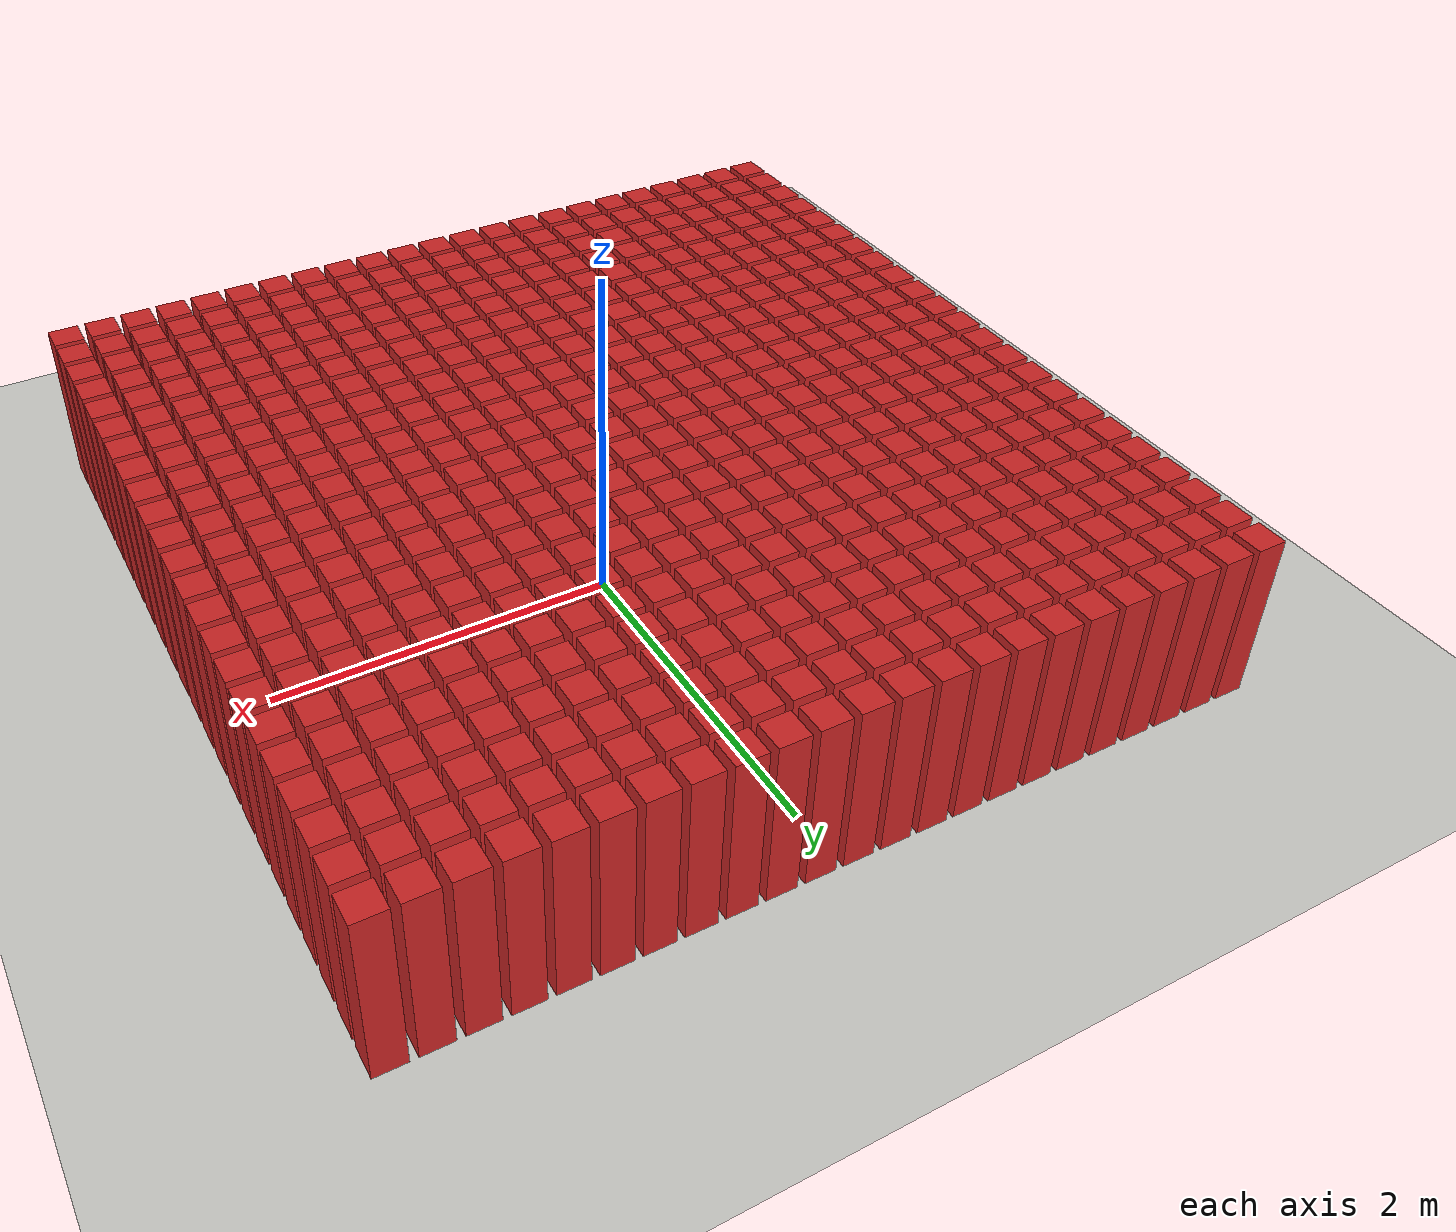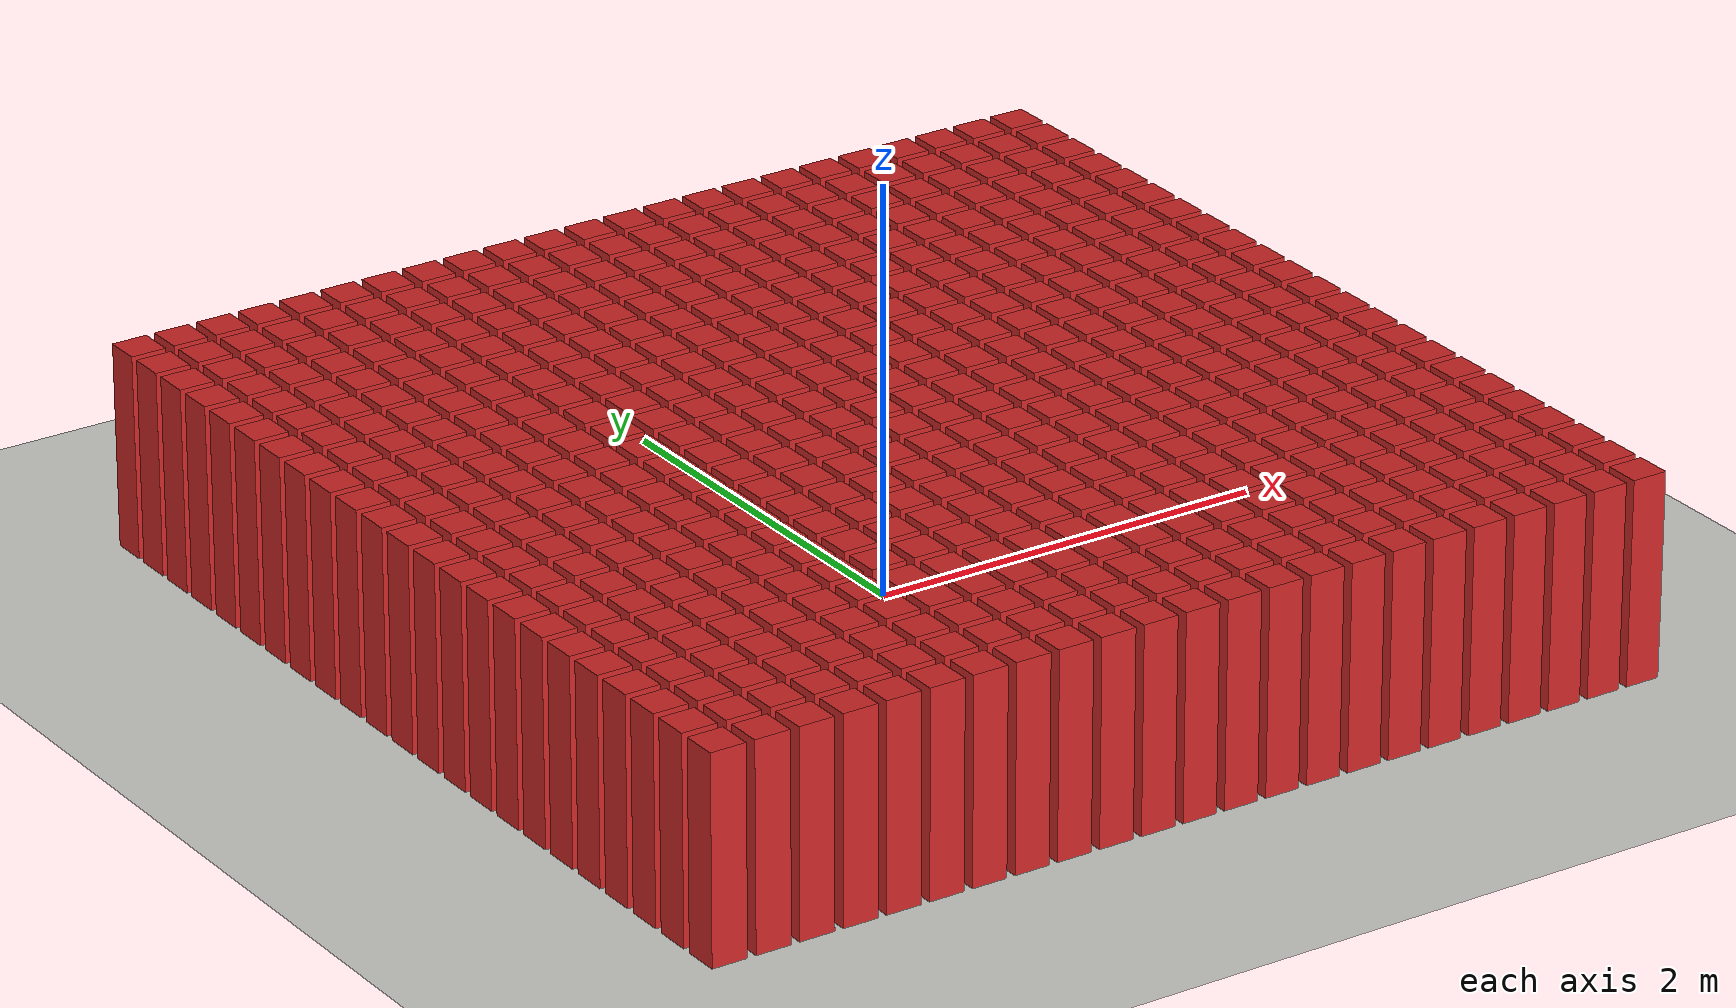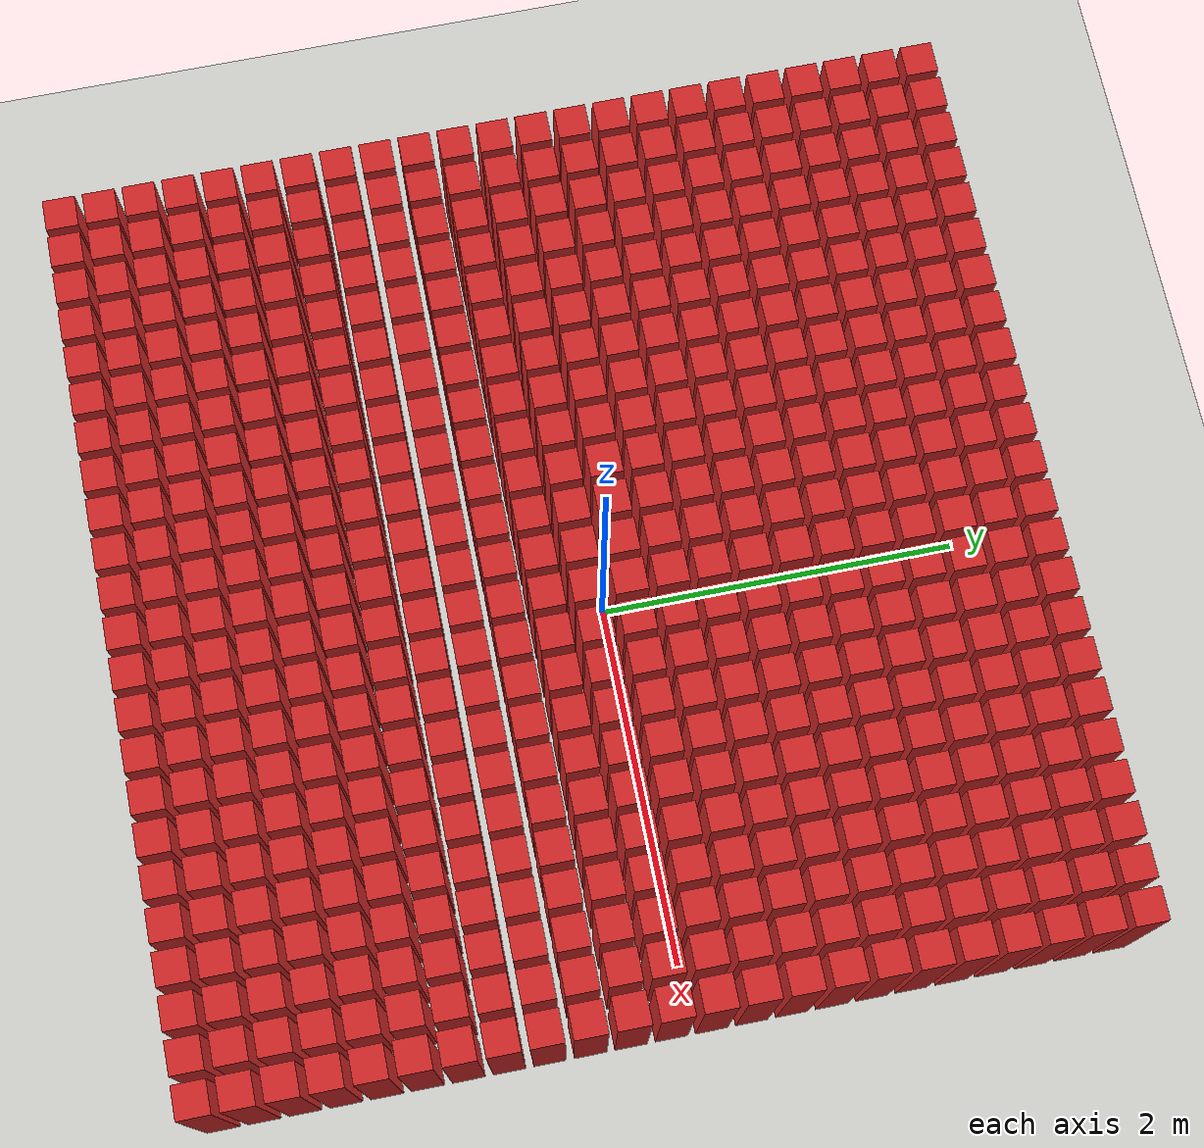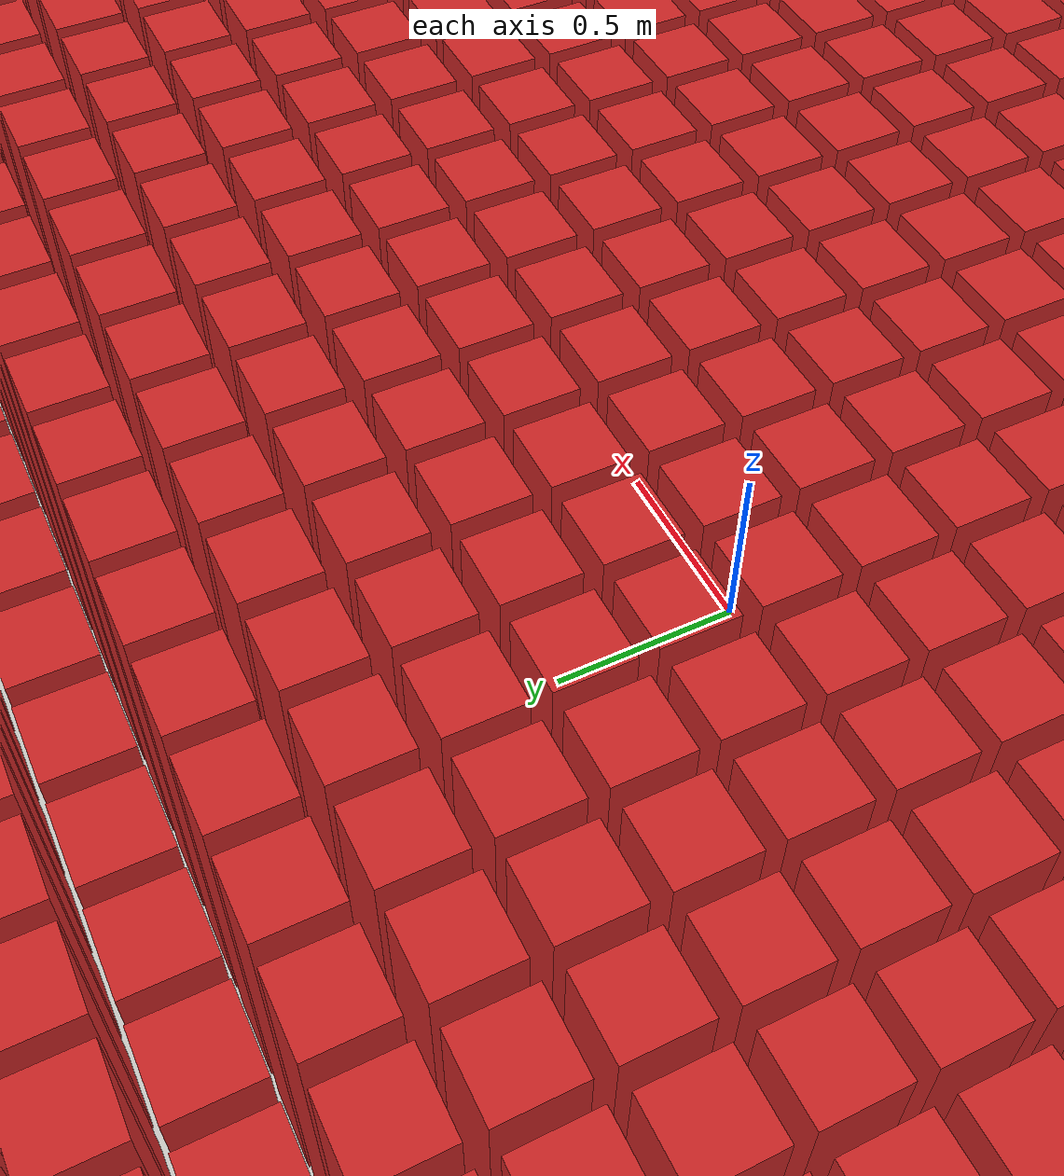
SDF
<sdf version="1.7">
 <world name="default">
  <light name="sun" type="directional">
   <pose>0 0 10 0 -0 0</pose>
   <diffuse>0.8 0.8 0.8 1</diffuse>
   <specular>0.2 0.2 0.2 1</specular>
   <attenuation>
    <range>1000</range>
    <constant>0.9</constant>
    <linear>0.01</linear>
    <quadratic>0.001</quadratic>
   </attenuation>
   <direction>-0.5 0.1 -0.9</direction>
   <spot><inner_angle>0</inner_angle><outer_angle>0</outer_angle><falloff>0</falloff></spot>
  </light>
  <model name="ground_plane">
   <static>1</static>
   <link name="link">
    <collision name="collision">
     <geometry><plane><normal>0 0 1</normal><size>100 100</size></plane></geometry>
     <surface>
      <contact><collide_bitmask>65535</collide_bitmask></contact>
      <friction><ode><mu>100</mu><mu2>50</mu2></ode></friction>
     </surface>
    </collision>
    <visual name="visual">
     <cast_shadows>0</cast_shadows>
     <geometry><plane><normal>0 0 1</normal><size>100 100</size></plane></geometry>
     <material>
      <script><uri>file://media/materials/scripts/gazebo.material</uri><name>Gazebo/CeilingTiled</name></script>
     </material>
    </visual>
   </link>
  </model>
  <gravity>0 0 -9.8</gravity>
  <magnetic_field>6e-06 2.3e-05 -4.2e-05</magnetic_field>
  <atmosphere type="adiabatic"/>
  <physics type="ode">
   <max_step_size>0.001</max_step_size>
   <real_time_factor>1</real_time_factor>
   <real_time_update_rate>1000</real_time_update_rate>
  </physics>
  <scene><ambient>0.4 0.4 0.4 1</ambient><background>0.7 0.7 0.7 1</background><shadows>1</shadows></scene>
  <spherical_coordinates>
   <surface_model>EARTH_WGS84</surface_model>
   <latitude_deg>0</latitude_deg>
   <longitude_deg>0</longitude_deg>
   <elevation>0</elevation>
   <heading_deg>0</heading_deg>
  </spherical_coordinates>
  <model name="wall0">
   <link name="link">
    <pose>0 0 0.5 0 -0 0</pose>
    <inertial>
     <mass>0.5167</mass>
     <inertia>
      <ixx>0.000861167</ixx>
      <ixy>0</ixy>
      <ixz>0</ixz>
      <iyy>0.000861167</iyy>
      <iyz>0</iyz>
      <izz>0.000861167</izz>
     </inertia>
    </inertial>
    <collision name="collision">
     <geometry><box><size>0.21 0.21 1</size></box></geometry>
     <surface>
      <contact>
       <poissons_ratio>0.347</poissons_ratio>
       <elastic_modulus>8.8e+09</elastic_modulus>
       <ode><kp>100000</kp><kd>100</kd><max_vel>100</max_vel><min_depth>0.001</min_depth></ode>
      </contact>
      <friction>
       <torsional>
        <coefficient>1</coefficient>
        <use_patch_radius>0</use_patch_radius>
        <surface_radius>0.01</surface_radius>
       </torsional>
      </friction>
     </surface>
    </collision>
    <visual name="visual">
     <geometry><box><size>0.175 0.175 1</size></box></geometry>
     <material>
      <script><uri>file://media/materials/scripts/gazebo.material</uri><name>Gazebo/Red</name></script>
     </material>
    </visual>
   </link>
   <pose>-2.5 -2.5 0 0 -0 0</pose>
  </model>
  <model name="wall1">
   <link name="link">
    <pose>0 0 0.5 0 -0 0</pose>
    <inertial>
     <mass>0.5167</mass>
     <inertia>
      <ixx>0.000861167</ixx>
      <ixy>0</ixy>
      <ixz>0</ixz>
      <iyy>0.000861167</iyy>
      <iyz>0</iyz>
      <izz>0.000861167</izz>
     </inertia>
    </inertial>
    <collision name="collision">
     <geometry><box><size>0.21 0.21 1</size></box></geometry>
     <surface>
      <contact>
       <poissons_ratio>0.347</poissons_ratio>
       <elastic_modulus>8.8e+09</elastic_modulus>
       <ode><kp>100000</kp><kd>100</kd><max_vel>100</max_vel><min_depth>0.001</min_depth></ode>
      </contact>
      <friction>
       <torsional>
        <coefficient>1</coefficient>
        <use_patch_radius>0</use_patch_radius>
        <surface_radius>0.01</surface_radius>
       </torsional>
      </friction>
     </surface>
    </collision>
    <visual name="visual">
     <geometry><box><size>0.175 0.175 1</size></box></geometry>
     <material>
      <script><uri>file://media/materials/scripts/gazebo.material</uri><name>Gazebo/Red</name></script>
     </material>
    </visual>
   </link>
   <pose>-2.28261 -2.5 0 0 -0 0</pose>
  </model>
  <model name="wall2">
   <link name="link">
    <pose>0 0 0.5 0 -0 0</pose>
    <inertial>
     <mass>0.5167</mass>
     <inertia>
      <ixx>0.000861167</ixx>
      <ixy>0</ixy>
      <ixz>0</ixz>
      <iyy>0.000861167</iyy>
      <iyz>0</iyz>
      <izz>0.000861167</izz>
     </inertia>
    </inertial>
    <collision name="collision">
     <geometry><box><size>0.21 0.21 1</size></box></geometry>
     <surface>
      <contact>
       <poissons_ratio>0.347</poissons_ratio>
       <elastic_modulus>8.8e+09</elastic_modulus>
       <ode><kp>100000</kp><kd>100</kd><max_vel>100</max_vel><min_depth>0.001</min_depth></ode>
      </contact>
      <friction>
       <torsional>
        <coefficient>1</coefficient>
        <use_patch_radius>0</use_patch_radius>
        <surface_radius>0.01</surface_radius>
       </torsional>
      </friction>
     </surface>
    </collision>
    <visual name="visual">
     <geometry><box><size>0.175 0.175 1</size></box></geometry>
     <material>
      <script><uri>file://media/materials/scripts/gazebo.material</uri><name>Gazebo/Red</name></script>
     </material>
    </visual>
   </link>
   <pose>-2.06522 -2.5 0 0 -0 0</pose>
  </model>
  <model name="wall3">
   <link name="link">
    <pose>0 0 0.5 0 -0 0</pose>
    <inertial>
     <mass>0.5167</mass>
     <inertia>
      <ixx>0.000861167</ixx>
      <ixy>0</ixy>
      <ixz>0</ixz>
      <iyy>0.000861167</iyy>
      <iyz>0</iyz>
      <izz>0.000861167</izz>
     </inertia>
    </inertial>
    <collision name="collision">
     <geometry><box><size>0.21 0.21 1</size></box></geometry>
     <surface>
      <contact>
       <poissons_ratio>0.347</poissons_ratio>
       <elastic_modulus>8.8e+09</elastic_modulus>
       <ode><kp>100000</kp><kd>100</kd><max_vel>100</max_vel><min_depth>0.001</min_depth></ode>
      </contact>
      <friction>
       <torsional>
        <coefficient>1</coefficient>
        <use_patch_radius>0</use_patch_radius>
        <surface_radius>0.01</surface_radius>
       </torsional>
      </friction>
     </surface>
    </collision>
    <visual name="visual">
     <geometry><box><size>0.175 0.175 1</size></box></geometry>
     <material>
      <script><uri>file://media/materials/scripts/gazebo.material</uri><name>Gazebo/Red</name></script>
     </material>
    </visual>
   </link>
   <pose>-1.84783 -2.5 0 0 -0 0</pose>
  </model>
  <model name="wall4">
   <link name="link">
    <pose>0 0 0.5 0 -0 0</pose>
    <inertial>
     <mass>0.5167</mass>
     <inertia>
      <ixx>0.000861167</ixx>
      <ixy>0</ixy>
      <ixz>0</ixz>
      <iyy>0.000861167</iyy>
      <iyz>0</iyz>
      <izz>0.000861167</izz>
     </inertia>
    </inertial>
    <collision name="collision">
     <geometry><box><size>0.21 0.21 1</size></box></geometry>
     <surface>
      <contact>
       <poissons_ratio>0.347</poissons_ratio>
       <elastic_modulus>8.8e+09</elastic_modulus>
       <ode><kp>100000</kp><kd>100</kd><max_vel>100</max_vel><min_depth>0.001</min_depth></ode>
      </contact>
      <friction>
       <torsional>
        <coefficient>1</coefficient>
        <use_patch_radius>0</use_patch_radius>
        <surface_radius>0.01</surface_radius>
       </torsional>
      </friction>
     </surface>
    </collision>
    <visual name="visual">
     <geometry><box><size>0.175 0.175 1</size></box></geometry>
     <material>
      <script><uri>file://media/materials/scripts/gazebo.material</uri><name>Gazebo/Red</name></script>
     </material>
    </visual>
   </link>
   <pose>-1.63043 -2.5 0 0 -0 0</pose>
  </model>
  <model name="wall5">
   <link name="link">
    <pose>0 0 0.5 0 -0 0</pose>
    <inertial>
     <mass>0.5167</mass>
     <inertia>
      <ixx>0.000861167</ixx>
      <ixy>0</ixy>
      <ixz>0</ixz>
      <iyy>0.000861167</iyy>
      <iyz>0</iyz>
      <izz>0.000861167</izz>
     </inertia>
    </inertial>
    <collision name="collision">
     <geometry><box><size>0.21 0.21 1</size></box></geometry>
     <surface>
      <contact>
       <poissons_ratio>0.347</poissons_ratio>
       <elastic_modulus>8.8e+09</elastic_modulus>
       <ode><kp>100000</kp><kd>100</kd><max_vel>100</max_vel><min_depth>0.001</min_depth></ode>
      </contact>
      <friction>
       <torsional>
        <coefficient>1</coefficient>
        <use_patch_radius>0</use_patch_radius>
        <surface_radius>0.01</surface_radius>
       </torsional>
      </friction>
     </surface>
    </collision>
    <visual name="visual">
     <geometry><box><size>0.175 0.175 1</size></box></geometry>
     <material>
      <script><uri>file://media/materials/scripts/gazebo.material</uri><name>Gazebo/Red</name></script>
     </material>
    </visual>
   </link>
   <pose>-1.41304 -2.5 0 0 -0 0</pose>
  </model>
  <model name="wall6">
   <link name="link">
    <pose>0 0 0.5 0 -0 0</pose>
    <inertial>
     <mass>0.5167</mass>
     <inertia>
      <ixx>0.000861167</ixx>
      <ixy>0</ixy>
      <ixz>0</ixz>
      <iyy>0.000861167</iyy>
      <iyz>0</iyz>
      <izz>0.000861167</izz>
     </inertia>
    </inertial>
    <collision name="collision">
     <geometry><box><size>0.21 0.21 1</size></box></geometry>
     <surface>
      <contact>
       <poissons_ratio>0.347</poissons_ratio>
       <elastic_modulus>8.8e+09</elastic_modulus>
       <ode><kp>100000</kp><kd>100</kd><max_vel>100</max_vel><min_depth>0.001</min_depth></ode>
      </contact>
      <friction>
       <torsional>
        <coefficient>1</coefficient>
        <use_patch_radius>0</use_patch_radius>
        <surface_radius>0.01</surface_radius>
       </torsional>
      </friction>
     </surface>
    </collision>
    <visual name="visual">
     <geometry><box><size>0.175 0.175 1</size></box></geometry>
     <material>
      <script><uri>file://media/materials/scripts/gazebo.material</uri><name>Gazebo/Red</name></script>
     </material>
    </visual>
   </link>
   <pose>-1.19565 -2.5 0 0 -0 0</pose>
  </model>
  <model name="wall7">
   <link name="link">
    <pose>0 0 0.5 0 -0 0</pose>
    <inertial>
     <mass>0.5167</mass>
     <inertia>
      <ixx>0.000861167</ixx>
      <ixy>0</ixy>
      <ixz>0</ixz>
      <iyy>0.000861167</iyy>
      <iyz>0</iyz>
      <izz>0.000861167</izz>
     </inertia>
    </inertial>
    <collision name="collision">
     <geometry><box><size>0.21 0.21 1</size></box></geometry>
     <surface>
      <contact>
       <poissons_ratio>0.347</poissons_ratio>
       <elastic_modulus>8.8e+09</elastic_modulus>
       <ode><kp>100000</kp><kd>100</kd><max_vel>100</max_vel><min_depth>0.001</min_depth></ode>
      </contact>
      <friction>
       <torsional>
        <coefficient>1</coefficient>
        <use_patch_radius>0</use_patch_radius>
        <surface_radius>0.01</surface_radius>
       </torsional>
      </friction>
     </surface>
    </collision>
    <visual name="visual">
     <geometry><box><size>0.175 0.175 1</size></box></geometry>
     <material>
      <script><uri>file://media/materials/scripts/gazebo.material</uri><name>Gazebo/Red</name></script>
     </material>
    </visual>
   </link>
   <pose>-0.978261 -2.5 0 0 -0 0</pose>
  </model>
  <model name="wall8">
   <link name="link">
    <pose>0 0 0.5 0 -0 0</pose>
    <inertial>
     <mass>0.5167</mass>
     <inertia>
      <ixx>0.000861167</ixx>
      <ixy>0</ixy>
      <ixz>0</ixz>
      <iyy>0.000861167</iyy>
      <iyz>0</iyz>
      <izz>0.000861167</izz>
     </inertia>
    </inertial>
    <collision name="collision">
     <geometry><box><size>0.21 0.21 1</size></box></geometry>
     <surface>
      <contact>
       <poissons_ratio>0.347</poissons_ratio>
       <elastic_modulus>8.8e+09</elastic_modulus>
       <ode><kp>100000</kp><kd>100</kd><max_vel>100</max_vel><min_depth>0.001</min_depth></ode>
      </contact>
      <friction>
       <torsional>
        <coefficient>1</coefficient>
        <use_patch_radius>0</use_patch_radius>
        <surface_radius>0.01</surface_radius>
       </torsional>
      </friction>
     </surface>
    </collision>
    <visual name="visual">
     <geometry><box><size>0.175 0.175 1</size></box></geometry>
     <material>
      <script><uri>file://media/materials/scripts/gazebo.material</uri><name>Gazebo/Red</name></script>
     </material>
    </visual>
   </link>
   <pose>-0.76087 -2.5 0 0 -0 0</pose>
  </model>
  <model name="wall9">
   <link name="link">
    <pose>0 0 0.5 0 -0 0</pose>
    <inertial>
     <mass>0.5167</mass>
     <inertia>
      <ixx>0.000861167</ixx>
      <ixy>0</ixy>
      <ixz>0</ixz>
      <iyy>0.000861167</iyy>
      <iyz>0</iyz>
      <izz>0.000861167</izz>
     </inertia>
    </inertial>
    <collision name="collision">
     <geometry><box><size>0.21 0.21 1</size></box></geometry>
     <surface>
      <contact>
       <poissons_ratio>0.347</poissons_ratio>
       <elastic_modulus>8.8e+09</elastic_modulus>
       <ode><kp>100000</kp><kd>100</kd><max_vel>100</max_vel><min_depth>0.001</min_depth></ode>
      </contact>
      <friction>
       <torsional>
        <coefficient>1</coefficient>
        <use_patch_radius>0</use_patch_radius>
        <surface_radius>0.01</surface_radius>
       </torsional>
      </friction>
     </surface>
    </collision>
    <visual name="visual">
     <geometry><box><size>0.175 0.175 1</size></box></geometry>
     <material>
      <script><uri>file://media/materials/scripts/gazebo.material</uri><name>Gazebo/Red</name></script>
     </material>
    </visual>
   </link>
   <pose>-0.543478 -2.5 0 0 -0 0</pose>
  </model>
  <model name="wall10">
   <link name="link">
    <pose>0 0 0.5 0 -0 0</pose>
    <inertial>
     <mass>0.5167</mass>
     <inertia>
      <ixx>0.000861167</ixx>
      <ixy>0</ixy>
      <ixz>0</ixz>
      <iyy>0.000861167</iyy>
      <iyz>0</iyz>
      <izz>0.000861167</izz>
     </inertia>
    </inertial>
    <collision name="collision">
     <geometry><box><size>0.21 0.21 1</size></box></geometry>
     <surface>
      <contact>
       <poissons_ratio>0.347</poissons_ratio>
       <elastic_modulus>8.8e+09</elastic_modulus>
       <ode><kp>100000</kp><kd>100</kd><max_vel>100</max_vel><min_depth>0.001</min_depth></ode>
      </contact>
      <friction>
       <torsional>
        <coefficient>1</coefficient>
        <use_patch_radius>0</use_patch_radius>
        <surface_radius>0.01</surface_radius>
       </torsional>
      </friction>
     </surface>
    </collision>
    <visual name="visual">
     <geometry><box><size>0.175 0.175 1</size></box></geometry>
     <material>
      <script><uri>file://media/materials/scripts/gazebo.material</uri><name>Gazebo/Red</name></script>
     </material>
    </visual>
   </link>
   <pose>-0.326087 -2.5 0 0 -0 0</pose>
  </model>
  <model name="wall11">
   <link name="link">
    <pose>0 0 0.5 0 -0 0</pose>
    <inertial>
     <mass>0.5167</mass>
     <inertia>
      <ixx>0.000861167</ixx>
      <ixy>0</ixy>
      <ixz>0</ixz>
      <iyy>0.000861167</iyy>
      <iyz>0</iyz>
      <izz>0.000861167</izz>
     </inertia>
    </inertial>
    <collision name="collision">
     <geometry><box><size>0.21 0.21 1</size></box></geometry>
     <surface>
      <contact>
       <poissons_ratio>0.347</poissons_ratio>
       <elastic_modulus>8.8e+09</elastic_modulus>
       <ode><kp>100000</kp><kd>100</kd><max_vel>100</max_vel><min_depth>0.001</min_depth></ode>
      </contact>
      <friction>
       <torsional>
        <coefficient>1</coefficient>
        <use_patch_radius>0</use_patch_radius>
        <surface_radius>0.01</surface_radius>
       </torsional>
      </friction>
     </surface>
    </collision>
    <visual name="visual">
     <geometry><box><size>0.175 0.175 1</size></box></geometry>
     <material>
      <script><uri>file://media/materials/scripts/gazebo.material</uri><name>Gazebo/Red</name></script>
     </material>
    </visual>
   </link>
   <pose>-0.108696 -2.5 0 0 -0 0</pose>
  </model>
  <model name="wall12">
   <link name="link">
    <pose>0 0 0.5 0 -0 0</pose>
    <inertial>
     <mass>0.5167</mass>
     <inertia>
      <ixx>0.000861167</ixx>
      <ixy>0</ixy>
      <ixz>0</ixz>
      <iyy>0.000861167</iyy>
      <iyz>0</iyz>
      <izz>0.000861167</izz>
     </inertia>
    </inertial>
    <collision name="collision">
     <geometry><box><size>0.21 0.21 1</size></box></geometry>
     <surface>
      <contact>
       <poissons_ratio>0.347</poissons_ratio>
       <elastic_modulus>8.8e+09</elastic_modulus>
       <ode><kp>100000</kp><kd>100</kd><max_vel>100</max_vel><min_depth>0.001</min_depth></ode>
      </contact>
      <friction>
       <torsional>
        <coefficient>1</coefficient>
        <use_patch_radius>0</use_patch_radius>
        <surface_radius>0.01</surface_radius>
       </torsional>
      </friction>
     </surface>
    </collision>
    <visual name="visual">
     <geometry><box><size>0.175 0.175 1</size></box></geometry>
     <material>
      <script><uri>file://media/materials/scripts/gazebo.material</uri><name>Gazebo/Red</name></script>
     </material>
    </visual>
   </link>
   <pose>0.108696 -2.5 0 0 -0 0</pose>
  </model>
  <model name="wall13">
   <link name="link">
    <pose>0 0 0.5 0 -0 0</pose>
    <inertial>
     <mass>0.5167</mass>
     <inertia>
      <ixx>0.000861167</ixx>
      <ixy>0</ixy>
      <ixz>0</ixz>
      <iyy>0.000861167</iyy>
      <iyz>0</iyz>
      <izz>0.000861167</izz>
     </inertia>
    </inertial>
    <collision name="collision">
     <geometry><box><size>0.21 0.21 1</size></box></geometry>
     <surface>
      <contact>
       <poissons_ratio>0.347</poissons_ratio>
       <elastic_modulus>8.8e+09</elastic_modulus>
       <ode><kp>100000</kp><kd>100</kd><max_vel>100</max_vel><min_depth>0.001</min_depth></ode>
      </contact>
      <friction>
       <torsional>
        <coefficient>1</coefficient>
        <use_patch_radius>0</use_patch_radius>
        <surface_radius>0.01</surface_radius>
       </torsional>
      </friction>
     </surface>
    </collision>
    <visual name="visual">
     <geometry><box><size>0.175 0.175 1</size></box></geometry>
     <material>
      <script><uri>file://media/materials/scripts/gazebo.material</uri><name>Gazebo/Red</name></script>
     </material>
    </visual>
   </link>
   <pose>0.326087 -2.5 0 0 -0 0</pose>
  </model>
  <model name="wall14">
   <link name="link">
    <pose>0 0 0.5 0 -0 0</pose>
    <inertial>
     <mass>0.5167</mass>
     <inertia>
      <ixx>0.000861167</ixx>
      <ixy>0</ixy>
      <ixz>0</ixz>
      <iyy>0.000861167</iyy>
      <iyz>0</iyz>
      <izz>0.000861167</izz>
     </inertia>
    </inertial>
    <collision name="collision">
     <geometry><box><size>0.21 0.21 1</size></box></geometry>
     <surface>
      <contact>
       <poissons_ratio>0.347</poissons_ratio>
       <elastic_modulus>8.8e+09</elastic_modulus>
       <ode><kp>100000</kp><kd>100</kd><max_vel>100</max_vel><min_depth>0.001</min_depth></ode>
      </contact>
      <friction>
       <torsional>
        <coefficient>1</coefficient>
        <use_patch_radius>0</use_patch_radius>
        <surface_radius>0.01</surface_radius>
       </torsional>
      </friction>
     </surface>
    </collision>
    <visual name="visual">
     <geometry><box><size>0.175 0.175 1</size></box></geometry>
     <material>
      <script><uri>file://media/materials/scripts/gazebo.material</uri><name>Gazebo/Red</name></script>
     </material>
    </visual>
   </link>
   <pose>0.543478 -2.5 0 0 -0 0</pose>
  </model>
  <model name="wall15">
   <link name="link">
    <pose>0 0 0.5 0 -0 0</pose>
    <inertial>
     <mass>0.5167</mass>
     <inertia>
      <ixx>0.000861167</ixx>
      <ixy>0</ixy>
      <ixz>0</ixz>
      <iyy>0.000861167</iyy>
      <iyz>0</iyz>
      <izz>0.000861167</izz>
     </inertia>
    </inertial>
    <collision name="collision">
     <geometry><box><size>0.21 0.21 1</size></box></geometry>
     <surface>
      <contact>
       <poissons_ratio>0.347</poissons_ratio>
       <elastic_modulus>8.8e+09</elastic_modulus>
       <ode><kp>100000</kp><kd>100</kd><max_vel>100</max_vel><min_depth>0.001</min_depth></ode>
      </contact>
      <friction>
       <torsional>
        <coefficient>1</coefficient>
        <use_patch_radius>0</use_patch_radius>
        <surface_radius>0.01</surface_radius>
       </torsional>
      </friction>
     </surface>
    </collision>
    <visual name="visual">
     <geometry><box><size>0.175 0.175 1</size></box></geometry>
     <material>
      <script><uri>file://media/materials/scripts/gazebo.material</uri><name>Gazebo/Red</name></script>
     </material>
    </visual>
   </link>
   <pose>0.76087 -2.5 0 0 -0 0</pose>
  </model>
  <model name="wall16">
   <link name="link">
    <pose>0 0 0.5 0 -0 0</pose>
    <inertial>
     <mass>0.5167</mass>
     <inertia>
      <ixx>0.000861167</ixx>
      <ixy>0</ixy>
      <ixz>0</ixz>
      <iyy>0.000861167</iyy>
      <iyz>0</iyz>
      <izz>0.000861167</izz>
     </inertia>
    </inertial>
    <collision name="collision">
     <geometry><box><size>0.21 0.21 1</size></box></geometry>
     <surface>
      <contact>
       <poissons_ratio>0.347</poissons_ratio>
       <elastic_modulus>8.8e+09</elastic_modulus>
       <ode><kp>100000</kp><kd>100</kd><max_vel>100</max_vel><min_depth>0.001</min_depth></ode>
      </contact>
      <friction>
       <torsional>
        <coefficient>1</coefficient>
        <use_patch_radius>0</use_patch_radius>
        <surface_radius>0.01</surface_radius>
       </torsional>
      </friction>
     </surface>
    </collision>
    <visual name="visual">
     <geometry><box><size>0.175 0.175 1</size></box></geometry>
     <material>
      <script><uri>file://media/materials/scripts/gazebo.material</uri><name>Gazebo/Red</name></script>
     </material>
    </visual>
   </link>
   <pose>0.978261 -2.5 0 0 -0 0</pose>
  </model>
  <model name="wall17">
   <link name="link">
    <pose>0 0 0.5 0 -0 0</pose>
    <inertial>
     <mass>0.5167</mass>
     <inertia>
      <ixx>0.000861167</ixx>
      <ixy>0</ixy>
      <ixz>0</ixz>
      <iyy>0.000861167</iyy>
      <iyz>0</iyz>
      <izz>0.000861167</izz>
     </inertia>
    </inertial>
    <collision name="collision">
     <geometry><box><size>0.21 0.21 1</size></box></geometry>
     <surface>
      <contact>
       <poissons_ratio>0.347</poissons_ratio>
       <elastic_modulus>8.8e+09</elastic_modulus>
       <ode><kp>100000</kp><kd>100</kd><max_vel>100</max_vel><min_depth>0.001</min_depth></ode>
      </contact>
      <friction>
       <torsional>
        <coefficient>1</coefficient>
        <use_patch_radius>0</use_patch_radius>
        <surface_radius>0.01</surface_radius>
       </torsional>
      </friction>
     </surface>
    </collision>
    <visual name="visual">
     <geometry><box><size>0.175 0.175 1</size></box></geometry>
     <material>
      <script><uri>file://media/materials/scripts/gazebo.material</uri><name>Gazebo/Red</name></script>
     </material>
    </visual>
   </link>
   <pose>1.19565 -2.5 0 0 -0 0</pose>
  </model>
  <model name="wall18">
   <link name="link">
    <pose>0 0 0.5 0 -0 0</pose>
    <inertial>
     <mass>0.5167</mass>
     <inertia>
      <ixx>0.000861167</ixx>
      <ixy>0</ixy>
      <ixz>0</ixz>
      <iyy>0.000861167</iyy>
      <iyz>0</iyz>
      <izz>0.000861167</izz>
     </inertia>
    </inertial>
    <collision name="collision">
     <geometry><box><size>0.21 0.21 1</size></box></geometry>
     <surface>
      <contact>
       <poissons_ratio>0.347</poissons_ratio>
       <elastic_modulus>8.8e+09</elastic_modulus>
       <ode><kp>100000</kp><kd>100</kd><max_vel>100</max_vel><min_depth>0.001</min_depth></ode>
      </contact>
      <friction>
       <torsional>
        <coefficient>1</coefficient>
        <use_patch_radius>0</use_patch_radius>
        <surface_radius>0.01</surface_radius>
       </torsional>
      </friction>
     </surface>
    </collision>
    <visual name="visual">
     <geometry><box><size>0.175 0.175 1</size></box></geometry>
     <material>
      <script><uri>file://media/materials/scripts/gazebo.material</uri><name>Gazebo/Red</name></script>
     </material>
    </visual>
   </link>
   <pose>1.41304 -2.5 0 0 -0 0</pose>
  </model>
  <model name="wall19">
   <link name="link">
    <pose>0 0 0.5 0 -0 0</pose>
    <inertial>
     <mass>0.5167</mass>
     <inertia>
      <ixx>0.000861167</ixx>
      <ixy>0</ixy>
      <ixz>0</ixz>
      <iyy>0.000861167</iyy>
      <iyz>0</iyz>
      <izz>0.000861167</izz>
     </inertia>
    </inertial>
    <collision name="collision">
     <geometry><box><size>0.21 0.21 1</size></box></geometry>
     <surface>
      <contact>
       <poissons_ratio>0.347</poissons_ratio>
       <elastic_modulus>8.8e+09</elastic_modulus>
       <ode><kp>100000</kp><kd>100</kd><max_vel>100</max_vel><min_depth>0.001</min_depth></ode>
      </contact>
      <friction>
       <torsional>
        <coefficient>1</coefficient>
        <use_patch_radius>0</use_patch_radius>
        <surface_radius>0.01</surface_radius>
       </torsional>
      </friction>
     </surface>
    </collision>
    <visual name="visual">
     <geometry><box><size>0.175 0.175 1</size></box></geometry>
     <material>
      <script><uri>file://media/materials/scripts/gazebo.material</uri><name>Gazebo/Red</name></script>
     </material>
    </visual>
   </link>
   <pose>1.63043 -2.5 0 0 -0 0</pose>
  </model>
  <model name="wall20">
   <link name="link">
    <pose>0 0 0.5 0 -0 0</pose>
    <inertial>
     <mass>0.5167</mass>
     <inertia>
      <ixx>0.000861167</ixx>
      <ixy>0</ixy>
      <ixz>0</ixz>
      <iyy>0.000861167</iyy>
      <iyz>0</iyz>
      <izz>0.000861167</izz>
     </inertia>
    </inertial>
    <collision name="collision">
     <geometry><box><size>0.21 0.21 1</size></box></geometry>
     <surface>
      <contact>
       <poissons_ratio>0.347</poissons_ratio>
       <elastic_modulus>8.8e+09</elastic_modulus>
       <ode><kp>100000</kp><kd>100</kd><max_vel>100</max_vel><min_depth>0.001</min_depth></ode>
      </contact>
      <friction>
       <torsional>
        <coefficient>1</coefficient>
        <use_patch_radius>0</use_patch_radius>
        <surface_radius>0.01</surface_radius>
       </torsional>
      </friction>
     </surface>
    </collision>
    <visual name="visual">
     <geometry><box><size>0.175 0.175 1</size></box></geometry>
     <material>
      <script><uri>file://media/materials/scripts/gazebo.material</uri><name>Gazebo/Red</name></script>
     </material>
    </visual>
   </link>
   <pose>1.84783 -2.5 0 0 -0 0</pose>
  </model>
  <model name="wall21">
   <link name="link">
    <pose>0 0 0.5 0 -0 0</pose>
    <inertial>
     <mass>0.5167</mass>
     <inertia>
      <ixx>0.000861167</ixx>
      <ixy>0</ixy>
      <ixz>0</ixz>
      <iyy>0.000861167</iyy>
      <iyz>0</iyz>
      <izz>0.000861167</izz>
     </inertia>
    </inertial>
    <collision name="collision">
     <geometry><box><size>0.21 0.21 1</size></box></geometry>
     <surface>
      <contact>
       <poissons_ratio>0.347</poissons_ratio>
       <elastic_modulus>8.8e+09</elastic_modulus>
       <ode><kp>100000</kp><kd>100</kd><max_vel>100</max_vel><min_depth>0.001</min_depth></ode>
      </contact>
      <friction>
       <torsional>
        <coefficient>1</coefficient>
        <use_patch_radius>0</use_patch_radius>
        <surface_radius>0.01</surface_radius>
       </torsional>
      </friction>
     </surface>
    </collision>
    <visual name="visual">
     <geometry><box><size>0.175 0.175 1</size></box></geometry>
     <material>
      <script><uri>file://media/materials/scripts/gazebo.material</uri><name>Gazebo/Red</name></script>
     </material>
    </visual>
   </link>
   <pose>2.06522 -2.5 0 0 -0 0</pose>
  </model>
  <model name="wall22">
   <link name="link">
    <pose>0 0 0.5 0 -0 0</pose>
    <inertial>
     <mass>0.5167</mass>
     <inertia>
      <ixx>0.000861167</ixx>
      <ixy>0</ixy>
      <ixz>0</ixz>
      <iyy>0.000861167</iyy>
      <iyz>0</iyz>
      <izz>0.000861167</izz>
     </inertia>
    </inertial>
    <collision name="collision">
     <geometry><box><size>0.21 0.21 1</size></box></geometry>
     <surface>
      <contact>
       <poissons_ratio>0.347</poissons_ratio>
       <elastic_modulus>8.8e+09</elastic_modulus>
       <ode><kp>100000</kp><kd>100</kd><max_vel>100</max_vel><min_depth>0.001</min_depth></ode>
      </contact>
      <friction>
       <torsional>
        <coefficient>1</coefficient>
        <use_patch_radius>0</use_patch_radius>
        <surface_radius>0.01</surface_radius>
       </torsional>
      </friction>
     </surface>
    </collision>
    <visual name="visual">
     <geometry><box><size>0.175 0.175 1</size></box></geometry>
     <material>
      <script><uri>file://media/materials/scripts/gazebo.material</uri><name>Gazebo/Red</name></script>
     </material>
    </visual>
   </link>
   <pose>2.28261 -2.5 0 0 -0 0</pose>
  </model>
  <model name="wall23">
   <link name="link">
    <pose>0 0 0.5 0 -0 0</pose>
    <inertial>
     <mass>0.5167</mass>
     <inertia>
      <ixx>0.000861167</ixx>
      <ixy>0</ixy>
      <ixz>0</ixz>
      <iyy>0.000861167</iyy>
      <iyz>0</iyz>
      <izz>0.000861167</izz>
     </inertia>
    </inertial>
    <collision name="collision">
     <geometry><box><size>0.21 0.21 1</size></box></geometry>
     <surface>
      <contact>
       <poissons_ratio>0.347</poissons_ratio>
       <elastic_modulus>8.8e+09</elastic_modulus>
       <ode><kp>100000</kp><kd>100</kd><max_vel>100</max_vel><min_depth>0.001</min_depth></ode>
      </contact>
      <friction>
       <torsional>
        <coefficient>1</coefficient>
        <use_patch_radius>0</use_patch_radius>
        <surface_radius>0.01</surface_radius>
       </torsional>
      </friction>
     </surface>
    </collision>
    <visual name="visual">
     <geometry><box><size>0.175 0.175 1</size></box></geometry>
     <material>
      <script><uri>file://media/materials/scripts/gazebo.material</uri><name>Gazebo/Red</name></script>
     </material>
    </visual>
   </link>
   <pose>-2.5 -2.28261 0 0 -0 0</pose>
  </model>
  <model name="wall24">
   <link name="link">
    <pose>0 0 0.5 0 -0 0</pose>
    <inertial>
     <mass>0.5167</mass>
     <inertia>
      <ixx>0.000861167</ixx>
      <ixy>0</ixy>
      <ixz>0</ixz>
      <iyy>0.000861167</iyy>
      <iyz>0</iyz>
      <izz>0.000861167</izz>
     </inertia>
    </inertial>
    <collision name="collision">
     <geometry><box><size>0.21 0.21 1</size></box></geometry>
     <surface>
      <contact>
       <poissons_ratio>0.347</poissons_ratio>
       <elastic_modulus>8.8e+09</elastic_modulus>
       <ode><kp>100000</kp><kd>100</kd><max_vel>100</max_vel><min_depth>0.001</min_depth></ode>
      </contact>
      <friction>
       <torsional>
        <coefficient>1</coefficient>
        <use_patch_radius>0</use_patch_radius>
        <surface_radius>0.01</surface_radius>
       </torsional>
      </friction>
     </surface>
    </collision>
    <visual name="visual">
     <geometry><box><size>0.175 0.175 1</size></box></geometry>
     <material>
      <script><uri>file://media/materials/scripts/gazebo.material</uri><name>Gazebo/Red</name></script>
     </material>
    </visual>
   </link>
   <pose>-2.28261 -2.28261 0 0 -0 0</pose>
  </model>
  <model name="wall25">
   <link name="link">
    <pose>0 0 0.5 0 -0 0</pose>
    <inertial>
     <mass>0.5167</mass>
     <inertia>
      <ixx>0.000861167</ixx>
      <ixy>0</ixy>
      <ixz>0</ixz>
      <iyy>0.000861167</iyy>
      <iyz>0</iyz>
      <izz>0.000861167</izz>
     </inertia>
    </inertial>
    <collision name="collision">
     <geometry><box><size>0.21 0.21 1</size></box></geometry>
     <surface>
      <contact>
       <poissons_ratio>0.347</poissons_ratio>
       <elastic_modulus>8.8e+09</elastic_modulus>
       <ode><kp>100000</kp><kd>100</kd><max_vel>100</max_vel><min_depth>0.001</min_depth></ode>
      </contact>
      <friction>
       <torsional>
        <coefficient>1</coefficient>
        <use_patch_radius>0</use_patch_radius>
        <surface_radius>0.01</surface_radius>
       </torsional>
      </friction>
     </surface>
    </collision>
    <visual name="visual">
     <geometry><box><size>0.175 0.175 1</size></box></geometry>
     <material>
      <script><uri>file://media/materials/scripts/gazebo.material</uri><name>Gazebo/Red</name></script>
     </material>
    </visual>
   </link>
   <pose>-2.06522 -2.28261 0 0 -0 0</pose>
  </model>
  <model name="wall26">
   <link name="link">
    <pose>0 0 0.5 0 -0 0</pose>
    <inertial>
     <mass>0.5167</mass>
     <inertia>
      <ixx>0.000861167</ixx>
      <ixy>0</ixy>
      <ixz>0</ixz>
      <iyy>0.000861167</iyy>
      <iyz>0</iyz>
      <izz>0.000861167</izz>
     </inertia>
    </inertial>
    <collision name="collision">
     <geometry><box><size>0.21 0.21 1</size></box></geometry>
     <surface>
      <contact>
       <poissons_ratio>0.347</poissons_ratio>
       <elastic_modulus>8.8e+09</elastic_modulus>
       <ode><kp>100000</kp><kd>100</kd><max_vel>100</max_vel><min_depth>0.001</min_depth></ode>
      </contact>
      <friction>
       <torsional>
        <coefficient>1</coefficient>
        <use_patch_radius>0</use_patch_radius>
        <surface_radius>0.01</surface_radius>
       </torsional>
      </friction>
     </surface>
    </collision>
    <visual name="visual">
     <geometry><box><size>0.175 0.175 1</size></box></geometry>
     <material>
      <script><uri>file://media/materials/scripts/gazebo.material</uri><name>Gazebo/Red</name></script>
     </material>
    </visual>
   </link>
   <pose>-1.84783 -2.28261 0 0 -0 0</pose>
  </model>
  <model name="wall27">
   <link name="link">
    <pose>0 0 0.5 0 -0 0</pose>
    <inertial>
     <mass>0.5167</mass>
     <inertia>
      <ixx>0.000861167</ixx>
      <ixy>0</ixy>
      <ixz>0</ixz>
      <iyy>0.000861167</iyy>
      <iyz>0</iyz>
      <izz>0.000861167</izz>
     </inertia>
    </inertial>
    <collision name="collision">
     <geometry><box><size>0.21 0.21 1</size></box></geometry>
     <surface>
      <contact>
       <poissons_ratio>0.347</poissons_ratio>
       <elastic_modulus>8.8e+09</elastic_modulus>
       <ode><kp>100000</kp><kd>100</kd><max_vel>100</max_vel><min_depth>0.001</min_depth></ode>
      </contact>
      <friction>
       <torsional>
        <coefficient>1</coefficient>
        <use_patch_radius>0</use_patch_radius>
        <surface_radius>0.01</surface_radius>
       </torsional>
      </friction>
     </surface>
    </collision>
    <visual name="visual">
     <geometry><box><size>0.175 0.175 1</size></box></geometry>
     <material>
      <script><uri>file://media/materials/scripts/gazebo.material</uri><name>Gazebo/Red</name></script>
     </material>
    </visual>
   </link>
   <pose>-1.63043 -2.28261 0 0 -0 0</pose>
  </model>
  <model name="wall28">
   <link name="link">
    <pose>0 0 0.5 0 -0 0</pose>
    <inertial>
     <mass>0.5167</mass>
     <inertia>
      <ixx>0.000861167</ixx>
      <ixy>0</ixy>
      <ixz>0</ixz>
      <iyy>0.000861167</iyy>
      <iyz>0</iyz>
      <izz>0.000861167</izz>
     </inertia>
    </inertial>
    <collision name="collision">
     <geometry><box><size>0.21 0.21 1</size></box></geometry>
     <surface>
      <contact>
       <poissons_ratio>0.347</poissons_ratio>
       <elastic_modulus>8.8e+09</elastic_modulus>
       <ode><kp>100000</kp><kd>100</kd><max_vel>100</max_vel><min_depth>0.001</min_depth></ode>
      </contact>
      <friction>
       <torsional>
        <coefficient>1</coefficient>
        <use_patch_radius>0</use_patch_radius>
        <surface_radius>0.01</surface_radius>
       </torsional>
      </friction>
     </surface>
    </collision>
    <visual name="visual">
     <geometry><box><size>0.175 0.175 1</size></box></geometry>
     <material>
      <script><uri>file://media/materials/scripts/gazebo.material</uri><name>Gazebo/Red</name></script>
     </material>
    </visual>
   </link>
   <pose>-1.41304 -2.28261 0 0 -0 0</pose>
  </model>
  <model name="wall29">
   <link name="link">
    <pose>0 0 0.5 0 -0 0</pose>
    <inertial>
     <mass>0.5167</mass>
     <inertia>
      <ixx>0.000861167</ixx>
      <ixy>0</ixy>
      <ixz>0</ixz>
      <iyy>0.000861167</iyy>
      <iyz>0</iyz>
      <izz>0.000861167</izz>
     </inertia>
    </inertial>
    <collision name="collision">
     <geometry><box><size>0.21 0.21 1</size></box></geometry>
     <surface>
      <contact>
       <poissons_ratio>0.347</poissons_ratio>
       <elastic_modulus>8.8e+09</elastic_modulus>
       <ode><kp>100000</kp><kd>100</kd><max_vel>100</max_vel><min_depth>0.001</min_depth></ode>
      </contact>
      <friction>
       <torsional>
        <coefficient>1</coefficient>
        <use_patch_radius>0</use_patch_radius>
        <surface_radius>0.01</surface_radius>
       </torsional>
      </friction>
     </surface>
    </collision>
    <visual name="visual">
     <geometry><box><size>0.175 0.175 1</size></box></geometry>
     <material>
      <script><uri>file://media/materials/scripts/gazebo.material</uri><name>Gazebo/Red</name></script>
     </material>
    </visual>
   </link>
   <pose>-1.19565 -2.28261 0 0 -0 0</pose>
  </model>
  <model name="wall30">
   <link name="link">
    <pose>0 0 0.5 0 -0 0</pose>
    <inertial>
     <mass>0.5167</mass>
     <inertia>
      <ixx>0.000861167</ixx>
      <ixy>0</ixy>
      <ixz>0</ixz>
      <iyy>0.000861167</iyy>
      <iyz>0</iyz>
      <izz>0.000861167</izz>
     </inertia>
    </inertial>
    <collision name="collision">
     <geometry><box><size>0.21 0.21 1</size></box></geometry>
     <surface>
      <contact>
       <poissons_ratio>0.347</poissons_ratio>
       <elastic_modulus>8.8e+09</elastic_modulus>
       <ode><kp>100000</kp><kd>100</kd><max_vel>100</max_vel><min_depth>0.001</min_depth></ode>
      </contact>
      <friction>
       <torsional>
        <coefficient>1</coefficient>
        <use_patch_radius>0</use_patch_radius>
        <surface_radius>0.01</surface_radius>
       </torsional>
      </friction>
     </surface>
    </collision>
    <visual name="visual">
     <geometry><box><size>0.175 0.175 1</size></box></geometry>
     <material>
      <script><uri>file://media/materials/scripts/gazebo.material</uri><name>Gazebo/Red</name></script>
     </material>
    </visual>
   </link>
   <pose>-0.978261 -2.28261 0 0 -0 0</pose>
  </model>
  <model name="wall31">
   <link name="link">
    <pose>0 0 0.5 0 -0 0</pose>
    <inertial>
     <mass>0.5167</mass>
     <inertia>
      <ixx>0.000861167</ixx>
      <ixy>0</ixy>
      <ixz>0</ixz>
      <iyy>0.000861167</iyy>
      <iyz>0</iyz>
      <izz>0.000861167</izz>
     </inertia>
    </inertial>
    <collision name="collision">
     <geometry><box><size>0.21 0.21 1</size></box></geometry>
     <surface>
      <contact>
       <poissons_ratio>0.347</poissons_ratio>
       <elastic_modulus>8.8e+09</elastic_modulus>
       <ode><kp>100000</kp><kd>100</kd><max_vel>100</max_vel><min_depth>0.001</min_depth></ode>
      </contact>
      <friction>
       <torsional>
        <coefficient>1</coefficient>
        <use_patch_radius>0</use_patch_radius>
        <surface_radius>0.01</surface_radius>
       </torsional>
      </friction>
     </surface>
    </collision>
    <visual name="visual">
     <geometry><box><size>0.175 0.175 1</size></box></geometry>
     <material>
      <script><uri>file://media/materials/scripts/gazebo.material</uri><name>Gazebo/Red</name></script>
     </material>
    </visual>
   </link>
   <pose>-0.76087 -2.28261 0 0 -0 0</pose>
  </model>
  <model name="wall32">
   <link name="link">
    <pose>0 0 0.5 0 -0 0</pose>
    <inertial>
     <mass>0.5167</mass>
     <inertia>
      <ixx>0.000861167</ixx>
      <ixy>0</ixy>
      <ixz>0</ixz>
      <iyy>0.000861167</iyy>
      <iyz>0</iyz>
      <izz>0.000861167</izz>
     </inertia>
    </inertial>
    <collision name="collision">
     <geometry><box><size>0.21 0.21 1</size></box></geometry>
     <surface>
      <contact>
       <poissons_ratio>0.347</poissons_ratio>
       <elastic_modulus>8.8e+09</elastic_modulus>
       <ode><kp>100000</kp><kd>100</kd><max_vel>100</max_vel><min_depth>0.001</min_depth></ode>
      </contact>
      <friction>
       <torsional>
        <coefficient>1</coefficient>
        <use_patch_radius>0</use_patch_radius>
        <surface_radius>0.01</surface_radius>
       </torsional>
      </friction>
     </surface>
    </collision>
    <visual name="visual">
     <geometry><box><size>0.175 0.175 1</size></box></geometry>
     <material>
      <script><uri>file://media/materials/scripts/gazebo.material</uri><name>Gazebo/Red</name></script>
     </material>
    </visual>
   </link>
   <pose>-0.543478 -2.28261 0 0 -0 0</pose>
  </model>
  <model name="wall33">
   <link name="link">
    <pose>0 0 0.5 0 -0 0</pose>
    <inertial>
     <mass>0.5167</mass>
     <inertia>
      <ixx>0.000861167</ixx>
      <ixy>0</ixy>
      <ixz>0</ixz>
      <iyy>0.000861167</iyy>
      <iyz>0</iyz>
      <izz>0.000861167</izz>
     </inertia>
    </inertial>
    <collision name="collision">
     <geometry><box><size>0.21 0.21 1</size></box></geometry>
     <surface>
      <contact>
       <poissons_ratio>0.347</poissons_ratio>
       <elastic_modulus>8.8e+09</elastic_modulus>
       <ode><kp>100000</kp><kd>100</kd><max_vel>100</max_vel><min_depth>0.001</min_depth></ode>
      </contact>
      <friction>
       <torsional>
        <coefficient>1</coefficient>
        <use_patch_radius>0</use_patch_radius>
        <surface_radius>0.01</surface_radius>
       </torsional>
      </friction>
     </surface>
    </collision>
    <visual name="visual">
     <geometry><box><size>0.175 0.175 1</size></box></geometry>
     <material>
      <script><uri>file://media/materials/scripts/gazebo.material</uri><name>Gazebo/Red</name></script>
     </material>
    </visual>
   </link>
   <pose>-0.326087 -2.28261 0 0 -0 0</pose>
  </model>
  <model name="wall34">
   <link name="link">
    <pose>0 0 0.5 0 -0 0</pose>
    <inertial>
     <mass>0.5167</mass>
     <inertia>
      <ixx>0.000861167</ixx>
      <ixy>0</ixy>
      <ixz>0</ixz>
      <iyy>0.000861167</iyy>
      <iyz>0</iyz>
      <izz>0.000861167</izz>
     </inertia>
    </inertial>
    <collision name="collision">
     <geometry><box><size>0.21 0.21 1</size></box></geometry>
     <surface>
      <contact>
       <poissons_ratio>0.347</poissons_ratio>
       <elastic_modulus>8.8e+09</elastic_modulus>
       <ode><kp>100000</kp><kd>100</kd><max_vel>100</max_vel><min_depth>0.001</min_depth></ode>
      </contact>
      <friction>
       <torsional>
        <coefficient>1</coefficient>
        <use_patch_radius>0</use_patch_radius>
        <surface_radius>0.01</surface_radius>
       </torsional>
      </friction>
     </surface>
    </collision>
    <visual name="visual">
     <geometry><box><size>0.175 0.175 1</size></box></geometry>
     <material>
      <script><uri>file://media/materials/scripts/gazebo.material</uri><name>Gazebo/Red</name></script>
     </material>
    </visual>
   </link>
   <pose>-0.108696 -2.28261 0 0 -0 0</pose>
  </model>
  <model name="wall35">
   <link name="link">
    <pose>0 0 0.5 0 -0 0</pose>
    <inertial>
     <mass>0.5167</mass>
     <inertia>
      <ixx>0.000861167</ixx>
      <ixy>0</ixy>
      <ixz>0</ixz>
      <iyy>0.000861167</iyy>
      <iyz>0</iyz>
      <izz>0.000861167</izz>
     </inertia>
    </inertial>
    <collision name="collision">
     <geometry><box><size>0.21 0.21 1</size></box></geometry>
     <surface>
      <contact>
       <poissons_ratio>0.347</poissons_ratio>
       <elastic_modulus>8.8e+09</elastic_modulus>
       <ode><kp>100000</kp><kd>100</kd><max_vel>100</max_vel><min_depth>0.001</min_depth></ode>
      </contact>
      <friction>
       <torsional>
        <coefficient>1</coefficient>
        <use_patch_radius>0</use_patch_radius>
        <surface_radius>0.01</surface_radius>
       </torsional>
      </friction>
     </surface>
    </collision>
    <visual name="visual">
     <geometry><box><size>0.175 0.175 1</size></box></geometry>
     <material>
      <script><uri>file://media/materials/scripts/gazebo.material</uri><name>Gazebo/Red</name></script>
     </material>
    </visual>
   </link>
   <pose>0.108696 -2.28261 0 0 -0 0</pose>
  </model>
  <model name="wall36">
   <link name="link">
    <pose>0 0 0.5 0 -0 0</pose>
    <inertial>
     <mass>0.5167</mass>
     <inertia>
      <ixx>0.000861167</ixx>
      <ixy>0</ixy>
      <ixz>0</ixz>
      <iyy>0.000861167</iyy>
      <iyz>0</iyz>
      <izz>0.000861167</izz>
     </inertia>
    </inertial>
    <collision name="collision">
     <geometry><box><size>0.21 0.21 1</size></box></geometry>
     <surface>
      <contact>
       <poissons_ratio>0.347</poissons_ratio>
       <elastic_modulus>8.8e+09</elastic_modulus>
       <ode><kp>100000</kp><kd>100</kd><max_vel>100</max_vel><min_depth>0.001</min_depth></ode>
      </contact>
      <friction>
       <torsional>
        <coefficient>1</coefficient>
        <use_patch_radius>0</use_patch_radius>
        <surface_radius>0.01</surface_radius>
       </torsional>
      </friction>
     </surface>
    </collision>
    <visual name="visual">
     <geometry><box><size>0.175 0.175 1</size></box></geometry>
     <material>
      <script><uri>file://media/materials/scripts/gazebo.material</uri><name>Gazebo/Red</name></script>
     </material>
    </visual>
   </link>
   <pose>0.326087 -2.28261 0 0 -0 0</pose>
  </model>
  <model name="wall37">
   <link name="link">
    <pose>0 0 0.5 0 -0 0</pose>
    <inertial>
     <mass>0.5167</mass>
     <inertia>
      <ixx>0.000861167</ixx>
      <ixy>0</ixy>
      <ixz>0</ixz>
      <iyy>0.000861167</iyy>
      <iyz>0</iyz>
      <izz>0.000861167</izz>
     </inertia>
    </inertial>
    <collision name="collision">
     <geometry><box><size>0.21 0.21 1</size></box></geometry>
     <surface>
      <contact>
       <poissons_ratio>0.347</poissons_ratio>
       <elastic_modulus>8.8e+09</elastic_modulus>
       <ode><kp>100000</kp><kd>100</kd><max_vel>100</max_vel><min_depth>0.001</min_depth></ode>
      </contact>
      <friction>
       <torsional>
        <coefficient>1</coefficient>
        <use_patch_radius>0</use_patch_radius>
        <surface_radius>0.01</surface_radius>
       </torsional>
      </friction>
     </surface>
    </collision>
    <visual name="visual">
     <geometry><box><size>0.175 0.175 1</size></box></geometry>
     <material>
      <script><uri>file://media/materials/scripts/gazebo.material</uri><name>Gazebo/Red</name></script>
     </material>
    </visual>
   </link>
   <pose>0.543478 -2.28261 0 0 -0 0</pose>
  </model>
  <model name="wall38">
   <link name="link">
    <pose>0 0 0.5 0 -0 0</pose>
    <inertial>
     <mass>0.5167</mass>
     <inertia>
      <ixx>0.000861167</ixx>
      <ixy>0</ixy>
      <ixz>0</ixz>
      <iyy>0.000861167</iyy>
      <iyz>0</iyz>
      <izz>0.000861167</izz>
     </inertia>
    </inertial>
    <collision name="collision">
     <geometry><box><size>0.21 0.21 1</size></box></geometry>
     <surface>
      <contact>
       <poissons_ratio>0.347</poissons_ratio>
       <elastic_modulus>8.8e+09</elastic_modulus>
       <ode><kp>100000</kp><kd>100</kd><max_vel>100</max_vel><min_depth>0.001</min_depth></ode>
      </contact>
      <friction>
       <torsional>
        <coefficient>1</coefficient>
        <use_patch_radius>0</use_patch_radius>
        <surface_radius>0.01</surface_radius>
       </torsional>
      </friction>
     </surface>
    </collision>
    <visual name="visual">
     <geometry><box><size>0.175 0.175 1</size></box></geometry>
     <material>
      <script><uri>file://media/materials/scripts/gazebo.material</uri><name>Gazebo/Red</name></script>
     </material>
    </visual>
   </link>
   <pose>0.76087 -2.28261 0 0 -0 0</pose>
  </model>
  <model name="wall39">
   <link name="link">
    <pose>0 0 0.5 0 -0 0</pose>
    <inertial>
     <mass>0.5167</mass>
     <inertia>
      <ixx>0.000861167</ixx>
      <ixy>0</ixy>
      <ixz>0</ixz>
      <iyy>0.000861167</iyy>
      <iyz>0</iyz>
      <izz>0.000861167</izz>
     </inertia>
    </inertial>
    <collision name="collision">
     <geometry><box><size>0.21 0.21 1</size></box></geometry>
     <surface>
      <contact>
       <poissons_ratio>0.347</poissons_ratio>
       <elastic_modulus>8.8e+09</elastic_modulus>
       <ode><kp>100000</kp><kd>100</kd><max_vel>100</max_vel><min_depth>0.001</min_depth></ode>
      </contact>
      <friction>
       <torsional>
        <coefficient>1</coefficient>
        <use_patch_radius>0</use_patch_radius>
        <surface_radius>0.01</surface_radius>
       </torsional>
      </friction>
     </surface>
    </collision>
    <visual name="visual">
     <geometry><box><size>0.175 0.175 1</size></box></geometry>
     <material>
      <script><uri>file://media/materials/scripts/gazebo.material</uri><name>Gazebo/Red</name></script>
     </material>
    </visual>
   </link>
   <pose>0.978261 -2.28261 0 0 -0 0</pose>
  </model>
  <model name="wall40">
   <link name="link">
    <pose>0 0 0.5 0 -0 0</pose>
    <inertial>
     <mass>0.5167</mass>
     <inertia>
      <ixx>0.000861167</ixx>
      <ixy>0</ixy>
      <ixz>0</ixz>
      <iyy>0.000861167</iyy>
      <iyz>0</iyz>
      <izz>0.000861167</izz>
     </inertia>
    </inertial>
    <collision name="collision">
     <geometry><box><size>0.21 0.21 1</size></box></geometry>
     <surface>
      <contact>
       <poissons_ratio>0.347</poissons_ratio>
       <elastic_modulus>8.8e+09</elastic_modulus>
       <ode><kp>100000</kp><kd>100</kd><max_vel>100</max_vel><min_depth>0.001</min_depth></ode>
      </contact>
      <friction>
       <torsional>
        <coefficient>1</coefficient>
        <use_patch_radius>0</use_patch_radius>
        <surface_radius>0.01</surface_radius>
       </torsional>
      </friction>
     </surface>
    </collision>
    <visual name="visual">
     <geometry><box><size>0.175 0.175 1</size></box></geometry>
     <material>
      <script><uri>file://media/materials/scripts/gazebo.material</uri><name>Gazebo/Red</name></script>
     </material>
    </visual>
   </link>
   <pose>1.19565 -2.28261 0 0 -0 0</pose>
  </model>
  <model name="wall41">
   <link name="link">
    <pose>0 0 0.5 0 -0 0</pose>
    <inertial>
     <mass>0.5167</mass>
     <inertia>
      <ixx>0.000861167</ixx>
      <ixy>0</ixy>
      <ixz>0</ixz>
      <iyy>0.000861167</iyy>
      <iyz>0</iyz>
      <izz>0.000861167</izz>
     </inertia>
    </inertial>
    <collision name="collision">
     <geometry><box><size>0.21 0.21 1</size></box></geometry>
     <surface>
      <contact>
       <poissons_ratio>0.347</poissons_ratio>
       <elastic_modulus>8.8e+09</elastic_modulus>
       <ode><kp>100000</kp><kd>100</kd><max_vel>100</max_vel><min_depth>0.001</min_depth></ode>
      </contact>
      <friction>
       <torsional>
        <coefficient>1</coefficient>
        <use_patch_radius>0</use_patch_radius>
        <surface_radius>0.01</surface_radius>
       </torsional>
      </friction>
     </surface>
    </collision>
    <visual name="visual">
     <geometry><box><size>0.175 0.175 1</size></box></geometry>
     <material>
      <script><uri>file://media/materials/scripts/gazebo.material</uri><name>Gazebo/Red</name></script>
     </material>
    </visual>
   </link>
   <pose>1.41304 -2.28261 0 0 -0 0</pose>
  </model>
  <model name="wall42">
   <link name="link">
    <pose>0 0 0.5 0 -0 0</pose>
    <inertial>
     <mass>0.5167</mass>
     <inertia>
      <ixx>0.000861167</ixx>
      <ixy>0</ixy>
      <ixz>0</ixz>
      <iyy>0.000861167</iyy>
      <iyz>0</iyz>
      <izz>0.000861167</izz>
     </inertia>
    </inertial>
    <collision name="collision">
     <geometry><box><size>0.21 0.21 1</size></box></geometry>
     <surface>
      <contact>
       <poissons_ratio>0.347</poissons_ratio>
       <elastic_modulus>8.8e+09</elastic_modulus>
       <ode><kp>100000</kp><kd>100</kd><max_vel>100</max_vel><min_depth>0.001</min_depth></ode>
      </contact>
      <friction>
       <torsional>
        <coefficient>1</coefficient>
        <use_patch_radius>0</use_patch_radius>
        <surface_radius>0.01</surface_radius>
       </torsional>
      </friction>
     </surface>
    </collision>
    <visual name="visual">
     <geometry><box><size>0.175 0.175 1</size></box></geometry>
     <material>
      <script><uri>file://media/materials/scripts/gazebo.material</uri><name>Gazebo/Red</name></script>
     </material>
    </visual>
   </link>
   <pose>1.63043 -2.28261 0 0 -0 0</pose>
  </model>
  <model name="wall43">
   <link name="link">
    <pose>0 0 0.5 0 -0 0</pose>
    <inertial>
     <mass>0.5167</mass>
     <inertia>
      <ixx>0.000861167</ixx>
      <ixy>0</ixy>
      <ixz>0</ixz>
      <iyy>0.000861167</iyy>
      <iyz>0</iyz>
      <izz>0.000861167</izz>
     </inertia>
    </inertial>
    <collision name="collision">
     <geometry><box><size>0.21 0.21 1</size></box></geometry>
     <surface>
      <contact>
       <poissons_ratio>0.347</poissons_ratio>
       <elastic_modulus>8.8e+09</elastic_modulus>
       <ode><kp>100000</kp><kd>100</kd><max_vel>100</max_vel><min_depth>0.001</min_depth></ode>
      </contact>
      <friction>
       <torsional>
        <coefficient>1</coefficient>
        <use_patch_radius>0</use_patch_radius>
        <surface_radius>0.01</surface_radius>
       </torsional>
      </friction>
     </surface>
    </collision>
    <visual name="visual">
     <geometry><box><size>0.175 0.175 1</size></box></geometry>
     <material>
      <script><uri>file://media/materials/scripts/gazebo.material</uri><name>Gazebo/Red</name></script>
     </material>
    </visual>
   </link>
   <pose>1.84783 -2.28261 0 0 -0 0</pose>
  </model>
  <model name="wall44">
   <link name="link">
    <pose>0 0 0.5 0 -0 0</pose>
    <inertial>
     <mass>0.5167</mass>
     <inertia>
      <ixx>0.000861167</ixx>
      <ixy>0</ixy>
      <ixz>0</ixz>
      <iyy>0.000861167</iyy>
      <iyz>0</iyz>
      <izz>0.000861167</izz>
     </inertia>
    </inertial>
    <collision name="collision">
     <geometry><box><size>0.21 0.21 1</size></box></geometry>
     <surface>
      <contact>
       <poissons_ratio>0.347</poissons_ratio>
       <elastic_modulus>8.8e+09</elastic_modulus>
       <ode><kp>100000</kp><kd>100</kd><max_vel>100</max_vel><min_depth>0.001</min_depth></ode>
      </contact>
      <friction>
       <torsional>
        <coefficient>1</coefficient>
        <use_patch_radius>0</use_patch_radius>
        <surface_radius>0.01</surface_radius>
       </torsional>
      </friction>
     </surface>
    </collision>
    <visual name="visual">
     <geometry><box><size>0.175 0.175 1</size></box></geometry>
     <material>
      <script><uri>file://media/materials/scripts/gazebo.material</uri><name>Gazebo/Red</name></script>
     </material>
    </visual>
   </link>
   <pose>2.06522 -2.28261 0 0 -0 0</pose>
  </model>
  <model name="wall45">
   <link name="link">
    <pose>0 0 0.5 0 -0 0</pose>
    <inertial>
     <mass>0.5167</mass>
     <inertia>
      <ixx>0.000861167</ixx>
      <ixy>0</ixy>
      <ixz>0</ixz>
      <iyy>0.000861167</iyy>
      <iyz>0</iyz>
      <izz>0.000861167</izz>
     </inertia>
    </inertial>
    <collision name="collision">
     <geometry><box><size>0.21 0.21 1</size></box></geometry>
     <surface>
      <contact>
       <poissons_ratio>0.347</poissons_ratio>
       <elastic_modulus>8.8e+09</elastic_modulus>
       <ode><kp>100000</kp><kd>100</kd><max_vel>100</max_vel><min_depth>0.001</min_depth></ode>
      </contact>
      <friction>
       <torsional>
        <coefficient>1</coefficient>
        <use_patch_radius>0</use_patch_radius>
        <surface_radius>0.01</surface_radius>
       </torsional>
      </friction>
     </surface>
    </collision>
    <visual name="visual">
     <geometry><box><size>0.175 0.175 1</size></box></geometry>
     <material>
      <script><uri>file://media/materials/scripts/gazebo.material</uri><name>Gazebo/Red</name></script>
     </material>
    </visual>
   </link>
   <pose>2.28261 -2.28261 0 0 -0 0</pose>
  </model>
  <model name="wall46">
   <link name="link">
    <pose>0 0 0.5 0 -0 0</pose>
    <inertial>
     <mass>0.5167</mass>
     <inertia>
      <ixx>0.000861167</ixx>
      <ixy>0</ixy>
      <ixz>0</ixz>
      <iyy>0.000861167</iyy>
      <iyz>0</iyz>
      <izz>0.000861167</izz>
     </inertia>
    </inertial>
    <collision name="collision">
     <geometry><box><size>0.21 0.21 1</size></box></geometry>
     <surface>
      <contact>
       <poissons_ratio>0.347</poissons_ratio>
       <elastic_modulus>8.8e+09</elastic_modulus>
       <ode><kp>100000</kp><kd>100</kd><max_vel>100</max_vel><min_depth>0.001</min_depth></ode>
      </contact>
      <friction>
       <torsional>
        <coefficient>1</coefficient>
        <use_patch_radius>0</use_patch_radius>
        <surface_radius>0.01</surface_radius>
       </torsional>
      </friction>
     </surface>
    </collision>
    <visual name="visual">
     <geometry><box><size>0.175 0.175 1</size></box></geometry>
     <material>
      <script><uri>file://media/materials/scripts/gazebo.material</uri><name>Gazebo/Red</name></script>
     </material>
    </visual>
   </link>
   <pose>-2.5 -2.06522 0 0 -0 0</pose>
  </model>
  <model name="wall47">
   <link name="link">
    <pose>0 0 0.5 0 -0 0</pose>
    <inertial>
     <mass>0.5167</mass>
     <inertia>
      <ixx>0.000861167</ixx>
      <ixy>0</ixy>
      <ixz>0</ixz>
      <iyy>0.000861167</iyy>
      <iyz>0</iyz>
      <izz>0.000861167</izz>
     </inertia>
    </inertial>
    <collision name="collision">
     <geometry><box><size>0.21 0.21 1</size></box></geometry>
     <surface>
      <contact>
       <poissons_ratio>0.347</poissons_ratio>
       <elastic_modulus>8.8e+09</elastic_modulus>
       <ode><kp>100000</kp><kd>100</kd><max_vel>100</max_vel><min_depth>0.001</min_depth></ode>
      </contact>
      <friction>
       <torsional>
        <coefficient>1</coefficient>
        <use_patch_radius>0</use_patch_radius>
        <surface_radius>0.01</surface_radius>
       </torsional>
      </friction>
     </surface>
    </collision>
    <visual name="visual">
     <geometry><box><size>0.175 0.175 1</size></box></geometry>
     <material>
      <script><uri>file://media/materials/scripts/gazebo.material</uri><name>Gazebo/Red</name></script>
     </material>
    </visual>
   </link>
   <pose>-2.28261 -2.06522 0 0 -0 0</pose>
  </model>
  <model name="wall48">
   <link name="link">
    <pose>0 0 0.5 0 -0 0</pose>
    <inertial>
     <mass>0.5167</mass>
     <inertia>
      <ixx>0.000861167</ixx>
      <ixy>0</ixy>
      <ixz>0</ixz>
      <iyy>0.000861167</iyy>
      <iyz>0</iyz>
      <izz>0.000861167</izz>
     </inertia>
    </inertial>
    <collision name="collision">
     <geometry><box><size>0.21 0.21 1</size></box></geometry>
     <surface>
      <contact>
       <poissons_ratio>0.347</poissons_ratio>
       <elastic_modulus>8.8e+09</elastic_modulus>
       <ode><kp>100000</kp><kd>100</kd><max_vel>100</max_vel><min_depth>0.001</min_depth></ode>
      </contact>
      <friction>
       <torsional>
        <coefficient>1</coefficient>
        <use_patch_radius>0</use_patch_radius>
        <surface_radius>0.01</surface_radius>
       </torsional>
      </friction>
     </surface>
    </collision>
    <visual name="visual">
     <geometry><box><size>0.175 0.175 1</size></box></geometry>
     <material>
      <script><uri>file://media/materials/scripts/gazebo.material</uri><name>Gazebo/Red</name></script>
     </material>
    </visual>
   </link>
   <pose>-2.06522 -2.06522 0 0 -0 0</pose>
  </model>
  <model name="wall49">
   <link name="link">
    <pose>0 0 0.5 0 -0 0</pose>
    <inertial>
     <mass>0.5167</mass>
     <inertia>
      <ixx>0.000861167</ixx>
      <ixy>0</ixy>
      <ixz>0</ixz>
      <iyy>0.000861167</iyy>
      <iyz>0</iyz>
      <izz>0.000861167</izz>
     </inertia>
    </inertial>
    <collision name="collision">
     <geometry><box><size>0.21 0.21 1</size></box></geometry>
     <surface>
      <contact>
       <poissons_ratio>0.347</poissons_ratio>
       <elastic_modulus>8.8e+09</elastic_modulus>
       <ode><kp>100000</kp><kd>100</kd><max_vel>100</max_vel><min_depth>0.001</min_depth></ode>
      </contact>
      <friction>
       <torsional>
        <coefficient>1</coefficient>
        <use_patch_radius>0</use_patch_radius>
        <surface_radius>0.01</surface_radius>
       </torsional>
      </friction>
     </surface>
    </collision>
    <visual name="visual">
     <geometry><box><size>0.175 0.175 1</size></box></geometry>
     <material>
      <script><uri>file://media/materials/scripts/gazebo.material</uri><name>Gazebo/Red</name></script>
     </material>
    </visual>
   </link>
   <pose>-1.84783 -2.06522 0 0 -0 0</pose>
  </model>
  <model name="wall50">
   <link name="link">
    <pose>0 0 0.5 0 -0 0</pose>
    <inertial>
     <mass>0.5167</mass>
     <inertia>
      <ixx>0.000861167</ixx>
      <ixy>0</ixy>
      <ixz>0</ixz>
      <iyy>0.000861167</iyy>
      <iyz>0</iyz>
      <izz>0.000861167</izz>
     </inertia>
    </inertial>
    <collision name="collision">
     <geometry><box><size>0.21 0.21 1</size></box></geometry>
     <surface>
      <contact>
       <poissons_ratio>0.347</poissons_ratio>
       <elastic_modulus>8.8e+09</elastic_modulus>
       <ode><kp>100000</kp><kd>100</kd><max_vel>100</max_vel><min_depth>0.001</min_depth></ode>
      </contact>
      <friction>
       <torsional>
        <coefficient>1</coefficient>
        <use_patch_radius>0</use_patch_radius>
        <surface_radius>0.01</surface_radius>
       </torsional>
      </friction>
     </surface>
    </collision>
    <visual name="visual">
     <geometry><box><size>0.175 0.175 1</size></box></geometry>
     <material>
      <script><uri>file://media/materials/scripts/gazebo.material</uri><name>Gazebo/Red</name></script>
     </material>
    </visual>
   </link>
   <pose>-1.63043 -2.06522 0 0 -0 0</pose>
  </model>
  <model name="wall51">
   <link name="link">
    <pose>0 0 0.5 0 -0 0</pose>
    <inertial>
     <mass>0.5167</mass>
     <inertia>
      <ixx>0.000861167</ixx>
      <ixy>0</ixy>
      <ixz>0</ixz>
      <iyy>0.000861167</iyy>
      <iyz>0</iyz>
      <izz>0.000861167</izz>
     </inertia>
    </inertial>
    <collision name="collision">
     <geometry><box><size>0.21 0.21 1</size></box></geometry>
     <surface>
      <contact>
       <poissons_ratio>0.347</poissons_ratio>
       <elastic_modulus>8.8e+09</elastic_modulus>
       <ode><kp>100000</kp><kd>100</kd><max_vel>100</max_vel><min_depth>0.001</min_depth></ode>
      </contact>
      <friction>
       <torsional>
        <coefficient>1</coefficient>
        <use_patch_radius>0</use_patch_radius>
        <surface_radius>0.01</surface_radius>
       </torsional>
      </friction>
     </surface>
    </collision>
    <visual name="visual">
     <geometry><box><size>0.175 0.175 1</size></box></geometry>
     <material>
      <script><uri>file://media/materials/scripts/gazebo.material</uri><name>Gazebo/Red</name></script>
     </material>
    </visual>
   </link>
   <pose>-1.41304 -2.06522 0 0 -0 0</pose>
  </model>
  <model name="wall52">
   <link name="link">
    <pose>0 0 0.5 0 -0 0</pose>
    <inertial>
     <mass>0.5167</mass>
     <inertia>
      <ixx>0.000861167</ixx>
      <ixy>0</ixy>
      <ixz>0</ixz>
      <iyy>0.000861167</iyy>
      <iyz>0</iyz>
      <izz>0.000861167</izz>
     </inertia>
    </inertial>
    <collision name="collision">
     <geometry><box><size>0.21 0.21 1</size></box></geometry>
     <surface>
      <contact>
       <poissons_ratio>0.347</poissons_ratio>
       <elastic_modulus>8.8e+09</elastic_modulus>
       <ode><kp>100000</kp><kd>100</kd><max_vel>100</max_vel><min_depth>0.001</min_depth></ode>
      </contact>
      <friction>
       <torsional>
        <coefficient>1</coefficient>
        <use_patch_radius>0</use_patch_radius>
        <surface_radius>0.01</surface_radius>
       </torsional>
      </friction>
     </surface>
    </collision>
    <visual name="visual">
     <geometry><box><size>0.175 0.175 1</size></box></geometry>
     <material>
      <script><uri>file://media/materials/scripts/gazebo.material</uri><name>Gazebo/Red</name></script>
     </material>
    </visual>
   </link>
   <pose>-1.19565 -2.06522 0 0 -0 0</pose>
  </model>
  <model name="wall53">
   <link name="link">
    <pose>0 0 0.5 0 -0 0</pose>
    <inertial>
     <mass>0.5167</mass>
     <inertia>
      <ixx>0.000861167</ixx>
      <ixy>0</ixy>
      <ixz>0</ixz>
      <iyy>0.000861167</iyy>
      <iyz>0</iyz>
      <izz>0.000861167</izz>
     </inertia>
    </inertial>
    <collision name="collision">
     <geometry><box><size>0.21 0.21 1</size></box></geometry>
     <surface>
      <contact>
       <poissons_ratio>0.347</poissons_ratio>
       <elastic_modulus>8.8e+09</elastic_modulus>
       <ode><kp>100000</kp><kd>100</kd><max_vel>100</max_vel><min_depth>0.001</min_depth></ode>
      </contact>
      <friction>
       <torsional>
        <coefficient>1</coefficient>
        <use_patch_radius>0</use_patch_radius>
        <surface_radius>0.01</surface_radius>
       </torsional>
      </friction>
     </surface>
    </collision>
    <visual name="visual">
     <geometry><box><size>0.175 0.175 1</size></box></geometry>
     <material>
      <script><uri>file://media/materials/scripts/gazebo.material</uri><name>Gazebo/Red</name></script>
     </material>
    </visual>
   </link>
   <pose>-0.978261 -2.06522 0 0 -0 0</pose>
  </model>
  <model name="wall54">
   <link name="link">
    <pose>0 0 0.5 0 -0 0</pose>
    <inertial>
     <mass>0.5167</mass>
     <inertia>
      <ixx>0.000861167</ixx>
      <ixy>0</ixy>
      <ixz>0</ixz>
      <iyy>0.000861167</iyy>
      <iyz>0</iyz>
      <izz>0.000861167</izz>
     </inertia>
    </inertial>
    <collision name="collision">
     <geometry><box><size>0.21 0.21 1</size></box></geometry>
     <surface>
      <contact>
       <poissons_ratio>0.347</poissons_ratio>
       <elastic_modulus>8.8e+09</elastic_modulus>
       <ode><kp>100000</kp><kd>100</kd><max_vel>100</max_vel><min_depth>0.001</min_depth></ode>
      </contact>
      <friction>
       <torsional>
        <coefficient>1</coefficient>
        <use_patch_radius>0</use_patch_radius>
        <surface_radius>0.01</surface_radius>
       </torsional>
      </friction>
     </surface>
    </collision>
    <visual name="visual">
     <geometry><box><size>0.175 0.175 1</size></box></geometry>
     <material>
      <script><uri>file://media/materials/scripts/gazebo.material</uri><name>Gazebo/Red</name></script>
     </material>
    </visual>
   </link>
   <pose>-0.76087 -2.06522 0 0 -0 0</pose>
  </model>
  <model name="wall55">
   <link name="link">
    <pose>0 0 0.5 0 -0 0</pose>
    <inertial>
     <mass>0.5167</mass>
     <inertia>
      <ixx>0.000861167</ixx>
      <ixy>0</ixy>
      <ixz>0</ixz>
      <iyy>0.000861167</iyy>
      <iyz>0</iyz>
      <izz>0.000861167</izz>
     </inertia>
    </inertial>
    <collision name="collision">
     <geometry><box><size>0.21 0.21 1</size></box></geometry>
     <surface>
      <contact>
       <poissons_ratio>0.347</poissons_ratio>
       <elastic_modulus>8.8e+09</elastic_modulus>
       <ode><kp>100000</kp><kd>100</kd><max_vel>100</max_vel><min_depth>0.001</min_depth></ode>
      </contact>
      <friction>
       <torsional>
        <coefficient>1</coefficient>
        <use_patch_radius>0</use_patch_radius>
        <surface_radius>0.01</surface_radius>
       </torsional>
      </friction>
     </surface>
    </collision>
    <visual name="visual">
     <geometry><box><size>0.175 0.175 1</size></box></geometry>
     <material>
      <script><uri>file://media/materials/scripts/gazebo.material</uri><name>Gazebo/Red</name></script>
     </material>
    </visual>
   </link>
   <pose>-0.543478 -2.06522 0 0 -0 0</pose>
  </model>
  <model name="wall56">
   <link name="link">
    <pose>0 0 0.5 0 -0 0</pose>
    <inertial>
     <mass>0.5167</mass>
     <inertia>
      <ixx>0.000861167</ixx>
      <ixy>0</ixy>
      <ixz>0</ixz>
      <iyy>0.000861167</iyy>
      <iyz>0</iyz>
      <izz>0.000861167</izz>
     </inertia>
    </inertial>
    <collision name="collision">
     <geometry><box><size>0.21 0.21 1</size></box></geometry>
     <surface>
      <contact>
       <poissons_ratio>0.347</poissons_ratio>
       <elastic_modulus>8.8e+09</elastic_modulus>
       <ode><kp>100000</kp><kd>100</kd><max_vel>100</max_vel><min_depth>0.001</min_depth></ode>
      </contact>
      <friction>
       <torsional>
        <coefficient>1</coefficient>
        <use_patch_radius>0</use_patch_radius>
        <surface_radius>0.01</surface_radius>
       </torsional>
      </friction>
     </surface>
    </collision>
    <visual name="visual">
     <geometry><box><size>0.175 0.175 1</size></box></geometry>
     <material>
      <script><uri>file://media/materials/scripts/gazebo.material</uri><name>Gazebo/Red</name></script>
     </material>
    </visual>
   </link>
   <pose>-0.326087 -2.06522 0 0 -0 0</pose>
  </model>
  <model name="wall57">
   <link name="link">
    <pose>0 0 0.5 0 -0 0</pose>
    <inertial>
     <mass>0.5167</mass>
     <inertia>
      <ixx>0.000861167</ixx>
      <ixy>0</ixy>
      <ixz>0</ixz>
      <iyy>0.000861167</iyy>
      <iyz>0</iyz>
      <izz>0.000861167</izz>
     </inertia>
    </inertial>
    <collision name="collision">
     <geometry><box><size>0.21 0.21 1</size></box></geometry>
     <surface>
      <contact>
       <poissons_ratio>0.347</poissons_ratio>
       <elastic_modulus>8.8e+09</elastic_modulus>
       <ode><kp>100000</kp><kd>100</kd><max_vel>100</max_vel><min_depth>0.001</min_depth></ode>
      </contact>
      <friction>
       <torsional>
        <coefficient>1</coefficient>
        <use_patch_radius>0</use_patch_radius>
        <surface_radius>0.01</surface_radius>
       </torsional>
      </friction>
     </surface>
    </collision>
    <visual name="visual">
     <geometry><box><size>0.175 0.175 1</size></box></geometry>
     <material>
      <script><uri>file://media/materials/scripts/gazebo.material</uri><name>Gazebo/Red</name></script>
     </material>
    </visual>
   </link>
   <pose>-0.108696 -2.06522 0 0 -0 0</pose>
  </model>
  <model name="wall58">
   <link name="link">
    <pose>0 0 0.5 0 -0 0</pose>
    <inertial>
     <mass>0.5167</mass>
     <inertia>
      <ixx>0.000861167</ixx>
      <ixy>0</ixy>
      <ixz>0</ixz>
      <iyy>0.000861167</iyy>
      <iyz>0</iyz>
      <izz>0.000861167</izz>
     </inertia>
    </inertial>
    <collision name="collision">
     <geometry><box><size>0.21 0.21 1</size></box></geometry>
     <surface>
      <contact>
       <poissons_ratio>0.347</poissons_ratio>
       <elastic_modulus>8.8e+09</elastic_modulus>
       <ode><kp>100000</kp><kd>100</kd><max_vel>100</max_vel><min_depth>0.001</min_depth></ode>
      </contact>
      <friction>
       <torsional>
        <coefficient>1</coefficient>
        <use_patch_radius>0</use_patch_radius>
        <surface_radius>0.01</surface_radius>
       </torsional>
      </friction>
     </surface>
    </collision>
    <visual name="visual">
     <geometry><box><size>0.175 0.175 1</size></box></geometry>
     <material>
      <script><uri>file://media/materials/scripts/gazebo.material</uri><name>Gazebo/Red</name></script>
     </material>
    </visual>
   </link>
   <pose>0.108696 -2.06522 0 0 -0 0</pose>
  </model>
  <model name="wall59">
   <link name="link">
    <pose>0 0 0.5 0 -0 0</pose>
    <inertial>
     <mass>0.5167</mass>
     <inertia>
      <ixx>0.000861167</ixx>
      <ixy>0</ixy>
      <ixz>0</ixz>
      <iyy>0.000861167</iyy>
      <iyz>0</iyz>
      <izz>0.000861167</izz>
     </inertia>
    </inertial>
    <collision name="collision">
     <geometry><box><size>0.21 0.21 1</size></box></geometry>
     <surface>
      <contact>
       <poissons_ratio>0.347</poissons_ratio>
       <elastic_modulus>8.8e+09</elastic_modulus>
       <ode><kp>100000</kp><kd>100</kd><max_vel>100</max_vel><min_depth>0.001</min_depth></ode>
      </contact>
      <friction>
       <torsional>
        <coefficient>1</coefficient>
        <use_patch_radius>0</use_patch_radius>
        <surface_radius>0.01</surface_radius>
       </torsional>
      </friction>
     </surface>
    </collision>
    <visual name="visual">
     <geometry><box><size>0.175 0.175 1</size></box></geometry>
     <material>
      <script><uri>file://media/materials/scripts/gazebo.material</uri><name>Gazebo/Red</name></script>
     </material>
    </visual>
   </link>
   <pose>0.326087 -2.06522 0 0 -0 0</pose>
  </model>
  <model name="wall60">
   <link name="link">
    <pose>0 0 0.5 0 -0 0</pose>
    <inertial>
     <mass>0.5167</mass>
     <inertia>
      <ixx>0.000861167</ixx>
      <ixy>0</ixy>
      <ixz>0</ixz>
      <iyy>0.000861167</iyy>
      <iyz>0</iyz>
      <izz>0.000861167</izz>
     </inertia>
    </inertial>
    <collision name="collision">
     <geometry><box><size>0.21 0.21 1</size></box></geometry>
     <surface>
      <contact>
       <poissons_ratio>0.347</poissons_ratio>
       <elastic_modulus>8.8e+09</elastic_modulus>
       <ode><kp>100000</kp><kd>100</kd><max_vel>100</max_vel><min_depth>0.001</min_depth></ode>
      </contact>
      <friction>
       <torsional>
        <coefficient>1</coefficient>
        <use_patch_radius>0</use_patch_radius>
        <surface_radius>0.01</surface_radius>
       </torsional>
      </friction>
     </surface>
    </collision>
    <visual name="visual">
     <geometry><box><size>0.175 0.175 1</size></box></geometry>
     <material>
      <script><uri>file://media/materials/scripts/gazebo.material</uri><name>Gazebo/Red</name></script>
     </material>
    </visual>
   </link>
   <pose>0.543478 -2.06522 0 0 -0 0</pose>
  </model>
  <model name="wall61">
   <link name="link">
    <pose>0 0 0.5 0 -0 0</pose>
    <inertial>
     <mass>0.5167</mass>
     <inertia>
      <ixx>0.000861167</ixx>
      <ixy>0</ixy>
      <ixz>0</ixz>
      <iyy>0.000861167</iyy>
      <iyz>0</iyz>
      <izz>0.000861167</izz>
     </inertia>
    </inertial>
    <collision name="collision">
     <geometry><box><size>0.21 0.21 1</size></box></geometry>
     <surface>
      <contact>
       <poissons_ratio>0.347</poissons_ratio>
       <elastic_modulus>8.8e+09</elastic_modulus>
       <ode><kp>100000</kp><kd>100</kd><max_vel>100</max_vel><min_depth>0.001</min_depth></ode>
      </contact>
      <friction>
       <torsional>
        <coefficient>1</coefficient>
        <use_patch_radius>0</use_patch_radius>
        <surface_radius>0.01</surface_radius>
       </torsional>
      </friction>
     </surface>
    </collision>
    <visual name="visual">
     <geometry><box><size>0.175 0.175 1</size></box></geometry>
     <material>
      <script><uri>file://media/materials/scripts/gazebo.material</uri><name>Gazebo/Red</name></script>
     </material>
    </visual>
   </link>
   <pose>0.76087 -2.06522 0 0 -0 0</pose>
  </model>
  <model name="wall62">
   <link name="link">
    <pose>0 0 0.5 0 -0 0</pose>
    <inertial>
     <mass>0.5167</mass>
     <inertia>
      <ixx>0.000861167</ixx>
      <ixy>0</ixy>
      <ixz>0</ixz>
      <iyy>0.000861167</iyy>
      <iyz>0</iyz>
      <izz>0.000861167</izz>
     </inertia>
    </inertial>
    <collision name="collision">
     <geometry><box><size>0.21 0.21 1</size></box></geometry>
     <surface>
      <contact>
       <poissons_ratio>0.347</poissons_ratio>
       <elastic_modulus>8.8e+09</elastic_modulus>
       <ode><kp>100000</kp><kd>100</kd><max_vel>100</max_vel><min_depth>0.001</min_depth></ode>
      </contact>
      <friction>
       <torsional>
        <coefficient>1</coefficient>
        <use_patch_radius>0</use_patch_radius>
        <surface_radius>0.01</surface_radius>
       </torsional>
      </friction>
     </surface>
    </collision>
    <visual name="visual">
     <geometry><box><size>0.175 0.175 1</size></box></geometry>
     <material>
      <script><uri>file://media/materials/scripts/gazebo.material</uri><name>Gazebo/Red</name></script>
     </material>
    </visual>
   </link>
   <pose>0.978261 -2.06522 0 0 -0 0</pose>
  </model>
  <model name="wall63">
   <link name="link">
    <pose>0 0 0.5 0 -0 0</pose>
    <inertial>
     <mass>0.5167</mass>
     <inertia>
      <ixx>0.000861167</ixx>
      <ixy>0</ixy>
      <ixz>0</ixz>
      <iyy>0.000861167</iyy>
      <iyz>0</iyz>
      <izz>0.000861167</izz>
     </inertia>
    </inertial>
    <collision name="collision">
     <geometry><box><size>0.21 0.21 1</size></box></geometry>
     <surface>
      <contact>
       <poissons_ratio>0.347</poissons_ratio>
       <elastic_modulus>8.8e+09</elastic_modulus>
       <ode><kp>100000</kp><kd>100</kd><max_vel>100</max_vel><min_depth>0.001</min_depth></ode>
      </contact>
      <friction>
       <torsional>
        <coefficient>1</coefficient>
        <use_patch_radius>0</use_patch_radius>
        <surface_radius>0.01</surface_radius>
       </torsional>
      </friction>
     </surface>
    </collision>
    <visual name="visual">
     <geometry><box><size>0.175 0.175 1</size></box></geometry>
     <material>
      <script><uri>file://media/materials/scripts/gazebo.material</uri><name>Gazebo/Red</name></script>
     </material>
    </visual>
   </link>
   <pose>1.19565 -2.06522 0 0 -0 0</pose>
  </model>
  <model name="wall64">
   <link name="link">
    <pose>0 0 0.5 0 -0 0</pose>
    <inertial>
     <mass>0.5167</mass>
     <inertia>
      <ixx>0.000861167</ixx>
      <ixy>0</ixy>
      <ixz>0</ixz>
      <iyy>0.000861167</iyy>
      <iyz>0</iyz>
      <izz>0.000861167</izz>
     </inertia>
    </inertial>
    <collision name="collision">
     <geometry><box><size>0.21 0.21 1</size></box></geometry>
     <surface>
      <contact>
       <poissons_ratio>0.347</poissons_ratio>
       <elastic_modulus>8.8e+09</elastic_modulus>
       <ode><kp>100000</kp><kd>100</kd><max_vel>100</max_vel><min_depth>0.001</min_depth></ode>
      </contact>
      <friction>
       <torsional>
        <coefficient>1</coefficient>
        <use_patch_radius>0</use_patch_radius>
        <surface_radius>0.01</surface_radius>
       </torsional>
      </friction>
     </surface>
    </collision>
    <visual name="visual">
     <geometry><box><size>0.175 0.175 1</size></box></geometry>
     <material>
      <script><uri>file://media/materials/scripts/gazebo.material</uri><name>Gazebo/Red</name></script>
     </material>
    </visual>
   </link>
   <pose>1.41304 -2.06522 0 0 -0 0</pose>
  </model>
  <model name="wall65">
   <link name="link">
    <pose>0 0 0.5 0 -0 0</pose>
    <inertial>
     <mass>0.5167</mass>
     <inertia>
      <ixx>0.000861167</ixx>
      <ixy>0</ixy>
      <ixz>0</ixz>
      <iyy>0.000861167</iyy>
      <iyz>0</iyz>
      <izz>0.000861167</izz>
     </inertia>
    </inertial>
    <collision name="collision">
     <geometry><box><size>0.21 0.21 1</size></box></geometry>
     <surface>
      <contact>
       <poissons_ratio>0.347</poissons_ratio>
       <elastic_modulus>8.8e+09</elastic_modulus>
       <ode><kp>100000</kp><kd>100</kd><max_vel>100</max_vel><min_depth>0.001</min_depth></ode>
      </contact>
      <friction>
       <torsional>
        <coefficient>1</coefficient>
        <use_patch_radius>0</use_patch_radius>
        <surface_radius>0.01</surface_radius>
       </torsional>
      </friction>
     </surface>
    </collision>
    <visual name="visual">
     <geometry><box><size>0.175 0.175 1</size></box></geometry>
     <material>
      <script><uri>file://media/materials/scripts/gazebo.material</uri><name>Gazebo/Red</name></script>
     </material>
    </visual>
   </link>
   <pose>1.63043 -2.06522 0 0 -0 0</pose>
  </model>
  <model name="wall66">
   <link name="link">
    <pose>0 0 0.5 0 -0 0</pose>
    <inertial>
     <mass>0.5167</mass>
     <inertia>
      <ixx>0.000861167</ixx>
      <ixy>0</ixy>
      <ixz>0</ixz>
      <iyy>0.000861167</iyy>
      <iyz>0</iyz>
      <izz>0.000861167</izz>
     </inertia>
    </inertial>
    <collision name="collision">
     <geometry><box><size>0.21 0.21 1</size></box></geometry>
     <surface>
      <contact>
       <poissons_ratio>0.347</poissons_ratio>
       <elastic_modulus>8.8e+09</elastic_modulus>
       <ode><kp>100000</kp><kd>100</kd><max_vel>100</max_vel><min_depth>0.001</min_depth></ode>
      </contact>
      <friction>
       <torsional>
        <coefficient>1</coefficient>
        <use_patch_radius>0</use_patch_radius>
        <surface_radius>0.01</surface_radius>
       </torsional>
      </friction>
     </surface>
    </collision>
    <visual name="visual">
     <geometry><box><size>0.175 0.175 1</size></box></geometry>
     <material>
      <script><uri>file://media/materials/scripts/gazebo.material</uri><name>Gazebo/Red</name></script>
     </material>
    </visual>
   </link>
   <pose>1.84783 -2.06522 0 0 -0 0</pose>
  </model>
  <model name="wall67">
   <link name="link">
    <pose>0 0 0.5 0 -0 0</pose>
    <inertial>
     <mass>0.5167</mass>
     <inertia>
      <ixx>0.000861167</ixx>
      <ixy>0</ixy>
      <ixz>0</ixz>
      <iyy>0.000861167</iyy>
      <iyz>0</iyz>
      <izz>0.000861167</izz>
     </inertia>
    </inertial>
    <collision name="collision">
     <geometry><box><size>0.21 0.21 1</size></box></geometry>
     <surface>
      <contact>
       <poissons_ratio>0.347</poissons_ratio>
       <elastic_modulus>8.8e+09</elastic_modulus>
       <ode><kp>100000</kp><kd>100</kd><max_vel>100</max_vel><min_depth>0.001</min_depth></ode>
      </contact>
      <friction>
       <torsional>
        <coefficient>1</coefficient>
        <use_patch_radius>0</use_patch_radius>
        <surface_radius>0.01</surface_radius>
       </torsional>
      </friction>
     </surface>
    </collision>
    <visual name="visual">
     <geometry><box><size>0.175 0.175 1</size></box></geometry>
     <material>
      <script><uri>file://media/materials/scripts/gazebo.material</uri><name>Gazebo/Red</name></script>
     </material>
    </visual>
   </link>
   <pose>2.06522 -2.06522 0 0 -0 0</pose>
  </model>
  <model name="wall68">
   <link name="link">
    <pose>0 0 0.5 0 -0 0</pose>
    <inertial>
     <mass>0.5167</mass>
     <inertia>
      <ixx>0.000861167</ixx>
      <ixy>0</ixy>
      <ixz>0</ixz>
      <iyy>0.000861167</iyy>
      <iyz>0</iyz>
      <izz>0.000861167</izz>
     </inertia>
    </inertial>
    <collision name="collision">
     <geometry><box><size>0.21 0.21 1</size></box></geometry>
     <surface>
      <contact>
       <poissons_ratio>0.347</poissons_ratio>
       <elastic_modulus>8.8e+09</elastic_modulus>
       <ode><kp>100000</kp><kd>100</kd><max_vel>100</max_vel><min_depth>0.001</min_depth></ode>
      </contact>
      <friction>
       <torsional>
        <coefficient>1</coefficient>
        <use_patch_radius>0</use_patch_radius>
        <surface_radius>0.01</surface_radius>
       </torsional>
      </friction>
     </surface>
    </collision>
    <visual name="visual">
     <geometry><box><size>0.175 0.175 1</size></box></geometry>
     <material>
      <script><uri>file://media/materials/scripts/gazebo.material</uri><name>Gazebo/Red</name></script>
     </material>
    </visual>
   </link>
   <pose>2.28261 -2.06522 0 0 -0 0</pose>
  </model>
  <model name="wall69">
   <link name="link">
    <pose>0 0 0.5 0 -0 0</pose>
    <inertial>
     <mass>0.5167</mass>
     <inertia>
      <ixx>0.000861167</ixx>
      <ixy>0</ixy>
      <ixz>0</ixz>
      <iyy>0.000861167</iyy>
      <iyz>0</iyz>
      <izz>0.000861167</izz>
     </inertia>
    </inertial>
    <collision name="collision">
     <geometry><box><size>0.21 0.21 1</size></box></geometry>
     <surface>
      <contact>
       <poissons_ratio>0.347</poissons_ratio>
       <elastic_modulus>8.8e+09</elastic_modulus>
       <ode><kp>100000</kp><kd>100</kd><max_vel>100</max_vel><min_depth>0.001</min_depth></ode>
      </contact>
      <friction>
       <torsional>
        <coefficient>1</coefficient>
        <use_patch_radius>0</use_patch_radius>
        <surface_radius>0.01</surface_radius>
       </torsional>
      </friction>
     </surface>
    </collision>
    <visual name="visual">
     <geometry><box><size>0.175 0.175 1</size></box></geometry>
     <material>
      <script><uri>file://media/materials/scripts/gazebo.material</uri><name>Gazebo/Red</name></script>
     </material>
    </visual>
   </link>
   <pose>-2.5 -1.84783 0 0 -0 0</pose>
  </model>
  <model name="wall70">
   <link name="link">
    <pose>0 0 0.5 0 -0 0</pose>
    <inertial>
     <mass>0.5167</mass>
     <inertia>
      <ixx>0.000861167</ixx>
      <ixy>0</ixy>
      <ixz>0</ixz>
      <iyy>0.000861167</iyy>
      <iyz>0</iyz>
      <izz>0.000861167</izz>
     </inertia>
    </inertial>
    <collision name="collision">
     <geometry><box><size>0.21 0.21 1</size></box></geometry>
     <surface>
      <contact>
       <poissons_ratio>0.347</poissons_ratio>
       <elastic_modulus>8.8e+09</elastic_modulus>
       <ode><kp>100000</kp><kd>100</kd><max_vel>100</max_vel><min_depth>0.001</min_depth></ode>
      </contact>
      <friction>
       <torsional>
        <coefficient>1</coefficient>
        <use_patch_radius>0</use_patch_radius>
        <surface_radius>0.01</surface_radius>
       </torsional>
      </friction>
     </surface>
    </collision>
    <visual name="visual">
     <geometry><box><size>0.175 0.175 1</size></box></geometry>
     <material>
      <script><uri>file://media/materials/scripts/gazebo.material</uri><name>Gazebo/Red</name></script>
     </material>
    </visual>
   </link>
   <pose>-2.28261 -1.84783 0 0 -0 0</pose>
  </model>
  <model name="wall71">
   <link name="link">
    <pose>0 0 0.5 0 -0 0</pose>
    <inertial>
     <mass>0.5167</mass>
     <inertia>
      <ixx>0.000861167</ixx>
      <ixy>0</ixy>
      <ixz>0</ixz>
      <iyy>0.000861167</iyy>
      <iyz>0</iyz>
      <izz>0.000861167</izz>
     </inertia>
    </inertial>
    <collision name="collision">
     <geometry><box><size>0.21 0.21 1</size></box></geometry>
     <surface>
      <contact>
       <poissons_ratio>0.347</poissons_ratio>
       <elastic_modulus>8.8e+09</elastic_modulus>
       <ode><kp>100000</kp><kd>100</kd><max_vel>100</max_vel><min_depth>0.001</min_depth></ode>
      </contact>
      <friction>
       <torsional>
        <coefficient>1</coefficient>
        <use_patch_radius>0</use_patch_radius>
        <surface_radius>0.01</surface_radius>
       </torsional>
      </friction>
     </surface>
    </collision>
    <visual name="visual">
     <geometry><box><size>0.175 0.175 1</size></box></geometry>
     <material>
      <script><uri>file://media/materials/scripts/gazebo.material</uri><name>Gazebo/Red</name></script>
     </material>
    </visual>
   </link>
   <pose>-2.06522 -1.84783 0 0 -0 0</pose>
  </model>
  <model name="wall72">
   <link name="link">
    <pose>0 0 0.5 0 -0 0</pose>
    <inertial>
     <mass>0.5167</mass>
     <inertia>
      <ixx>0.000861167</ixx>
      <ixy>0</ixy>
      <ixz>0</ixz>
      <iyy>0.000861167</iyy>
      <iyz>0</iyz>
      <izz>0.000861167</izz>
     </inertia>
    </inertial>
    <collision name="collision">
     <geometry><box><size>0.21 0.21 1</size></box></geometry>
     <surface>
      <contact>
       <poissons_ratio>0.347</poissons_ratio>
       <elastic_modulus>8.8e+09</elastic_modulus>
       <ode><kp>100000</kp><kd>100</kd><max_vel>100</max_vel><min_depth>0.001</min_depth></ode>
      </contact>
      <friction>
       <torsional>
        <coefficient>1</coefficient>
        <use_patch_radius>0</use_patch_radius>
        <surface_radius>0.01</surface_radius>
       </torsional>
      </friction>
     </surface>
    </collision>
    <visual name="visual">
     <geometry><box><size>0.175 0.175 1</size></box></geometry>
     <material>
      <script><uri>file://media/materials/scripts/gazebo.material</uri><name>Gazebo/Red</name></script>
     </material>
    </visual>
   </link>
   <pose>-1.84783 -1.84783 0 0 -0 0</pose>
  </model>
  <model name="wall73">
   <link name="link">
    <pose>0 0 0.5 0 -0 0</pose>
    <inertial>
     <mass>0.5167</mass>
     <inertia>
      <ixx>0.000861167</ixx>
      <ixy>0</ixy>
      <ixz>0</ixz>
      <iyy>0.000861167</iyy>
      <iyz>0</iyz>
      <izz>0.000861167</izz>
     </inertia>
    </inertial>
    <collision name="collision">
     <geometry><box><size>0.21 0.21 1</size></box></geometry>
     <surface>
      <contact>
       <poissons_ratio>0.347</poissons_ratio>
       <elastic_modulus>8.8e+09</elastic_modulus>
       <ode><kp>100000</kp><kd>100</kd><max_vel>100</max_vel><min_depth>0.001</min_depth></ode>
      </contact>
      <friction>
       <torsional>
        <coefficient>1</coefficient>
        <use_patch_radius>0</use_patch_radius>
        <surface_radius>0.01</surface_radius>
       </torsional>
      </friction>
     </surface>
    </collision>
    <visual name="visual">
     <geometry><box><size>0.175 0.175 1</size></box></geometry>
     <material>
      <script><uri>file://media/materials/scripts/gazebo.material</uri><name>Gazebo/Red</name></script>
     </material>
    </visual>
   </link>
   <pose>-1.63043 -1.84783 0 0 -0 0</pose>
  </model>
  <model name="wall74">
   <link name="link">
    <pose>0 0 0.5 0 -0 0</pose>
    <inertial>
     <mass>0.5167</mass>
     <inertia>
      <ixx>0.000861167</ixx>
      <ixy>0</ixy>
      <ixz>0</ixz>
      <iyy>0.000861167</iyy>
      <iyz>0</iyz>
      <izz>0.000861167</izz>
     </inertia>
    </inertial>
    <collision name="collision">
     <geometry><box><size>0.21 0.21 1</size></box></geometry>
     <surface>
      <contact>
       <poissons_ratio>0.347</poissons_ratio>
       <elastic_modulus>8.8e+09</elastic_modulus>
       <ode><kp>100000</kp><kd>100</kd><max_vel>100</max_vel><min_depth>0.001</min_depth></ode>
      </contact>
      <friction>
       <torsional>
        <coefficient>1</coefficient>
        <use_patch_radius>0</use_patch_radius>
        <surface_radius>0.01</surface_radius>
       </torsional>
      </friction>
     </surface>
    </collision>
    <visual name="visual">
     <geometry><box><size>0.175 0.175 1</size></box></geometry>
     <material>
      <script><uri>file://media/materials/scripts/gazebo.material</uri><name>Gazebo/Red</name></script>
     </material>
    </visual>
   </link>
   <pose>-1.41304 -1.84783 0 0 -0 0</pose>
  </model>
  <model name="wall75">
   <link name="link">
    <pose>0 0 0.5 0 -0 0</pose>
    <inertial>
     <mass>0.5167</mass>
     <inertia>
      <ixx>0.000861167</ixx>
      <ixy>0</ixy>
      <ixz>0</ixz>
      <iyy>0.000861167</iyy>
      <iyz>0</iyz>
      <izz>0.000861167</izz>
     </inertia>
    </inertial>
    <collision name="collision">
     <geometry><box><size>0.21 0.21 1</size></box></geometry>
     <surface>
      <contact>
       <poissons_ratio>0.347</poissons_ratio>
       <elastic_modulus>8.8e+09</elastic_modulus>
       <ode><kp>100000</kp><kd>100</kd><max_vel>100</max_vel><min_depth>0.001</min_depth></ode>
      </contact>
      <friction>
       <torsional>
        <coefficient>1</coefficient>
        <use_patch_radius>0</use_patch_radius>
        <surface_radius>0.01</surface_radius>
       </torsional>
      </friction>
     </surface>
    </collision>
    <visual name="visual">
     <geometry><box><size>0.175 0.175 1</size></box></geometry>
     <material>
      <script><uri>file://media/materials/scripts/gazebo.material</uri><name>Gazebo/Red</name></script>
     </material>
    </visual>
   </link>
   <pose>-1.19565 -1.84783 0 0 -0 0</pose>
  </model>
  <model name="wall76">
   <link name="link">
    <pose>0 0 0.5 0 -0 0</pose>
    <inertial>
     <mass>0.5167</mass>
     <inertia>
      <ixx>0.000861167</ixx>
      <ixy>0</ixy>
      <ixz>0</ixz>
      <iyy>0.000861167</iyy>
      <iyz>0</iyz>
      <izz>0.000861167</izz>
     </inertia>
    </inertial>
    <collision name="collision">
     <geometry><box><size>0.21 0.21 1</size></box></geometry>
     <surface>
      <contact>
       <poissons_ratio>0.347</poissons_ratio>
       <elastic_modulus>8.8e+09</elastic_modulus>
       <ode><kp>100000</kp><kd>100</kd><max_vel>100</max_vel><min_depth>0.001</min_depth></ode>
      </contact>
      <friction>
       <torsional>
        <coefficient>1</coefficient>
        <use_patch_radius>0</use_patch_radius>
        <surface_radius>0.01</surface_radius>
       </torsional>
      </friction>
     </surface>
    </collision>
    <visual name="visual">
     <geometry><box><size>0.175 0.175 1</size></box></geometry>
     <material>
      <script><uri>file://media/materials/scripts/gazebo.material</uri><name>Gazebo/Red</name></script>
     </material>
    </visual>
   </link>
   <pose>-0.978261 -1.84783 0 0 -0 0</pose>
  </model>
  <model name="wall77">
   <link name="link">
    <pose>0 0 0.5 0 -0 0</pose>
    <inertial>
     <mass>0.5167</mass>
     <inertia>
      <ixx>0.000861167</ixx>
      <ixy>0</ixy>
      <ixz>0</ixz>
      <iyy>0.000861167</iyy>
      <iyz>0</iyz>
      <izz>0.000861167</izz>
     </inertia>
    </inertial>
    <collision name="collision">
     <geometry><box><size>0.21 0.21 1</size></box></geometry>
     <surface>
      <contact>
       <poissons_ratio>0.347</poissons_ratio>
       <elastic_modulus>8.8e+09</elastic_modulus>
       <ode><kp>100000</kp><kd>100</kd><max_vel>100</max_vel><min_depth>0.001</min_depth></ode>
      </contact>
      <friction>
       <torsional>
        <coefficient>1</coefficient>
        <use_patch_radius>0</use_patch_radius>
        <surface_radius>0.01</surface_radius>
       </torsional>
      </friction>
     </surface>
    </collision>
    <visual name="visual">
     <geometry><box><size>0.175 0.175 1</size></box></geometry>
     <material>
      <script><uri>file://media/materials/scripts/gazebo.material</uri><name>Gazebo/Red</name></script>
     </material>
    </visual>
   </link>
   <pose>-0.76087 -1.84783 0 0 -0 0</pose>
  </model>
  <model name="wall78">
   <link name="link">
    <pose>0 0 0.5 0 -0 0</pose>
    <inertial>
     <mass>0.5167</mass>
     <inertia>
      <ixx>0.000861167</ixx>
      <ixy>0</ixy>
      <ixz>0</ixz>
      <iyy>0.000861167</iyy>
      <iyz>0</iyz>
      <izz>0.000861167</izz>
     </inertia>
    </inertial>
    <collision name="collision">
     <geometry><box><size>0.21 0.21 1</size></box></geometry>
     <surface>
      <contact>
       <poissons_ratio>0.347</poissons_ratio>
       <elastic_modulus>8.8e+09</elastic_modulus>
       <ode><kp>100000</kp><kd>100</kd><max_vel>100</max_vel><min_depth>0.001</min_depth></ode>
      </contact>
      <friction>
       <torsional>
        <coefficient>1</coefficient>
        <use_patch_radius>0</use_patch_radius>
        <surface_radius>0.01</surface_radius>
       </torsional>
      </friction>
     </surface>
    </collision>
    <visual name="visual">
     <geometry><box><size>0.175 0.175 1</size></box></geometry>
     <material>
      <script><uri>file://media/materials/scripts/gazebo.material</uri><name>Gazebo/Red</name></script>
     </material>
    </visual>
   </link>
   <pose>-0.543478 -1.84783 0 0 -0 0</pose>
  </model>
  <model name="wall79">
   <link name="link">
    <pose>0 0 0.5 0 -0 0</pose>
    <inertial>
     <mass>0.5167</mass>
     <inertia>
      <ixx>0.000861167</ixx>
      <ixy>0</ixy>
      <ixz>0</ixz>
      <iyy>0.000861167</iyy>
      <iyz>0</iyz>
      <izz>0.000861167</izz>
     </inertia>
    </inertial>
    <collision name="collision">
     <geometry><box><size>0.21 0.21 1</size></box></geometry>
     <surface>
      <contact>
       <poissons_ratio>0.347</poissons_ratio>
       <elastic_modulus>8.8e+09</elastic_modulus>
       <ode><kp>100000</kp><kd>100</kd><max_vel>100</max_vel><min_depth>0.001</min_depth></ode>
      </contact>
      <friction>
       <torsional>
        <coefficient>1</coefficient>
        <use_patch_radius>0</use_patch_radius>
        <surface_radius>0.01</surface_radius>
       </torsional>
      </friction>
     </surface>
    </collision>
    <visual name="visual">
     <geometry><box><size>0.175 0.175 1</size></box></geometry>
     <material>
      <script><uri>file://media/materials/scripts/gazebo.material</uri><name>Gazebo/Red</name></script>
     </material>
    </visual>
   </link>
   <pose>-0.326087 -1.84783 0 0 -0 0</pose>
  </model>
  <model name="wall80">
   <link name="link">
    <pose>0 0 0.5 0 -0 0</pose>
    <inertial>
     <mass>0.5167</mass>
     <inertia>
      <ixx>0.000861167</ixx>
      <ixy>0</ixy>
      <ixz>0</ixz>
      <iyy>0.000861167</iyy>
      <iyz>0</iyz>
      <izz>0.000861167</izz>
     </inertia>
    </inertial>
    <collision name="collision">
     <geometry><box><size>0.21 0.21 1</size></box></geometry>
     <surface>
      <contact>
       <poissons_ratio>0.347</poissons_ratio>
       <elastic_modulus>8.8e+09</elastic_modulus>
       <ode><kp>100000</kp><kd>100</kd><max_vel>100</max_vel><min_depth>0.001</min_depth></ode>
      </contact>
      <friction>
       <torsional>
        <coefficient>1</coefficient>
        <use_patch_radius>0</use_patch_radius>
        <surface_radius>0.01</surface_radius>
       </torsional>
      </friction>
     </surface>
    </collision>
    <visual name="visual">
     <geometry><box><size>0.175 0.175 1</size></box></geometry>
     <material>
      <script><uri>file://media/materials/scripts/gazebo.material</uri><name>Gazebo/Red</name></script>
     </material>
    </visual>
   </link>
   <pose>-0.108696 -1.84783 0 0 -0 0</pose>
  </model>
  <model name="wall81">
   <link name="link">
    <pose>0 0 0.5 0 -0 0</pose>
    <inertial>
     <mass>0.5167</mass>
     <inertia>
      <ixx>0.000861167</ixx>
      <ixy>0</ixy>
      <ixz>0</ixz>
      <iyy>0.000861167</iyy>
      <iyz>0</iyz>
      <izz>0.000861167</izz>
     </inertia>
    </inertial>
    <collision name="collision">
     <geometry><box><size>0.21 0.21 1</size></box></geometry>
     <surface>
      <contact>
       <poissons_ratio>0.347</poissons_ratio>
       <elastic_modulus>8.8e+09</elastic_modulus>
       <ode><kp>100000</kp><kd>100</kd><max_vel>100</max_vel><min_depth>0.001</min_depth></ode>
      </contact>
      <friction>
       <torsional>
        <coefficient>1</coefficient>
        <use_patch_radius>0</use_patch_radius>
        <surface_radius>0.01</surface_radius>
       </torsional>
      </friction>
     </surface>
    </collision>
    <visual name="visual">
     <geometry><box><size>0.175 0.175 1</size></box></geometry>
     <material>
      <script><uri>file://media/materials/scripts/gazebo.material</uri><name>Gazebo/Red</name></script>
     </material>
    </visual>
   </link>
   <pose>0.108696 -1.84783 0 0 -0 0</pose>
  </model>
  <model name="wall82">
   <link name="link">
    <pose>0 0 0.5 0 -0 0</pose>
    <inertial>
     <mass>0.5167</mass>
     <inertia>
      <ixx>0.000861167</ixx>
      <ixy>0</ixy>
      <ixz>0</ixz>
      <iyy>0.000861167</iyy>
      <iyz>0</iyz>
      <izz>0.000861167</izz>
     </inertia>
    </inertial>
    <collision name="collision">
     <geometry><box><size>0.21 0.21 1</size></box></geometry>
     <surface>
      <contact>
       <poissons_ratio>0.347</poissons_ratio>
       <elastic_modulus>8.8e+09</elastic_modulus>
       <ode><kp>100000</kp><kd>100</kd><max_vel>100</max_vel><min_depth>0.001</min_depth></ode>
      </contact>
      <friction>
       <torsional>
        <coefficient>1</coefficient>
        <use_patch_radius>0</use_patch_radius>
        <surface_radius>0.01</surface_radius>
       </torsional>
      </friction>
     </surface>
    </collision>
    <visual name="visual">
     <geometry><box><size>0.175 0.175 1</size></box></geometry>
     <material>
      <script><uri>file://media/materials/scripts/gazebo.material</uri><name>Gazebo/Red</name></script>
     </material>
    </visual>
   </link>
   <pose>0.326087 -1.84783 0 0 -0 0</pose>
  </model>
  <model name="wall83">
   <link name="link">
    <pose>0 0 0.5 0 -0 0</pose>
    <inertial>
     <mass>0.5167</mass>
     <inertia>
      <ixx>0.000861167</ixx>
      <ixy>0</ixy>
      <ixz>0</ixz>
      <iyy>0.000861167</iyy>
      <iyz>0</iyz>
      <izz>0.000861167</izz>
     </inertia>
    </inertial>
    <collision name="collision">
     <geometry><box><size>0.21 0.21 1</size></box></geometry>
     <surface>
      <contact>
       <poissons_ratio>0.347</poissons_ratio>
       <elastic_modulus>8.8e+09</elastic_modulus>
       <ode><kp>100000</kp><kd>100</kd><max_vel>100</max_vel><min_depth>0.001</min_depth></ode>
      </contact>
      <friction>
       <torsional>
        <coefficient>1</coefficient>
        <use_patch_radius>0</use_patch_radius>
        <surface_radius>0.01</surface_radius>
       </torsional>
      </friction>
     </surface>
    </collision>
    <visual name="visual">
     <geometry><box><size>0.175 0.175 1</size></box></geometry>
     <material>
      <script><uri>file://media/materials/scripts/gazebo.material</uri><name>Gazebo/Red</name></script>
     </material>
    </visual>
   </link>
   <pose>0.543478 -1.84783 0 0 -0 0</pose>
  </model>
  <model name="wall84">
   <link name="link">
    <pose>0 0 0.5 0 -0 0</pose>
    <inertial>
     <mass>0.5167</mass>
     <inertia>
      <ixx>0.000861167</ixx>
      <ixy>0</ixy>
      <ixz>0</ixz>
      <iyy>0.000861167</iyy>
      <iyz>0</iyz>
      <izz>0.000861167</izz>
     </inertia>
    </inertial>
    <collision name="collision">
     <geometry><box><size>0.21 0.21 1</size></box></geometry>
     <surface>
      <contact>
       <poissons_ratio>0.347</poissons_ratio>
       <elastic_modulus>8.8e+09</elastic_modulus>
       <ode><kp>100000</kp><kd>100</kd><max_vel>100</max_vel><min_depth>0.001</min_depth></ode>
      </contact>
      <friction>
       <torsional>
        <coefficient>1</coefficient>
        <use_patch_radius>0</use_patch_radius>
        <surface_radius>0.01</surface_radius>
       </torsional>
      </friction>
     </surface>
    </collision>
    <visual name="visual">
     <geometry><box><size>0.175 0.175 1</size></box></geometry>
     <material>
      <script><uri>file://media/materials/scripts/gazebo.material</uri><name>Gazebo/Red</name></script>
     </material>
    </visual>
   </link>
   <pose>0.76087 -1.84783 0 0 -0 0</pose>
  </model>
  <model name="wall85">
   <link name="link">
    <pose>0 0 0.5 0 -0 0</pose>
    <inertial>
     <mass>0.5167</mass>
     <inertia>
      <ixx>0.000861167</ixx>
      <ixy>0</ixy>
      <ixz>0</ixz>
      <iyy>0.000861167</iyy>
      <iyz>0</iyz>
      <izz>0.000861167</izz>
     </inertia>
    </inertial>
    <collision name="collision">
     <geometry><box><size>0.21 0.21 1</size></box></geometry>
     <surface>
      <contact>
       <poissons_ratio>0.347</poissons_ratio>
       <elastic_modulus>8.8e+09</elastic_modulus>
       <ode><kp>100000</kp><kd>100</kd><max_vel>100</max_vel><min_depth>0.001</min_depth></ode>
      </contact>
      <friction>
       <torsional>
        <coefficient>1</coefficient>
        <use_patch_radius>0</use_patch_radius>
        <surface_radius>0.01</surface_radius>
       </torsional>
      </friction>
     </surface>
    </collision>
    <visual name="visual">
     <geometry><box><size>0.175 0.175 1</size></box></geometry>
     <material>
      <script><uri>file://media/materials/scripts/gazebo.material</uri><name>Gazebo/Red</name></script>
     </material>
    </visual>
   </link>
   <pose>0.978261 -1.84783 0 0 -0 0</pose>
  </model>
  <model name="wall86">
   <link name="link">
    <pose>0 0 0.5 0 -0 0</pose>
    <inertial>
     <mass>0.5167</mass>
     <inertia>
      <ixx>0.000861167</ixx>
      <ixy>0</ixy>
      <ixz>0</ixz>
      <iyy>0.000861167</iyy>
      <iyz>0</iyz>
      <izz>0.000861167</izz>
     </inertia>
    </inertial>
    <collision name="collision">
     <geometry><box><size>0.21 0.21 1</size></box></geometry>
     <surface>
      <contact>
       <poissons_ratio>0.347</poissons_ratio>
       <elastic_modulus>8.8e+09</elastic_modulus>
       <ode><kp>100000</kp><kd>100</kd><max_vel>100</max_vel><min_depth>0.001</min_depth></ode>
      </contact>
      <friction>
       <torsional>
        <coefficient>1</coefficient>
        <use_patch_radius>0</use_patch_radius>
        <surface_radius>0.01</surface_radius>
       </torsional>
      </friction>
     </surface>
    </collision>
    <visual name="visual">
     <geometry><box><size>0.175 0.175 1</size></box></geometry>
     <material>
      <script><uri>file://media/materials/scripts/gazebo.material</uri><name>Gazebo/Red</name></script>
     </material>
    </visual>
   </link>
   <pose>1.19565 -1.84783 0 0 -0 0</pose>
  </model>
  <model name="wall87">
   <link name="link">
    <pose>0 0 0.5 0 -0 0</pose>
    <inertial>
     <mass>0.5167</mass>
     <inertia>
      <ixx>0.000861167</ixx>
      <ixy>0</ixy>
      <ixz>0</ixz>
      <iyy>0.000861167</iyy>
      <iyz>0</iyz>
      <izz>0.000861167</izz>
     </inertia>
    </inertial>
    <collision name="collision">
     <geometry><box><size>0.21 0.21 1</size></box></geometry>
     <surface>
      <contact>
       <poissons_ratio>0.347</poissons_ratio>
       <elastic_modulus>8.8e+09</elastic_modulus>
       <ode><kp>100000</kp><kd>100</kd><max_vel>100</max_vel><min_depth>0.001</min_depth></ode>
      </contact>
      <friction>
       <torsional>
        <coefficient>1</coefficient>
        <use_patch_radius>0</use_patch_radius>
        <surface_radius>0.01</surface_radius>
       </torsional>
      </friction>
     </surface>
    </collision>
    <visual name="visual">
     <geometry><box><size>0.175 0.175 1</size></box></geometry>
     <material>
      <script><uri>file://media/materials/scripts/gazebo.material</uri><name>Gazebo/Red</name></script>
     </material>
    </visual>
   </link>
   <pose>1.41304 -1.84783 0 0 -0 0</pose>
  </model>
  <model name="wall88">
   <link name="link">
    <pose>0 0 0.5 0 -0 0</pose>
    <inertial>
     <mass>0.5167</mass>
     <inertia>
      <ixx>0.000861167</ixx>
      <ixy>0</ixy>
      <ixz>0</ixz>
      <iyy>0.000861167</iyy>
      <iyz>0</iyz>
      <izz>0.000861167</izz>
     </inertia>
    </inertial>
    <collision name="collision">
     <geometry><box><size>0.21 0.21 1</size></box></geometry>
     <surface>
      <contact>
       <poissons_ratio>0.347</poissons_ratio>
       <elastic_modulus>8.8e+09</elastic_modulus>
       <ode><kp>100000</kp><kd>100</kd><max_vel>100</max_vel><min_depth>0.001</min_depth></ode>
      </contact>
      <friction>
       <torsional>
        <coefficient>1</coefficient>
        <use_patch_radius>0</use_patch_radius>
        <surface_radius>0.01</surface_radius>
       </torsional>
      </friction>
     </surface>
    </collision>
    <visual name="visual">
     <geometry><box><size>0.175 0.175 1</size></box></geometry>
     <material>
      <script><uri>file://media/materials/scripts/gazebo.material</uri><name>Gazebo/Red</name></script>
     </material>
    </visual>
   </link>
   <pose>1.63043 -1.84783 0 0 -0 0</pose>
  </model>
  <model name="wall89">
   <link name="link">
    <pose>0 0 0.5 0 -0 0</pose>
    <inertial>
     <mass>0.5167</mass>
     <inertia>
      <ixx>0.000861167</ixx>
      <ixy>0</ixy>
      <ixz>0</ixz>
      <iyy>0.000861167</iyy>
      <iyz>0</iyz>
      <izz>0.000861167</izz>
     </inertia>
    </inertial>
    <collision name="collision">
     <geometry><box><size>0.21 0.21 1</size></box></geometry>
     <surface>
      <contact>
       <poissons_ratio>0.347</poissons_ratio>
       <elastic_modulus>8.8e+09</elastic_modulus>
       <ode><kp>100000</kp><kd>100</kd><max_vel>100</max_vel><min_depth>0.001</min_depth></ode>
      </contact>
      <friction>
       <torsional>
        <coefficient>1</coefficient>
        <use_patch_radius>0</use_patch_radius>
        <surface_radius>0.01</surface_radius>
       </torsional>
      </friction>
     </surface>
    </collision>
    <visual name="visual">
     <geometry><box><size>0.175 0.175 1</size></box></geometry>
     <material>
      <script><uri>file://media/materials/scripts/gazebo.material</uri><name>Gazebo/Red</name></script>
     </material>
    </visual>
   </link>
   <pose>1.84783 -1.84783 0 0 -0 0</pose>
  </model>
  <model name="wall90">
   <link name="link">
    <pose>0 0 0.5 0 -0 0</pose>
    <inertial>
     <mass>0.5167</mass>
     <inertia>
      <ixx>0.000861167</ixx>
      <ixy>0</ixy>
      <ixz>0</ixz>
      <iyy>0.000861167</iyy>
      <iyz>0</iyz>
      <izz>0.000861167</izz>
     </inertia>
    </inertial>
    <collision name="collision">
     <geometry><box><size>0.21 0.21 1</size></box></geometry>
     <surface>
      <contact>
       <poissons_ratio>0.347</poissons_ratio>
       <elastic_modulus>8.8e+09</elastic_modulus>
       <ode><kp>100000</kp><kd>100</kd><max_vel>100</max_vel><min_depth>0.001</min_depth></ode>
      </contact>
      <friction>
       <torsional>
        <coefficient>1</coefficient>
        <use_patch_radius>0</use_patch_radius>
        <surface_radius>0.01</surface_radius>
       </torsional>
      </friction>
     </surface>
    </collision>
    <visual name="visual">
     <geometry><box><size>0.175 0.175 1</size></box></geometry>
     <material>
      <script><uri>file://media/materials/scripts/gazebo.material</uri><name>Gazebo/Red</name></script>
     </material>
    </visual>
   </link>
   <pose>2.06522 -1.84783 0 0 -0 0</pose>
  </model>
  <model name="wall91">
   <link name="link">
    <pose>0 0 0.5 0 -0 0</pose>
    <inertial>
     <mass>0.5167</mass>
     <inertia>
      <ixx>0.000861167</ixx>
      <ixy>0</ixy>
      <ixz>0</ixz>
      <iyy>0.000861167</iyy>
      <iyz>0</iyz>
      <izz>0.000861167</izz>
     </inertia>
    </inertial>
    <collision name="collision">
     <geometry><box><size>0.21 0.21 1</size></box></geometry>
     <surface>
      <contact>
       <poissons_ratio>0.347</poissons_ratio>
       <elastic_modulus>8.8e+09</elastic_modulus>
       <ode><kp>100000</kp><kd>100</kd><max_vel>100</max_vel><min_depth>0.001</min_depth></ode>
      </contact>
      <friction>
       <torsional>
        <coefficient>1</coefficient>
        <use_patch_radius>0</use_patch_radius>
        <surface_radius>0.01</surface_radius>
       </torsional>
      </friction>
     </surface>
    </collision>
    <visual name="visual">
     <geometry><box><size>0.175 0.175 1</size></box></geometry>
     <material>
      <script><uri>file://media/materials/scripts/gazebo.material</uri><name>Gazebo/Red</name></script>
     </material>
    </visual>
   </link>
   <pose>2.28261 -1.84783 0 0 -0 0</pose>
  </model>
  <model name="wall92">
   <link name="link">
    <pose>0 0 0.5 0 -0 0</pose>
    <inertial>
     <mass>0.5167</mass>
     <inertia>
      <ixx>0.000861167</ixx>
      <ixy>0</ixy>
      <ixz>0</ixz>
      <iyy>0.000861167</iyy>
      <iyz>0</iyz>
      <izz>0.000861167</izz>
     </inertia>
    </inertial>
    <collision name="collision">
     <geometry><box><size>0.21 0.21 1</size></box></geometry>
     <surface>
      <contact>
       <poissons_ratio>0.347</poissons_ratio>
       <elastic_modulus>8.8e+09</elastic_modulus>
       <ode><kp>100000</kp><kd>100</kd><max_vel>100</max_vel><min_depth>0.001</min_depth></ode>
      </contact>
      <friction>
       <torsional>
        <coefficient>1</coefficient>
        <use_patch_radius>0</use_patch_radius>
        <surface_radius>0.01</surface_radius>
       </torsional>
      </friction>
     </surface>
    </collision>
    <visual name="visual">
     <geometry><box><size>0.175 0.175 1</size></box></geometry>
     <material>
      <script><uri>file://media/materials/scripts/gazebo.material</uri><name>Gazebo/Red</name></script>
     </material>
    </visual>
   </link>
   <pose>-2.5 -1.63043 0 0 -0 0</pose>
  </model>
  <model name="wall93">
   <link name="link">
    <pose>0 0 0.5 0 -0 0</pose>
    <inertial>
     <mass>0.5167</mass>
     <inertia>
      <ixx>0.000861167</ixx>
      <ixy>0</ixy>
      <ixz>0</ixz>
      <iyy>0.000861167</iyy>
      <iyz>0</iyz>
      <izz>0.000861167</izz>
     </inertia>
    </inertial>
    <collision name="collision">
     <geometry><box><size>0.21 0.21 1</size></box></geometry>
     <surface>
      <contact>
       <poissons_ratio>0.347</poissons_ratio>
       <elastic_modulus>8.8e+09</elastic_modulus>
       <ode><kp>100000</kp><kd>100</kd><max_vel>100</max_vel><min_depth>0.001</min_depth></ode>
      </contact>
      <friction>
       <torsional>
        <coefficient>1</coefficient>
        <use_patch_radius>0</use_patch_radius>
        <surface_radius>0.01</surface_radius>
       </torsional>
      </friction>
     </surface>
    </collision>
    <visual name="visual">
     <geometry><box><size>0.175 0.175 1</size></box></geometry>
     <material>
      <script><uri>file://media/materials/scripts/gazebo.material</uri><name>Gazebo/Red</name></script>
     </material>
    </visual>
   </link>
   <pose>-2.28261 -1.63043 0 0 -0 0</pose>
  </model>
  <model name="wall94">
   <link name="link">
    <pose>0 0 0.5 0 -0 0</pose>
    <inertial>
     <mass>0.5167</mass>
     <inertia>
      <ixx>0.000861167</ixx>
      <ixy>0</ixy>
      <ixz>0</ixz>
      <iyy>0.000861167</iyy>
      <iyz>0</iyz>
      <izz>0.000861167</izz>
     </inertia>
    </inertial>
    <collision name="collision">
     <geometry><box><size>0.21 0.21 1</size></box></geometry>
     <surface>
      <contact>
       <poissons_ratio>0.347</poissons_ratio>
       <elastic_modulus>8.8e+09</elastic_modulus>
       <ode><kp>100000</kp><kd>100</kd><max_vel>100</max_vel><min_depth>0.001</min_depth></ode>
      </contact>
      <friction>
       <torsional>
        <coefficient>1</coefficient>
        <use_patch_radius>0</use_patch_radius>
        <surface_radius>0.01</surface_radius>
       </torsional>
      </friction>
     </surface>
    </collision>
    <visual name="visual">
     <geometry><box><size>0.175 0.175 1</size></box></geometry>
     <material>
      <script><uri>file://media/materials/scripts/gazebo.material</uri><name>Gazebo/Red</name></script>
     </material>
    </visual>
   </link>
   <pose>-2.06522 -1.63043 0 0 -0 0</pose>
  </model>
  <model name="wall95">
   <link name="link">
    <pose>0 0 0.5 0 -0 0</pose>
    <inertial>
     <mass>0.5167</mass>
     <inertia>
      <ixx>0.000861167</ixx>
      <ixy>0</ixy>
      <ixz>0</ixz>
      <iyy>0.000861167</iyy>
      <iyz>0</iyz>
      <izz>0.000861167</izz>
     </inertia>
    </inertial>
    <collision name="collision">
     <geometry><box><size>0.21 0.21 1</size></box></geometry>
     <surface>
      <contact>
       <poissons_ratio>0.347</poissons_ratio>
       <elastic_modulus>8.8e+09</elastic_modulus>
       <ode><kp>100000</kp><kd>100</kd><max_vel>100</max_vel><min_depth>0.001</min_depth></ode>
      </contact>
      <friction>
       <torsional>
        <coefficient>1</coefficient>
        <use_patch_radius>0</use_patch_radius>
        <surface_radius>0.01</surface_radius>
       </torsional>
      </friction>
     </surface>
    </collision>
    <visual name="visual">
     <geometry><box><size>0.175 0.175 1</size></box></geometry>
     <material>
      <script><uri>file://media/materials/scripts/gazebo.material</uri><name>Gazebo/Red</name></script>
     </material>
    </visual>
   </link>
   <pose>-1.84783 -1.63043 0 0 -0 0</pose>
  </model>
  <model name="wall96">
   <link name="link">
    <pose>0 0 0.5 0 -0 0</pose>
    <inertial>
     <mass>0.5167</mass>
     <inertia>
      <ixx>0.000861167</ixx>
      <ixy>0</ixy>
      <ixz>0</ixz>
      <iyy>0.000861167</iyy>
      <iyz>0</iyz>
      <izz>0.000861167</izz>
     </inertia>
    </inertial>
    <collision name="collision">
     <geometry><box><size>0.21 0.21 1</size></box></geometry>
     <surface>
      <contact>
       <poissons_ratio>0.347</poissons_ratio>
       <elastic_modulus>8.8e+09</elastic_modulus>
       <ode><kp>100000</kp><kd>100</kd><max_vel>100</max_vel><min_depth>0.001</min_depth></ode>
      </contact>
      <friction>
       <torsional>
        <coefficient>1</coefficient>
        <use_patch_radius>0</use_patch_radius>
        <surface_radius>0.01</surface_radius>
       </torsional>
      </friction>
     </surface>
    </collision>
    <visual name="visual">
     <geometry><box><size>0.175 0.175 1</size></box></geometry>
     <material>
      <script><uri>file://media/materials/scripts/gazebo.material</uri><name>Gazebo/Red</name></script>
     </material>
    </visual>
   </link>
   <pose>-1.63043 -1.63043 0 0 -0 0</pose>
  </model>
  <model name="wall97">
   <link name="link">
    <pose>0 0 0.5 0 -0 0</pose>
    <inertial>
     <mass>0.5167</mass>
     <inertia>
      <ixx>0.000861167</ixx>
      <ixy>0</ixy>
      <ixz>0</ixz>
      <iyy>0.000861167</iyy>
      <iyz>0</iyz>
      <izz>0.000861167</izz>
     </inertia>
    </inertial>
    <collision name="collision">
     <geometry><box><size>0.21 0.21 1</size></box></geometry>
     <surface>
      <contact>
       <poissons_ratio>0.347</poissons_ratio>
       <elastic_modulus>8.8e+09</elastic_modulus>
       <ode><kp>100000</kp><kd>100</kd><max_vel>100</max_vel><min_depth>0.001</min_depth></ode>
      </contact>
      <friction>
       <torsional>
        <coefficient>1</coefficient>
        <use_patch_radius>0</use_patch_radius>
        <surface_radius>0.01</surface_radius>
       </torsional>
      </friction>
     </surface>
    </collision>
    <visual name="visual">
     <geometry><box><size>0.175 0.175 1</size></box></geometry>
     <material>
      <script><uri>file://media/materials/scripts/gazebo.material</uri><name>Gazebo/Red</name></script>
     </material>
    </visual>
   </link>
   <pose>-1.41304 -1.63043 0 0 -0 0</pose>
  </model>
  <model name="wall98">
   <link name="link">
    <pose>0 0 0.5 0 -0 0</pose>
    <inertial>
     <mass>0.5167</mass>
     <inertia>
      <ixx>0.000861167</ixx>
      <ixy>0</ixy>
      <ixz>0</ixz>
      <iyy>0.000861167</iyy>
      <iyz>0</iyz>
      <izz>0.000861167</izz>
     </inertia>
    </inertial>
    <collision name="collision">
     <geometry><box><size>0.21 0.21 1</size></box></geometry>
     <surface>
      <contact>
       <poissons_ratio>0.347</poissons_ratio>
       <elastic_modulus>8.8e+09</elastic_modulus>
       <ode><kp>100000</kp><kd>100</kd><max_vel>100</max_vel><min_depth>0.001</min_depth></ode>
      </contact>
      <friction>
       <torsional>
        <coefficient>1</coefficient>
        <use_patch_radius>0</use_patch_radius>
        <surface_radius>0.01</surface_radius>
       </torsional>
      </friction>
     </surface>
    </collision>
    <visual name="visual">
     <geometry><box><size>0.175 0.175 1</size></box></geometry>
     <material>
      <script><uri>file://media/materials/scripts/gazebo.material</uri><name>Gazebo/Red</name></script>
     </material>
    </visual>
   </link>
   <pose>-1.19565 -1.63043 0 0 -0 0</pose>
  </model>
  <model name="wall99">
   <link name="link">
    <pose>0 0 0.5 0 -0 0</pose>
    <inertial>
     <mass>0.5167</mass>
     <inertia>
      <ixx>0.000861167</ixx>
      <ixy>0</ixy>
      <ixz>0</ixz>
      <iyy>0.000861167</iyy>
      <iyz>0</iyz>
      <izz>0.000861167</izz>
     </inertia>
    </inertial>
    <collision name="collision">
     <geometry><box><size>0.21 0.21 1</size></box></geometry>
     <surface>
      <contact>
       <poissons_ratio>0.347</poissons_ratio>
       <elastic_modulus>8.8e+09</elastic_modulus>
       <ode><kp>100000</kp><kd>100</kd><max_vel>100</max_vel><min_depth>0.001</min_depth></ode>
      </contact>
      <friction>
       <torsional>
        <coefficient>1</coefficient>
        <use_patch_radius>0</use_patch_radius>
        <surface_radius>0.01</surface_radius>
       </torsional>
      </friction>
     </surface>
    </collision>
    <visual name="visual">
     <geometry><box><size>0.175 0.175 1</size></box></geometry>
     <material>
      <script><uri>file://media/materials/scripts/gazebo.material</uri><name>Gazebo/Red</name></script>
     </material>
    </visual>
   </link>
   <pose>-0.978261 -1.63043 0 0 -0 0</pose>
  </model>
  <model name="wall100">
   <link name="link">
    <pose>0 0 0.5 0 -0 0</pose>
    <inertial>
     <mass>0.5167</mass>
     <inertia>
      <ixx>0.000861167</ixx>
      <ixy>0</ixy>
      <ixz>0</ixz>
      <iyy>0.000861167</iyy>
      <iyz>0</iyz>
      <izz>0.000861167</izz>
     </inertia>
    </inertial>
    <collision name="collision">
     <geometry><box><size>0.21 0.21 1</size></box></geometry>
     <surface>
      <contact>
       <poissons_ratio>0.347</poissons_ratio>
       <elastic_modulus>8.8e+09</elastic_modulus>
       <ode><kp>100000</kp><kd>100</kd><max_vel>100</max_vel><min_depth>0.001</min_depth></ode>
      </contact>
      <friction>
       <torsional>
        <coefficient>1</coefficient>
        <use_patch_radius>0</use_patch_radius>
        <surface_radius>0.01</surface_radius>
       </torsional>
      </friction>
     </surface>
    </collision>
    <visual name="visual">
     <geometry><box><size>0.175 0.175 1</size></box></geometry>
     <material>
      <script><uri>file://media/materials/scripts/gazebo.material</uri><name>Gazebo/Red</name></script>
     </material>
    </visual>
   </link>
   <pose>-0.76087 -1.63043 0 0 -0 0</pose>
  </model>
  <model name="wall101">
   <link name="link">
    <pose>0 0 0.5 0 -0 0</pose>
    <inertial>
     <mass>0.5167</mass>
     <inertia>
      <ixx>0.000861167</ixx>
      <ixy>0</ixy>
      <ixz>0</ixz>
      <iyy>0.000861167</iyy>
      <iyz>0</iyz>
      <izz>0.000861167</izz>
     </inertia>
    </inertial>
    <collision name="collision">
     <geometry><box><size>0.21 0.21 1</size></box></geometry>
     <surface>
      <contact>
       <poissons_ratio>0.347</poissons_ratio>
       <elastic_modulus>8.8e+09</elastic_modulus>
       <ode><kp>100000</kp><kd>100</kd><max_vel>100</max_vel><min_depth>0.001</min_depth></ode>
      </contact>
      <friction>
       <torsional>
        <coefficient>1</coefficient>
        <use_patch_radius>0</use_patch_radius>
        <surface_radius>0.01</surface_radius>
       </torsional>
      </friction>
     </surface>
    </collision>
    <visual name="visual">
     <geometry><box><size>0.175 0.175 1</size></box></geometry>
     <material>
      <script><uri>file://media/materials/scripts/gazebo.material</uri><name>Gazebo/Red</name></script>
     </material>
    </visual>
   </link>
   <pose>-0.543478 -1.63043 0 0 -0 0</pose>
  </model>
  <model name="wall102">
   <link name="link">
    <pose>0 0 0.5 0 -0 0</pose>
    <inertial>
     <mass>0.5167</mass>
     <inertia>
      <ixx>0.000861167</ixx>
      <ixy>0</ixy>
      <ixz>0</ixz>
      <iyy>0.000861167</iyy>
      <iyz>0</iyz>
      <izz>0.000861167</izz>
     </inertia>
    </inertial>
    <collision name="collision">
     <geometry><box><size>0.21 0.21 1</size></box></geometry>
     <surface>
      <contact>
       <poissons_ratio>0.347</poissons_ratio>
       <elastic_modulus>8.8e+09</elastic_modulus>
       <ode><kp>100000</kp><kd>100</kd><max_vel>100</max_vel><min_depth>0.001</min_depth></ode>
      </contact>
      <friction>
       <torsional>
        <coefficient>1</coefficient>
        <use_patch_radius>0</use_patch_radius>
        <surface_radius>0.01</surface_radius>
       </torsional>
      </friction>
     </surface>
    </collision>
    <visual name="visual">
     <geometry><box><size>0.175 0.175 1</size></box></geometry>
     <material>
      <script><uri>file://media/materials/scripts/gazebo.material</uri><name>Gazebo/Red</name></script>
     </material>
    </visual>
   </link>
   <pose>-0.326087 -1.63043 0 0 -0 0</pose>
  </model>
  <model name="wall103">
   <link name="link">
    <pose>0 0 0.5 0 -0 0</pose>
    <inertial>
     <mass>0.5167</mass>
     <inertia>
      <ixx>0.000861167</ixx>
      <ixy>0</ixy>
      <ixz>0</ixz>
      <iyy>0.000861167</iyy>
      <iyz>0</iyz>
      <izz>0.000861167</izz>
     </inertia>
    </inertial>
    <collision name="collision">
     <geometry><box><size>0.21 0.21 1</size></box></geometry>
     <surface>
      <contact>
       <poissons_ratio>0.347</poissons_ratio>
       <elastic_modulus>8.8e+09</elastic_modulus>
       <ode><kp>100000</kp><kd>100</kd><max_vel>100</max_vel><min_depth>0.001</min_depth></ode>
      </contact>
      <friction>
       <torsional>
        <coefficient>1</coefficient>
        <use_patch_radius>0</use_patch_radius>
        <surface_radius>0.01</surface_radius>
       </torsional>
      </friction>
     </surface>
    </collision>
    <visual name="visual">
     <geometry><box><size>0.175 0.175 1</size></box></geometry>
     <material>
      <script><uri>file://media/materials/scripts/gazebo.material</uri><name>Gazebo/Red</name></script>
     </material>
    </visual>
   </link>
   <pose>-0.108696 -1.63043 0 0 -0 0</pose>
  </model>
  <model name="wall104">
   <link name="link">
    <pose>0 0 0.5 0 -0 0</pose>
    <inertial>
     <mass>0.5167</mass>
     <inertia>
      <ixx>0.000861167</ixx>
      <ixy>0</ixy>
      <ixz>0</ixz>
      <iyy>0.000861167</iyy>
      <iyz>0</iyz>
      <izz>0.000861167</izz>
     </inertia>
    </inertial>
    <collision name="collision">
     <geometry><box><size>0.21 0.21 1</size></box></geometry>
     <surface>
      <contact>
       <poissons_ratio>0.347</poissons_ratio>
       <elastic_modulus>8.8e+09</elastic_modulus>
       <ode><kp>100000</kp><kd>100</kd><max_vel>100</max_vel><min_depth>0.001</min_depth></ode>
      </contact>
      <friction>
       <torsional>
        <coefficient>1</coefficient>
        <use_patch_radius>0</use_patch_radius>
        <surface_radius>0.01</surface_radius>
       </torsional>
      </friction>
     </surface>
    </collision>
    <visual name="visual">
     <geometry><box><size>0.175 0.175 1</size></box></geometry>
     <material>
      <script><uri>file://media/materials/scripts/gazebo.material</uri><name>Gazebo/Red</name></script>
     </material>
    </visual>
   </link>
   <pose>0.108696 -1.63043 0 0 -0 0</pose>
  </model>
  <model name="wall105">
   <link name="link">
    <pose>0 0 0.5 0 -0 0</pose>
    <inertial>
     <mass>0.5167</mass>
     <inertia>
      <ixx>0.000861167</ixx>
      <ixy>0</ixy>
      <ixz>0</ixz>
      <iyy>0.000861167</iyy>
      <iyz>0</iyz>
      <izz>0.000861167</izz>
     </inertia>
    </inertial>
    <collision name="collision">
     <geometry><box><size>0.21 0.21 1</size></box></geometry>
     <surface>
      <contact>
       <poissons_ratio>0.347</poissons_ratio>
       <elastic_modulus>8.8e+09</elastic_modulus>
       <ode><kp>100000</kp><kd>100</kd><max_vel>100</max_vel><min_depth>0.001</min_depth></ode>
      </contact>
      <friction>
       <torsional>
        <coefficient>1</coefficient>
        <use_patch_radius>0</use_patch_radius>
        <surface_radius>0.01</surface_radius>
       </torsional>
      </friction>
     </surface>
    </collision>
    <visual name="visual">
     <geometry><box><size>0.175 0.175 1</size></box></geometry>
     <material>
      <script><uri>file://media/materials/scripts/gazebo.material</uri><name>Gazebo/Red</name></script>
     </material>
    </visual>
   </link>
   <pose>0.326087 -1.63043 0 0 -0 0</pose>
  </model>
  <model name="wall106">
   <link name="link">
    <pose>0 0 0.5 0 -0 0</pose>
    <inertial>
     <mass>0.5167</mass>
     <inertia>
      <ixx>0.000861167</ixx>
      <ixy>0</ixy>
      <ixz>0</ixz>
      <iyy>0.000861167</iyy>
      <iyz>0</iyz>
      <izz>0.000861167</izz>
     </inertia>
    </inertial>
    <collision name="collision">
     <geometry><box><size>0.21 0.21 1</size></box></geometry>
     <surface>
      <contact>
       <poissons_ratio>0.347</poissons_ratio>
       <elastic_modulus>8.8e+09</elastic_modulus>
       <ode><kp>100000</kp><kd>100</kd><max_vel>100</max_vel><min_depth>0.001</min_depth></ode>
      </contact>
      <friction>
       <torsional>
        <coefficient>1</coefficient>
        <use_patch_radius>0</use_patch_radius>
        <surface_radius>0.01</surface_radius>
       </torsional>
      </friction>
     </surface>
    </collision>
    <visual name="visual">
     <geometry><box><size>0.175 0.175 1</size></box></geometry>
     <material>
      <script><uri>file://media/materials/scripts/gazebo.material</uri><name>Gazebo/Red</name></script>
     </material>
    </visual>
   </link>
   <pose>0.543478 -1.63043 0 0 -0 0</pose>
  </model>
  <model name="wall107">
   <link name="link">
    <pose>0 0 0.5 0 -0 0</pose>
    <inertial>
     <mass>0.5167</mass>
     <inertia>
      <ixx>0.000861167</ixx>
      <ixy>0</ixy>
      <ixz>0</ixz>
      <iyy>0.000861167</iyy>
      <iyz>0</iyz>
      <izz>0.000861167</izz>
     </inertia>
    </inertial>
    <collision name="collision">
     <geometry><box><size>0.21 0.21 1</size></box></geometry>
     <surface>
      <contact>
       <poissons_ratio>0.347</poissons_ratio>
       <elastic_modulus>8.8e+09</elastic_modulus>
       <ode><kp>100000</kp><kd>100</kd><max_vel>100</max_vel><min_depth>0.001</min_depth></ode>
      </contact>
      <friction>
       <torsional>
        <coefficient>1</coefficient>
        <use_patch_radius>0</use_patch_radius>
        <surface_radius>0.01</surface_radius>
       </torsional>
      </friction>
     </surface>
    </collision>
    <visual name="visual">
     <geometry><box><size>0.175 0.175 1</size></box></geometry>
     <material>
      <script><uri>file://media/materials/scripts/gazebo.material</uri><name>Gazebo/Red</name></script>
     </material>
    </visual>
   </link>
   <pose>0.76087 -1.63043 0 0 -0 0</pose>
  </model>
  <model name="wall108">
   <link name="link">
    <pose>0 0 0.5 0 -0 0</pose>
    <inertial>
     <mass>0.5167</mass>
     <inertia>
      <ixx>0.000861167</ixx>
      <ixy>0</ixy>
      <ixz>0</ixz>
      <iyy>0.000861167</iyy>
      <iyz>0</iyz>
      <izz>0.000861167</izz>
     </inertia>
    </inertial>
    <collision name="collision">
     <geometry><box><size>0.21 0.21 1</size></box></geometry>
     <surface>
      <contact>
       <poissons_ratio>0.347</poissons_ratio>
       <elastic_modulus>8.8e+09</elastic_modulus>
       <ode><kp>100000</kp><kd>100</kd><max_vel>100</max_vel><min_depth>0.001</min_depth></ode>
      </contact>
      <friction>
       <torsional>
        <coefficient>1</coefficient>
        <use_patch_radius>0</use_patch_radius>
        <surface_radius>0.01</surface_radius>
       </torsional>
      </friction>
     </surface>
    </collision>
    <visual name="visual">
     <geometry><box><size>0.175 0.175 1</size></box></geometry>
     <material>
      <script><uri>file://media/materials/scripts/gazebo.material</uri><name>Gazebo/Red</name></script>
     </material>
    </visual>
   </link>
   <pose>0.978261 -1.63043 0 0 -0 0</pose>
  </model>
  <model name="wall109">
   <link name="link">
    <pose>0 0 0.5 0 -0 0</pose>
    <inertial>
     <mass>0.5167</mass>
     <inertia>
      <ixx>0.000861167</ixx>
      <ixy>0</ixy>
      <ixz>0</ixz>
      <iyy>0.000861167</iyy>
      <iyz>0</iyz>
      <izz>0.000861167</izz>
     </inertia>
    </inertial>
    <collision name="collision">
     <geometry><box><size>0.21 0.21 1</size></box></geometry>
     <surface>
      <contact>
       <poissons_ratio>0.347</poissons_ratio>
       <elastic_modulus>8.8e+09</elastic_modulus>
       <ode><kp>100000</kp><kd>100</kd><max_vel>100</max_vel><min_depth>0.001</min_depth></ode>
      </contact>
      <friction>
       <torsional>
        <coefficient>1</coefficient>
        <use_patch_radius>0</use_patch_radius>
        <surface_radius>0.01</surface_radius>
       </torsional>
      </friction>
     </surface>
    </collision>
    <visual name="visual">
     <geometry><box><size>0.175 0.175 1</size></box></geometry>
     <material>
      <script><uri>file://media/materials/scripts/gazebo.material</uri><name>Gazebo/Red</name></script>
     </material>
    </visual>
   </link>
   <pose>1.19565 -1.63043 0 0 -0 0</pose>
  </model>
  <model name="wall110">
   <link name="link">
    <pose>0 0 0.5 0 -0 0</pose>
    <inertial>
     <mass>0.5167</mass>
     <inertia>
      <ixx>0.000861167</ixx>
      <ixy>0</ixy>
      <ixz>0</ixz>
      <iyy>0.000861167</iyy>
      <iyz>0</iyz>
      <izz>0.000861167</izz>
     </inertia>
    </inertial>
    <collision name="collision">
     <geometry><box><size>0.21 0.21 1</size></box></geometry>
     <surface>
      <contact>
       <poissons_ratio>0.347</poissons_ratio>
       <elastic_modulus>8.8e+09</elastic_modulus>
       <ode><kp>100000</kp><kd>100</kd><max_vel>100</max_vel><min_depth>0.001</min_depth></ode>
      </contact>
      <friction>
       <torsional>
        <coefficient>1</coefficient>
        <use_patch_radius>0</use_patch_radius>
        <surface_radius>0.01</surface_radius>
       </torsional>
      </friction>
     </surface>
    </collision>
    <visual name="visual">
     <geometry><box><size>0.175 0.175 1</size></box></geometry>
     <material>
      <script><uri>file://media/materials/scripts/gazebo.material</uri><name>Gazebo/Red</name></script>
     </material>
    </visual>
   </link>
   <pose>1.41304 -1.63043 0 0 -0 0</pose>
  </model>
  <model name="wall111">
   <link name="link">
    <pose>0 0 0.5 0 -0 0</pose>
    <inertial>
     <mass>0.5167</mass>
     <inertia>
      <ixx>0.000861167</ixx>
      <ixy>0</ixy>
      <ixz>0</ixz>
      <iyy>0.000861167</iyy>
      <iyz>0</iyz>
      <izz>0.000861167</izz>
     </inertia>
    </inertial>
    <collision name="collision">
     <geometry><box><size>0.21 0.21 1</size></box></geometry>
     <surface>
      <contact>
       <poissons_ratio>0.347</poissons_ratio>
       <elastic_modulus>8.8e+09</elastic_modulus>
       <ode><kp>100000</kp><kd>100</kd><max_vel>100</max_vel><min_depth>0.001</min_depth></ode>
      </contact>
      <friction>
       <torsional>
        <coefficient>1</coefficient>
        <use_patch_radius>0</use_patch_radius>
        <surface_radius>0.01</surface_radius>
       </torsional>
      </friction>
     </surface>
    </collision>
    <visual name="visual">
     <geometry><box><size>0.175 0.175 1</size></box></geometry>
     <material>
      <script><uri>file://media/materials/scripts/gazebo.material</uri><name>Gazebo/Red</name></script>
     </material>
    </visual>
   </link>
   <pose>1.63043 -1.63043 0 0 -0 0</pose>
  </model>
  <model name="wall112">
   <link name="link">
    <pose>0 0 0.5 0 -0 0</pose>
    <inertial>
     <mass>0.5167</mass>
     <inertia>
      <ixx>0.000861167</ixx>
      <ixy>0</ixy>
      <ixz>0</ixz>
      <iyy>0.000861167</iyy>
      <iyz>0</iyz>
      <izz>0.000861167</izz>
     </inertia>
    </inertial>
    <collision name="collision">
     <geometry><box><size>0.21 0.21 1</size></box></geometry>
     <surface>
      <contact>
       <poissons_ratio>0.347</poissons_ratio>
       <elastic_modulus>8.8e+09</elastic_modulus>
       <ode><kp>100000</kp><kd>100</kd><max_vel>100</max_vel><min_depth>0.001</min_depth></ode>
      </contact>
      <friction>
       <torsional>
        <coefficient>1</coefficient>
        <use_patch_radius>0</use_patch_radius>
        <surface_radius>0.01</surface_radius>
       </torsional>
      </friction>
     </surface>
    </collision>
    <visual name="visual">
     <geometry><box><size>0.175 0.175 1</size></box></geometry>
     <material>
      <script><uri>file://media/materials/scripts/gazebo.material</uri><name>Gazebo/Red</name></script>
     </material>
    </visual>
   </link>
   <pose>1.84783 -1.63043 0 0 -0 0</pose>
  </model>
  <model name="wall113">
   <link name="link">
    <pose>0 0 0.5 0 -0 0</pose>
    <inertial>
     <mass>0.5167</mass>
     <inertia>
      <ixx>0.000861167</ixx>
      <ixy>0</ixy>
      <ixz>0</ixz>
      <iyy>0.000861167</iyy>
      <iyz>0</iyz>
      <izz>0.000861167</izz>
     </inertia>
    </inertial>
    <collision name="collision">
     <geometry><box><size>0.21 0.21 1</size></box></geometry>
     <surface>
      <contact>
       <poissons_ratio>0.347</poissons_ratio>
       <elastic_modulus>8.8e+09</elastic_modulus>
       <ode><kp>100000</kp><kd>100</kd><max_vel>100</max_vel><min_depth>0.001</min_depth></ode>
      </contact>
      <friction>
       <torsional>
        <coefficient>1</coefficient>
        <use_patch_radius>0</use_patch_radius>
        <surface_radius>0.01</surface_radius>
       </torsional>
      </friction>
     </surface>
    </collision>
    <visual name="visual">
     <geometry><box><size>0.175 0.175 1</size></box></geometry>
     <material>
      <script><uri>file://media/materials/scripts/gazebo.material</uri><name>Gazebo/Red</name></script>
     </material>
    </visual>
   </link>
   <pose>2.06522 -1.63043 0 0 -0 0</pose>
  </model>
  <model name="wall114">
   <link name="link">
    <pose>0 0 0.5 0 -0 0</pose>
    <inertial>
     <mass>0.5167</mass>
     <inertia>
      <ixx>0.000861167</ixx>
      <ixy>0</ixy>
      <ixz>0</ixz>
      <iyy>0.000861167</iyy>
      <iyz>0</iyz>
      <izz>0.000861167</izz>
     </inertia>
    </inertial>
    <collision name="collision">
     <geometry><box><size>0.21 0.21 1</size></box></geometry>
     <surface>
      <contact>
       <poissons_ratio>0.347</poissons_ratio>
       <elastic_modulus>8.8e+09</elastic_modulus>
       <ode><kp>100000</kp><kd>100</kd><max_vel>100</max_vel><min_depth>0.001</min_depth></ode>
      </contact>
      <friction>
       <torsional>
        <coefficient>1</coefficient>
        <use_patch_radius>0</use_patch_radius>
        <surface_radius>0.01</surface_radius>
       </torsional>
      </friction>
     </surface>
    </collision>
    <visual name="visual">
     <geometry><box><size>0.175 0.175 1</size></box></geometry>
     <material>
      <script><uri>file://media/materials/scripts/gazebo.material</uri><name>Gazebo/Red</name></script>
     </material>
    </visual>
   </link>
   <pose>2.28261 -1.63043 0 0 -0 0</pose>
  </model>
  <model name="wall115">
   <link name="link">
    <pose>0 0 0.5 0 -0 0</pose>
    <inertial>
     <mass>0.5167</mass>
     <inertia>
      <ixx>0.000861167</ixx>
      <ixy>0</ixy>
      <ixz>0</ixz>
      <iyy>0.000861167</iyy>
      <iyz>0</iyz>
      <izz>0.000861167</izz>
     </inertia>
    </inertial>
    <collision name="collision">
     <geometry><box><size>0.21 0.21 1</size></box></geometry>
     <surface>
      <contact>
       <poissons_ratio>0.347</poissons_ratio>
       <elastic_modulus>8.8e+09</elastic_modulus>
       <ode><kp>100000</kp><kd>100</kd><max_vel>100</max_vel><min_depth>0.001</min_depth></ode>
      </contact>
      <friction>
       <torsional>
        <coefficient>1</coefficient>
        <use_patch_radius>0</use_patch_radius>
        <surface_radius>0.01</surface_radius>
       </torsional>
      </friction>
     </surface>
    </collision>
    <visual name="visual">
     <geometry><box><size>0.175 0.175 1</size></box></geometry>
     <material>
      <script><uri>file://media/materials/scripts/gazebo.material</uri><name>Gazebo/Red</name></script>
     </material>
    </visual>
   </link>
   <pose>-2.5 -1.41304 0 0 -0 0</pose>
  </model>
  <model name="wall116">
   <link name="link">
    <pose>0 0 0.5 0 -0 0</pose>
    <inertial>
     <mass>0.5167</mass>
     <inertia>
      <ixx>0.000861167</ixx>
      <ixy>0</ixy>
      <ixz>0</ixz>
      <iyy>0.000861167</iyy>
      <iyz>0</iyz>
      <izz>0.000861167</izz>
     </inertia>
    </inertial>
    <collision name="collision">
     <geometry><box><size>0.21 0.21 1</size></box></geometry>
     <surface>
      <contact>
       <poissons_ratio>0.347</poissons_ratio>
       <elastic_modulus>8.8e+09</elastic_modulus>
       <ode><kp>100000</kp><kd>100</kd><max_vel>100</max_vel><min_depth>0.001</min_depth></ode>
      </contact>
      <friction>
       <torsional>
        <coefficient>1</coefficient>
        <use_patch_radius>0</use_patch_radius>
        <surface_radius>0.01</surface_radius>
       </torsional>
      </friction>
     </surface>
    </collision>
    <visual name="visual">
     <geometry><box><size>0.175 0.175 1</size></box></geometry>
     <material>
      <script><uri>file://media/materials/scripts/gazebo.material</uri><name>Gazebo/Red</name></script>
     </material>
    </visual>
   </link>
   <pose>-2.28261 -1.41304 0 0 -0 0</pose>
  </model>
  <model name="wall117">
   <link name="link">
    <pose>0 0 0.5 0 -0 0</pose>
    <inertial>
     <mass>0.5167</mass>
     <inertia>
      <ixx>0.000861167</ixx>
      <ixy>0</ixy>
      <ixz>0</ixz>
      <iyy>0.000861167</iyy>
      <iyz>0</iyz>
      <izz>0.000861167</izz>
     </inertia>
    </inertial>
    <collision name="collision">
     <geometry><box><size>0.21 0.21 1</size></box></geometry>
     <surface>
      <contact>
       <poissons_ratio>0.347</poissons_ratio>
       <elastic_modulus>8.8e+09</elastic_modulus>
       <ode><kp>100000</kp><kd>100</kd><max_vel>100</max_vel><min_depth>0.001</min_depth></ode>
      </contact>
      <friction>
       <torsional>
        <coefficient>1</coefficient>
        <use_patch_radius>0</use_patch_radius>
        <surface_radius>0.01</surface_radius>
       </torsional>
      </friction>
     </surface>
    </collision>
    <visual name="visual">
     <geometry><box><size>0.175 0.175 1</size></box></geometry>
     <material>
      <script><uri>file://media/materials/scripts/gazebo.material</uri><name>Gazebo/Red</name></script>
     </material>
    </visual>
   </link>
   <pose>-2.06522 -1.41304 0 0 -0 0</pose>
  </model>
  <model name="wall118">
   <link name="link">
    <pose>0 0 0.5 0 -0 0</pose>
    <inertial>
     <mass>0.5167</mass>
     <inertia>
      <ixx>0.000861167</ixx>
      <ixy>0</ixy>
      <ixz>0</ixz>
      <iyy>0.000861167</iyy>
      <iyz>0</iyz>
      <izz>0.000861167</izz>
     </inertia>
    </inertial>
    <collision name="collision">
     <geometry><box><size>0.21 0.21 1</size></box></geometry>
     <surface>
      <contact>
       <poissons_ratio>0.347</poissons_ratio>
       <elastic_modulus>8.8e+09</elastic_modulus>
       <ode><kp>100000</kp><kd>100</kd><max_vel>100</max_vel><min_depth>0.001</min_depth></ode>
      </contact>
      <friction>
       <torsional>
        <coefficient>1</coefficient>
        <use_patch_radius>0</use_patch_radius>
        <surface_radius>0.01</surface_radius>
       </torsional>
      </friction>
     </surface>
    </collision>
    <visual name="visual">
     <geometry><box><size>0.175 0.175 1</size></box></geometry>
     <material>
      <script><uri>file://media/materials/scripts/gazebo.material</uri><name>Gazebo/Red</name></script>
     </material>
    </visual>
   </link>
   <pose>-1.84783 -1.41304 0 0 -0 0</pose>
  </model>
  <model name="wall119">
   <link name="link">
    <pose>0 0 0.5 0 -0 0</pose>
    <inertial>
     <mass>0.5167</mass>
     <inertia>
      <ixx>0.000861167</ixx>
      <ixy>0</ixy>
      <ixz>0</ixz>
      <iyy>0.000861167</iyy>
      <iyz>0</iyz>
      <izz>0.000861167</izz>
     </inertia>
    </inertial>
    <collision name="collision">
     <geometry><box><size>0.21 0.21 1</size></box></geometry>
     <surface>
      <contact>
       <poissons_ratio>0.347</poissons_ratio>
       <elastic_modulus>8.8e+09</elastic_modulus>
       <ode><kp>100000</kp><kd>100</kd><max_vel>100</max_vel><min_depth>0.001</min_depth></ode>
      </contact>
      <friction>
       <torsional>
        <coefficient>1</coefficient>
        <use_patch_radius>0</use_patch_radius>
        <surface_radius>0.01</surface_radius>
       </torsional>
      </friction>
     </surface>
    </collision>
    <visual name="visual">
     <geometry><box><size>0.175 0.175 1</size></box></geometry>
     <material>
      <script><uri>file://media/materials/scripts/gazebo.material</uri><name>Gazebo/Red</name></script>
     </material>
    </visual>
   </link>
   <pose>-1.63043 -1.41304 0 0 -0 0</pose>
  </model>
  <model name="wall120">
   <link name="link">
    <pose>0 0 0.5 0 -0 0</pose>
    <inertial>
     <mass>0.5167</mass>
     <inertia>
      <ixx>0.000861167</ixx>
      <ixy>0</ixy>
      <ixz>0</ixz>
      <iyy>0.000861167</iyy>
      <iyz>0</iyz>
      <izz>0.000861167</izz>
     </inertia>
    </inertial>
    <collision name="collision">
     <geometry><box><size>0.21 0.21 1</size></box></geometry>
     <surface>
      <contact>
       <poissons_ratio>0.347</poissons_ratio>
       <elastic_modulus>8.8e+09</elastic_modulus>
       <ode><kp>100000</kp><kd>100</kd><max_vel>100</max_vel><min_depth>0.001</min_depth></ode>
      </contact>
      <friction>
       <torsional>
        <coefficient>1</coefficient>
        <use_patch_radius>0</use_patch_radius>
        <surface_radius>0.01</surface_radius>
       </torsional>
      </friction>
     </surface>
    </collision>
    <visual name="visual">
     <geometry><box><size>0.175 0.175 1</size></box></geometry>
     <material>
      <script><uri>file://media/materials/scripts/gazebo.material</uri><name>Gazebo/Red</name></script>
     </material>
    </visual>
   </link>
   <pose>-1.41304 -1.41304 0 0 -0 0</pose>
  </model>
  <model name="wall121">
   <link name="link">
    <pose>0 0 0.5 0 -0 0</pose>
    <inertial>
     <mass>0.5167</mass>
     <inertia>
      <ixx>0.000861167</ixx>
      <ixy>0</ixy>
      <ixz>0</ixz>
      <iyy>0.000861167</iyy>
      <iyz>0</iyz>
      <izz>0.000861167</izz>
     </inertia>
    </inertial>
    <collision name="collision">
     <geometry><box><size>0.21 0.21 1</size></box></geometry>
     <surface>
      <contact>
       <poissons_ratio>0.347</poissons_ratio>
       <elastic_modulus>8.8e+09</elastic_modulus>
       <ode><kp>100000</kp><kd>100</kd><max_vel>100</max_vel><min_depth>0.001</min_depth></ode>
      </contact>
      <friction>
       <torsional>
        <coefficient>1</coefficient>
        <use_patch_radius>0</use_patch_radius>
        <surface_radius>0.01</surface_radius>
       </torsional>
      </friction>
     </surface>
    </collision>
    <visual name="visual">
     <geometry><box><size>0.175 0.175 1</size></box></geometry>
     <material>
      <script><uri>file://media/materials/scripts/gazebo.material</uri><name>Gazebo/Red</name></script>
     </material>
    </visual>
   </link>
   <pose>-1.19565 -1.41304 0 0 -0 0</pose>
  </model>
  <model name="wall122">
   <link name="link">
    <pose>0 0 0.5 0 -0 0</pose>
    <inertial>
     <mass>0.5167</mass>
     <inertia>
      <ixx>0.000861167</ixx>
      <ixy>0</ixy>
      <ixz>0</ixz>
      <iyy>0.000861167</iyy>
      <iyz>0</iyz>
      <izz>0.000861167</izz>
     </inertia>
    </inertial>
    <collision name="collision">
     <geometry><box><size>0.21 0.21 1</size></box></geometry>
     <surface>
      <contact>
       <poissons_ratio>0.347</poissons_ratio>
       <elastic_modulus>8.8e+09</elastic_modulus>
       <ode><kp>100000</kp><kd>100</kd><max_vel>100</max_vel><min_depth>0.001</min_depth></ode>
      </contact>
      <friction>
       <torsional>
        <coefficient>1</coefficient>
        <use_patch_radius>0</use_patch_radius>
        <surface_radius>0.01</surface_radius>
       </torsional>
      </friction>
     </surface>
    </collision>
    <visual name="visual">
     <geometry><box><size>0.175 0.175 1</size></box></geometry>
     <material>
      <script><uri>file://media/materials/scripts/gazebo.material</uri><name>Gazebo/Red</name></script>
     </material>
    </visual>
   </link>
   <pose>-0.978261 -1.41304 0 0 -0 0</pose>
  </model>
  <model name="wall123">
   <link name="link">
    <pose>0 0 0.5 0 -0 0</pose>
    <inertial>
     <mass>0.5167</mass>
     <inertia>
      <ixx>0.000861167</ixx>
      <ixy>0</ixy>
      <ixz>0</ixz>
      <iyy>0.000861167</iyy>
      <iyz>0</iyz>
      <izz>0.000861167</izz>
     </inertia>
    </inertial>
    <collision name="collision">
     <geometry><box><size>0.21 0.21 1</size></box></geometry>
     <surface>
      <contact>
       <poissons_ratio>0.347</poissons_ratio>
       <elastic_modulus>8.8e+09</elastic_modulus>
       <ode><kp>100000</kp><kd>100</kd><max_vel>100</max_vel><min_depth>0.001</min_depth></ode>
      </contact>
      <friction>
       <torsional>
        <coefficient>1</coefficient>
        <use_patch_radius>0</use_patch_radius>
        <surface_radius>0.01</surface_radius>
       </torsional>
      </friction>
     </surface>
    </collision>
    <visual name="visual">
     <geometry><box><size>0.175 0.175 1</size></box></geometry>
     <material>
      <script><uri>file://media/materials/scripts/gazebo.material</uri><name>Gazebo/Red</name></script>
     </material>
    </visual>
   </link>
   <pose>-0.76087 -1.41304 0 0 -0 0</pose>
  </model>
  <model name="wall124">
   <link name="link">
    <pose>0 0 0.5 0 -0 0</pose>
    <inertial>
     <mass>0.5167</mass>
     <inertia>
      <ixx>0.000861167</ixx>
      <ixy>0</ixy>
      <ixz>0</ixz>
      <iyy>0.000861167</iyy>
      <iyz>0</iyz>
      <izz>0.000861167</izz>
     </inertia>
    </inertial>
    <collision name="collision">
     <geometry><box><size>0.21 0.21 1</size></box></geometry>
     <surface>
      <contact>
       <poissons_ratio>0.347</poissons_ratio>
       <elastic_modulus>8.8e+09</elastic_modulus>
       <ode><kp>100000</kp><kd>100</kd><max_vel>100</max_vel><min_depth>0.001</min_depth></ode>
      </contact>
      <friction>
       <torsional>
        <coefficient>1</coefficient>
        <use_patch_radius>0</use_patch_radius>
        <surface_radius>0.01</surface_radius>
       </torsional>
      </friction>
     </surface>
    </collision>
    <visual name="visual">
     <geometry><box><size>0.175 0.175 1</size></box></geometry>
     <material>
      <script><uri>file://media/materials/scripts/gazebo.material</uri><name>Gazebo/Red</name></script>
     </material>
    </visual>
   </link>
   <pose>-0.543478 -1.41304 0 0 -0 0</pose>
  </model>
  <model name="wall125">
   <link name="link">
    <pose>0 0 0.5 0 -0 0</pose>
    <inertial>
     <mass>0.5167</mass>
     <inertia>
      <ixx>0.000861167</ixx>
      <ixy>0</ixy>
      <ixz>0</ixz>
      <iyy>0.000861167</iyy>
      <iyz>0</iyz>
      <izz>0.000861167</izz>
     </inertia>
    </inertial>
    <collision name="collision">
     <geometry><box><size>0.21 0.21 1</size></box></geometry>
     <surface>
      <contact>
       <poissons_ratio>0.347</poissons_ratio>
       <elastic_modulus>8.8e+09</elastic_modulus>
       <ode><kp>100000</kp><kd>100</kd><max_vel>100</max_vel><min_depth>0.001</min_depth></ode>
      </contact>
      <friction>
       <torsional>
        <coefficient>1</coefficient>
        <use_patch_radius>0</use_patch_radius>
        <surface_radius>0.01</surface_radius>
       </torsional>
      </friction>
     </surface>
    </collision>
    <visual name="visual">
     <geometry><box><size>0.175 0.175 1</size></box></geometry>
     <material>
      <script><uri>file://media/materials/scripts/gazebo.material</uri><name>Gazebo/Red</name></script>
     </material>
    </visual>
   </link>
   <pose>-0.326087 -1.41304 0 0 -0 0</pose>
  </model>
  <model name="wall126">
   <link name="link">
    <pose>0 0 0.5 0 -0 0</pose>
    <inertial>
     <mass>0.5167</mass>
     <inertia>
      <ixx>0.000861167</ixx>
      <ixy>0</ixy>
      <ixz>0</ixz>
      <iyy>0.000861167</iyy>
      <iyz>0</iyz>
      <izz>0.000861167</izz>
     </inertia>
    </inertial>
    <collision name="collision">
     <geometry><box><size>0.21 0.21 1</size></box></geometry>
     <surface>
      <contact>
       <poissons_ratio>0.347</poissons_ratio>
       <elastic_modulus>8.8e+09</elastic_modulus>
       <ode><kp>100000</kp><kd>100</kd><max_vel>100</max_vel><min_depth>0.001</min_depth></ode>
      </contact>
      <friction>
       <torsional>
        <coefficient>1</coefficient>
        <use_patch_radius>0</use_patch_radius>
        <surface_radius>0.01</surface_radius>
       </torsional>
      </friction>
     </surface>
    </collision>
    <visual name="visual">
     <geometry><box><size>0.175 0.175 1</size></box></geometry>
     <material>
      <script><uri>file://media/materials/scripts/gazebo.material</uri><name>Gazebo/Red</name></script>
     </material>
    </visual>
   </link>
   <pose>-0.108696 -1.41304 0 0 -0 0</pose>
  </model>
  <model name="wall127">
   <link name="link">
    <pose>0 0 0.5 0 -0 0</pose>
    <inertial>
     <mass>0.5167</mass>
     <inertia>
      <ixx>0.000861167</ixx>
      <ixy>0</ixy>
      <ixz>0</ixz>
      <iyy>0.000861167</iyy>
      <iyz>0</iyz>
      <izz>0.000861167</izz>
     </inertia>
    </inertial>
    <collision name="collision">
     <geometry><box><size>0.21 0.21 1</size></box></geometry>
     <surface>
      <contact>
       <poissons_ratio>0.347</poissons_ratio>
       <elastic_modulus>8.8e+09</elastic_modulus>
       <ode><kp>100000</kp><kd>100</kd><max_vel>100</max_vel><min_depth>0.001</min_depth></ode>
      </contact>
      <friction>
       <torsional>
        <coefficient>1</coefficient>
        <use_patch_radius>0</use_patch_radius>
        <surface_radius>0.01</surface_radius>
       </torsional>
      </friction>
     </surface>
    </collision>
    <visual name="visual">
     <geometry><box><size>0.175 0.175 1</size></box></geometry>
     <material>
      <script><uri>file://media/materials/scripts/gazebo.material</uri><name>Gazebo/Red</name></script>
     </material>
    </visual>
   </link>
   <pose>0.108696 -1.41304 0 0 -0 0</pose>
  </model>
  <model name="wall128">
   <link name="link">
    <pose>0 0 0.5 0 -0 0</pose>
    <inertial>
     <mass>0.5167</mass>
     <inertia>
      <ixx>0.000861167</ixx>
      <ixy>0</ixy>
      <ixz>0</ixz>
      <iyy>0.000861167</iyy>
      <iyz>0</iyz>
      <izz>0.000861167</izz>
     </inertia>
    </inertial>
    <collision name="collision">
     <geometry><box><size>0.21 0.21 1</size></box></geometry>
     <surface>
      <contact>
       <poissons_ratio>0.347</poissons_ratio>
       <elastic_modulus>8.8e+09</elastic_modulus>
       <ode><kp>100000</kp><kd>100</kd><max_vel>100</max_vel><min_depth>0.001</min_depth></ode>
      </contact>
      <friction>
       <torsional>
        <coefficient>1</coefficient>
        <use_patch_radius>0</use_patch_radius>
        <surface_radius>0.01</surface_radius>
       </torsional>
      </friction>
     </surface>
    </collision>
    <visual name="visual">
     <geometry><box><size>0.175 0.175 1</size></box></geometry>
     <material>
      <script><uri>file://media/materials/scripts/gazebo.material</uri><name>Gazebo/Red</name></script>
     </material>
    </visual>
   </link>
   <pose>0.326087 -1.41304 0 0 -0 0</pose>
  </model>
  <model name="wall129">
   <link name="link">
    <pose>0 0 0.5 0 -0 0</pose>
    <inertial>
     <mass>0.5167</mass>
     <inertia>
      <ixx>0.000861167</ixx>
      <ixy>0</ixy>
      <ixz>0</ixz>
      <iyy>0.000861167</iyy>
      <iyz>0</iyz>
      <izz>0.000861167</izz>
     </inertia>
    </inertial>
    <collision name="collision">
     <geometry><box><size>0.21 0.21 1</size></box></geometry>
     <surface>
      <contact>
       <poissons_ratio>0.347</poissons_ratio>
       <elastic_modulus>8.8e+09</elastic_modulus>
       <ode><kp>100000</kp><kd>100</kd><max_vel>100</max_vel><min_depth>0.001</min_depth></ode>
      </contact>
      <friction>
       <torsional>
        <coefficient>1</coefficient>
        <use_patch_radius>0</use_patch_radius>
        <surface_radius>0.01</surface_radius>
       </torsional>
      </friction>
     </surface>
    </collision>
    <visual name="visual">
     <geometry><box><size>0.175 0.175 1</size></box></geometry>
     <material>
      <script><uri>file://media/materials/scripts/gazebo.material</uri><name>Gazebo/Red</name></script>
     </material>
    </visual>
   </link>
   <pose>0.543478 -1.41304 0 0 -0 0</pose>
  </model>
  <model name="wall130">
   <link name="link">
    <pose>0 0 0.5 0 -0 0</pose>
    <inertial>
     <mass>0.5167</mass>
     <inertia>
      <ixx>0.000861167</ixx>
      <ixy>0</ixy>
      <ixz>0</ixz>
      <iyy>0.000861167</iyy>
      <iyz>0</iyz>
      <izz>0.000861167</izz>
     </inertia>
    </inertial>
    <collision name="collision">
     <geometry><box><size>0.21 0.21 1</size></box></geometry>
     <surface>
      <contact>
       <poissons_ratio>0.347</poissons_ratio>
       <elastic_modulus>8.8e+09</elastic_modulus>
       <ode><kp>100000</kp><kd>100</kd><max_vel>100</max_vel><min_depth>0.001</min_depth></ode>
      </contact>
      <friction>
       <torsional>
        <coefficient>1</coefficient>
        <use_patch_radius>0</use_patch_radius>
        <surface_radius>0.01</surface_radius>
       </torsional>
      </friction>
     </surface>
    </collision>
    <visual name="visual">
     <geometry><box><size>0.175 0.175 1</size></box></geometry>
     <material>
      <script><uri>file://media/materials/scripts/gazebo.material</uri><name>Gazebo/Red</name></script>
     </material>
    </visual>
   </link>
   <pose>0.76087 -1.41304 0 0 -0 0</pose>
  </model>
  <model name="wall131">
   <link name="link">
    <pose>0 0 0.5 0 -0 0</pose>
    <inertial>
     <mass>0.5167</mass>
     <inertia>
      <ixx>0.000861167</ixx>
      <ixy>0</ixy>
      <ixz>0</ixz>
      <iyy>0.000861167</iyy>
      <iyz>0</iyz>
      <izz>0.000861167</izz>
     </inertia>
    </inertial>
    <collision name="collision">
     <geometry><box><size>0.21 0.21 1</size></box></geometry>
     <surface>
      <contact>
       <poissons_ratio>0.347</poissons_ratio>
       <elastic_modulus>8.8e+09</elastic_modulus>
       <ode><kp>100000</kp><kd>100</kd><max_vel>100</max_vel><min_depth>0.001</min_depth></ode>
      </contact>
      <friction>
       <torsional>
        <coefficient>1</coefficient>
        <use_patch_radius>0</use_patch_radius>
        <surface_radius>0.01</surface_radius>
       </torsional>
      </friction>
     </surface>
    </collision>
    <visual name="visual">
     <geometry><box><size>0.175 0.175 1</size></box></geometry>
     <material>
      <script><uri>file://media/materials/scripts/gazebo.material</uri><name>Gazebo/Red</name></script>
     </material>
    </visual>
   </link>
   <pose>0.978261 -1.41304 0 0 -0 0</pose>
  </model>
  <model name="wall132">
   <link name="link">
    <pose>0 0 0.5 0 -0 0</pose>
    <inertial>
     <mass>0.5167</mass>
     <inertia>
      <ixx>0.000861167</ixx>
      <ixy>0</ixy>
      <ixz>0</ixz>
      <iyy>0.000861167</iyy>
      <iyz>0</iyz>
      <izz>0.000861167</izz>
     </inertia>
    </inertial>
    <collision name="collision">
     <geometry><box><size>0.21 0.21 1</size></box></geometry>
     <surface>
      <contact>
       <poissons_ratio>0.347</poissons_ratio>
       <elastic_modulus>8.8e+09</elastic_modulus>
       <ode><kp>100000</kp><kd>100</kd><max_vel>100</max_vel><min_depth>0.001</min_depth></ode>
      </contact>
      <friction>
       <torsional>
        <coefficient>1</coefficient>
        <use_patch_radius>0</use_patch_radius>
        <surface_radius>0.01</surface_radius>
       </torsional>
      </friction>
     </surface>
    </collision>
    <visual name="visual">
     <geometry><box><size>0.175 0.175 1</size></box></geometry>
     <material>
      <script><uri>file://media/materials/scripts/gazebo.material</uri><name>Gazebo/Red</name></script>
     </material>
    </visual>
   </link>
   <pose>1.19565 -1.41304 0 0 -0 0</pose>
  </model>
  <model name="wall133">
   <link name="link">
    <pose>0 0 0.5 0 -0 0</pose>
    <inertial>
     <mass>0.5167</mass>
     <inertia>
      <ixx>0.000861167</ixx>
      <ixy>0</ixy>
      <ixz>0</ixz>
      <iyy>0.000861167</iyy>
      <iyz>0</iyz>
      <izz>0.000861167</izz>
     </inertia>
    </inertial>
    <collision name="collision">
     <geometry><box><size>0.21 0.21 1</size></box></geometry>
     <surface>
      <contact>
       <poissons_ratio>0.347</poissons_ratio>
       <elastic_modulus>8.8e+09</elastic_modulus>
       <ode><kp>100000</kp><kd>100</kd><max_vel>100</max_vel><min_depth>0.001</min_depth></ode>
      </contact>
      <friction>
       <torsional>
        <coefficient>1</coefficient>
        <use_patch_radius>0</use_patch_radius>
        <surface_radius>0.01</surface_radius>
       </torsional>
      </friction>
     </surface>
    </collision>
    <visual name="visual">
     <geometry><box><size>0.175 0.175 1</size></box></geometry>
     <material>
      <script><uri>file://media/materials/scripts/gazebo.material</uri><name>Gazebo/Red</name></script>
     </material>
    </visual>
   </link>
   <pose>1.41304 -1.41304 0 0 -0 0</pose>
  </model>
  <model name="wall134">
   <link name="link">
    <pose>0 0 0.5 0 -0 0</pose>
    <inertial>
     <mass>0.5167</mass>
     <inertia>
      <ixx>0.000861167</ixx>
      <ixy>0</ixy>
      <ixz>0</ixz>
      <iyy>0.000861167</iyy>
      <iyz>0</iyz>
      <izz>0.000861167</izz>
     </inertia>
    </inertial>
    <collision name="collision">
     <geometry><box><size>0.21 0.21 1</size></box></geometry>
     <surface>
      <contact>
       <poissons_ratio>0.347</poissons_ratio>
       <elastic_modulus>8.8e+09</elastic_modulus>
       <ode><kp>100000</kp><kd>100</kd><max_vel>100</max_vel><min_depth>0.001</min_depth></ode>
      </contact>
      <friction>
       <torsional>
        <coefficient>1</coefficient>
        <use_patch_radius>0</use_patch_radius>
        <surface_radius>0.01</surface_radius>
       </torsional>
      </friction>
     </surface>
    </collision>
    <visual name="visual">
     <geometry><box><size>0.175 0.175 1</size></box></geometry>
     <material>
      <script><uri>file://media/materials/scripts/gazebo.material</uri><name>Gazebo/Red</name></script>
     </material>
    </visual>
   </link>
   <pose>1.63043 -1.41304 0 0 -0 0</pose>
  </model>
  <model name="wall135">
   <link name="link">
    <pose>0 0 0.5 0 -0 0</pose>
    <inertial>
     <mass>0.5167</mass>
     <inertia>
      <ixx>0.000861167</ixx>
      <ixy>0</ixy>
      <ixz>0</ixz>
      <iyy>0.000861167</iyy>
      <iyz>0</iyz>
      <izz>0.000861167</izz>
     </inertia>
    </inertial>
    <collision name="collision">
     <geometry><box><size>0.21 0.21 1</size></box></geometry>
     <surface>
      <contact>
       <poissons_ratio>0.347</poissons_ratio>
       <elastic_modulus>8.8e+09</elastic_modulus>
       <ode><kp>100000</kp><kd>100</kd><max_vel>100</max_vel><min_depth>0.001</min_depth></ode>
      </contact>
      <friction>
       <torsional>
        <coefficient>1</coefficient>
        <use_patch_radius>0</use_patch_radius>
        <surface_radius>0.01</surface_radius>
       </torsional>
      </friction>
     </surface>
    </collision>
    <visual name="visual">
     <geometry><box><size>0.175 0.175 1</size></box></geometry>
     <material>
      <script><uri>file://media/materials/scripts/gazebo.material</uri><name>Gazebo/Red</name></script>
     </material>
    </visual>
   </link>
   <pose>1.84783 -1.41304 0 0 -0 0</pose>
  </model>
  <model name="wall136">
   <link name="link">
    <pose>0 0 0.5 0 -0 0</pose>
    <inertial>
     <mass>0.5167</mass>
     <inertia>
      <ixx>0.000861167</ixx>
      <ixy>0</ixy>
      <ixz>0</ixz>
      <iyy>0.000861167</iyy>
      <iyz>0</iyz>
      <izz>0.000861167</izz>
     </inertia>
    </inertial>
    <collision name="collision">
     <geometry><box><size>0.21 0.21 1</size></box></geometry>
     <surface>
      <contact>
       <poissons_ratio>0.347</poissons_ratio>
       <elastic_modulus>8.8e+09</elastic_modulus>
       <ode><kp>100000</kp><kd>100</kd><max_vel>100</max_vel><min_depth>0.001</min_depth></ode>
      </contact>
      <friction>
       <torsional>
        <coefficient>1</coefficient>
        <use_patch_radius>0</use_patch_radius>
        <surface_radius>0.01</surface_radius>
       </torsional>
      </friction>
     </surface>
    </collision>
    <visual name="visual">
     <geometry><box><size>0.175 0.175 1</size></box></geometry>
     <material>
      <script><uri>file://media/materials/scripts/gazebo.material</uri><name>Gazebo/Red</name></script>
     </material>
    </visual>
   </link>
   <pose>2.06522 -1.41304 0 0 -0 0</pose>
  </model>
  <model name="wall137">
   <link name="link">
    <pose>0 0 0.5 0 -0 0</pose>
    <inertial>
     <mass>0.5167</mass>
     <inertia>
      <ixx>0.000861167</ixx>
      <ixy>0</ixy>
      <ixz>0</ixz>
      <iyy>0.000861167</iyy>
      <iyz>0</iyz>
      <izz>0.000861167</izz>
     </inertia>
    </inertial>
    <collision name="collision">
     <geometry><box><size>0.21 0.21 1</size></box></geometry>
     <surface>
      <contact>
       <poissons_ratio>0.347</poissons_ratio>
       <elastic_modulus>8.8e+09</elastic_modulus>
       <ode><kp>100000</kp><kd>100</kd><max_vel>100</max_vel><min_depth>0.001</min_depth></ode>
      </contact>
      <friction>
       <torsional>
        <coefficient>1</coefficient>
        <use_patch_radius>0</use_patch_radius>
        <surface_radius>0.01</surface_radius>
       </torsional>
      </friction>
     </surface>
    </collision>
    <visual name="visual">
     <geometry><box><size>0.175 0.175 1</size></box></geometry>
     <material>
      <script><uri>file://media/materials/scripts/gazebo.material</uri><name>Gazebo/Red</name></script>
     </material>
    </visual>
   </link>
   <pose>2.28261 -1.41304 0 0 -0 0</pose>
  </model>
  <model name="wall138">
   <link name="link">
    <pose>0 0 0.5 0 -0 0</pose>
    <inertial>
     <mass>0.5167</mass>
     <inertia>
      <ixx>0.000861167</ixx>
      <ixy>0</ixy>
      <ixz>0</ixz>
      <iyy>0.000861167</iyy>
      <iyz>0</iyz>
      <izz>0.000861167</izz>
     </inertia>
    </inertial>
    <collision name="collision">
     <geometry><box><size>0.21 0.21 1</size></box></geometry>
     <surface>
      <contact>
       <poissons_ratio>0.347</poissons_ratio>
       <elastic_modulus>8.8e+09</elastic_modulus>
       <ode><kp>100000</kp><kd>100</kd><max_vel>100</max_vel><min_depth>0.001</min_depth></ode>
      </contact>
      <friction>
       <torsional>
        <coefficient>1</coefficient>
        <use_patch_radius>0</use_patch_radius>
        <surface_radius>0.01</surface_radius>
       </torsional>
      </friction>
     </surface>
    </collision>
    <visual name="visual">
     <geometry><box><size>0.175 0.175 1</size></box></geometry>
     <material>
      <script><uri>file://media/materials/scripts/gazebo.material</uri><name>Gazebo/Red</name></script>
     </material>
    </visual>
   </link>
   <pose>-2.5 -1.19565 0 0 -0 0</pose>
  </model>
  <model name="wall139">
   <link name="link">
    <pose>0 0 0.5 0 -0 0</pose>
    <inertial>
     <mass>0.5167</mass>
     <inertia>
      <ixx>0.000861167</ixx>
      <ixy>0</ixy>
      <ixz>0</ixz>
      <iyy>0.000861167</iyy>
      <iyz>0</iyz>
      <izz>0.000861167</izz>
     </inertia>
    </inertial>
    <collision name="collision">
     <geometry><box><size>0.21 0.21 1</size></box></geometry>
     <surface>
      <contact>
       <poissons_ratio>0.347</poissons_ratio>
       <elastic_modulus>8.8e+09</elastic_modulus>
       <ode><kp>100000</kp><kd>100</kd><max_vel>100</max_vel><min_depth>0.001</min_depth></ode>
      </contact>
      <friction>
       <torsional>
        <coefficient>1</coefficient>
        <use_patch_radius>0</use_patch_radius>
        <surface_radius>0.01</surface_radius>
       </torsional>
      </friction>
     </surface>
    </collision>
    <visual name="visual">
     <geometry><box><size>0.175 0.175 1</size></box></geometry>
     <material>
      <script><uri>file://media/materials/scripts/gazebo.material</uri><name>Gazebo/Red</name></script>
     </material>
    </visual>
   </link>
   <pose>-2.28261 -1.19565 0 0 -0 0</pose>
  </model>
  <model name="wall140">
   <link name="link">
    <pose>0 0 0.5 0 -0 0</pose>
    <inertial>
     <mass>0.5167</mass>
     <inertia>
      <ixx>0.000861167</ixx>
      <ixy>0</ixy>
      <ixz>0</ixz>
      <iyy>0.000861167</iyy>
      <iyz>0</iyz>
      <izz>0.000861167</izz>
     </inertia>
    </inertial>
    <collision name="collision">
     <geometry><box><size>0.21 0.21 1</size></box></geometry>
     <surface>
      <contact>
       <poissons_ratio>0.347</poissons_ratio>
       <elastic_modulus>8.8e+09</elastic_modulus>
       <ode><kp>100000</kp><kd>100</kd><max_vel>100</max_vel><min_depth>0.001</min_depth></ode>
      </contact>
      <friction>
       <torsional>
        <coefficient>1</coefficient>
        <use_patch_radius>0</use_patch_radius>
        <surface_radius>0.01</surface_radius>
       </torsional>
      </friction>
     </surface>
    </collision>
    <visual name="visual">
     <geometry><box><size>0.175 0.175 1</size></box></geometry>
     <material>
      <script><uri>file://media/materials/scripts/gazebo.material</uri><name>Gazebo/Red</name></script>
     </material>
    </visual>
   </link>
   <pose>-2.06522 -1.19565 0 0 -0 0</pose>
  </model>
  <model name="wall141">
   <link name="link">
    <pose>0 0 0.5 0 -0 0</pose>
    <inertial>
     <mass>0.5167</mass>
     <inertia>
      <ixx>0.000861167</ixx>
      <ixy>0</ixy>
      <ixz>0</ixz>
      <iyy>0.000861167</iyy>
      <iyz>0</iyz>
      <izz>0.000861167</izz>
     </inertia>
    </inertial>
    <collision name="collision">
     <geometry><box><size>0.21 0.21 1</size></box></geometry>
     <surface>
      <contact>
       <poissons_ratio>0.347</poissons_ratio>
       <elastic_modulus>8.8e+09</elastic_modulus>
       <ode><kp>100000</kp><kd>100</kd><max_vel>100</max_vel><min_depth>0.001</min_depth></ode>
      </contact>
      <friction>
       <torsional>
        <coefficient>1</coefficient>
        <use_patch_radius>0</use_patch_radius>
        <surface_radius>0.01</surface_radius>
       </torsional>
      </friction>
     </surface>
    </collision>
    <visual name="visual">
     <geometry><box><size>0.175 0.175 1</size></box></geometry>
     <material>
      <script><uri>file://media/materials/scripts/gazebo.material</uri><name>Gazebo/Red</name></script>
     </material>
    </visual>
   </link>
   <pose>-1.84783 -1.19565 0 0 -0 0</pose>
  </model>
  <model name="wall142">
   <link name="link">
    <pose>0 0 0.5 0 -0 0</pose>
    <inertial>
     <mass>0.5167</mass>
     <inertia>
      <ixx>0.000861167</ixx>
      <ixy>0</ixy>
      <ixz>0</ixz>
      <iyy>0.000861167</iyy>
      <iyz>0</iyz>
      <izz>0.000861167</izz>
     </inertia>
    </inertial>
    <collision name="collision">
     <geometry><box><size>0.21 0.21 1</size></box></geometry>
     <surface>
      <contact>
       <poissons_ratio>0.347</poissons_ratio>
       <elastic_modulus>8.8e+09</elastic_modulus>
       <ode><kp>100000</kp><kd>100</kd><max_vel>100</max_vel><min_depth>0.001</min_depth></ode>
      </contact>
      <friction>
       <torsional>
        <coefficient>1</coefficient>
        <use_patch_radius>0</use_patch_radius>
        <surface_radius>0.01</surface_radius>
       </torsional>
      </friction>
     </surface>
    </collision>
    <visual name="visual">
     <geometry><box><size>0.175 0.175 1</size></box></geometry>
     <material>
      <script><uri>file://media/materials/scripts/gazebo.material</uri><name>Gazebo/Red</name></script>
     </material>
    </visual>
   </link>
   <pose>-1.63043 -1.19565 0 0 -0 0</pose>
  </model>
  <model name="wall143">
   <link name="link">
    <pose>0 0 0.5 0 -0 0</pose>
    <inertial>
     <mass>0.5167</mass>
     <inertia>
      <ixx>0.000861167</ixx>
      <ixy>0</ixy>
      <ixz>0</ixz>
      <iyy>0.000861167</iyy>
      <iyz>0</iyz>
      <izz>0.000861167</izz>
     </inertia>
    </inertial>
    <collision name="collision">
     <geometry><box><size>0.21 0.21 1</size></box></geometry>
     <surface>
      <contact>
       <poissons_ratio>0.347</poissons_ratio>
       <elastic_modulus>8.8e+09</elastic_modulus>
       <ode><kp>100000</kp><kd>100</kd><max_vel>100</max_vel><min_depth>0.001</min_depth></ode>
      </contact>
      <friction>
       <torsional>
        <coefficient>1</coefficient>
        <use_patch_radius>0</use_patch_radius>
        <surface_radius>0.01</surface_radius>
       </torsional>
      </friction>
     </surface>
    </collision>
    <visual name="visual">
     <geometry><box><size>0.175 0.175 1</size></box></geometry>
     <material>
      <script><uri>file://media/materials/scripts/gazebo.material</uri><name>Gazebo/Red</name></script>
     </material>
    </visual>
   </link>
   <pose>-1.41304 -1.19565 0 0 -0 0</pose>
  </model>
  <model name="wall144">
   <link name="link">
    <pose>0 0 0.5 0 -0 0</pose>
    <inertial>
     <mass>0.5167</mass>
     <inertia>
      <ixx>0.000861167</ixx>
      <ixy>0</ixy>
      <ixz>0</ixz>
      <iyy>0.000861167</iyy>
      <iyz>0</iyz>
      <izz>0.000861167</izz>
     </inertia>
    </inertial>
    <collision name="collision">
     <geometry><box><size>0.21 0.21 1</size></box></geometry>
     <surface>
      <contact>
       <poissons_ratio>0.347</poissons_ratio>
       <elastic_modulus>8.8e+09</elastic_modulus>
       <ode><kp>100000</kp><kd>100</kd><max_vel>100</max_vel><min_depth>0.001</min_depth></ode>
      </contact>
      <friction>
       <torsional>
        <coefficient>1</coefficient>
        <use_patch_radius>0</use_patch_radius>
        <surface_radius>0.01</surface_radius>
       </torsional>
      </friction>
     </surface>
    </collision>
    <visual name="visual">
     <geometry><box><size>0.175 0.175 1</size></box></geometry>
     <material>
      <script><uri>file://media/materials/scripts/gazebo.material</uri><name>Gazebo/Red</name></script>
     </material>
    </visual>
   </link>
   <pose>-1.19565 -1.19565 0 0 -0 0</pose>
  </model>
  <model name="wall145">
   <link name="link">
    <pose>0 0 0.5 0 -0 0</pose>
    <inertial>
     <mass>0.5167</mass>
     <inertia>
      <ixx>0.000861167</ixx>
      <ixy>0</ixy>
      <ixz>0</ixz>
      <iyy>0.000861167</iyy>
      <iyz>0</iyz>
      <izz>0.000861167</izz>
     </inertia>
    </inertial>
    <collision name="collision">
     <geometry><box><size>0.21 0.21 1</size></box></geometry>
     <surface>
      <contact>
       <poissons_ratio>0.347</poissons_ratio>
       <elastic_modulus>8.8e+09</elastic_modulus>
       <ode><kp>100000</kp><kd>100</kd><max_vel>100</max_vel><min_depth>0.001</min_depth></ode>
      </contact>
      <friction>
       <torsional>
        <coefficient>1</coefficient>
        <use_patch_radius>0</use_patch_radius>
        <surface_radius>0.01</surface_radius>
       </torsional>
      </friction>
     </surface>
    </collision>
    <visual name="visual">
     <geometry><box><size>0.175 0.175 1</size></box></geometry>
     <material>
      <script><uri>file://media/materials/scripts/gazebo.material</uri><name>Gazebo/Red</name></script>
     </material>
    </visual>
   </link>
   <pose>-0.978261 -1.19565 0 0 -0 0</pose>
  </model>
  <model name="wall146">
   <link name="link">
    <pose>0 0 0.5 0 -0 0</pose>
    <inertial>
     <mass>0.5167</mass>
     <inertia>
      <ixx>0.000861167</ixx>
      <ixy>0</ixy>
      <ixz>0</ixz>
      <iyy>0.000861167</iyy>
      <iyz>0</iyz>
      <izz>0.000861167</izz>
     </inertia>
    </inertial>
    <collision name="collision">
     <geometry><box><size>0.21 0.21 1</size></box></geometry>
     <surface>
      <contact>
       <poissons_ratio>0.347</poissons_ratio>
       <elastic_modulus>8.8e+09</elastic_modulus>
       <ode><kp>100000</kp><kd>100</kd><max_vel>100</max_vel><min_depth>0.001</min_depth></ode>
      </contact>
      <friction>
       <torsional>
        <coefficient>1</coefficient>
        <use_patch_radius>0</use_patch_radius>
        <surface_radius>0.01</surface_radius>
       </torsional>
      </friction>
     </surface>
    </collision>
    <visual name="visual">
     <geometry><box><size>0.175 0.175 1</size></box></geometry>
     <material>
      <script><uri>file://media/materials/scripts/gazebo.material</uri><name>Gazebo/Red</name></script>
     </material>
    </visual>
   </link>
   <pose>-0.76087 -1.19565 0 0 -0 0</pose>
  </model>
  <model name="wall147">
   <link name="link">
    <pose>0 0 0.5 0 -0 0</pose>
    <inertial>
     <mass>0.5167</mass>
     <inertia>
      <ixx>0.000861167</ixx>
      <ixy>0</ixy>
      <ixz>0</ixz>
      <iyy>0.000861167</iyy>
      <iyz>0</iyz>
      <izz>0.000861167</izz>
     </inertia>
    </inertial>
    <collision name="collision">
     <geometry><box><size>0.21 0.21 1</size></box></geometry>
     <surface>
      <contact>
       <poissons_ratio>0.347</poissons_ratio>
       <elastic_modulus>8.8e+09</elastic_modulus>
       <ode><kp>100000</kp><kd>100</kd><max_vel>100</max_vel><min_depth>0.001</min_depth></ode>
      </contact>
      <friction>
       <torsional>
        <coefficient>1</coefficient>
        <use_patch_radius>0</use_patch_radius>
        <surface_radius>0.01</surface_radius>
       </torsional>
      </friction>
     </surface>
    </collision>
    <visual name="visual">
     <geometry><box><size>0.175 0.175 1</size></box></geometry>
     <material>
      <script><uri>file://media/materials/scripts/gazebo.material</uri><name>Gazebo/Red</name></script>
     </material>
    </visual>
   </link>
   <pose>-0.543478 -1.19565 0 0 -0 0</pose>
  </model>
  <model name="wall148">
   <link name="link">
    <pose>0 0 0.5 0 -0 0</pose>
    <inertial>
     <mass>0.5167</mass>
     <inertia>
      <ixx>0.000861167</ixx>
      <ixy>0</ixy>
      <ixz>0</ixz>
      <iyy>0.000861167</iyy>
      <iyz>0</iyz>
      <izz>0.000861167</izz>
     </inertia>
    </inertial>
    <collision name="collision">
     <geometry><box><size>0.21 0.21 1</size></box></geometry>
     <surface>
      <contact>
       <poissons_ratio>0.347</poissons_ratio>
       <elastic_modulus>8.8e+09</elastic_modulus>
       <ode><kp>100000</kp><kd>100</kd><max_vel>100</max_vel><min_depth>0.001</min_depth></ode>
      </contact>
      <friction>
       <torsional>
        <coefficient>1</coefficient>
        <use_patch_radius>0</use_patch_radius>
        <surface_radius>0.01</surface_radius>
       </torsional>
      </friction>
     </surface>
    </collision>
    <visual name="visual">
     <geometry><box><size>0.175 0.175 1</size></box></geometry>
     <material>
      <script><uri>file://media/materials/scripts/gazebo.material</uri><name>Gazebo/Red</name></script>
     </material>
    </visual>
   </link>
   <pose>-0.326087 -1.19565 0 0 -0 0</pose>
  </model>
  <model name="wall149">
   <link name="link">
    <pose>0 0 0.5 0 -0 0</pose>
    <inertial>
     <mass>0.5167</mass>
     <inertia>
      <ixx>0.000861167</ixx>
      <ixy>0</ixy>
      <ixz>0</ixz>
      <iyy>0.000861167</iyy>
      <iyz>0</iyz>
      <izz>0.000861167</izz>
     </inertia>
    </inertial>
    <collision name="collision">
     <geometry><box><size>0.21 0.21 1</size></box></geometry>
     <surface>
      <contact>
       <poissons_ratio>0.347</poissons_ratio>
       <elastic_modulus>8.8e+09</elastic_modulus>
       <ode><kp>100000</kp><kd>100</kd><max_vel>100</max_vel><min_depth>0.001</min_depth></ode>
      </contact>
      <friction>
       <torsional>
        <coefficient>1</coefficient>
        <use_patch_radius>0</use_patch_radius>
        <surface_radius>0.01</surface_radius>
       </torsional>
      </friction>
     </surface>
    </collision>
    <visual name="visual">
     <geometry><box><size>0.175 0.175 1</size></box></geometry>
     <material>
      <script><uri>file://media/materials/scripts/gazebo.material</uri><name>Gazebo/Red</name></script>
     </material>
    </visual>
   </link>
   <pose>-0.108696 -1.19565 0 0 -0 0</pose>
  </model>
  <model name="wall150">
   <link name="link">
    <pose>0 0 0.5 0 -0 0</pose>
    <inertial>
     <mass>0.5167</mass>
     <inertia>
      <ixx>0.000861167</ixx>
      <ixy>0</ixy>
      <ixz>0</ixz>
      <iyy>0.000861167</iyy>
      <iyz>0</iyz>
      <izz>0.000861167</izz>
     </inertia>
    </inertial>
    <collision name="collision">
     <geometry><box><size>0.21 0.21 1</size></box></geometry>
     <surface>
      <contact>
       <poissons_ratio>0.347</poissons_ratio>
       <elastic_modulus>8.8e+09</elastic_modulus>
       <ode><kp>100000</kp><kd>100</kd><max_vel>100</max_vel><min_depth>0.001</min_depth></ode>
      </contact>
      <friction>
       <torsional>
        <coefficient>1</coefficient>
        <use_patch_radius>0</use_patch_radius>
        <surface_radius>0.01</surface_radius>
       </torsional>
      </friction>
     </surface>
    </collision>
    <visual name="visual">
     <geometry><box><size>0.175 0.175 1</size></box></geometry>
     <material>
      <script><uri>file://media/materials/scripts/gazebo.material</uri><name>Gazebo/Red</name></script>
     </material>
    </visual>
   </link>
   <pose>0.108696 -1.19565 0 0 -0 0</pose>
  </model>
  <model name="wall151">
   <link name="link">
    <pose>0 0 0.5 0 -0 0</pose>
    <inertial>
     <mass>0.5167</mass>
     <inertia>
      <ixx>0.000861167</ixx>
      <ixy>0</ixy>
      <ixz>0</ixz>
      <iyy>0.000861167</iyy>
      <iyz>0</iyz>
      <izz>0.000861167</izz>
     </inertia>
    </inertial>
    <collision name="collision">
     <geometry><box><size>0.21 0.21 1</size></box></geometry>
     <surface>
      <contact>
       <poissons_ratio>0.347</poissons_ratio>
       <elastic_modulus>8.8e+09</elastic_modulus>
       <ode><kp>100000</kp><kd>100</kd><max_vel>100</max_vel><min_depth>0.001</min_depth></ode>
      </contact>
      <friction>
       <torsional>
        <coefficient>1</coefficient>
        <use_patch_radius>0</use_patch_radius>
        <surface_radius>0.01</surface_radius>
       </torsional>
      </friction>
     </surface>
    </collision>
    <visual name="visual">
     <geometry><box><size>0.175 0.175 1</size></box></geometry>
     <material>
      <script><uri>file://media/materials/scripts/gazebo.material</uri><name>Gazebo/Red</name></script>
     </material>
    </visual>
   </link>
   <pose>0.326087 -1.19565 0 0 -0 0</pose>
  </model>
  <model name="wall152">
   <link name="link">
    <pose>0 0 0.5 0 -0 0</pose>
    <inertial>
     <mass>0.5167</mass>
     <inertia>
      <ixx>0.000861167</ixx>
      <ixy>0</ixy>
      <ixz>0</ixz>
      <iyy>0.000861167</iyy>
      <iyz>0</iyz>
      <izz>0.000861167</izz>
     </inertia>
    </inertial>
    <collision name="collision">
     <geometry><box><size>0.21 0.21 1</size></box></geometry>
     <surface>
      <contact>
       <poissons_ratio>0.347</poissons_ratio>
       <elastic_modulus>8.8e+09</elastic_modulus>
       <ode><kp>100000</kp><kd>100</kd><max_vel>100</max_vel><min_depth>0.001</min_depth></ode>
      </contact>
      <friction>
       <torsional>
        <coefficient>1</coefficient>
        <use_patch_radius>0</use_patch_radius>
        <surface_radius>0.01</surface_radius>
       </torsional>
      </friction>
     </surface>
    </collision>
    <visual name="visual">
     <geometry><box><size>0.175 0.175 1</size></box></geometry>
     <material>
      <script><uri>file://media/materials/scripts/gazebo.material</uri><name>Gazebo/Red</name></script>
     </material>
    </visual>
   </link>
   <pose>0.543478 -1.19565 0 0 -0 0</pose>
  </model>
  <model name="wall153">
   <link name="link">
    <pose>0 0 0.5 0 -0 0</pose>
    <inertial>
     <mass>0.5167</mass>
     <inertia>
      <ixx>0.000861167</ixx>
      <ixy>0</ixy>
      <ixz>0</ixz>
      <iyy>0.000861167</iyy>
      <iyz>0</iyz>
      <izz>0.000861167</izz>
     </inertia>
    </inertial>
    <collision name="collision">
     <geometry><box><size>0.21 0.21 1</size></box></geometry>
     <surface>
      <contact>
       <poissons_ratio>0.347</poissons_ratio>
       <elastic_modulus>8.8e+09</elastic_modulus>
       <ode><kp>100000</kp><kd>100</kd><max_vel>100</max_vel><min_depth>0.001</min_depth></ode>
      </contact>
      <friction>
       <torsional>
        <coefficient>1</coefficient>
        <use_patch_radius>0</use_patch_radius>
        <surface_radius>0.01</surface_radius>
       </torsional>
      </friction>
     </surface>
    </collision>
    <visual name="visual">
     <geometry><box><size>0.175 0.175 1</size></box></geometry>
     <material>
      <script><uri>file://media/materials/scripts/gazebo.material</uri><name>Gazebo/Red</name></script>
     </material>
    </visual>
   </link>
   <pose>0.76087 -1.19565 0 0 -0 0</pose>
  </model>
  <model name="wall154">
   <link name="link">
    <pose>0 0 0.5 0 -0 0</pose>
    <inertial>
     <mass>0.5167</mass>
     <inertia>
      <ixx>0.000861167</ixx>
      <ixy>0</ixy>
      <ixz>0</ixz>
      <iyy>0.000861167</iyy>
      <iyz>0</iyz>
      <izz>0.000861167</izz>
     </inertia>
    </inertial>
    <collision name="collision">
     <geometry><box><size>0.21 0.21 1</size></box></geometry>
     <surface>
      <contact>
       <poissons_ratio>0.347</poissons_ratio>
       <elastic_modulus>8.8e+09</elastic_modulus>
       <ode><kp>100000</kp><kd>100</kd><max_vel>100</max_vel><min_depth>0.001</min_depth></ode>
      </contact>
      <friction>
       <torsional>
        <coefficient>1</coefficient>
        <use_patch_radius>0</use_patch_radius>
        <surface_radius>0.01</surface_radius>
       </torsional>
      </friction>
     </surface>
    </collision>
    <visual name="visual">
     <geometry><box><size>0.175 0.175 1</size></box></geometry>
     <material>
      <script><uri>file://media/materials/scripts/gazebo.material</uri><name>Gazebo/Red</name></script>
     </material>
    </visual>
   </link>
   <pose>0.978261 -1.19565 0 0 -0 0</pose>
  </model>
  <model name="wall155">
   <link name="link">
    <pose>0 0 0.5 0 -0 0</pose>
    <inertial>
     <mass>0.5167</mass>
     <inertia>
      <ixx>0.000861167</ixx>
      <ixy>0</ixy>
      <ixz>0</ixz>
      <iyy>0.000861167</iyy>
      <iyz>0</iyz>
      <izz>0.000861167</izz>
     </inertia>
    </inertial>
    <collision name="collision">
     <geometry><box><size>0.21 0.21 1</size></box></geometry>
     <surface>
      <contact>
       <poissons_ratio>0.347</poissons_ratio>
       <elastic_modulus>8.8e+09</elastic_modulus>
       <ode><kp>100000</kp><kd>100</kd><max_vel>100</max_vel><min_depth>0.001</min_depth></ode>
      </contact>
      <friction>
       <torsional>
        <coefficient>1</coefficient>
        <use_patch_radius>0</use_patch_radius>
        <surface_radius>0.01</surface_radius>
       </torsional>
      </friction>
     </surface>
    </collision>
    <visual name="visual">
     <geometry><box><size>0.175 0.175 1</size></box></geometry>
     <material>
      <script><uri>file://media/materials/scripts/gazebo.material</uri><name>Gazebo/Red</name></script>
     </material>
    </visual>
   </link>
   <pose>1.19565 -1.19565 0 0 -0 0</pose>
  </model>
  <model name="wall156">
   <link name="link">
    <pose>0 0 0.5 0 -0 0</pose>
    <inertial>
     <mass>0.5167</mass>
     <inertia>
      <ixx>0.000861167</ixx>
      <ixy>0</ixy>
      <ixz>0</ixz>
      <iyy>0.000861167</iyy>
      <iyz>0</iyz>
      <izz>0.000861167</izz>
     </inertia>
    </inertial>
    <collision name="collision">
     <geometry><box><size>0.21 0.21 1</size></box></geometry>
     <surface>
      <contact>
       <poissons_ratio>0.347</poissons_ratio>
       <elastic_modulus>8.8e+09</elastic_modulus>
       <ode><kp>100000</kp><kd>100</kd><max_vel>100</max_vel><min_depth>0.001</min_depth></ode>
      </contact>
      <friction>
       <torsional>
        <coefficient>1</coefficient>
        <use_patch_radius>0</use_patch_radius>
        <surface_radius>0.01</surface_radius>
       </torsional>
      </friction>
     </surface>
    </collision>
    <visual name="visual">
     <geometry><box><size>0.175 0.175 1</size></box></geometry>
     <material>
      <script><uri>file://media/materials/scripts/gazebo.material</uri><name>Gazebo/Red</name></script>
     </material>
    </visual>
   </link>
   <pose>1.41304 -1.19565 0 0 -0 0</pose>
  </model>
  <model name="wall157">
   <link name="link">
    <pose>0 0 0.5 0 -0 0</pose>
    <inertial>
     <mass>0.5167</mass>
     <inertia>
      <ixx>0.000861167</ixx>
      <ixy>0</ixy>
      <ixz>0</ixz>
      <iyy>0.000861167</iyy>
      <iyz>0</iyz>
      <izz>0.000861167</izz>
     </inertia>
    </inertial>
    <collision name="collision">
     <geometry><box><size>0.21 0.21 1</size></box></geometry>
     <surface>
      <contact>
       <poissons_ratio>0.347</poissons_ratio>
       <elastic_modulus>8.8e+09</elastic_modulus>
       <ode><kp>100000</kp><kd>100</kd><max_vel>100</max_vel><min_depth>0.001</min_depth></ode>
      </contact>
      <friction>
       <torsional>
        <coefficient>1</coefficient>
        <use_patch_radius>0</use_patch_radius>
        <surface_radius>0.01</surface_radius>
       </torsional>
      </friction>
     </surface>
    </collision>
    <visual name="visual">
     <geometry><box><size>0.175 0.175 1</size></box></geometry>
     <material>
      <script><uri>file://media/materials/scripts/gazebo.material</uri><name>Gazebo/Red</name></script>
     </material>
    </visual>
   </link>
   <pose>1.63043 -1.19565 0 0 -0 0</pose>
  </model>
  <model name="wall158">
   <link name="link">
    <pose>0 0 0.5 0 -0 0</pose>
    <inertial>
     <mass>0.5167</mass>
     <inertia>
      <ixx>0.000861167</ixx>
      <ixy>0</ixy>
      <ixz>0</ixz>
      <iyy>0.000861167</iyy>
      <iyz>0</iyz>
      <izz>0.000861167</izz>
     </inertia>
    </inertial>
    <collision name="collision">
     <geometry><box><size>0.21 0.21 1</size></box></geometry>
     <surface>
      <contact>
       <poissons_ratio>0.347</poissons_ratio>
       <elastic_modulus>8.8e+09</elastic_modulus>
       <ode><kp>100000</kp><kd>100</kd><max_vel>100</max_vel><min_depth>0.001</min_depth></ode>
      </contact>
      <friction>
       <torsional>
        <coefficient>1</coefficient>
        <use_patch_radius>0</use_patch_radius>
        <surface_radius>0.01</surface_radius>
       </torsional>
      </friction>
     </surface>
    </collision>
    <visual name="visual">
     <geometry><box><size>0.175 0.175 1</size></box></geometry>
     <material>
      <script><uri>file://media/materials/scripts/gazebo.material</uri><name>Gazebo/Red</name></script>
     </material>
    </visual>
   </link>
   <pose>1.84783 -1.19565 0 0 -0 0</pose>
  </model>
  <model name="wall159">
   <link name="link">
    <pose>0 0 0.5 0 -0 0</pose>
    <inertial>
     <mass>0.5167</mass>
     <inertia>
      <ixx>0.000861167</ixx>
      <ixy>0</ixy>
      <ixz>0</ixz>
      <iyy>0.000861167</iyy>
      <iyz>0</iyz>
      <izz>0.000861167</izz>
     </inertia>
    </inertial>
    <collision name="collision">
     <geometry><box><size>0.21 0.21 1</size></box></geometry>
     <surface>
      <contact>
       <poissons_ratio>0.347</poissons_ratio>
       <elastic_modulus>8.8e+09</elastic_modulus>
       <ode><kp>100000</kp><kd>100</kd><max_vel>100</max_vel><min_depth>0.001</min_depth></ode>
      </contact>
      <friction>
       <torsional>
        <coefficient>1</coefficient>
        <use_patch_radius>0</use_patch_radius>
        <surface_radius>0.01</surface_radius>
       </torsional>
      </friction>
     </surface>
    </collision>
    <visual name="visual">
     <geometry><box><size>0.175 0.175 1</size></box></geometry>
     <material>
      <script><uri>file://media/materials/scripts/gazebo.material</uri><name>Gazebo/Red</name></script>
     </material>
    </visual>
   </link>
   <pose>2.06522 -1.19565 0 0 -0 0</pose>
  </model>
  <model name="wall160">
   <link name="link">
    <pose>0 0 0.5 0 -0 0</pose>
    <inertial>
     <mass>0.5167</mass>
     <inertia>
      <ixx>0.000861167</ixx>
      <ixy>0</ixy>
      <ixz>0</ixz>
      <iyy>0.000861167</iyy>
      <iyz>0</iyz>
      <izz>0.000861167</izz>
     </inertia>
    </inertial>
    <collision name="collision">
     <geometry><box><size>0.21 0.21 1</size></box></geometry>
     <surface>
      <contact>
       <poissons_ratio>0.347</poissons_ratio>
       <elastic_modulus>8.8e+09</elastic_modulus>
       <ode><kp>100000</kp><kd>100</kd><max_vel>100</max_vel><min_depth>0.001</min_depth></ode>
      </contact>
      <friction>
       <torsional>
        <coefficient>1</coefficient>
        <use_patch_radius>0</use_patch_radius>
        <surface_radius>0.01</surface_radius>
       </torsional>
      </friction>
     </surface>
    </collision>
    <visual name="visual">
     <geometry><box><size>0.175 0.175 1</size></box></geometry>
     <material>
      <script><uri>file://media/materials/scripts/gazebo.material</uri><name>Gazebo/Red</name></script>
     </material>
    </visual>
   </link>
   <pose>2.28261 -1.19565 0 0 -0 0</pose>
  </model>
  <model name="wall161">
   <link name="link">
    <pose>0 0 0.5 0 -0 0</pose>
    <inertial>
     <mass>0.5167</mass>
     <inertia>
      <ixx>0.000861167</ixx>
      <ixy>0</ixy>
      <ixz>0</ixz>
      <iyy>0.000861167</iyy>
      <iyz>0</iyz>
      <izz>0.000861167</izz>
     </inertia>
    </inertial>
    <collision name="collision">
     <geometry><box><size>0.21 0.21 1</size></box></geometry>
     <surface>
      <contact>
       <poissons_ratio>0.347</poissons_ratio>
       <elastic_modulus>8.8e+09</elastic_modulus>
       <ode><kp>100000</kp><kd>100</kd><max_vel>100</max_vel><min_depth>0.001</min_depth></ode>
      </contact>
      <friction>
       <torsional>
        <coefficient>1</coefficient>
        <use_patch_radius>0</use_patch_radius>
        <surface_radius>0.01</surface_radius>
       </torsional>
      </friction>
     </surface>
    </collision>
    <visual name="visual">
     <geometry><box><size>0.175 0.175 1</size></box></geometry>
     <material>
      <script><uri>file://media/materials/scripts/gazebo.material</uri><name>Gazebo/Red</name></script>
     </material>
    </visual>
   </link>
   <pose>-2.5 -0.978261 0 0 -0 0</pose>
  </model>
  <model name="wall162">
   <link name="link">
    <pose>0 0 0.5 0 -0 0</pose>
    <inertial>
     <mass>0.5167</mass>
     <inertia>
      <ixx>0.000861167</ixx>
      <ixy>0</ixy>
      <ixz>0</ixz>
      <iyy>0.000861167</iyy>
      <iyz>0</iyz>
      <izz>0.000861167</izz>
     </inertia>
    </inertial>
    <collision name="collision">
     <geometry><box><size>0.21 0.21 1</size></box></geometry>
     <surface>
      <contact>
       <poissons_ratio>0.347</poissons_ratio>
       <elastic_modulus>8.8e+09</elastic_modulus>
       <ode><kp>100000</kp><kd>100</kd><max_vel>100</max_vel><min_depth>0.001</min_depth></ode>
      </contact>
      <friction>
       <torsional>
        <coefficient>1</coefficient>
        <use_patch_radius>0</use_patch_radius>
        <surface_radius>0.01</surface_radius>
       </torsional>
      </friction>
     </surface>
    </collision>
    <visual name="visual">
     <geometry><box><size>0.175 0.175 1</size></box></geometry>
     <material>
      <script><uri>file://media/materials/scripts/gazebo.material</uri><name>Gazebo/Red</name></script>
     </material>
    </visual>
   </link>
   <pose>-2.28261 -0.978261 0 0 -0 0</pose>
  </model>
  <model name="wall163">
   <link name="link">
    <pose>0 0 0.5 0 -0 0</pose>
    <inertial>
     <mass>0.5167</mass>
     <inertia>
      <ixx>0.000861167</ixx>
      <ixy>0</ixy>
      <ixz>0</ixz>
      <iyy>0.000861167</iyy>
      <iyz>0</iyz>
      <izz>0.000861167</izz>
     </inertia>
    </inertial>
    <collision name="collision">
     <geometry><box><size>0.21 0.21 1</size></box></geometry>
     <surface>
      <contact>
       <poissons_ratio>0.347</poissons_ratio>
       <elastic_modulus>8.8e+09</elastic_modulus>
       <ode><kp>100000</kp><kd>100</kd><max_vel>100</max_vel><min_depth>0.001</min_depth></ode>
      </contact>
      <friction>
       <torsional>
        <coefficient>1</coefficient>
        <use_patch_radius>0</use_patch_radius>
        <surface_radius>0.01</surface_radius>
       </torsional>
      </friction>
     </surface>
    </collision>
    <visual name="visual">
     <geometry><box><size>0.175 0.175 1</size></box></geometry>
     <material>
      <script><uri>file://media/materials/scripts/gazebo.material</uri><name>Gazebo/Red</name></script>
     </material>
    </visual>
   </link>
   <pose>-2.06522 -0.978261 0 0 -0 0</pose>
  </model>
  <model name="wall164">
   <link name="link">
    <pose>0 0 0.5 0 -0 0</pose>
    <inertial>
     <mass>0.5167</mass>
     <inertia>
      <ixx>0.000861167</ixx>
      <ixy>0</ixy>
      <ixz>0</ixz>
      <iyy>0.000861167</iyy>
      <iyz>0</iyz>
      <izz>0.000861167</izz>
     </inertia>
    </inertial>
    <collision name="collision">
     <geometry><box><size>0.21 0.21 1</size></box></geometry>
     <surface>
      <contact>
       <poissons_ratio>0.347</poissons_ratio>
       <elastic_modulus>8.8e+09</elastic_modulus>
       <ode><kp>100000</kp><kd>100</kd><max_vel>100</max_vel><min_depth>0.001</min_depth></ode>
      </contact>
      <friction>
       <torsional>
        <coefficient>1</coefficient>
        <use_patch_radius>0</use_patch_radius>
        <surface_radius>0.01</surface_radius>
       </torsional>
      </friction>
     </surface>
    </collision>
    <visual name="visual">
     <geometry><box><size>0.175 0.175 1</size></box></geometry>
     <material>
      <script><uri>file://media/materials/scripts/gazebo.material</uri><name>Gazebo/Red</name></script>
     </material>
    </visual>
   </link>
   <pose>-1.84783 -0.978261 0 0 -0 0</pose>
  </model>
  <model name="wall165">
   <link name="link">
    <pose>0 0 0.5 0 -0 0</pose>
    <inertial>
     <mass>0.5167</mass>
     <inertia>
      <ixx>0.000861167</ixx>
      <ixy>0</ixy>
      <ixz>0</ixz>
      <iyy>0.000861167</iyy>
      <iyz>0</iyz>
      <izz>0.000861167</izz>
     </inertia>
    </inertial>
    <collision name="collision">
     <geometry><box><size>0.21 0.21 1</size></box></geometry>
     <surface>
      <contact>
       <poissons_ratio>0.347</poissons_ratio>
       <elastic_modulus>8.8e+09</elastic_modulus>
       <ode><kp>100000</kp><kd>100</kd><max_vel>100</max_vel><min_depth>0.001</min_depth></ode>
      </contact>
      <friction>
       <torsional>
        <coefficient>1</coefficient>
        <use_patch_radius>0</use_patch_radius>
        <surface_radius>0.01</surface_radius>
       </torsional>
      </friction>
     </surface>
    </collision>
    <visual name="visual">
     <geometry><box><size>0.175 0.175 1</size></box></geometry>
     <material>
      <script><uri>file://media/materials/scripts/gazebo.material</uri><name>Gazebo/Red</name></script>
     </material>
    </visual>
   </link>
   <pose>-1.63043 -0.978261 0 0 -0 0</pose>
  </model>
  <model name="wall166">
   <link name="link">
    <pose>0 0 0.5 0 -0 0</pose>
    <inertial>
     <mass>0.5167</mass>
     <inertia>
      <ixx>0.000861167</ixx>
      <ixy>0</ixy>
      <ixz>0</ixz>
      <iyy>0.000861167</iyy>
      <iyz>0</iyz>
      <izz>0.000861167</izz>
     </inertia>
    </inertial>
    <collision name="collision">
     <geometry><box><size>0.21 0.21 1</size></box></geometry>
     <surface>
      <contact>
       <poissons_ratio>0.347</poissons_ratio>
       <elastic_modulus>8.8e+09</elastic_modulus>
       <ode><kp>100000</kp><kd>100</kd><max_vel>100</max_vel><min_depth>0.001</min_depth></ode>
      </contact>
      <friction>
       <torsional>
        <coefficient>1</coefficient>
        <use_patch_radius>0</use_patch_radius>
        <surface_radius>0.01</surface_radius>
       </torsional>
      </friction>
     </surface>
    </collision>
    <visual name="visual">
     <geometry><box><size>0.175 0.175 1</size></box></geometry>
     <material>
      <script><uri>file://media/materials/scripts/gazebo.material</uri><name>Gazebo/Red</name></script>
     </material>
    </visual>
   </link>
   <pose>-1.41304 -0.978261 0 0 -0 0</pose>
  </model>
  <model name="wall167">
   <link name="link">
    <pose>0 0 0.5 0 -0 0</pose>
    <inertial>
     <mass>0.5167</mass>
     <inertia>
      <ixx>0.000861167</ixx>
      <ixy>0</ixy>
      <ixz>0</ixz>
      <iyy>0.000861167</iyy>
      <iyz>0</iyz>
      <izz>0.000861167</izz>
     </inertia>
    </inertial>
    <collision name="collision">
     <geometry><box><size>0.21 0.21 1</size></box></geometry>
     <surface>
      <contact>
       <poissons_ratio>0.347</poissons_ratio>
       <elastic_modulus>8.8e+09</elastic_modulus>
       <ode><kp>100000</kp><kd>100</kd><max_vel>100</max_vel><min_depth>0.001</min_depth></ode>
      </contact>
      <friction>
       <torsional>
        <coefficient>1</coefficient>
        <use_patch_radius>0</use_patch_radius>
        <surface_radius>0.01</surface_radius>
       </torsional>
      </friction>
     </surface>
    </collision>
    <visual name="visual">
     <geometry><box><size>0.175 0.175 1</size></box></geometry>
     <material>
      <script><uri>file://media/materials/scripts/gazebo.material</uri><name>Gazebo/Red</name></script>
     </material>
    </visual>
   </link>
   <pose>-1.19565 -0.978261 0 0 -0 0</pose>
  </model>
  <model name="wall168">
   <link name="link">
    <pose>0 0 0.5 0 -0 0</pose>
    <inertial>
     <mass>0.5167</mass>
     <inertia>
      <ixx>0.000861167</ixx>
      <ixy>0</ixy>
      <ixz>0</ixz>
      <iyy>0.000861167</iyy>
      <iyz>0</iyz>
      <izz>0.000861167</izz>
     </inertia>
    </inertial>
    <collision name="collision">
     <geometry><box><size>0.21 0.21 1</size></box></geometry>
     <surface>
      <contact>
       <poissons_ratio>0.347</poissons_ratio>
       <elastic_modulus>8.8e+09</elastic_modulus>
       <ode><kp>100000</kp><kd>100</kd><max_vel>100</max_vel><min_depth>0.001</min_depth></ode>
      </contact>
      <friction>
       <torsional>
        <coefficient>1</coefficient>
        <use_patch_radius>0</use_patch_radius>
        <surface_radius>0.01</surface_radius>
       </torsional>
      </friction>
     </surface>
    </collision>
    <visual name="visual">
     <geometry><box><size>0.175 0.175 1</size></box></geometry>
     <material>
      <script><uri>file://media/materials/scripts/gazebo.material</uri><name>Gazebo/Red</name></script>
     </material>
    </visual>
   </link>
   <pose>-0.978261 -0.978261 0 0 -0 0</pose>
  </model>
  <model name="wall169">
   <link name="link">
    <pose>0 0 0.5 0 -0 0</pose>
    <inertial>
     <mass>0.5167</mass>
     <inertia>
      <ixx>0.000861167</ixx>
      <ixy>0</ixy>
      <ixz>0</ixz>
      <iyy>0.000861167</iyy>
      <iyz>0</iyz>
      <izz>0.000861167</izz>
     </inertia>
    </inertial>
    <collision name="collision">
     <geometry><box><size>0.21 0.21 1</size></box></geometry>
     <surface>
      <contact>
       <poissons_ratio>0.347</poissons_ratio>
       <elastic_modulus>8.8e+09</elastic_modulus>
       <ode><kp>100000</kp><kd>100</kd><max_vel>100</max_vel><min_depth>0.001</min_depth></ode>
      </contact>
      <friction>
       <torsional>
        <coefficient>1</coefficient>
        <use_patch_radius>0</use_patch_radius>
        <surface_radius>0.01</surface_radius>
       </torsional>
      </friction>
     </surface>
    </collision>
    <visual name="visual">
     <geometry><box><size>0.175 0.175 1</size></box></geometry>
     <material>
      <script><uri>file://media/materials/scripts/gazebo.material</uri><name>Gazebo/Red</name></script>
     </material>
    </visual>
   </link>
   <pose>-0.76087 -0.978261 0 0 -0 0</pose>
  </model>
  <model name="wall170">
   <link name="link">
    <pose>0 0 0.5 0 -0 0</pose>
    <inertial>
     <mass>0.5167</mass>
     <inertia>
      <ixx>0.000861167</ixx>
      <ixy>0</ixy>
      <ixz>0</ixz>
      <iyy>0.000861167</iyy>
      <iyz>0</iyz>
      <izz>0.000861167</izz>
     </inertia>
    </inertial>
    <collision name="collision">
     <geometry><box><size>0.21 0.21 1</size></box></geometry>
     <surface>
      <contact>
       <poissons_ratio>0.347</poissons_ratio>
       <elastic_modulus>8.8e+09</elastic_modulus>
       <ode><kp>100000</kp><kd>100</kd><max_vel>100</max_vel><min_depth>0.001</min_depth></ode>
      </contact>
      <friction>
       <torsional>
        <coefficient>1</coefficient>
        <use_patch_radius>0</use_patch_radius>
        <surface_radius>0.01</surface_radius>
       </torsional>
      </friction>
     </surface>
    </collision>
    <visual name="visual">
     <geometry><box><size>0.175 0.175 1</size></box></geometry>
     <material>
      <script><uri>file://media/materials/scripts/gazebo.material</uri><name>Gazebo/Red</name></script>
     </material>
    </visual>
   </link>
   <pose>-0.543478 -0.978261 0 0 -0 0</pose>
  </model>
  <model name="wall171">
   <link name="link">
    <pose>0 0 0.5 0 -0 0</pose>
    <inertial>
     <mass>0.5167</mass>
     <inertia>
      <ixx>0.000861167</ixx>
      <ixy>0</ixy>
      <ixz>0</ixz>
      <iyy>0.000861167</iyy>
      <iyz>0</iyz>
      <izz>0.000861167</izz>
     </inertia>
    </inertial>
    <collision name="collision">
     <geometry><box><size>0.21 0.21 1</size></box></geometry>
     <surface>
      <contact>
       <poissons_ratio>0.347</poissons_ratio>
       <elastic_modulus>8.8e+09</elastic_modulus>
       <ode><kp>100000</kp><kd>100</kd><max_vel>100</max_vel><min_depth>0.001</min_depth></ode>
      </contact>
      <friction>
       <torsional>
        <coefficient>1</coefficient>
        <use_patch_radius>0</use_patch_radius>
        <surface_radius>0.01</surface_radius>
       </torsional>
      </friction>
     </surface>
    </collision>
    <visual name="visual">
     <geometry><box><size>0.175 0.175 1</size></box></geometry>
     <material>
      <script><uri>file://media/materials/scripts/gazebo.material</uri><name>Gazebo/Red</name></script>
     </material>
    </visual>
   </link>
   <pose>-0.326087 -0.978261 0 0 -0 0</pose>
  </model>
  <model name="wall172">
   <link name="link">
    <pose>0 0 0.5 0 -0 0</pose>
    <inertial>
     <mass>0.5167</mass>
     <inertia>
      <ixx>0.000861167</ixx>
      <ixy>0</ixy>
      <ixz>0</ixz>
      <iyy>0.000861167</iyy>
      <iyz>0</iyz>
      <izz>0.000861167</izz>
     </inertia>
    </inertial>
    <collision name="collision">
     <geometry><box><size>0.21 0.21 1</size></box></geometry>
     <surface>
      <contact>
       <poissons_ratio>0.347</poissons_ratio>
       <elastic_modulus>8.8e+09</elastic_modulus>
       <ode><kp>100000</kp><kd>100</kd><max_vel>100</max_vel><min_depth>0.001</min_depth></ode>
      </contact>
      <friction>
       <torsional>
        <coefficient>1</coefficient>
        <use_patch_radius>0</use_patch_radius>
        <surface_radius>0.01</surface_radius>
       </torsional>
      </friction>
     </surface>
    </collision>
    <visual name="visual">
     <geometry><box><size>0.175 0.175 1</size></box></geometry>
     <material>
      <script><uri>file://media/materials/scripts/gazebo.material</uri><name>Gazebo/Red</name></script>
     </material>
    </visual>
   </link>
   <pose>-0.108696 -0.978261 0 0 -0 0</pose>
  </model>
  <model name="wall173">
   <link name="link">
    <pose>0 0 0.5 0 -0 0</pose>
    <inertial>
     <mass>0.5167</mass>
     <inertia>
      <ixx>0.000861167</ixx>
      <ixy>0</ixy>
      <ixz>0</ixz>
      <iyy>0.000861167</iyy>
      <iyz>0</iyz>
      <izz>0.000861167</izz>
     </inertia>
    </inertial>
    <collision name="collision">
     <geometry><box><size>0.21 0.21 1</size></box></geometry>
     <surface>
      <contact>
       <poissons_ratio>0.347</poissons_ratio>
       <elastic_modulus>8.8e+09</elastic_modulus>
       <ode><kp>100000</kp><kd>100</kd><max_vel>100</max_vel><min_depth>0.001</min_depth></ode>
      </contact>
      <friction>
       <torsional>
        <coefficient>1</coefficient>
        <use_patch_radius>0</use_patch_radius>
        <surface_radius>0.01</surface_radius>
       </torsional>
      </friction>
     </surface>
    </collision>
    <visual name="visual">
     <geometry><box><size>0.175 0.175 1</size></box></geometry>
     <material>
      <script><uri>file://media/materials/scripts/gazebo.material</uri><name>Gazebo/Red</name></script>
     </material>
    </visual>
   </link>
   <pose>0.108696 -0.978261 0 0 -0 0</pose>
  </model>
  <model name="wall174">
   <link name="link">
    <pose>0 0 0.5 0 -0 0</pose>
    <inertial>
     <mass>0.5167</mass>
     <inertia>
      <ixx>0.000861167</ixx>
      <ixy>0</ixy>
      <ixz>0</ixz>
      <iyy>0.000861167</iyy>
      <iyz>0</iyz>
      <izz>0.000861167</izz>
     </inertia>
    </inertial>
    <collision name="collision">
     <geometry><box><size>0.21 0.21 1</size></box></geometry>
     <surface>
      <contact>
       <poissons_ratio>0.347</poissons_ratio>
       <elastic_modulus>8.8e+09</elastic_modulus>
       <ode><kp>100000</kp><kd>100</kd><max_vel>100</max_vel><min_depth>0.001</min_depth></ode>
      </contact>
      <friction>
       <torsional>
        <coefficient>1</coefficient>
        <use_patch_radius>0</use_patch_radius>
        <surface_radius>0.01</surface_radius>
       </torsional>
      </friction>
     </surface>
    </collision>
    <visual name="visual">
     <geometry><box><size>0.175 0.175 1</size></box></geometry>
     <material>
      <script><uri>file://media/materials/scripts/gazebo.material</uri><name>Gazebo/Red</name></script>
     </material>
    </visual>
   </link>
   <pose>0.326087 -0.978261 0 0 -0 0</pose>
  </model>
  <model name="wall175">
   <link name="link">
    <pose>0 0 0.5 0 -0 0</pose>
    <inertial>
     <mass>0.5167</mass>
     <inertia>
      <ixx>0.000861167</ixx>
      <ixy>0</ixy>
      <ixz>0</ixz>
      <iyy>0.000861167</iyy>
      <iyz>0</iyz>
      <izz>0.000861167</izz>
     </inertia>
    </inertial>
    <collision name="collision">
     <geometry><box><size>0.21 0.21 1</size></box></geometry>
     <surface>
      <contact>
       <poissons_ratio>0.347</poissons_ratio>
       <elastic_modulus>8.8e+09</elastic_modulus>
       <ode><kp>100000</kp><kd>100</kd><max_vel>100</max_vel><min_depth>0.001</min_depth></ode>
      </contact>
      <friction>
       <torsional>
        <coefficient>1</coefficient>
        <use_patch_radius>0</use_patch_radius>
        <surface_radius>0.01</surface_radius>
       </torsional>
      </friction>
     </surface>
    </collision>
    <visual name="visual">
     <geometry><box><size>0.175 0.175 1</size></box></geometry>
     <material>
      <script><uri>file://media/materials/scripts/gazebo.material</uri><name>Gazebo/Red</name></script>
     </material>
    </visual>
   </link>
   <pose>0.543478 -0.978261 0 0 -0 0</pose>
  </model>
  <model name="wall176">
   <link name="link">
    <pose>0 0 0.5 0 -0 0</pose>
    <inertial>
     <mass>0.5167</mass>
     <inertia>
      <ixx>0.000861167</ixx>
      <ixy>0</ixy>
      <ixz>0</ixz>
      <iyy>0.000861167</iyy>
      <iyz>0</iyz>
      <izz>0.000861167</izz>
     </inertia>
    </inertial>
    <collision name="collision">
     <geometry><box><size>0.21 0.21 1</size></box></geometry>
     <surface>
      <contact>
       <poissons_ratio>0.347</poissons_ratio>
       <elastic_modulus>8.8e+09</elastic_modulus>
       <ode><kp>100000</kp><kd>100</kd><max_vel>100</max_vel><min_depth>0.001</min_depth></ode>
      </contact>
      <friction>
       <torsional>
        <coefficient>1</coefficient>
        <use_patch_radius>0</use_patch_radius>
        <surface_radius>0.01</surface_radius>
       </torsional>
      </friction>
     </surface>
    </collision>
    <visual name="visual">
     <geometry><box><size>0.175 0.175 1</size></box></geometry>
     <material>
      <script><uri>file://media/materials/scripts/gazebo.material</uri><name>Gazebo/Red</name></script>
     </material>
    </visual>
   </link>
   <pose>0.76087 -0.978261 0 0 -0 0</pose>
  </model>
  <model name="wall177">
   <link name="link">
    <pose>0 0 0.5 0 -0 0</pose>
    <inertial>
     <mass>0.5167</mass>
     <inertia>
      <ixx>0.000861167</ixx>
      <ixy>0</ixy>
      <ixz>0</ixz>
      <iyy>0.000861167</iyy>
      <iyz>0</iyz>
      <izz>0.000861167</izz>
     </inertia>
    </inertial>
    <collision name="collision">
     <geometry><box><size>0.21 0.21 1</size></box></geometry>
     <surface>
      <contact>
       <poissons_ratio>0.347</poissons_ratio>
       <elastic_modulus>8.8e+09</elastic_modulus>
       <ode><kp>100000</kp><kd>100</kd><max_vel>100</max_vel><min_depth>0.001</min_depth></ode>
      </contact>
      <friction>
       <torsional>
        <coefficient>1</coefficient>
        <use_patch_radius>0</use_patch_radius>
        <surface_radius>0.01</surface_radius>
       </torsional>
      </friction>
     </surface>
    </collision>
    <visual name="visual">
     <geometry><box><size>0.175 0.175 1</size></box></geometry>
     <material>
      <script><uri>file://media/materials/scripts/gazebo.material</uri><name>Gazebo/Red</name></script>
     </material>
    </visual>
   </link>
   <pose>0.978261 -0.978261 0 0 -0 0</pose>
  </model>
  <model name="wall178">
   <link name="link">
    <pose>0 0 0.5 0 -0 0</pose>
    <inertial>
     <mass>0.5167</mass>
     <inertia>
      <ixx>0.000861167</ixx>
      <ixy>0</ixy>
      <ixz>0</ixz>
      <iyy>0.000861167</iyy>
      <iyz>0</iyz>
      <izz>0.000861167</izz>
     </inertia>
    </inertial>
    <collision name="collision">
     <geometry><box><size>0.21 0.21 1</size></box></geometry>
     <surface>
      <contact>
       <poissons_ratio>0.347</poissons_ratio>
       <elastic_modulus>8.8e+09</elastic_modulus>
       <ode><kp>100000</kp><kd>100</kd><max_vel>100</max_vel><min_depth>0.001</min_depth></ode>
      </contact>
      <friction>
       <torsional>
        <coefficient>1</coefficient>
        <use_patch_radius>0</use_patch_radius>
        <surface_radius>0.01</surface_radius>
       </torsional>
      </friction>
     </surface>
    </collision>
    <visual name="visual">
     <geometry><box><size>0.175 0.175 1</size></box></geometry>
     <material>
      <script><uri>file://media/materials/scripts/gazebo.material</uri><name>Gazebo/Red</name></script>
     </material>
    </visual>
   </link>
   <pose>1.19565 -0.978261 0 0 -0 0</pose>
  </model>
  <model name="wall179">
   <link name="link">
    <pose>0 0 0.5 0 -0 0</pose>
    <inertial>
     <mass>0.5167</mass>
     <inertia>
      <ixx>0.000861167</ixx>
      <ixy>0</ixy>
      <ixz>0</ixz>
      <iyy>0.000861167</iyy>
      <iyz>0</iyz>
      <izz>0.000861167</izz>
     </inertia>
    </inertial>
    <collision name="collision">
     <geometry><box><size>0.21 0.21 1</size></box></geometry>
     <surface>
      <contact>
       <poissons_ratio>0.347</poissons_ratio>
       <elastic_modulus>8.8e+09</elastic_modulus>
       <ode><kp>100000</kp><kd>100</kd><max_vel>100</max_vel><min_depth>0.001</min_depth></ode>
      </contact>
      <friction>
       <torsional>
        <coefficient>1</coefficient>
        <use_patch_radius>0</use_patch_radius>
        <surface_radius>0.01</surface_radius>
       </torsional>
      </friction>
     </surface>
    </collision>
    <visual name="visual">
     <geometry><box><size>0.175 0.175 1</size></box></geometry>
     <material>
      <script><uri>file://media/materials/scripts/gazebo.material</uri><name>Gazebo/Red</name></script>
     </material>
    </visual>
   </link>
   <pose>1.41304 -0.978261 0 0 -0 0</pose>
  </model>
  <model name="wall180">
   <link name="link">
    <pose>0 0 0.5 0 -0 0</pose>
    <inertial>
     <mass>0.5167</mass>
     <inertia>
      <ixx>0.000861167</ixx>
      <ixy>0</ixy>
      <ixz>0</ixz>
      <iyy>0.000861167</iyy>
      <iyz>0</iyz>
      <izz>0.000861167</izz>
     </inertia>
    </inertial>
    <collision name="collision">
     <geometry><box><size>0.21 0.21 1</size></box></geometry>
     <surface>
      <contact>
       <poissons_ratio>0.347</poissons_ratio>
       <elastic_modulus>8.8e+09</elastic_modulus>
       <ode><kp>100000</kp><kd>100</kd><max_vel>100</max_vel><min_depth>0.001</min_depth></ode>
      </contact>
      <friction>
       <torsional>
        <coefficient>1</coefficient>
        <use_patch_radius>0</use_patch_radius>
        <surface_radius>0.01</surface_radius>
       </torsional>
      </friction>
     </surface>
    </collision>
    <visual name="visual">
     <geometry><box><size>0.175 0.175 1</size></box></geometry>
     <material>
      <script><uri>file://media/materials/scripts/gazebo.material</uri><name>Gazebo/Red</name></script>
     </material>
    </visual>
   </link>
   <pose>1.63043 -0.978261 0 0 -0 0</pose>
  </model>
  <model name="wall181">
   <link name="link">
    <pose>0 0 0.5 0 -0 0</pose>
    <inertial>
     <mass>0.5167</mass>
     <inertia>
      <ixx>0.000861167</ixx>
      <ixy>0</ixy>
      <ixz>0</ixz>
      <iyy>0.000861167</iyy>
      <iyz>0</iyz>
      <izz>0.000861167</izz>
     </inertia>
    </inertial>
    <collision name="collision">
     <geometry><box><size>0.21 0.21 1</size></box></geometry>
     <surface>
      <contact>
       <poissons_ratio>0.347</poissons_ratio>
       <elastic_modulus>8.8e+09</elastic_modulus>
       <ode><kp>100000</kp><kd>100</kd><max_vel>100</max_vel><min_depth>0.001</min_depth></ode>
      </contact>
      <friction>
       <torsional>
        <coefficient>1</coefficient>
        <use_patch_radius>0</use_patch_radius>
        <surface_radius>0.01</surface_radius>
       </torsional>
      </friction>
     </surface>
    </collision>
    <visual name="visual">
     <geometry><box><size>0.175 0.175 1</size></box></geometry>
     <material>
      <script><uri>file://media/materials/scripts/gazebo.material</uri><name>Gazebo/Red</name></script>
     </material>
    </visual>
   </link>
   <pose>1.84783 -0.978261 0 0 -0 0</pose>
  </model>
  <model name="wall182">
   <link name="link">
    <pose>0 0 0.5 0 -0 0</pose>
    <inertial>
     <mass>0.5167</mass>
     <inertia>
      <ixx>0.000861167</ixx>
      <ixy>0</ixy>
      <ixz>0</ixz>
      <iyy>0.000861167</iyy>
      <iyz>0</iyz>
      <izz>0.000861167</izz>
     </inertia>
    </inertial>
    <collision name="collision">
     <geometry><box><size>0.21 0.21 1</size></box></geometry>
     <surface>
      <contact>
       <poissons_ratio>0.347</poissons_ratio>
       <elastic_modulus>8.8e+09</elastic_modulus>
       <ode><kp>100000</kp><kd>100</kd><max_vel>100</max_vel><min_depth>0.001</min_depth></ode>
      </contact>
      <friction>
       <torsional>
        <coefficient>1</coefficient>
        <use_patch_radius>0</use_patch_radius>
        <surface_radius>0.01</surface_radius>
       </torsional>
      </friction>
     </surface>
    </collision>
    <visual name="visual">
     <geometry><box><size>0.175 0.175 1</size></box></geometry>
     <material>
      <script><uri>file://media/materials/scripts/gazebo.material</uri><name>Gazebo/Red</name></script>
     </material>
    </visual>
   </link>
   <pose>2.06522 -0.978261 0 0 -0 0</pose>
  </model>
  <model name="wall183">
   <link name="link">
    <pose>0 0 0.5 0 -0 0</pose>
    <inertial>
     <mass>0.5167</mass>
     <inertia>
      <ixx>0.000861167</ixx>
      <ixy>0</ixy>
      <ixz>0</ixz>
      <iyy>0.000861167</iyy>
      <iyz>0</iyz>
      <izz>0.000861167</izz>
     </inertia>
    </inertial>
    <collision name="collision">
     <geometry><box><size>0.21 0.21 1</size></box></geometry>
     <surface>
      <contact>
       <poissons_ratio>0.347</poissons_ratio>
       <elastic_modulus>8.8e+09</elastic_modulus>
       <ode><kp>100000</kp><kd>100</kd><max_vel>100</max_vel><min_depth>0.001</min_depth></ode>
      </contact>
      <friction>
       <torsional>
        <coefficient>1</coefficient>
        <use_patch_radius>0</use_patch_radius>
        <surface_radius>0.01</surface_radius>
       </torsional>
      </friction>
     </surface>
    </collision>
    <visual name="visual">
     <geometry><box><size>0.175 0.175 1</size></box></geometry>
     <material>
      <script><uri>file://media/materials/scripts/gazebo.material</uri><name>Gazebo/Red</name></script>
     </material>
    </visual>
   </link>
   <pose>2.28261 -0.978261 0 0 -0 0</pose>
  </model>
  <model name="wall184">
   <link name="link">
    <pose>0 0 0.5 0 -0 0</pose>
    <inertial>
     <mass>0.5167</mass>
     <inertia>
      <ixx>0.000861167</ixx>
      <ixy>0</ixy>
      <ixz>0</ixz>
      <iyy>0.000861167</iyy>
      <iyz>0</iyz>
      <izz>0.000861167</izz>
     </inertia>
    </inertial>
    <collision name="collision">
     <geometry><box><size>0.21 0.21 1</size></box></geometry>
     <surface>
      <contact>
       <poissons_ratio>0.347</poissons_ratio>
       <elastic_modulus>8.8e+09</elastic_modulus>
       <ode><kp>100000</kp><kd>100</kd><max_vel>100</max_vel><min_depth>0.001</min_depth></ode>
      </contact>
      <friction>
       <torsional>
        <coefficient>1</coefficient>
        <use_patch_radius>0</use_patch_radius>
        <surface_radius>0.01</surface_radius>
       </torsional>
      </friction>
     </surface>
    </collision>
    <visual name="visual">
     <geometry><box><size>0.175 0.175 1</size></box></geometry>
     <material>
      <script><uri>file://media/materials/scripts/gazebo.material</uri><name>Gazebo/Red</name></script>
     </material>
    </visual>
   </link>
   <pose>-2.5 -0.76087 0 0 -0 0</pose>
  </model>
  <model name="wall185">
   <link name="link">
    <pose>0 0 0.5 0 -0 0</pose>
    <inertial>
     <mass>0.5167</mass>
     <inertia>
      <ixx>0.000861167</ixx>
      <ixy>0</ixy>
      <ixz>0</ixz>
      <iyy>0.000861167</iyy>
      <iyz>0</iyz>
      <izz>0.000861167</izz>
     </inertia>
    </inertial>
    <collision name="collision">
     <geometry><box><size>0.21 0.21 1</size></box></geometry>
     <surface>
      <contact>
       <poissons_ratio>0.347</poissons_ratio>
       <elastic_modulus>8.8e+09</elastic_modulus>
       <ode><kp>100000</kp><kd>100</kd><max_vel>100</max_vel><min_depth>0.001</min_depth></ode>
      </contact>
      <friction>
       <torsional>
        <coefficient>1</coefficient>
        <use_patch_radius>0</use_patch_radius>
        <surface_radius>0.01</surface_radius>
       </torsional>
      </friction>
     </surface>
    </collision>
    <visual name="visual">
     <geometry><box><size>0.175 0.175 1</size></box></geometry>
     <material>
      <script><uri>file://media/materials/scripts/gazebo.material</uri><name>Gazebo/Red</name></script>
     </material>
    </visual>
   </link>
   <pose>-2.28261 -0.76087 0 0 -0 0</pose>
  </model>
  <model name="wall186">
   <link name="link">
    <pose>0 0 0.5 0 -0 0</pose>
    <inertial>
     <mass>0.5167</mass>
     <inertia>
      <ixx>0.000861167</ixx>
      <ixy>0</ixy>
      <ixz>0</ixz>
      <iyy>0.000861167</iyy>
      <iyz>0</iyz>
      <izz>0.000861167</izz>
     </inertia>
    </inertial>
    <collision name="collision">
     <geometry><box><size>0.21 0.21 1</size></box></geometry>
     <surface>
      <contact>
       <poissons_ratio>0.347</poissons_ratio>
       <elastic_modulus>8.8e+09</elastic_modulus>
       <ode><kp>100000</kp><kd>100</kd><max_vel>100</max_vel><min_depth>0.001</min_depth></ode>
      </contact>
      <friction>
       <torsional>
        <coefficient>1</coefficient>
        <use_patch_radius>0</use_patch_radius>
        <surface_radius>0.01</surface_radius>
       </torsional>
      </friction>
     </surface>
    </collision>
    <visual name="visual">
     <geometry><box><size>0.175 0.175 1</size></box></geometry>
     <material>
      <script><uri>file://media/materials/scripts/gazebo.material</uri><name>Gazebo/Red</name></script>
     </material>
    </visual>
   </link>
   <pose>-2.06522 -0.76087 0 0 -0 0</pose>
  </model>
  <model name="wall187">
   <link name="link">
    <pose>0 0 0.5 0 -0 0</pose>
    <inertial>
     <mass>0.5167</mass>
     <inertia>
      <ixx>0.000861167</ixx>
      <ixy>0</ixy>
      <ixz>0</ixz>
      <iyy>0.000861167</iyy>
      <iyz>0</iyz>
      <izz>0.000861167</izz>
     </inertia>
    </inertial>
    <collision name="collision">
     <geometry><box><size>0.21 0.21 1</size></box></geometry>
     <surface>
      <contact>
       <poissons_ratio>0.347</poissons_ratio>
       <elastic_modulus>8.8e+09</elastic_modulus>
       <ode><kp>100000</kp><kd>100</kd><max_vel>100</max_vel><min_depth>0.001</min_depth></ode>
      </contact>
      <friction>
       <torsional>
        <coefficient>1</coefficient>
        <use_patch_radius>0</use_patch_radius>
        <surface_radius>0.01</surface_radius>
       </torsional>
      </friction>
     </surface>
    </collision>
    <visual name="visual">
     <geometry><box><size>0.175 0.175 1</size></box></geometry>
     <material>
      <script><uri>file://media/materials/scripts/gazebo.material</uri><name>Gazebo/Red</name></script>
     </material>
    </visual>
   </link>
   <pose>-1.84783 -0.76087 0 0 -0 0</pose>
  </model>
  <model name="wall188">
   <link name="link">
    <pose>0 0 0.5 0 -0 0</pose>
    <inertial>
     <mass>0.5167</mass>
     <inertia>
      <ixx>0.000861167</ixx>
      <ixy>0</ixy>
      <ixz>0</ixz>
      <iyy>0.000861167</iyy>
      <iyz>0</iyz>
      <izz>0.000861167</izz>
     </inertia>
    </inertial>
    <collision name="collision">
     <geometry><box><size>0.21 0.21 1</size></box></geometry>
     <surface>
      <contact>
       <poissons_ratio>0.347</poissons_ratio>
       <elastic_modulus>8.8e+09</elastic_modulus>
       <ode><kp>100000</kp><kd>100</kd><max_vel>100</max_vel><min_depth>0.001</min_depth></ode>
      </contact>
      <friction>
       <torsional>
        <coefficient>1</coefficient>
        <use_patch_radius>0</use_patch_radius>
        <surface_radius>0.01</surface_radius>
       </torsional>
      </friction>
     </surface>
    </collision>
    <visual name="visual">
     <geometry><box><size>0.175 0.175 1</size></box></geometry>
     <material>
      <script><uri>file://media/materials/scripts/gazebo.material</uri><name>Gazebo/Red</name></script>
     </material>
    </visual>
   </link>
   <pose>-1.63043 -0.76087 0 0 -0 0</pose>
  </model>
  <model name="wall189">
   <link name="link">
    <pose>0 0 0.5 0 -0 0</pose>
    <inertial>
     <mass>0.5167</mass>
     <inertia>
      <ixx>0.000861167</ixx>
      <ixy>0</ixy>
      <ixz>0</ixz>
      <iyy>0.000861167</iyy>
      <iyz>0</iyz>
      <izz>0.000861167</izz>
     </inertia>
    </inertial>
    <collision name="collision">
     <geometry><box><size>0.21 0.21 1</size></box></geometry>
     <surface>
      <contact>
       <poissons_ratio>0.347</poissons_ratio>
       <elastic_modulus>8.8e+09</elastic_modulus>
       <ode><kp>100000</kp><kd>100</kd><max_vel>100</max_vel><min_depth>0.001</min_depth></ode>
      </contact>
      <friction>
       <torsional>
        <coefficient>1</coefficient>
        <use_patch_radius>0</use_patch_radius>
        <surface_radius>0.01</surface_radius>
       </torsional>
      </friction>
     </surface>
    </collision>
    <visual name="visual">
     <geometry><box><size>0.175 0.175 1</size></box></geometry>
     <material>
      <script><uri>file://media/materials/scripts/gazebo.material</uri><name>Gazebo/Red</name></script>
     </material>
    </visual>
   </link>
   <pose>-1.41304 -0.76087 0 0 -0 0</pose>
  </model>
  <model name="wall190">
   <link name="link">
    <pose>0 0 0.5 0 -0 0</pose>
    <inertial>
     <mass>0.5167</mass>
     <inertia>
      <ixx>0.000861167</ixx>
      <ixy>0</ixy>
      <ixz>0</ixz>
      <iyy>0.000861167</iyy>
      <iyz>0</iyz>
      <izz>0.000861167</izz>
     </inertia>
    </inertial>
    <collision name="collision">
     <geometry><box><size>0.21 0.21 1</size></box></geometry>
     <surface>
      <contact>
       <poissons_ratio>0.347</poissons_ratio>
       <elastic_modulus>8.8e+09</elastic_modulus>
       <ode><kp>100000</kp><kd>100</kd><max_vel>100</max_vel><min_depth>0.001</min_depth></ode>
      </contact>
      <friction>
       <torsional>
        <coefficient>1</coefficient>
        <use_patch_radius>0</use_patch_radius>
        <surface_radius>0.01</surface_radius>
       </torsional>
      </friction>
     </surface>
    </collision>
    <visual name="visual">
     <geometry><box><size>0.175 0.175 1</size></box></geometry>
     <material>
      <script><uri>file://media/materials/scripts/gazebo.material</uri><name>Gazebo/Red</name></script>
     </material>
    </visual>
   </link>
   <pose>-1.19565 -0.76087 0 0 -0 0</pose>
  </model>
  <model name="wall191">
   <link name="link">
    <pose>0 0 0.5 0 -0 0</pose>
    <inertial>
     <mass>0.5167</mass>
     <inertia>
      <ixx>0.000861167</ixx>
      <ixy>0</ixy>
      <ixz>0</ixz>
      <iyy>0.000861167</iyy>
      <iyz>0</iyz>
      <izz>0.000861167</izz>
     </inertia>
    </inertial>
    <collision name="collision">
     <geometry><box><size>0.21 0.21 1</size></box></geometry>
     <surface>
      <contact>
       <poissons_ratio>0.347</poissons_ratio>
       <elastic_modulus>8.8e+09</elastic_modulus>
       <ode><kp>100000</kp><kd>100</kd><max_vel>100</max_vel><min_depth>0.001</min_depth></ode>
      </contact>
      <friction>
       <torsional>
        <coefficient>1</coefficient>
        <use_patch_radius>0</use_patch_radius>
        <surface_radius>0.01</surface_radius>
       </torsional>
      </friction>
     </surface>
    </collision>
    <visual name="visual">
     <geometry><box><size>0.175 0.175 1</size></box></geometry>
     <material>
      <script><uri>file://media/materials/scripts/gazebo.material</uri><name>Gazebo/Red</name></script>
     </material>
    </visual>
   </link>
   <pose>-0.978261 -0.76087 0 0 -0 0</pose>
  </model>
  <model name="wall192">
   <link name="link">
    <pose>0 0 0.5 0 -0 0</pose>
    <inertial>
     <mass>0.5167</mass>
     <inertia>
      <ixx>0.000861167</ixx>
      <ixy>0</ixy>
      <ixz>0</ixz>
      <iyy>0.000861167</iyy>
      <iyz>0</iyz>
      <izz>0.000861167</izz>
     </inertia>
    </inertial>
    <collision name="collision">
     <geometry><box><size>0.21 0.21 1</size></box></geometry>
     <surface>
      <contact>
       <poissons_ratio>0.347</poissons_ratio>
       <elastic_modulus>8.8e+09</elastic_modulus>
       <ode><kp>100000</kp><kd>100</kd><max_vel>100</max_vel><min_depth>0.001</min_depth></ode>
      </contact>
      <friction>
       <torsional>
        <coefficient>1</coefficient>
        <use_patch_radius>0</use_patch_radius>
        <surface_radius>0.01</surface_radius>
       </torsional>
      </friction>
     </surface>
    </collision>
    <visual name="visual">
     <geometry><box><size>0.175 0.175 1</size></box></geometry>
     <material>
      <script><uri>file://media/materials/scripts/gazebo.material</uri><name>Gazebo/Red</name></script>
     </material>
    </visual>
   </link>
   <pose>-0.76087 -0.76087 0 0 -0 0</pose>
  </model>
  <model name="wall193">
   <link name="link">
    <pose>0 0 0.5 0 -0 0</pose>
    <inertial>
     <mass>0.5167</mass>
     <inertia>
      <ixx>0.000861167</ixx>
      <ixy>0</ixy>
      <ixz>0</ixz>
      <iyy>0.000861167</iyy>
      <iyz>0</iyz>
      <izz>0.000861167</izz>
     </inertia>
    </inertial>
    <collision name="collision">
     <geometry><box><size>0.21 0.21 1</size></box></geometry>
     <surface>
      <contact>
       <poissons_ratio>0.347</poissons_ratio>
       <elastic_modulus>8.8e+09</elastic_modulus>
       <ode><kp>100000</kp><kd>100</kd><max_vel>100</max_vel><min_depth>0.001</min_depth></ode>
      </contact>
      <friction>
       <torsional>
        <coefficient>1</coefficient>
        <use_patch_radius>0</use_patch_radius>
        <surface_radius>0.01</surface_radius>
       </torsional>
      </friction>
     </surface>
    </collision>
    <visual name="visual">
     <geometry><box><size>0.175 0.175 1</size></box></geometry>
     <material>
      <script><uri>file://media/materials/scripts/gazebo.material</uri><name>Gazebo/Red</name></script>
     </material>
    </visual>
   </link>
   <pose>-0.543478 -0.76087 0 0 -0 0</pose>
  </model>
  <model name="wall194">
   <link name="link">
    <pose>0 0 0.5 0 -0 0</pose>
    <inertial>
     <mass>0.5167</mass>
     <inertia>
      <ixx>0.000861167</ixx>
      <ixy>0</ixy>
      <ixz>0</ixz>
      <iyy>0.000861167</iyy>
      <iyz>0</iyz>
      <izz>0.000861167</izz>
     </inertia>
    </inertial>
    <collision name="collision">
     <geometry><box><size>0.21 0.21 1</size></box></geometry>
     <surface>
      <contact>
       <poissons_ratio>0.347</poissons_ratio>
       <elastic_modulus>8.8e+09</elastic_modulus>
       <ode><kp>100000</kp><kd>100</kd><max_vel>100</max_vel><min_depth>0.001</min_depth></ode>
      </contact>
      <friction>
       <torsional>
        <coefficient>1</coefficient>
        <use_patch_radius>0</use_patch_radius>
        <surface_radius>0.01</surface_radius>
       </torsional>
      </friction>
     </surface>
    </collision>
    <visual name="visual">
     <geometry><box><size>0.175 0.175 1</size></box></geometry>
     <material>
      <script><uri>file://media/materials/scripts/gazebo.material</uri><name>Gazebo/Red</name></script>
     </material>
    </visual>
   </link>
   <pose>-0.326087 -0.76087 0 0 -0 0</pose>
  </model>
  <model name="wall195">
   <link name="link">
    <pose>0 0 0.5 0 -0 0</pose>
    <inertial>
     <mass>0.5167</mass>
     <inertia>
      <ixx>0.000861167</ixx>
      <ixy>0</ixy>
      <ixz>0</ixz>
      <iyy>0.000861167</iyy>
      <iyz>0</iyz>
      <izz>0.000861167</izz>
     </inertia>
    </inertial>
    <collision name="collision">
     <geometry><box><size>0.21 0.21 1</size></box></geometry>
     <surface>
      <contact>
       <poissons_ratio>0.347</poissons_ratio>
       <elastic_modulus>8.8e+09</elastic_modulus>
       <ode><kp>100000</kp><kd>100</kd><max_vel>100</max_vel><min_depth>0.001</min_depth></ode>
      </contact>
      <friction>
       <torsional>
        <coefficient>1</coefficient>
        <use_patch_radius>0</use_patch_radius>
        <surface_radius>0.01</surface_radius>
       </torsional>
      </friction>
     </surface>
    </collision>
    <visual name="visual">
     <geometry><box><size>0.175 0.175 1</size></box></geometry>
     <material>
      <script><uri>file://media/materials/scripts/gazebo.material</uri><name>Gazebo/Red</name></script>
     </material>
    </visual>
   </link>
   <pose>-0.108696 -0.76087 0 0 -0 0</pose>
  </model>
  <model name="wall196">
   <link name="link">
    <pose>0 0 0.5 0 -0 0</pose>
    <inertial>
     <mass>0.5167</mass>
     <inertia>
      <ixx>0.000861167</ixx>
      <ixy>0</ixy>
      <ixz>0</ixz>
      <iyy>0.000861167</iyy>
      <iyz>0</iyz>
      <izz>0.000861167</izz>
     </inertia>
    </inertial>
    <collision name="collision">
     <geometry><box><size>0.21 0.21 1</size></box></geometry>
     <surface>
      <contact>
       <poissons_ratio>0.347</poissons_ratio>
       <elastic_modulus>8.8e+09</elastic_modulus>
       <ode><kp>100000</kp><kd>100</kd><max_vel>100</max_vel><min_depth>0.001</min_depth></ode>
      </contact>
      <friction>
       <torsional>
        <coefficient>1</coefficient>
        <use_patch_radius>0</use_patch_radius>
        <surface_radius>0.01</surface_radius>
       </torsional>
      </friction>
     </surface>
    </collision>
    <visual name="visual">
     <geometry><box><size>0.175 0.175 1</size></box></geometry>
     <material>
      <script><uri>file://media/materials/scripts/gazebo.material</uri><name>Gazebo/Red</name></script>
     </material>
    </visual>
   </link>
   <pose>0.108696 -0.76087 0 0 -0 0</pose>
  </model>
  <model name="wall197">
   <link name="link">
    <pose>0 0 0.5 0 -0 0</pose>
    <inertial>
     <mass>0.5167</mass>
     <inertia>
      <ixx>0.000861167</ixx>
      <ixy>0</ixy>
      <ixz>0</ixz>
      <iyy>0.000861167</iyy>
      <iyz>0</iyz>
      <izz>0.000861167</izz>
     </inertia>
    </inertial>
    <collision name="collision">
     <geometry><box><size>0.21 0.21 1</size></box></geometry>
     <surface>
      <contact>
       <poissons_ratio>0.347</poissons_ratio>
       <elastic_modulus>8.8e+09</elastic_modulus>
       <ode><kp>100000</kp><kd>100</kd><max_vel>100</max_vel><min_depth>0.001</min_depth></ode>
      </contact>
      <friction>
       <torsional>
        <coefficient>1</coefficient>
        <use_patch_radius>0</use_patch_radius>
        <surface_radius>0.01</surface_radius>
       </torsional>
      </friction>
     </surface>
    </collision>
    <visual name="visual">
     <geometry><box><size>0.175 0.175 1</size></box></geometry>
     <material>
      <script><uri>file://media/materials/scripts/gazebo.material</uri><name>Gazebo/Red</name></script>
     </material>
    </visual>
   </link>
   <pose>0.326087 -0.76087 0 0 -0 0</pose>
  </model>
  <model name="wall198">
   <link name="link">
    <pose>0 0 0.5 0 -0 0</pose>
    <inertial>
     <mass>0.5167</mass>
     <inertia>
      <ixx>0.000861167</ixx>
      <ixy>0</ixy>
      <ixz>0</ixz>
      <iyy>0.000861167</iyy>
      <iyz>0</iyz>
      <izz>0.000861167</izz>
     </inertia>
    </inertial>
    <collision name="collision">
     <geometry><box><size>0.21 0.21 1</size></box></geometry>
     <surface>
      <contact>
       <poissons_ratio>0.347</poissons_ratio>
       <elastic_modulus>8.8e+09</elastic_modulus>
       <ode><kp>100000</kp><kd>100</kd><max_vel>100</max_vel><min_depth>0.001</min_depth></ode>
      </contact>
      <friction>
       <torsional>
        <coefficient>1</coefficient>
        <use_patch_radius>0</use_patch_radius>
        <surface_radius>0.01</surface_radius>
       </torsional>
      </friction>
     </surface>
    </collision>
    <visual name="visual">
     <geometry><box><size>0.175 0.175 1</size></box></geometry>
     <material>
      <script><uri>file://media/materials/scripts/gazebo.material</uri><name>Gazebo/Red</name></script>
     </material>
    </visual>
   </link>
   <pose>0.543478 -0.76087 0 0 -0 0</pose>
  </model>
  <model name="wall199">
   <link name="link">
    <pose>0 0 0.5 0 -0 0</pose>
    <inertial>
     <mass>0.5167</mass>
     <inertia>
      <ixx>0.000861167</ixx>
      <ixy>0</ixy>
      <ixz>0</ixz>
      <iyy>0.000861167</iyy>
      <iyz>0</iyz>
      <izz>0.000861167</izz>
     </inertia>
    </inertial>
    <collision name="collision">
     <geometry><box><size>0.21 0.21 1</size></box></geometry>
     <surface>
      <contact>
       <poissons_ratio>0.347</poissons_ratio>
       <elastic_modulus>8.8e+09</elastic_modulus>
       <ode><kp>100000</kp><kd>100</kd><max_vel>100</max_vel><min_depth>0.001</min_depth></ode>
      </contact>
      <friction>
       <torsional>
        <coefficient>1</coefficient>
        <use_patch_radius>0</use_patch_radius>
        <surface_radius>0.01</surface_radius>
       </torsional>
      </friction>
     </surface>
    </collision>
    <visual name="visual">
     <geometry><box><size>0.175 0.175 1</size></box></geometry>
     <material>
      <script><uri>file://media/materials/scripts/gazebo.material</uri><name>Gazebo/Red</name></script>
     </material>
    </visual>
   </link>
   <pose>0.76087 -0.76087 0 0 -0 0</pose>
  </model>
  <model name="wall200">
   <link name="link">
    <pose>0 0 0.5 0 -0 0</pose>
    <inertial>
     <mass>0.5167</mass>
     <inertia>
      <ixx>0.000861167</ixx>
      <ixy>0</ixy>
      <ixz>0</ixz>
      <iyy>0.000861167</iyy>
      <iyz>0</iyz>
      <izz>0.000861167</izz>
     </inertia>
    </inertial>
    <collision name="collision">
     <geometry><box><size>0.21 0.21 1</size></box></geometry>
     <surface>
      <contact>
       <poissons_ratio>0.347</poissons_ratio>
       <elastic_modulus>8.8e+09</elastic_modulus>
       <ode><kp>100000</kp><kd>100</kd><max_vel>100</max_vel><min_depth>0.001</min_depth></ode>
      </contact>
      <friction>
       <torsional>
        <coefficient>1</coefficient>
        <use_patch_radius>0</use_patch_radius>
        <surface_radius>0.01</surface_radius>
       </torsional>
      </friction>
     </surface>
    </collision>
    <visual name="visual">
     <geometry><box><size>0.175 0.175 1</size></box></geometry>
     <material>
      <script><uri>file://media/materials/scripts/gazebo.material</uri><name>Gazebo/Red</name></script>
     </material>
    </visual>
   </link>
   <pose>0.978261 -0.76087 0 0 -0 0</pose>
  </model>
  <model name="wall201">
   <link name="link">
    <pose>0 0 0.5 0 -0 0</pose>
    <inertial>
     <mass>0.5167</mass>
     <inertia>
      <ixx>0.000861167</ixx>
      <ixy>0</ixy>
      <ixz>0</ixz>
      <iyy>0.000861167</iyy>
      <iyz>0</iyz>
      <izz>0.000861167</izz>
     </inertia>
    </inertial>
    <collision name="collision">
     <geometry><box><size>0.21 0.21 1</size></box></geometry>
     <surface>
      <contact>
       <poissons_ratio>0.347</poissons_ratio>
       <elastic_modulus>8.8e+09</elastic_modulus>
       <ode><kp>100000</kp><kd>100</kd><max_vel>100</max_vel><min_depth>0.001</min_depth></ode>
      </contact>
      <friction>
       <torsional>
        <coefficient>1</coefficient>
        <use_patch_radius>0</use_patch_radius>
        <surface_radius>0.01</surface_radius>
       </torsional>
      </friction>
     </surface>
    </collision>
    <visual name="visual">
     <geometry><box><size>0.175 0.175 1</size></box></geometry>
     <material>
      <script><uri>file://media/materials/scripts/gazebo.material</uri><name>Gazebo/Red</name></script>
     </material>
    </visual>
   </link>
   <pose>1.19565 -0.76087 0 0 -0 0</pose>
  </model>
  <model name="wall202">
   <link name="link">
    <pose>0 0 0.5 0 -0 0</pose>
    <inertial>
     <mass>0.5167</mass>
     <inertia>
      <ixx>0.000861167</ixx>
      <ixy>0</ixy>
      <ixz>0</ixz>
      <iyy>0.000861167</iyy>
      <iyz>0</iyz>
      <izz>0.000861167</izz>
     </inertia>
    </inertial>
    <collision name="collision">
     <geometry><box><size>0.21 0.21 1</size></box></geometry>
     <surface>
      <contact>
       <poissons_ratio>0.347</poissons_ratio>
       <elastic_modulus>8.8e+09</elastic_modulus>
       <ode><kp>100000</kp><kd>100</kd><max_vel>100</max_vel><min_depth>0.001</min_depth></ode>
      </contact>
      <friction>
       <torsional>
        <coefficient>1</coefficient>
        <use_patch_radius>0</use_patch_radius>
        <surface_radius>0.01</surface_radius>
       </torsional>
      </friction>
     </surface>
    </collision>
    <visual name="visual">
     <geometry><box><size>0.175 0.175 1</size></box></geometry>
     <material>
      <script><uri>file://media/materials/scripts/gazebo.material</uri><name>Gazebo/Red</name></script>
     </material>
    </visual>
   </link>
   <pose>1.41304 -0.76087 0 0 -0 0</pose>
  </model>
  <model name="wall203">
   <link name="link">
    <pose>0 0 0.5 0 -0 0</pose>
    <inertial>
     <mass>0.5167</mass>
     <inertia>
      <ixx>0.000861167</ixx>
      <ixy>0</ixy>
      <ixz>0</ixz>
      <iyy>0.000861167</iyy>
      <iyz>0</iyz>
      <izz>0.000861167</izz>
     </inertia>
    </inertial>
    <collision name="collision">
     <geometry><box><size>0.21 0.21 1</size></box></geometry>
     <surface>
      <contact>
       <poissons_ratio>0.347</poissons_ratio>
       <elastic_modulus>8.8e+09</elastic_modulus>
       <ode><kp>100000</kp><kd>100</kd><max_vel>100</max_vel><min_depth>0.001</min_depth></ode>
      </contact>
      <friction>
       <torsional>
        <coefficient>1</coefficient>
        <use_patch_radius>0</use_patch_radius>
        <surface_radius>0.01</surface_radius>
       </torsional>
      </friction>
     </surface>
    </collision>
    <visual name="visual">
     <geometry><box><size>0.175 0.175 1</size></box></geometry>
     <material>
      <script><uri>file://media/materials/scripts/gazebo.material</uri><name>Gazebo/Red</name></script>
     </material>
    </visual>
   </link>
   <pose>1.63043 -0.76087 0 0 -0 0</pose>
  </model>
  <model name="wall204">
   <link name="link">
    <pose>0 0 0.5 0 -0 0</pose>
    <inertial>
     <mass>0.5167</mass>
     <inertia>
      <ixx>0.000861167</ixx>
      <ixy>0</ixy>
      <ixz>0</ixz>
      <iyy>0.000861167</iyy>
      <iyz>0</iyz>
      <izz>0.000861167</izz>
     </inertia>
    </inertial>
    <collision name="collision">
     <geometry><box><size>0.21 0.21 1</size></box></geometry>
     <surface>
      <contact>
       <poissons_ratio>0.347</poissons_ratio>
       <elastic_modulus>8.8e+09</elastic_modulus>
       <ode><kp>100000</kp><kd>100</kd><max_vel>100</max_vel><min_depth>0.001</min_depth></ode>
      </contact>
      <friction>
       <torsional>
        <coefficient>1</coefficient>
        <use_patch_radius>0</use_patch_radius>
        <surface_radius>0.01</surface_radius>
       </torsional>
      </friction>
     </surface>
    </collision>
    <visual name="visual">
     <geometry><box><size>0.175 0.175 1</size></box></geometry>
     <material>
      <script><uri>file://media/materials/scripts/gazebo.material</uri><name>Gazebo/Red</name></script>
     </material>
    </visual>
   </link>
   <pose>1.84783 -0.76087 0 0 -0 0</pose>
  </model>
  <model name="wall205">
   <link name="link">
    <pose>0 0 0.5 0 -0 0</pose>
    <inertial>
     <mass>0.5167</mass>
     <inertia>
      <ixx>0.000861167</ixx>
      <ixy>0</ixy>
      <ixz>0</ixz>
      <iyy>0.000861167</iyy>
      <iyz>0</iyz>
      <izz>0.000861167</izz>
     </inertia>
    </inertial>
    <collision name="collision">
     <geometry><box><size>0.21 0.21 1</size></box></geometry>
     <surface>
      <contact>
       <poissons_ratio>0.347</poissons_ratio>
       <elastic_modulus>8.8e+09</elastic_modulus>
       <ode><kp>100000</kp><kd>100</kd><max_vel>100</max_vel><min_depth>0.001</min_depth></ode>
      </contact>
      <friction>
       <torsional>
        <coefficient>1</coefficient>
        <use_patch_radius>0</use_patch_radius>
        <surface_radius>0.01</surface_radius>
       </torsional>
      </friction>
     </surface>
    </collision>
    <visual name="visual">
     <geometry><box><size>0.175 0.175 1</size></box></geometry>
     <material>
      <script><uri>file://media/materials/scripts/gazebo.material</uri><name>Gazebo/Red</name></script>
     </material>
    </visual>
   </link>
   <pose>2.06522 -0.76087 0 0 -0 0</pose>
  </model>
  <model name="wall206">
   <link name="link">
    <pose>0 0 0.5 0 -0 0</pose>
    <inertial>
     <mass>0.5167</mass>
     <inertia>
      <ixx>0.000861167</ixx>
      <ixy>0</ixy>
      <ixz>0</ixz>
      <iyy>0.000861167</iyy>
      <iyz>0</iyz>
      <izz>0.000861167</izz>
     </inertia>
    </inertial>
    <collision name="collision">
     <geometry><box><size>0.21 0.21 1</size></box></geometry>
     <surface>
      <contact>
       <poissons_ratio>0.347</poissons_ratio>
       <elastic_modulus>8.8e+09</elastic_modulus>
       <ode><kp>100000</kp><kd>100</kd><max_vel>100</max_vel><min_depth>0.001</min_depth></ode>
      </contact>
      <friction>
       <torsional>
        <coefficient>1</coefficient>
        <use_patch_radius>0</use_patch_radius>
        <surface_radius>0.01</surface_radius>
       </torsional>
      </friction>
     </surface>
    </collision>
    <visual name="visual">
     <geometry><box><size>0.175 0.175 1</size></box></geometry>
     <material>
      <script><uri>file://media/materials/scripts/gazebo.material</uri><name>Gazebo/Red</name></script>
     </material>
    </visual>
   </link>
   <pose>2.28261 -0.76087 0 0 -0 0</pose>
  </model>
  <model name="wall207">
   <link name="link">
    <pose>0 0 0.5 0 -0 0</pose>
    <inertial>
     <mass>0.5167</mass>
     <inertia>
      <ixx>0.000861167</ixx>
      <ixy>0</ixy>
      <ixz>0</ixz>
      <iyy>0.000861167</iyy>
      <iyz>0</iyz>
      <izz>0.000861167</izz>
     </inertia>
    </inertial>
    <collision name="collision">
     <geometry><box><size>0.21 0.21 1</size></box></geometry>
     <surface>
      <contact>
       <poissons_ratio>0.347</poissons_ratio>
       <elastic_modulus>8.8e+09</elastic_modulus>
       <ode><kp>100000</kp><kd>100</kd><max_vel>100</max_vel><min_depth>0.001</min_depth></ode>
      </contact>
      <friction>
       <torsional>
        <coefficient>1</coefficient>
        <use_patch_radius>0</use_patch_radius>
        <surface_radius>0.01</surface_radius>
       </torsional>
      </friction>
     </surface>
    </collision>
    <visual name="visual">
     <geometry><box><size>0.175 0.175 1</size></box></geometry>
     <material>
      <script><uri>file://media/materials/scripts/gazebo.material</uri><name>Gazebo/Red</name></script>
     </material>
    </visual>
   </link>
   <pose>-2.5 -0.543478 0 0 -0 0</pose>
  </model>
  <model name="wall208">
   <link name="link">
    <pose>0 0 0.5 0 -0 0</pose>
    <inertial>
     <mass>0.5167</mass>
     <inertia>
      <ixx>0.000861167</ixx>
      <ixy>0</ixy>
      <ixz>0</ixz>
      <iyy>0.000861167</iyy>
      <iyz>0</iyz>
      <izz>0.000861167</izz>
     </inertia>
    </inertial>
    <collision name="collision">
     <geometry><box><size>0.21 0.21 1</size></box></geometry>
     <surface>
      <contact>
       <poissons_ratio>0.347</poissons_ratio>
       <elastic_modulus>8.8e+09</elastic_modulus>
       <ode><kp>100000</kp><kd>100</kd><max_vel>100</max_vel><min_depth>0.001</min_depth></ode>
      </contact>
      <friction>
       <torsional>
        <coefficient>1</coefficient>
        <use_patch_radius>0</use_patch_radius>
        <surface_radius>0.01</surface_radius>
       </torsional>
      </friction>
     </surface>
    </collision>
    <visual name="visual">
     <geometry><box><size>0.175 0.175 1</size></box></geometry>
     <material>
      <script><uri>file://media/materials/scripts/gazebo.material</uri><name>Gazebo/Red</name></script>
     </material>
    </visual>
   </link>
   <pose>-2.28261 -0.543478 0 0 -0 0</pose>
  </model>
  <model name="wall209">
   <link name="link">
    <pose>0 0 0.5 0 -0 0</pose>
    <inertial>
     <mass>0.5167</mass>
     <inertia>
      <ixx>0.000861167</ixx>
      <ixy>0</ixy>
      <ixz>0</ixz>
      <iyy>0.000861167</iyy>
      <iyz>0</iyz>
      <izz>0.000861167</izz>
     </inertia>
    </inertial>
    <collision name="collision">
     <geometry><box><size>0.21 0.21 1</size></box></geometry>
     <surface>
      <contact>
       <poissons_ratio>0.347</poissons_ratio>
       <elastic_modulus>8.8e+09</elastic_modulus>
       <ode><kp>100000</kp><kd>100</kd><max_vel>100</max_vel><min_depth>0.001</min_depth></ode>
      </contact>
      <friction>
       <torsional>
        <coefficient>1</coefficient>
        <use_patch_radius>0</use_patch_radius>
        <surface_radius>0.01</surface_radius>
       </torsional>
      </friction>
     </surface>
    </collision>
    <visual name="visual">
     <geometry><box><size>0.175 0.175 1</size></box></geometry>
     <material>
      <script><uri>file://media/materials/scripts/gazebo.material</uri><name>Gazebo/Red</name></script>
     </material>
    </visual>
   </link>
   <pose>-2.06522 -0.543478 0 0 -0 0</pose>
  </model>
  <model name="wall210">
   <link name="link">
    <pose>0 0 0.5 0 -0 0</pose>
    <inertial>
     <mass>0.5167</mass>
     <inertia>
      <ixx>0.000861167</ixx>
      <ixy>0</ixy>
      <ixz>0</ixz>
      <iyy>0.000861167</iyy>
      <iyz>0</iyz>
      <izz>0.000861167</izz>
     </inertia>
    </inertial>
    <collision name="collision">
     <geometry><box><size>0.21 0.21 1</size></box></geometry>
     <surface>
      <contact>
       <poissons_ratio>0.347</poissons_ratio>
       <elastic_modulus>8.8e+09</elastic_modulus>
       <ode><kp>100000</kp><kd>100</kd><max_vel>100</max_vel><min_depth>0.001</min_depth></ode>
      </contact>
      <friction>
       <torsional>
        <coefficient>1</coefficient>
        <use_patch_radius>0</use_patch_radius>
        <surface_radius>0.01</surface_radius>
       </torsional>
      </friction>
     </surface>
    </collision>
    <visual name="visual">
     <geometry><box><size>0.175 0.175 1</size></box></geometry>
     <material>
      <script><uri>file://media/materials/scripts/gazebo.material</uri><name>Gazebo/Red</name></script>
     </material>
    </visual>
   </link>
   <pose>-1.84783 -0.543478 0 0 -0 0</pose>
  </model>
  <model name="wall211">
   <link name="link">
    <pose>0 0 0.5 0 -0 0</pose>
    <inertial>
     <mass>0.5167</mass>
     <inertia>
      <ixx>0.000861167</ixx>
      <ixy>0</ixy>
      <ixz>0</ixz>
      <iyy>0.000861167</iyy>
      <iyz>0</iyz>
      <izz>0.000861167</izz>
     </inertia>
    </inertial>
    <collision name="collision">
     <geometry><box><size>0.21 0.21 1</size></box></geometry>
     <surface>
      <contact>
       <poissons_ratio>0.347</poissons_ratio>
       <elastic_modulus>8.8e+09</elastic_modulus>
       <ode><kp>100000</kp><kd>100</kd><max_vel>100</max_vel><min_depth>0.001</min_depth></ode>
      </contact>
      <friction>
       <torsional>
        <coefficient>1</coefficient>
        <use_patch_radius>0</use_patch_radius>
        <surface_radius>0.01</surface_radius>
       </torsional>
      </friction>
     </surface>
    </collision>
    <visual name="visual">
     <geometry><box><size>0.175 0.175 1</size></box></geometry>
     <material>
      <script><uri>file://media/materials/scripts/gazebo.material</uri><name>Gazebo/Red</name></script>
     </material>
    </visual>
   </link>
   <pose>-1.63043 -0.543478 0 0 -0 0</pose>
  </model>
  <model name="wall212">
   <link name="link">
    <pose>0 0 0.5 0 -0 0</pose>
    <inertial>
     <mass>0.5167</mass>
     <inertia>
      <ixx>0.000861167</ixx>
      <ixy>0</ixy>
      <ixz>0</ixz>
      <iyy>0.000861167</iyy>
      <iyz>0</iyz>
      <izz>0.000861167</izz>
     </inertia>
    </inertial>
    <collision name="collision">
     <geometry><box><size>0.21 0.21 1</size></box></geometry>
     <surface>
      <contact>
       <poissons_ratio>0.347</poissons_ratio>
       <elastic_modulus>8.8e+09</elastic_modulus>
       <ode><kp>100000</kp><kd>100</kd><max_vel>100</max_vel><min_depth>0.001</min_depth></ode>
      </contact>
      <friction>
       <torsional>
        <coefficient>1</coefficient>
        <use_patch_radius>0</use_patch_radius>
        <surface_radius>0.01</surface_radius>
       </torsional>
      </friction>
     </surface>
    </collision>
    <visual name="visual">
     <geometry><box><size>0.175 0.175 1</size></box></geometry>
     <material>
      <script><uri>file://media/materials/scripts/gazebo.material</uri><name>Gazebo/Red</name></script>
     </material>
    </visual>
   </link>
   <pose>-1.41304 -0.543478 0 0 -0 0</pose>
  </model>
  <model name="wall213">
   <link name="link">
    <pose>0 0 0.5 0 -0 0</pose>
    <inertial>
     <mass>0.5167</mass>
     <inertia>
      <ixx>0.000861167</ixx>
      <ixy>0</ixy>
      <ixz>0</ixz>
      <iyy>0.000861167</iyy>
      <iyz>0</iyz>
      <izz>0.000861167</izz>
     </inertia>
    </inertial>
    <collision name="collision">
     <geometry><box><size>0.21 0.21 1</size></box></geometry>
     <surface>
      <contact>
       <poissons_ratio>0.347</poissons_ratio>
       <elastic_modulus>8.8e+09</elastic_modulus>
       <ode><kp>100000</kp><kd>100</kd><max_vel>100</max_vel><min_depth>0.001</min_depth></ode>
      </contact>
      <friction>
       <torsional>
        <coefficient>1</coefficient>
        <use_patch_radius>0</use_patch_radius>
        <surface_radius>0.01</surface_radius>
       </torsional>
      </friction>
     </surface>
    </collision>
    <visual name="visual">
     <geometry><box><size>0.175 0.175 1</size></box></geometry>
     <material>
      <script><uri>file://media/materials/scripts/gazebo.material</uri><name>Gazebo/Red</name></script>
     </material>
    </visual>
   </link>
   <pose>-1.19565 -0.543478 0 0 -0 0</pose>
  </model>
  <model name="wall214">
   <link name="link">
    <pose>0 0 0.5 0 -0 0</pose>
    <inertial>
     <mass>0.5167</mass>
     <inertia>
      <ixx>0.000861167</ixx>
      <ixy>0</ixy>
      <ixz>0</ixz>
      <iyy>0.000861167</iyy>
      <iyz>0</iyz>
      <izz>0.000861167</izz>
     </inertia>
    </inertial>
    <collision name="collision">
     <geometry><box><size>0.21 0.21 1</size></box></geometry>
     <surface>
      <contact>
       <poissons_ratio>0.347</poissons_ratio>
       <elastic_modulus>8.8e+09</elastic_modulus>
       <ode><kp>100000</kp><kd>100</kd><max_vel>100</max_vel><min_depth>0.001</min_depth></ode>
      </contact>
      <friction>
       <torsional>
        <coefficient>1</coefficient>
        <use_patch_radius>0</use_patch_radius>
        <surface_radius>0.01</surface_radius>
       </torsional>
      </friction>
     </surface>
    </collision>
    <visual name="visual">
     <geometry><box><size>0.175 0.175 1</size></box></geometry>
     <material>
      <script><uri>file://media/materials/scripts/gazebo.material</uri><name>Gazebo/Red</name></script>
     </material>
    </visual>
   </link>
   <pose>-0.978261 -0.543478 0 0 -0 0</pose>
  </model>
  <model name="wall215">
   <link name="link">
    <pose>0 0 0.5 0 -0 0</pose>
    <inertial>
     <mass>0.5167</mass>
     <inertia>
      <ixx>0.000861167</ixx>
      <ixy>0</ixy>
      <ixz>0</ixz>
      <iyy>0.000861167</iyy>
      <iyz>0</iyz>
      <izz>0.000861167</izz>
     </inertia>
    </inertial>
    <collision name="collision">
     <geometry><box><size>0.21 0.21 1</size></box></geometry>
     <surface>
      <contact>
       <poissons_ratio>0.347</poissons_ratio>
       <elastic_modulus>8.8e+09</elastic_modulus>
       <ode><kp>100000</kp><kd>100</kd><max_vel>100</max_vel><min_depth>0.001</min_depth></ode>
      </contact>
      <friction>
       <torsional>
        <coefficient>1</coefficient>
        <use_patch_radius>0</use_patch_radius>
        <surface_radius>0.01</surface_radius>
       </torsional>
      </friction>
     </surface>
    </collision>
    <visual name="visual">
     <geometry><box><size>0.175 0.175 1</size></box></geometry>
     <material>
      <script><uri>file://media/materials/scripts/gazebo.material</uri><name>Gazebo/Red</name></script>
     </material>
    </visual>
   </link>
   <pose>-0.76087 -0.543478 0 0 -0 0</pose>
  </model>
  <model name="wall216">
   <link name="link">
    <pose>0 0 0.5 0 -0 0</pose>
    <inertial>
     <mass>0.5167</mass>
     <inertia>
      <ixx>0.000861167</ixx>
      <ixy>0</ixy>
      <ixz>0</ixz>
      <iyy>0.000861167</iyy>
      <iyz>0</iyz>
      <izz>0.000861167</izz>
     </inertia>
    </inertial>
    <collision name="collision">
     <geometry><box><size>0.21 0.21 1</size></box></geometry>
     <surface>
      <contact>
       <poissons_ratio>0.347</poissons_ratio>
       <elastic_modulus>8.8e+09</elastic_modulus>
       <ode><kp>100000</kp><kd>100</kd><max_vel>100</max_vel><min_depth>0.001</min_depth></ode>
      </contact>
      <friction>
       <torsional>
        <coefficient>1</coefficient>
        <use_patch_radius>0</use_patch_radius>
        <surface_radius>0.01</surface_radius>
       </torsional>
      </friction>
     </surface>
    </collision>
    <visual name="visual">
     <geometry><box><size>0.175 0.175 1</size></box></geometry>
     <material>
      <script><uri>file://media/materials/scripts/gazebo.material</uri><name>Gazebo/Red</name></script>
     </material>
    </visual>
   </link>
   <pose>-0.543478 -0.543478 0 0 -0 0</pose>
  </model>
  <model name="wall217">
   <link name="link">
    <pose>0 0 0.5 0 -0 0</pose>
    <inertial>
     <mass>0.5167</mass>
     <inertia>
      <ixx>0.000861167</ixx>
      <ixy>0</ixy>
      <ixz>0</ixz>
      <iyy>0.000861167</iyy>
      <iyz>0</iyz>
      <izz>0.000861167</izz>
     </inertia>
    </inertial>
    <collision name="collision">
     <geometry><box><size>0.21 0.21 1</size></box></geometry>
     <surface>
      <contact>
       <poissons_ratio>0.347</poissons_ratio>
       <elastic_modulus>8.8e+09</elastic_modulus>
       <ode><kp>100000</kp><kd>100</kd><max_vel>100</max_vel><min_depth>0.001</min_depth></ode>
      </contact>
      <friction>
       <torsional>
        <coefficient>1</coefficient>
        <use_patch_radius>0</use_patch_radius>
        <surface_radius>0.01</surface_radius>
       </torsional>
      </friction>
     </surface>
    </collision>
    <visual name="visual">
     <geometry><box><size>0.175 0.175 1</size></box></geometry>
     <material>
      <script><uri>file://media/materials/scripts/gazebo.material</uri><name>Gazebo/Red</name></script>
     </material>
    </visual>
   </link>
   <pose>-0.326087 -0.543478 0 0 -0 0</pose>
  </model>
  <model name="wall218">
   <link name="link">
    <pose>0 0 0.5 0 -0 0</pose>
    <inertial>
     <mass>0.5167</mass>
     <inertia>
      <ixx>0.000861167</ixx>
      <ixy>0</ixy>
      <ixz>0</ixz>
      <iyy>0.000861167</iyy>
      <iyz>0</iyz>
      <izz>0.000861167</izz>
     </inertia>
    </inertial>
    <collision name="collision">
     <geometry><box><size>0.21 0.21 1</size></box></geometry>
     <surface>
      <contact>
       <poissons_ratio>0.347</poissons_ratio>
       <elastic_modulus>8.8e+09</elastic_modulus>
       <ode><kp>100000</kp><kd>100</kd><max_vel>100</max_vel><min_depth>0.001</min_depth></ode>
      </contact>
      <friction>
       <torsional>
        <coefficient>1</coefficient>
        <use_patch_radius>0</use_patch_radius>
        <surface_radius>0.01</surface_radius>
       </torsional>
      </friction>
     </surface>
    </collision>
    <visual name="visual">
     <geometry><box><size>0.175 0.175 1</size></box></geometry>
     <material>
      <script><uri>file://media/materials/scripts/gazebo.material</uri><name>Gazebo/Red</name></script>
     </material>
    </visual>
   </link>
   <pose>-0.108696 -0.543478 0 0 -0 0</pose>
  </model>
  <model name="wall219">
   <link name="link">
    <pose>0 0 0.5 0 -0 0</pose>
    <inertial>
     <mass>0.5167</mass>
     <inertia>
      <ixx>0.000861167</ixx>
      <ixy>0</ixy>
      <ixz>0</ixz>
      <iyy>0.000861167</iyy>
      <iyz>0</iyz>
      <izz>0.000861167</izz>
     </inertia>
    </inertial>
    <collision name="collision">
     <geometry><box><size>0.21 0.21 1</size></box></geometry>
     <surface>
      <contact>
       <poissons_ratio>0.347</poissons_ratio>
       <elastic_modulus>8.8e+09</elastic_modulus>
       <ode><kp>100000</kp><kd>100</kd><max_vel>100</max_vel><min_depth>0.001</min_depth></ode>
      </contact>
      <friction>
       <torsional>
        <coefficient>1</coefficient>
        <use_patch_radius>0</use_patch_radius>
        <surface_radius>0.01</surface_radius>
       </torsional>
      </friction>
     </surface>
    </collision>
    <visual name="visual">
     <geometry><box><size>0.175 0.175 1</size></box></geometry>
     <material>
      <script><uri>file://media/materials/scripts/gazebo.material</uri><name>Gazebo/Red</name></script>
     </material>
    </visual>
   </link>
   <pose>0.108696 -0.543478 0 0 -0 0</pose>
  </model>
  <model name="wall220">
   <link name="link">
    <pose>0 0 0.5 0 -0 0</pose>
    <inertial>
     <mass>0.5167</mass>
     <inertia>
      <ixx>0.000861167</ixx>
      <ixy>0</ixy>
      <ixz>0</ixz>
      <iyy>0.000861167</iyy>
      <iyz>0</iyz>
      <izz>0.000861167</izz>
     </inertia>
    </inertial>
    <collision name="collision">
     <geometry><box><size>0.21 0.21 1</size></box></geometry>
     <surface>
      <contact>
       <poissons_ratio>0.347</poissons_ratio>
       <elastic_modulus>8.8e+09</elastic_modulus>
       <ode><kp>100000</kp><kd>100</kd><max_vel>100</max_vel><min_depth>0.001</min_depth></ode>
      </contact>
      <friction>
       <torsional>
        <coefficient>1</coefficient>
        <use_patch_radius>0</use_patch_radius>
        <surface_radius>0.01</surface_radius>
       </torsional>
      </friction>
     </surface>
    </collision>
    <visual name="visual">
     <geometry><box><size>0.175 0.175 1</size></box></geometry>
     <material>
      <script><uri>file://media/materials/scripts/gazebo.material</uri><name>Gazebo/Red</name></script>
     </material>
    </visual>
   </link>
   <pose>0.326087 -0.543478 0 0 -0 0</pose>
  </model>
  <model name="wall221">
   <link name="link">
    <pose>0 0 0.5 0 -0 0</pose>
    <inertial>
     <mass>0.5167</mass>
     <inertia>
      <ixx>0.000861167</ixx>
      <ixy>0</ixy>
      <ixz>0</ixz>
      <iyy>0.000861167</iyy>
      <iyz>0</iyz>
      <izz>0.000861167</izz>
     </inertia>
    </inertial>
    <collision name="collision">
     <geometry><box><size>0.21 0.21 1</size></box></geometry>
     <surface>
      <contact>
       <poissons_ratio>0.347</poissons_ratio>
       <elastic_modulus>8.8e+09</elastic_modulus>
       <ode><kp>100000</kp><kd>100</kd><max_vel>100</max_vel><min_depth>0.001</min_depth></ode>
      </contact>
      <friction>
       <torsional>
        <coefficient>1</coefficient>
        <use_patch_radius>0</use_patch_radius>
        <surface_radius>0.01</surface_radius>
       </torsional>
      </friction>
     </surface>
    </collision>
    <visual name="visual">
     <geometry><box><size>0.175 0.175 1</size></box></geometry>
     <material>
      <script><uri>file://media/materials/scripts/gazebo.material</uri><name>Gazebo/Red</name></script>
     </material>
    </visual>
   </link>
   <pose>0.543478 -0.543478 0 0 -0 0</pose>
  </model>
  <model name="wall222">
   <link name="link">
    <pose>0 0 0.5 0 -0 0</pose>
    <inertial>
     <mass>0.5167</mass>
     <inertia>
      <ixx>0.000861167</ixx>
      <ixy>0</ixy>
      <ixz>0</ixz>
      <iyy>0.000861167</iyy>
      <iyz>0</iyz>
      <izz>0.000861167</izz>
     </inertia>
    </inertial>
    <collision name="collision">
     <geometry><box><size>0.21 0.21 1</size></box></geometry>
     <surface>
      <contact>
       <poissons_ratio>0.347</poissons_ratio>
       <elastic_modulus>8.8e+09</elastic_modulus>
       <ode><kp>100000</kp><kd>100</kd><max_vel>100</max_vel><min_depth>0.001</min_depth></ode>
      </contact>
      <friction>
       <torsional>
        <coefficient>1</coefficient>
        <use_patch_radius>0</use_patch_radius>
        <surface_radius>0.01</surface_radius>
       </torsional>
      </friction>
     </surface>
    </collision>
    <visual name="visual">
     <geometry><box><size>0.175 0.175 1</size></box></geometry>
     <material>
      <script><uri>file://media/materials/scripts/gazebo.material</uri><name>Gazebo/Red</name></script>
     </material>
    </visual>
   </link>
   <pose>0.76087 -0.543478 0 0 -0 0</pose>
  </model>
  <model name="wall223">
   <link name="link">
    <pose>0 0 0.5 0 -0 0</pose>
    <inertial>
     <mass>0.5167</mass>
     <inertia>
      <ixx>0.000861167</ixx>
      <ixy>0</ixy>
      <ixz>0</ixz>
      <iyy>0.000861167</iyy>
      <iyz>0</iyz>
      <izz>0.000861167</izz>
     </inertia>
    </inertial>
    <collision name="collision">
     <geometry><box><size>0.21 0.21 1</size></box></geometry>
     <surface>
      <contact>
       <poissons_ratio>0.347</poissons_ratio>
       <elastic_modulus>8.8e+09</elastic_modulus>
       <ode><kp>100000</kp><kd>100</kd><max_vel>100</max_vel><min_depth>0.001</min_depth></ode>
      </contact>
      <friction>
       <torsional>
        <coefficient>1</coefficient>
        <use_patch_radius>0</use_patch_radius>
        <surface_radius>0.01</surface_radius>
       </torsional>
      </friction>
     </surface>
    </collision>
    <visual name="visual">
     <geometry><box><size>0.175 0.175 1</size></box></geometry>
     <material>
      <script><uri>file://media/materials/scripts/gazebo.material</uri><name>Gazebo/Red</name></script>
     </material>
    </visual>
   </link>
   <pose>0.978261 -0.543478 0 0 -0 0</pose>
  </model>
  <model name="wall224">
   <link name="link">
    <pose>0 0 0.5 0 -0 0</pose>
    <inertial>
     <mass>0.5167</mass>
     <inertia>
      <ixx>0.000861167</ixx>
      <ixy>0</ixy>
      <ixz>0</ixz>
      <iyy>0.000861167</iyy>
      <iyz>0</iyz>
      <izz>0.000861167</izz>
     </inertia>
    </inertial>
    <collision name="collision">
     <geometry><box><size>0.21 0.21 1</size></box></geometry>
     <surface>
      <contact>
       <poissons_ratio>0.347</poissons_ratio>
       <elastic_modulus>8.8e+09</elastic_modulus>
       <ode><kp>100000</kp><kd>100</kd><max_vel>100</max_vel><min_depth>0.001</min_depth></ode>
      </contact>
      <friction>
       <torsional>
        <coefficient>1</coefficient>
        <use_patch_radius>0</use_patch_radius>
        <surface_radius>0.01</surface_radius>
       </torsional>
      </friction>
     </surface>
    </collision>
    <visual name="visual">
     <geometry><box><size>0.175 0.175 1</size></box></geometry>
     <material>
      <script><uri>file://media/materials/scripts/gazebo.material</uri><name>Gazebo/Red</name></script>
     </material>
    </visual>
   </link>
   <pose>1.19565 -0.543478 0 0 -0 0</pose>
  </model>
  <model name="wall225">
   <link name="link">
    <pose>0 0 0.5 0 -0 0</pose>
    <inertial>
     <mass>0.5167</mass>
     <inertia>
      <ixx>0.000861167</ixx>
      <ixy>0</ixy>
      <ixz>0</ixz>
      <iyy>0.000861167</iyy>
      <iyz>0</iyz>
      <izz>0.000861167</izz>
     </inertia>
    </inertial>
    <collision name="collision">
     <geometry><box><size>0.21 0.21 1</size></box></geometry>
     <surface>
      <contact>
       <poissons_ratio>0.347</poissons_ratio>
       <elastic_modulus>8.8e+09</elastic_modulus>
       <ode><kp>100000</kp><kd>100</kd><max_vel>100</max_vel><min_depth>0.001</min_depth></ode>
      </contact>
      <friction>
       <torsional>
        <coefficient>1</coefficient>
        <use_patch_radius>0</use_patch_radius>
        <surface_radius>0.01</surface_radius>
       </torsional>
      </friction>
     </surface>
    </collision>
    <visual name="visual">
     <geometry><box><size>0.175 0.175 1</size></box></geometry>
     <material>
      <script><uri>file://media/materials/scripts/gazebo.material</uri><name>Gazebo/Red</name></script>
     </material>
    </visual>
   </link>
   <pose>1.41304 -0.543478 0 0 -0 0</pose>
  </model>
  <model name="wall226">
   <link name="link">
    <pose>0 0 0.5 0 -0 0</pose>
    <inertial>
     <mass>0.5167</mass>
     <inertia>
      <ixx>0.000861167</ixx>
      <ixy>0</ixy>
      <ixz>0</ixz>
      <iyy>0.000861167</iyy>
      <iyz>0</iyz>
      <izz>0.000861167</izz>
     </inertia>
    </inertial>
    <collision name="collision">
     <geometry><box><size>0.21 0.21 1</size></box></geometry>
     <surface>
      <contact>
       <poissons_ratio>0.347</poissons_ratio>
       <elastic_modulus>8.8e+09</elastic_modulus>
       <ode><kp>100000</kp><kd>100</kd><max_vel>100</max_vel><min_depth>0.001</min_depth></ode>
      </contact>
      <friction>
       <torsional>
        <coefficient>1</coefficient>
        <use_patch_radius>0</use_patch_radius>
        <surface_radius>0.01</surface_radius>
       </torsional>
      </friction>
     </surface>
    </collision>
    <visual name="visual">
     <geometry><box><size>0.175 0.175 1</size></box></geometry>
     <material>
      <script><uri>file://media/materials/scripts/gazebo.material</uri><name>Gazebo/Red</name></script>
     </material>
    </visual>
   </link>
   <pose>1.63043 -0.543478 0 0 -0 0</pose>
  </model>
  <model name="wall227">
   <link name="link">
    <pose>0 0 0.5 0 -0 0</pose>
    <inertial>
     <mass>0.5167</mass>
     <inertia>
      <ixx>0.000861167</ixx>
      <ixy>0</ixy>
      <ixz>0</ixz>
      <iyy>0.000861167</iyy>
      <iyz>0</iyz>
      <izz>0.000861167</izz>
     </inertia>
    </inertial>
    <collision name="collision">
     <geometry><box><size>0.21 0.21 1</size></box></geometry>
     <surface>
      <contact>
       <poissons_ratio>0.347</poissons_ratio>
       <elastic_modulus>8.8e+09</elastic_modulus>
       <ode><kp>100000</kp><kd>100</kd><max_vel>100</max_vel><min_depth>0.001</min_depth></ode>
      </contact>
      <friction>
       <torsional>
        <coefficient>1</coefficient>
        <use_patch_radius>0</use_patch_radius>
        <surface_radius>0.01</surface_radius>
       </torsional>
      </friction>
     </surface>
    </collision>
    <visual name="visual">
     <geometry><box><size>0.175 0.175 1</size></box></geometry>
     <material>
      <script><uri>file://media/materials/scripts/gazebo.material</uri><name>Gazebo/Red</name></script>
     </material>
    </visual>
   </link>
   <pose>1.84783 -0.543478 0 0 -0 0</pose>
  </model>
  <model name="wall228">
   <link name="link">
    <pose>0 0 0.5 0 -0 0</pose>
    <inertial>
     <mass>0.5167</mass>
     <inertia>
      <ixx>0.000861167</ixx>
      <ixy>0</ixy>
      <ixz>0</ixz>
      <iyy>0.000861167</iyy>
      <iyz>0</iyz>
      <izz>0.000861167</izz>
     </inertia>
    </inertial>
    <collision name="collision">
     <geometry><box><size>0.21 0.21 1</size></box></geometry>
     <surface>
      <contact>
       <poissons_ratio>0.347</poissons_ratio>
       <elastic_modulus>8.8e+09</elastic_modulus>
       <ode><kp>100000</kp><kd>100</kd><max_vel>100</max_vel><min_depth>0.001</min_depth></ode>
      </contact>
      <friction>
       <torsional>
        <coefficient>1</coefficient>
        <use_patch_radius>0</use_patch_radius>
        <surface_radius>0.01</surface_radius>
       </torsional>
      </friction>
     </surface>
    </collision>
    <visual name="visual">
     <geometry><box><size>0.175 0.175 1</size></box></geometry>
     <material>
      <script><uri>file://media/materials/scripts/gazebo.material</uri><name>Gazebo/Red</name></script>
     </material>
    </visual>
   </link>
   <pose>2.06522 -0.543478 0 0 -0 0</pose>
  </model>
  <model name="wall229">
   <link name="link">
    <pose>0 0 0.5 0 -0 0</pose>
    <inertial>
     <mass>0.5167</mass>
     <inertia>
      <ixx>0.000861167</ixx>
      <ixy>0</ixy>
      <ixz>0</ixz>
      <iyy>0.000861167</iyy>
      <iyz>0</iyz>
      <izz>0.000861167</izz>
     </inertia>
    </inertial>
    <collision name="collision">
     <geometry><box><size>0.21 0.21 1</size></box></geometry>
     <surface>
      <contact>
       <poissons_ratio>0.347</poissons_ratio>
       <elastic_modulus>8.8e+09</elastic_modulus>
       <ode><kp>100000</kp><kd>100</kd><max_vel>100</max_vel><min_depth>0.001</min_depth></ode>
      </contact>
      <friction>
       <torsional>
        <coefficient>1</coefficient>
        <use_patch_radius>0</use_patch_radius>
        <surface_radius>0.01</surface_radius>
       </torsional>
      </friction>
     </surface>
    </collision>
    <visual name="visual">
     <geometry><box><size>0.175 0.175 1</size></box></geometry>
     <material>
      <script><uri>file://media/materials/scripts/gazebo.material</uri><name>Gazebo/Red</name></script>
     </material>
    </visual>
   </link>
   <pose>2.28261 -0.543478 0 0 -0 0</pose>
  </model>
  <model name="wall230">
   <link name="link">
    <pose>0 0 0.5 0 -0 0</pose>
    <inertial>
     <mass>0.5167</mass>
     <inertia>
      <ixx>0.000861167</ixx>
      <ixy>0</ixy>
      <ixz>0</ixz>
      <iyy>0.000861167</iyy>
      <iyz>0</iyz>
      <izz>0.000861167</izz>
     </inertia>
    </inertial>
    <collision name="collision">
     <geometry><box><size>0.21 0.21 1</size></box></geometry>
     <surface>
      <contact>
       <poissons_ratio>0.347</poissons_ratio>
       <elastic_modulus>8.8e+09</elastic_modulus>
       <ode><kp>100000</kp><kd>100</kd><max_vel>100</max_vel><min_depth>0.001</min_depth></ode>
      </contact>
      <friction>
       <torsional>
        <coefficient>1</coefficient>
        <use_patch_radius>0</use_patch_radius>
        <surface_radius>0.01</surface_radius>
       </torsional>
      </friction>
     </surface>
    </collision>
    <visual name="visual">
     <geometry><box><size>0.175 0.175 1</size></box></geometry>
     <material>
      <script><uri>file://media/materials/scripts/gazebo.material</uri><name>Gazebo/Red</name></script>
     </material>
    </visual>
   </link>
   <pose>-2.5 -0.326087 0 0 -0 0</pose>
  </model>
  <model name="wall231">
   <link name="link">
    <pose>0 0 0.5 0 -0 0</pose>
    <inertial>
     <mass>0.5167</mass>
     <inertia>
      <ixx>0.000861167</ixx>
      <ixy>0</ixy>
      <ixz>0</ixz>
      <iyy>0.000861167</iyy>
      <iyz>0</iyz>
      <izz>0.000861167</izz>
     </inertia>
    </inertial>
    <collision name="collision">
     <geometry><box><size>0.21 0.21 1</size></box></geometry>
     <surface>
      <contact>
       <poissons_ratio>0.347</poissons_ratio>
       <elastic_modulus>8.8e+09</elastic_modulus>
       <ode><kp>100000</kp><kd>100</kd><max_vel>100</max_vel><min_depth>0.001</min_depth></ode>
      </contact>
      <friction>
       <torsional>
        <coefficient>1</coefficient>
        <use_patch_radius>0</use_patch_radius>
        <surface_radius>0.01</surface_radius>
       </torsional>
      </friction>
     </surface>
    </collision>
    <visual name="visual">
     <geometry><box><size>0.175 0.175 1</size></box></geometry>
     <material>
      <script><uri>file://media/materials/scripts/gazebo.material</uri><name>Gazebo/Red</name></script>
     </material>
    </visual>
   </link>
   <pose>-2.28261 -0.326087 0 0 -0 0</pose>
  </model>
  <model name="wall232">
   <link name="link">
    <pose>0 0 0.5 0 -0 0</pose>
    <inertial>
     <mass>0.5167</mass>
     <inertia>
      <ixx>0.000861167</ixx>
      <ixy>0</ixy>
      <ixz>0</ixz>
      <iyy>0.000861167</iyy>
      <iyz>0</iyz>
      <izz>0.000861167</izz>
     </inertia>
    </inertial>
    <collision name="collision">
     <geometry><box><size>0.21 0.21 1</size></box></geometry>
     <surface>
      <contact>
       <poissons_ratio>0.347</poissons_ratio>
       <elastic_modulus>8.8e+09</elastic_modulus>
       <ode><kp>100000</kp><kd>100</kd><max_vel>100</max_vel><min_depth>0.001</min_depth></ode>
      </contact>
      <friction>
       <torsional>
        <coefficient>1</coefficient>
        <use_patch_radius>0</use_patch_radius>
        <surface_radius>0.01</surface_radius>
       </torsional>
      </friction>
     </surface>
    </collision>
    <visual name="visual">
     <geometry><box><size>0.175 0.175 1</size></box></geometry>
     <material>
      <script><uri>file://media/materials/scripts/gazebo.material</uri><name>Gazebo/Red</name></script>
     </material>
    </visual>
   </link>
   <pose>-2.06522 -0.326087 0 0 -0 0</pose>
  </model>
  <model name="wall233">
   <link name="link">
    <pose>0 0 0.5 0 -0 0</pose>
    <inertial>
     <mass>0.5167</mass>
     <inertia>
      <ixx>0.000861167</ixx>
      <ixy>0</ixy>
      <ixz>0</ixz>
      <iyy>0.000861167</iyy>
      <iyz>0</iyz>
      <izz>0.000861167</izz>
     </inertia>
    </inertial>
    <collision name="collision">
     <geometry><box><size>0.21 0.21 1</size></box></geometry>
     <surface>
      <contact>
       <poissons_ratio>0.347</poissons_ratio>
       <elastic_modulus>8.8e+09</elastic_modulus>
       <ode><kp>100000</kp><kd>100</kd><max_vel>100</max_vel><min_depth>0.001</min_depth></ode>
      </contact>
      <friction>
       <torsional>
        <coefficient>1</coefficient>
        <use_patch_radius>0</use_patch_radius>
        <surface_radius>0.01</surface_radius>
       </torsional>
      </friction>
     </surface>
    </collision>
    <visual name="visual">
     <geometry><box><size>0.175 0.175 1</size></box></geometry>
     <material>
      <script><uri>file://media/materials/scripts/gazebo.material</uri><name>Gazebo/Red</name></script>
     </material>
    </visual>
   </link>
   <pose>-1.84783 -0.326087 0 0 -0 0</pose>
  </model>
  <model name="wall234">
   <link name="link">
    <pose>0 0 0.5 0 -0 0</pose>
    <inertial>
     <mass>0.5167</mass>
     <inertia>
      <ixx>0.000861167</ixx>
      <ixy>0</ixy>
      <ixz>0</ixz>
      <iyy>0.000861167</iyy>
      <iyz>0</iyz>
      <izz>0.000861167</izz>
     </inertia>
    </inertial>
    <collision name="collision">
     <geometry><box><size>0.21 0.21 1</size></box></geometry>
     <surface>
      <contact>
       <poissons_ratio>0.347</poissons_ratio>
       <elastic_modulus>8.8e+09</elastic_modulus>
       <ode><kp>100000</kp><kd>100</kd><max_vel>100</max_vel><min_depth>0.001</min_depth></ode>
      </contact>
      <friction>
       <torsional>
        <coefficient>1</coefficient>
        <use_patch_radius>0</use_patch_radius>
        <surface_radius>0.01</surface_radius>
       </torsional>
      </friction>
     </surface>
    </collision>
    <visual name="visual">
     <geometry><box><size>0.175 0.175 1</size></box></geometry>
     <material>
      <script><uri>file://media/materials/scripts/gazebo.material</uri><name>Gazebo/Red</name></script>
     </material>
    </visual>
   </link>
   <pose>-1.63043 -0.326087 0 0 -0 0</pose>
  </model>
  <model name="wall235">
   <link name="link">
    <pose>0 0 0.5 0 -0 0</pose>
    <inertial>
     <mass>0.5167</mass>
     <inertia>
      <ixx>0.000861167</ixx>
      <ixy>0</ixy>
      <ixz>0</ixz>
      <iyy>0.000861167</iyy>
      <iyz>0</iyz>
      <izz>0.000861167</izz>
     </inertia>
    </inertial>
    <collision name="collision">
     <geometry><box><size>0.21 0.21 1</size></box></geometry>
     <surface>
      <contact>
       <poissons_ratio>0.347</poissons_ratio>
       <elastic_modulus>8.8e+09</elastic_modulus>
       <ode><kp>100000</kp><kd>100</kd><max_vel>100</max_vel><min_depth>0.001</min_depth></ode>
      </contact>
      <friction>
       <torsional>
        <coefficient>1</coefficient>
        <use_patch_radius>0</use_patch_radius>
        <surface_radius>0.01</surface_radius>
       </torsional>
      </friction>
     </surface>
    </collision>
    <visual name="visual">
     <geometry><box><size>0.175 0.175 1</size></box></geometry>
     <material>
      <script><uri>file://media/materials/scripts/gazebo.material</uri><name>Gazebo/Red</name></script>
     </material>
    </visual>
   </link>
   <pose>-1.41304 -0.326087 0 0 -0 0</pose>
  </model>
  <model name="wall236">
   <link name="link">
    <pose>0 0 0.5 0 -0 0</pose>
    <inertial>
     <mass>0.5167</mass>
     <inertia>
      <ixx>0.000861167</ixx>
      <ixy>0</ixy>
      <ixz>0</ixz>
      <iyy>0.000861167</iyy>
      <iyz>0</iyz>
      <izz>0.000861167</izz>
     </inertia>
    </inertial>
    <collision name="collision">
     <geometry><box><size>0.21 0.21 1</size></box></geometry>
     <surface>
      <contact>
       <poissons_ratio>0.347</poissons_ratio>
       <elastic_modulus>8.8e+09</elastic_modulus>
       <ode><kp>100000</kp><kd>100</kd><max_vel>100</max_vel><min_depth>0.001</min_depth></ode>
      </contact>
      <friction>
       <torsional>
        <coefficient>1</coefficient>
        <use_patch_radius>0</use_patch_radius>
        <surface_radius>0.01</surface_radius>
       </torsional>
      </friction>
     </surface>
    </collision>
    <visual name="visual">
     <geometry><box><size>0.175 0.175 1</size></box></geometry>
     <material>
      <script><uri>file://media/materials/scripts/gazebo.material</uri><name>Gazebo/Red</name></script>
     </material>
    </visual>
   </link>
   <pose>-1.19565 -0.326087 0 0 -0 0</pose>
  </model>
  <model name="wall237">
   <link name="link">
    <pose>0 0 0.5 0 -0 0</pose>
    <inertial>
     <mass>0.5167</mass>
     <inertia>
      <ixx>0.000861167</ixx>
      <ixy>0</ixy>
      <ixz>0</ixz>
      <iyy>0.000861167</iyy>
      <iyz>0</iyz>
      <izz>0.000861167</izz>
     </inertia>
    </inertial>
    <collision name="collision">
     <geometry><box><size>0.21 0.21 1</size></box></geometry>
     <surface>
      <contact>
       <poissons_ratio>0.347</poissons_ratio>
       <elastic_modulus>8.8e+09</elastic_modulus>
       <ode><kp>100000</kp><kd>100</kd><max_vel>100</max_vel><min_depth>0.001</min_depth></ode>
      </contact>
      <friction>
       <torsional>
        <coefficient>1</coefficient>
        <use_patch_radius>0</use_patch_radius>
        <surface_radius>0.01</surface_radius>
       </torsional>
      </friction>
     </surface>
    </collision>
    <visual name="visual">
     <geometry><box><size>0.175 0.175 1</size></box></geometry>
     <material>
      <script><uri>file://media/materials/scripts/gazebo.material</uri><name>Gazebo/Red</name></script>
     </material>
    </visual>
   </link>
   <pose>-0.978261 -0.326087 0 0 -0 0</pose>
  </model>
  <model name="wall238">
   <link name="link">
    <pose>0 0 0.5 0 -0 0</pose>
    <inertial>
     <mass>0.5167</mass>
     <inertia>
      <ixx>0.000861167</ixx>
      <ixy>0</ixy>
      <ixz>0</ixz>
      <iyy>0.000861167</iyy>
      <iyz>0</iyz>
      <izz>0.000861167</izz>
     </inertia>
    </inertial>
    <collision name="collision">
     <geometry><box><size>0.21 0.21 1</size></box></geometry>
     <surface>
      <contact>
       <poissons_ratio>0.347</poissons_ratio>
       <elastic_modulus>8.8e+09</elastic_modulus>
       <ode><kp>100000</kp><kd>100</kd><max_vel>100</max_vel><min_depth>0.001</min_depth></ode>
      </contact>
      <friction>
       <torsional>
        <coefficient>1</coefficient>
        <use_patch_radius>0</use_patch_radius>
        <surface_radius>0.01</surface_radius>
       </torsional>
      </friction>
     </surface>
    </collision>
    <visual name="visual">
     <geometry><box><size>0.175 0.175 1</size></box></geometry>
     <material>
      <script><uri>file://media/materials/scripts/gazebo.material</uri><name>Gazebo/Red</name></script>
     </material>
    </visual>
   </link>
   <pose>-0.76087 -0.326087 0 0 -0 0</pose>
  </model>
  <model name="wall239">
   <link name="link">
    <pose>0 0 0.5 0 -0 0</pose>
    <inertial>
     <mass>0.5167</mass>
     <inertia>
      <ixx>0.000861167</ixx>
      <ixy>0</ixy>
      <ixz>0</ixz>
      <iyy>0.000861167</iyy>
      <iyz>0</iyz>
      <izz>0.000861167</izz>
     </inertia>
    </inertial>
    <collision name="collision">
     <geometry><box><size>0.21 0.21 1</size></box></geometry>
     <surface>
      <contact>
       <poissons_ratio>0.347</poissons_ratio>
       <elastic_modulus>8.8e+09</elastic_modulus>
       <ode><kp>100000</kp><kd>100</kd><max_vel>100</max_vel><min_depth>0.001</min_depth></ode>
      </contact>
      <friction>
       <torsional>
        <coefficient>1</coefficient>
        <use_patch_radius>0</use_patch_radius>
        <surface_radius>0.01</surface_radius>
       </torsional>
      </friction>
     </surface>
    </collision>
    <visual name="visual">
     <geometry><box><size>0.175 0.175 1</size></box></geometry>
     <material>
      <script><uri>file://media/materials/scripts/gazebo.material</uri><name>Gazebo/Red</name></script>
     </material>
    </visual>
   </link>
   <pose>-0.543478 -0.326087 0 0 -0 0</pose>
  </model>
  <model name="wall240">
   <link name="link">
    <pose>0 0 0.5 0 -0 0</pose>
    <inertial>
     <mass>0.5167</mass>
     <inertia>
      <ixx>0.000861167</ixx>
      <ixy>0</ixy>
      <ixz>0</ixz>
      <iyy>0.000861167</iyy>
      <iyz>0</iyz>
      <izz>0.000861167</izz>
     </inertia>
    </inertial>
    <collision name="collision">
     <geometry><box><size>0.21 0.21 1</size></box></geometry>
     <surface>
      <contact>
       <poissons_ratio>0.347</poissons_ratio>
       <elastic_modulus>8.8e+09</elastic_modulus>
       <ode><kp>100000</kp><kd>100</kd><max_vel>100</max_vel><min_depth>0.001</min_depth></ode>
      </contact>
      <friction>
       <torsional>
        <coefficient>1</coefficient>
        <use_patch_radius>0</use_patch_radius>
        <surface_radius>0.01</surface_radius>
       </torsional>
      </friction>
     </surface>
    </collision>
    <visual name="visual">
     <geometry><box><size>0.175 0.175 1</size></box></geometry>
     <material>
      <script><uri>file://media/materials/scripts/gazebo.material</uri><name>Gazebo/Red</name></script>
     </material>
    </visual>
   </link>
   <pose>-0.326087 -0.326087 0 0 -0 0</pose>
  </model>
  <model name="wall241">
   <link name="link">
    <pose>0 0 0.5 0 -0 0</pose>
    <inertial>
     <mass>0.5167</mass>
     <inertia>
      <ixx>0.000861167</ixx>
      <ixy>0</ixy>
      <ixz>0</ixz>
      <iyy>0.000861167</iyy>
      <iyz>0</iyz>
      <izz>0.000861167</izz>
     </inertia>
    </inertial>
    <collision name="collision">
     <geometry><box><size>0.21 0.21 1</size></box></geometry>
     <surface>
      <contact>
       <poissons_ratio>0.347</poissons_ratio>
       <elastic_modulus>8.8e+09</elastic_modulus>
       <ode><kp>100000</kp><kd>100</kd><max_vel>100</max_vel><min_depth>0.001</min_depth></ode>
      </contact>
      <friction>
       <torsional>
        <coefficient>1</coefficient>
        <use_patch_radius>0</use_patch_radius>
        <surface_radius>0.01</surface_radius>
       </torsional>
      </friction>
     </surface>
    </collision>
    <visual name="visual">
     <geometry><box><size>0.175 0.175 1</size></box></geometry>
     <material>
      <script><uri>file://media/materials/scripts/gazebo.material</uri><name>Gazebo/Red</name></script>
     </material>
    </visual>
   </link>
   <pose>-0.108696 -0.326087 0 0 -0 0</pose>
  </model>
  <model name="wall242">
   <link name="link">
    <pose>0 0 0.5 0 -0 0</pose>
    <inertial>
     <mass>0.5167</mass>
     <inertia>
      <ixx>0.000861167</ixx>
      <ixy>0</ixy>
      <ixz>0</ixz>
      <iyy>0.000861167</iyy>
      <iyz>0</iyz>
      <izz>0.000861167</izz>
     </inertia>
    </inertial>
    <collision name="collision">
     <geometry><box><size>0.21 0.21 1</size></box></geometry>
     <surface>
      <contact>
       <poissons_ratio>0.347</poissons_ratio>
       <elastic_modulus>8.8e+09</elastic_modulus>
       <ode><kp>100000</kp><kd>100</kd><max_vel>100</max_vel><min_depth>0.001</min_depth></ode>
      </contact>
      <friction>
       <torsional>
        <coefficient>1</coefficient>
        <use_patch_radius>0</use_patch_radius>
        <surface_radius>0.01</surface_radius>
       </torsional>
      </friction>
     </surface>
    </collision>
    <visual name="visual">
     <geometry><box><size>0.175 0.175 1</size></box></geometry>
     <material>
      <script><uri>file://media/materials/scripts/gazebo.material</uri><name>Gazebo/Red</name></script>
     </material>
    </visual>
   </link>
   <pose>0.108696 -0.326087 0 0 -0 0</pose>
  </model>
  <model name="wall243">
   <link name="link">
    <pose>0 0 0.5 0 -0 0</pose>
    <inertial>
     <mass>0.5167</mass>
     <inertia>
      <ixx>0.000861167</ixx>
      <ixy>0</ixy>
      <ixz>0</ixz>
      <iyy>0.000861167</iyy>
      <iyz>0</iyz>
      <izz>0.000861167</izz>
     </inertia>
    </inertial>
    <collision name="collision">
     <geometry><box><size>0.21 0.21 1</size></box></geometry>
     <surface>
      <contact>
       <poissons_ratio>0.347</poissons_ratio>
       <elastic_modulus>8.8e+09</elastic_modulus>
       <ode><kp>100000</kp><kd>100</kd><max_vel>100</max_vel><min_depth>0.001</min_depth></ode>
      </contact>
      <friction>
       <torsional>
        <coefficient>1</coefficient>
        <use_patch_radius>0</use_patch_radius>
        <surface_radius>0.01</surface_radius>
       </torsional>
      </friction>
     </surface>
    </collision>
    <visual name="visual">
     <geometry><box><size>0.175 0.175 1</size></box></geometry>
     <material>
      <script><uri>file://media/materials/scripts/gazebo.material</uri><name>Gazebo/Red</name></script>
     </material>
    </visual>
   </link>
   <pose>0.326087 -0.326087 0 0 -0 0</pose>
  </model>
  <model name="wall244">
   <link name="link">
    <pose>0 0 0.5 0 -0 0</pose>
    <inertial>
     <mass>0.5167</mass>
     <inertia>
      <ixx>0.000861167</ixx>
      <ixy>0</ixy>
      <ixz>0</ixz>
      <iyy>0.000861167</iyy>
      <iyz>0</iyz>
      <izz>0.000861167</izz>
     </inertia>
    </inertial>
    <collision name="collision">
     <geometry><box><size>0.21 0.21 1</size></box></geometry>
     <surface>
      <contact>
       <poissons_ratio>0.347</poissons_ratio>
       <elastic_modulus>8.8e+09</elastic_modulus>
       <ode><kp>100000</kp><kd>100</kd><max_vel>100</max_vel><min_depth>0.001</min_depth></ode>
      </contact>
      <friction>
       <torsional>
        <coefficient>1</coefficient>
        <use_patch_radius>0</use_patch_radius>
        <surface_radius>0.01</surface_radius>
       </torsional>
      </friction>
     </surface>
    </collision>
    <visual name="visual">
     <geometry><box><size>0.175 0.175 1</size></box></geometry>
     <material>
      <script><uri>file://media/materials/scripts/gazebo.material</uri><name>Gazebo/Red</name></script>
     </material>
    </visual>
   </link>
   <pose>0.543478 -0.326087 0 0 -0 0</pose>
  </model>
  <model name="wall245">
   <link name="link">
    <pose>0 0 0.5 0 -0 0</pose>
    <inertial>
     <mass>0.5167</mass>
     <inertia>
      <ixx>0.000861167</ixx>
      <ixy>0</ixy>
      <ixz>0</ixz>
      <iyy>0.000861167</iyy>
      <iyz>0</iyz>
      <izz>0.000861167</izz>
     </inertia>
    </inertial>
    <collision name="collision">
     <geometry><box><size>0.21 0.21 1</size></box></geometry>
     <surface>
      <contact>
       <poissons_ratio>0.347</poissons_ratio>
       <elastic_modulus>8.8e+09</elastic_modulus>
       <ode><kp>100000</kp><kd>100</kd><max_vel>100</max_vel><min_depth>0.001</min_depth></ode>
      </contact>
      <friction>
       <torsional>
        <coefficient>1</coefficient>
        <use_patch_radius>0</use_patch_radius>
        <surface_radius>0.01</surface_radius>
       </torsional>
      </friction>
     </surface>
    </collision>
    <visual name="visual">
     <geometry><box><size>0.175 0.175 1</size></box></geometry>
     <material>
      <script><uri>file://media/materials/scripts/gazebo.material</uri><name>Gazebo/Red</name></script>
     </material>
    </visual>
   </link>
   <pose>0.76087 -0.326087 0 0 -0 0</pose>
  </model>
  <model name="wall246">
   <link name="link">
    <pose>0 0 0.5 0 -0 0</pose>
    <inertial>
     <mass>0.5167</mass>
     <inertia>
      <ixx>0.000861167</ixx>
      <ixy>0</ixy>
      <ixz>0</ixz>
      <iyy>0.000861167</iyy>
      <iyz>0</iyz>
      <izz>0.000861167</izz>
     </inertia>
    </inertial>
    <collision name="collision">
     <geometry><box><size>0.21 0.21 1</size></box></geometry>
     <surface>
      <contact>
       <poissons_ratio>0.347</poissons_ratio>
       <elastic_modulus>8.8e+09</elastic_modulus>
       <ode><kp>100000</kp><kd>100</kd><max_vel>100</max_vel><min_depth>0.001</min_depth></ode>
      </contact>
      <friction>
       <torsional>
        <coefficient>1</coefficient>
        <use_patch_radius>0</use_patch_radius>
        <surface_radius>0.01</surface_radius>
       </torsional>
      </friction>
     </surface>
    </collision>
    <visual name="visual">
     <geometry><box><size>0.175 0.175 1</size></box></geometry>
     <material>
      <script><uri>file://media/materials/scripts/gazebo.material</uri><name>Gazebo/Red</name></script>
     </material>
    </visual>
   </link>
   <pose>0.978261 -0.326087 0 0 -0 0</pose>
  </model>
  <model name="wall247">
   <link name="link">
    <pose>0 0 0.5 0 -0 0</pose>
    <inertial>
     <mass>0.5167</mass>
     <inertia>
      <ixx>0.000861167</ixx>
      <ixy>0</ixy>
      <ixz>0</ixz>
      <iyy>0.000861167</iyy>
      <iyz>0</iyz>
      <izz>0.000861167</izz>
     </inertia>
    </inertial>
    <collision name="collision">
     <geometry><box><size>0.21 0.21 1</size></box></geometry>
     <surface>
      <contact>
       <poissons_ratio>0.347</poissons_ratio>
       <elastic_modulus>8.8e+09</elastic_modulus>
       <ode><kp>100000</kp><kd>100</kd><max_vel>100</max_vel><min_depth>0.001</min_depth></ode>
      </contact>
      <friction>
       <torsional>
        <coefficient>1</coefficient>
        <use_patch_radius>0</use_patch_radius>
        <surface_radius>0.01</surface_radius>
       </torsional>
      </friction>
     </surface>
    </collision>
    <visual name="visual">
     <geometry><box><size>0.175 0.175 1</size></box></geometry>
     <material>
      <script><uri>file://media/materials/scripts/gazebo.material</uri><name>Gazebo/Red</name></script>
     </material>
    </visual>
   </link>
   <pose>1.19565 -0.326087 0 0 -0 0</pose>
  </model>
  <model name="wall248">
   <link name="link">
    <pose>0 0 0.5 0 -0 0</pose>
    <inertial>
     <mass>0.5167</mass>
     <inertia>
      <ixx>0.000861167</ixx>
      <ixy>0</ixy>
      <ixz>0</ixz>
      <iyy>0.000861167</iyy>
      <iyz>0</iyz>
      <izz>0.000861167</izz>
     </inertia>
    </inertial>
    <collision name="collision">
     <geometry><box><size>0.21 0.21 1</size></box></geometry>
     <surface>
      <contact>
       <poissons_ratio>0.347</poissons_ratio>
       <elastic_modulus>8.8e+09</elastic_modulus>
       <ode><kp>100000</kp><kd>100</kd><max_vel>100</max_vel><min_depth>0.001</min_depth></ode>
      </contact>
      <friction>
       <torsional>
        <coefficient>1</coefficient>
        <use_patch_radius>0</use_patch_radius>
        <surface_radius>0.01</surface_radius>
       </torsional>
      </friction>
     </surface>
    </collision>
    <visual name="visual">
     <geometry><box><size>0.175 0.175 1</size></box></geometry>
     <material>
      <script><uri>file://media/materials/scripts/gazebo.material</uri><name>Gazebo/Red</name></script>
     </material>
    </visual>
   </link>
   <pose>1.41304 -0.326087 0 0 -0 0</pose>
  </model>
  <model name="wall249">
   <link name="link">
    <pose>0 0 0.5 0 -0 0</pose>
    <inertial>
     <mass>0.5167</mass>
     <inertia>
      <ixx>0.000861167</ixx>
      <ixy>0</ixy>
      <ixz>0</ixz>
      <iyy>0.000861167</iyy>
      <iyz>0</iyz>
      <izz>0.000861167</izz>
     </inertia>
    </inertial>
    <collision name="collision">
     <geometry><box><size>0.21 0.21 1</size></box></geometry>
     <surface>
      <contact>
       <poissons_ratio>0.347</poissons_ratio>
       <elastic_modulus>8.8e+09</elastic_modulus>
       <ode><kp>100000</kp><kd>100</kd><max_vel>100</max_vel><min_depth>0.001</min_depth></ode>
      </contact>
      <friction>
       <torsional>
        <coefficient>1</coefficient>
        <use_patch_radius>0</use_patch_radius>
        <surface_radius>0.01</surface_radius>
       </torsional>
      </friction>
     </surface>
    </collision>
    <visual name="visual">
     <geometry><box><size>0.175 0.175 1</size></box></geometry>
     <material>
      <script><uri>file://media/materials/scripts/gazebo.material</uri><name>Gazebo/Red</name></script>
     </material>
    </visual>
   </link>
   <pose>1.63043 -0.326087 0 0 -0 0</pose>
  </model>
  <model name="wall250">
   <link name="link">
    <pose>0 0 0.5 0 -0 0</pose>
    <inertial>
     <mass>0.5167</mass>
     <inertia>
      <ixx>0.000861167</ixx>
      <ixy>0</ixy>
      <ixz>0</ixz>
      <iyy>0.000861167</iyy>
      <iyz>0</iyz>
      <izz>0.000861167</izz>
     </inertia>
    </inertial>
    <collision name="collision">
     <geometry><box><size>0.21 0.21 1</size></box></geometry>
     <surface>
      <contact>
       <poissons_ratio>0.347</poissons_ratio>
       <elastic_modulus>8.8e+09</elastic_modulus>
       <ode><kp>100000</kp><kd>100</kd><max_vel>100</max_vel><min_depth>0.001</min_depth></ode>
      </contact>
      <friction>
       <torsional>
        <coefficient>1</coefficient>
        <use_patch_radius>0</use_patch_radius>
        <surface_radius>0.01</surface_radius>
       </torsional>
      </friction>
     </surface>
    </collision>
    <visual name="visual">
     <geometry><box><size>0.175 0.175 1</size></box></geometry>
     <material>
      <script><uri>file://media/materials/scripts/gazebo.material</uri><name>Gazebo/Red</name></script>
     </material>
    </visual>
   </link>
   <pose>1.84783 -0.326087 0 0 -0 0</pose>
  </model>
  <model name="wall251">
   <link name="link">
    <pose>0 0 0.5 0 -0 0</pose>
    <inertial>
     <mass>0.5167</mass>
     <inertia>
      <ixx>0.000861167</ixx>
      <ixy>0</ixy>
      <ixz>0</ixz>
      <iyy>0.000861167</iyy>
      <iyz>0</iyz>
      <izz>0.000861167</izz>
     </inertia>
    </inertial>
    <collision name="collision">
     <geometry><box><size>0.21 0.21 1</size></box></geometry>
     <surface>
      <contact>
       <poissons_ratio>0.347</poissons_ratio>
       <elastic_modulus>8.8e+09</elastic_modulus>
       <ode><kp>100000</kp><kd>100</kd><max_vel>100</max_vel><min_depth>0.001</min_depth></ode>
      </contact>
      <friction>
       <torsional>
        <coefficient>1</coefficient>
        <use_patch_radius>0</use_patch_radius>
        <surface_radius>0.01</surface_radius>
       </torsional>
      </friction>
     </surface>
    </collision>
    <visual name="visual">
     <geometry><box><size>0.175 0.175 1</size></box></geometry>
     <material>
      <script><uri>file://media/materials/scripts/gazebo.material</uri><name>Gazebo/Red</name></script>
     </material>
    </visual>
   </link>
   <pose>2.06522 -0.326087 0 0 -0 0</pose>
  </model>
  <model name="wall252">
   <link name="link">
    <pose>0 0 0.5 0 -0 0</pose>
    <inertial>
     <mass>0.5167</mass>
     <inertia>
      <ixx>0.000861167</ixx>
      <ixy>0</ixy>
      <ixz>0</ixz>
      <iyy>0.000861167</iyy>
      <iyz>0</iyz>
      <izz>0.000861167</izz>
     </inertia>
    </inertial>
    <collision name="collision">
     <geometry><box><size>0.21 0.21 1</size></box></geometry>
     <surface>
      <contact>
       <poissons_ratio>0.347</poissons_ratio>
       <elastic_modulus>8.8e+09</elastic_modulus>
       <ode><kp>100000</kp><kd>100</kd><max_vel>100</max_vel><min_depth>0.001</min_depth></ode>
      </contact>
      <friction>
       <torsional>
        <coefficient>1</coefficient>
        <use_patch_radius>0</use_patch_radius>
        <surface_radius>0.01</surface_radius>
       </torsional>
      </friction>
     </surface>
    </collision>
    <visual name="visual">
     <geometry><box><size>0.175 0.175 1</size></box></geometry>
     <material>
      <script><uri>file://media/materials/scripts/gazebo.material</uri><name>Gazebo/Red</name></script>
     </material>
    </visual>
   </link>
   <pose>2.28261 -0.326087 0 0 -0 0</pose>
  </model>
  <model name="wall253">
   <link name="link">
    <pose>0 0 0.5 0 -0 0</pose>
    <inertial>
     <mass>0.5167</mass>
     <inertia>
      <ixx>0.000861167</ixx>
      <ixy>0</ixy>
      <ixz>0</ixz>
      <iyy>0.000861167</iyy>
      <iyz>0</iyz>
      <izz>0.000861167</izz>
     </inertia>
    </inertial>
    <collision name="collision">
     <geometry><box><size>0.21 0.21 1</size></box></geometry>
     <surface>
      <contact>
       <poissons_ratio>0.347</poissons_ratio>
       <elastic_modulus>8.8e+09</elastic_modulus>
       <ode><kp>100000</kp><kd>100</kd><max_vel>100</max_vel><min_depth>0.001</min_depth></ode>
      </contact>
      <friction>
       <torsional>
        <coefficient>1</coefficient>
        <use_patch_radius>0</use_patch_radius>
        <surface_radius>0.01</surface_radius>
       </torsional>
      </friction>
     </surface>
    </collision>
    <visual name="visual">
     <geometry><box><size>0.175 0.175 1</size></box></geometry>
     <material>
      <script><uri>file://media/materials/scripts/gazebo.material</uri><name>Gazebo/Red</name></script>
     </material>
    </visual>
   </link>
   <pose>-2.5 -0.108696 0 0 -0 0</pose>
  </model>
  <model name="wall254">
   <link name="link">
    <pose>0 0 0.5 0 -0 0</pose>
    <inertial>
     <mass>0.5167</mass>
     <inertia>
      <ixx>0.000861167</ixx>
      <ixy>0</ixy>
      <ixz>0</ixz>
      <iyy>0.000861167</iyy>
      <iyz>0</iyz>
      <izz>0.000861167</izz>
     </inertia>
    </inertial>
    <collision name="collision">
     <geometry><box><size>0.21 0.21 1</size></box></geometry>
     <surface>
      <contact>
       <poissons_ratio>0.347</poissons_ratio>
       <elastic_modulus>8.8e+09</elastic_modulus>
       <ode><kp>100000</kp><kd>100</kd><max_vel>100</max_vel><min_depth>0.001</min_depth></ode>
      </contact>
      <friction>
       <torsional>
        <coefficient>1</coefficient>
        <use_patch_radius>0</use_patch_radius>
        <surface_radius>0.01</surface_radius>
       </torsional>
      </friction>
     </surface>
    </collision>
    <visual name="visual">
     <geometry><box><size>0.175 0.175 1</size></box></geometry>
     <material>
      <script><uri>file://media/materials/scripts/gazebo.material</uri><name>Gazebo/Red</name></script>
     </material>
    </visual>
   </link>
   <pose>-2.28261 -0.108696 0 0 -0 0</pose>
  </model>
  <model name="wall255">
   <link name="link">
    <pose>0 0 0.5 0 -0 0</pose>
    <inertial>
     <mass>0.5167</mass>
     <inertia>
      <ixx>0.000861167</ixx>
      <ixy>0</ixy>
      <ixz>0</ixz>
      <iyy>0.000861167</iyy>
      <iyz>0</iyz>
      <izz>0.000861167</izz>
     </inertia>
    </inertial>
    <collision name="collision">
     <geometry><box><size>0.21 0.21 1</size></box></geometry>
     <surface>
      <contact>
       <poissons_ratio>0.347</poissons_ratio>
       <elastic_modulus>8.8e+09</elastic_modulus>
       <ode><kp>100000</kp><kd>100</kd><max_vel>100</max_vel><min_depth>0.001</min_depth></ode>
      </contact>
      <friction>
       <torsional>
        <coefficient>1</coefficient>
        <use_patch_radius>0</use_patch_radius>
        <surface_radius>0.01</surface_radius>
       </torsional>
      </friction>
     </surface>
    </collision>
    <visual name="visual">
     <geometry><box><size>0.175 0.175 1</size></box></geometry>
     <material>
      <script><uri>file://media/materials/scripts/gazebo.material</uri><name>Gazebo/Red</name></script>
     </material>
    </visual>
   </link>
   <pose>-2.06522 -0.108696 0 0 -0 0</pose>
  </model>
  <model name="wall256">
   <link name="link">
    <pose>0 0 0.5 0 -0 0</pose>
    <inertial>
     <mass>0.5167</mass>
     <inertia>
      <ixx>0.000861167</ixx>
      <ixy>0</ixy>
      <ixz>0</ixz>
      <iyy>0.000861167</iyy>
      <iyz>0</iyz>
      <izz>0.000861167</izz>
     </inertia>
    </inertial>
    <collision name="collision">
     <geometry><box><size>0.21 0.21 1</size></box></geometry>
     <surface>
      <contact>
       <poissons_ratio>0.347</poissons_ratio>
       <elastic_modulus>8.8e+09</elastic_modulus>
       <ode><kp>100000</kp><kd>100</kd><max_vel>100</max_vel><min_depth>0.001</min_depth></ode>
      </contact>
      <friction>
       <torsional>
        <coefficient>1</coefficient>
        <use_patch_radius>0</use_patch_radius>
        <surface_radius>0.01</surface_radius>
       </torsional>
      </friction>
     </surface>
    </collision>
    <visual name="visual">
     <geometry><box><size>0.175 0.175 1</size></box></geometry>
     <material>
      <script><uri>file://media/materials/scripts/gazebo.material</uri><name>Gazebo/Red</name></script>
     </material>
    </visual>
   </link>
   <pose>-1.84783 -0.108696 0 0 -0 0</pose>
  </model>
  <model name="wall257">
   <link name="link">
    <pose>0 0 0.5 0 -0 0</pose>
    <inertial>
     <mass>0.5167</mass>
     <inertia>
      <ixx>0.000861167</ixx>
      <ixy>0</ixy>
      <ixz>0</ixz>
      <iyy>0.000861167</iyy>
      <iyz>0</iyz>
      <izz>0.000861167</izz>
     </inertia>
    </inertial>
    <collision name="collision">
     <geometry><box><size>0.21 0.21 1</size></box></geometry>
     <surface>
      <contact>
       <poissons_ratio>0.347</poissons_ratio>
       <elastic_modulus>8.8e+09</elastic_modulus>
       <ode><kp>100000</kp><kd>100</kd><max_vel>100</max_vel><min_depth>0.001</min_depth></ode>
      </contact>
      <friction>
       <torsional>
        <coefficient>1</coefficient>
        <use_patch_radius>0</use_patch_radius>
        <surface_radius>0.01</surface_radius>
       </torsional>
      </friction>
     </surface>
    </collision>
    <visual name="visual">
     <geometry><box><size>0.175 0.175 1</size></box></geometry>
     <material>
      <script><uri>file://media/materials/scripts/gazebo.material</uri><name>Gazebo/Red</name></script>
     </material>
    </visual>
   </link>
   <pose>-1.63043 -0.108696 0 0 -0 0</pose>
  </model>
  <model name="wall258">
   <link name="link">
    <pose>0 0 0.5 0 -0 0</pose>
    <inertial>
     <mass>0.5167</mass>
     <inertia>
      <ixx>0.000861167</ixx>
      <ixy>0</ixy>
      <ixz>0</ixz>
      <iyy>0.000861167</iyy>
      <iyz>0</iyz>
      <izz>0.000861167</izz>
     </inertia>
    </inertial>
    <collision name="collision">
     <geometry><box><size>0.21 0.21 1</size></box></geometry>
     <surface>
      <contact>
       <poissons_ratio>0.347</poissons_ratio>
       <elastic_modulus>8.8e+09</elastic_modulus>
       <ode><kp>100000</kp><kd>100</kd><max_vel>100</max_vel><min_depth>0.001</min_depth></ode>
      </contact>
      <friction>
       <torsional>
        <coefficient>1</coefficient>
        <use_patch_radius>0</use_patch_radius>
        <surface_radius>0.01</surface_radius>
       </torsional>
      </friction>
     </surface>
    </collision>
    <visual name="visual">
     <geometry><box><size>0.175 0.175 1</size></box></geometry>
     <material>
      <script><uri>file://media/materials/scripts/gazebo.material</uri><name>Gazebo/Red</name></script>
     </material>
    </visual>
   </link>
   <pose>-1.41304 -0.108696 0 0 -0 0</pose>
  </model>
  <model name="wall259">
   <link name="link">
    <pose>0 0 0.5 0 -0 0</pose>
    <inertial>
     <mass>0.5167</mass>
     <inertia>
      <ixx>0.000861167</ixx>
      <ixy>0</ixy>
      <ixz>0</ixz>
      <iyy>0.000861167</iyy>
      <iyz>0</iyz>
      <izz>0.000861167</izz>
     </inertia>
    </inertial>
    <collision name="collision">
     <geometry><box><size>0.21 0.21 1</size></box></geometry>
     <surface>
      <contact>
       <poissons_ratio>0.347</poissons_ratio>
       <elastic_modulus>8.8e+09</elastic_modulus>
       <ode><kp>100000</kp><kd>100</kd><max_vel>100</max_vel><min_depth>0.001</min_depth></ode>
      </contact>
      <friction>
       <torsional>
        <coefficient>1</coefficient>
        <use_patch_radius>0</use_patch_radius>
        <surface_radius>0.01</surface_radius>
       </torsional>
      </friction>
     </surface>
    </collision>
    <visual name="visual">
     <geometry><box><size>0.175 0.175 1</size></box></geometry>
     <material>
      <script><uri>file://media/materials/scripts/gazebo.material</uri><name>Gazebo/Red</name></script>
     </material>
    </visual>
   </link>
   <pose>-1.19565 -0.108696 0 0 -0 0</pose>
  </model>
  <model name="wall260">
   <link name="link">
    <pose>0 0 0.5 0 -0 0</pose>
    <inertial>
     <mass>0.5167</mass>
     <inertia>
      <ixx>0.000861167</ixx>
      <ixy>0</ixy>
      <ixz>0</ixz>
      <iyy>0.000861167</iyy>
      <iyz>0</iyz>
      <izz>0.000861167</izz>
     </inertia>
    </inertial>
    <collision name="collision">
     <geometry><box><size>0.21 0.21 1</size></box></geometry>
     <surface>
      <contact>
       <poissons_ratio>0.347</poissons_ratio>
       <elastic_modulus>8.8e+09</elastic_modulus>
       <ode><kp>100000</kp><kd>100</kd><max_vel>100</max_vel><min_depth>0.001</min_depth></ode>
      </contact>
      <friction>
       <torsional>
        <coefficient>1</coefficient>
        <use_patch_radius>0</use_patch_radius>
        <surface_radius>0.01</surface_radius>
       </torsional>
      </friction>
     </surface>
    </collision>
    <visual name="visual">
     <geometry><box><size>0.175 0.175 1</size></box></geometry>
     <material>
      <script><uri>file://media/materials/scripts/gazebo.material</uri><name>Gazebo/Red</name></script>
     </material>
    </visual>
   </link>
   <pose>-0.978261 -0.108696 0 0 -0 0</pose>
  </model>
  <model name="wall261">
   <link name="link">
    <pose>0 0 0.5 0 -0 0</pose>
    <inertial>
     <mass>0.5167</mass>
     <inertia>
      <ixx>0.000861167</ixx>
      <ixy>0</ixy>
      <ixz>0</ixz>
      <iyy>0.000861167</iyy>
      <iyz>0</iyz>
      <izz>0.000861167</izz>
     </inertia>
    </inertial>
    <collision name="collision">
     <geometry><box><size>0.21 0.21 1</size></box></geometry>
     <surface>
      <contact>
       <poissons_ratio>0.347</poissons_ratio>
       <elastic_modulus>8.8e+09</elastic_modulus>
       <ode><kp>100000</kp><kd>100</kd><max_vel>100</max_vel><min_depth>0.001</min_depth></ode>
      </contact>
      <friction>
       <torsional>
        <coefficient>1</coefficient>
        <use_patch_radius>0</use_patch_radius>
        <surface_radius>0.01</surface_radius>
       </torsional>
      </friction>
     </surface>
    </collision>
    <visual name="visual">
     <geometry><box><size>0.175 0.175 1</size></box></geometry>
     <material>
      <script><uri>file://media/materials/scripts/gazebo.material</uri><name>Gazebo/Red</name></script>
     </material>
    </visual>
   </link>
   <pose>-0.76087 -0.108696 0 0 -0 0</pose>
  </model>
  <model name="wall262">
   <link name="link">
    <pose>0 0 0.5 0 -0 0</pose>
    <inertial>
     <mass>0.5167</mass>
     <inertia>
      <ixx>0.000861167</ixx>
      <ixy>0</ixy>
      <ixz>0</ixz>
      <iyy>0.000861167</iyy>
      <iyz>0</iyz>
      <izz>0.000861167</izz>
     </inertia>
    </inertial>
    <collision name="collision">
     <geometry><box><size>0.21 0.21 1</size></box></geometry>
     <surface>
      <contact>
       <poissons_ratio>0.347</poissons_ratio>
       <elastic_modulus>8.8e+09</elastic_modulus>
       <ode><kp>100000</kp><kd>100</kd><max_vel>100</max_vel><min_depth>0.001</min_depth></ode>
      </contact>
      <friction>
       <torsional>
        <coefficient>1</coefficient>
        <use_patch_radius>0</use_patch_radius>
        <surface_radius>0.01</surface_radius>
       </torsional>
      </friction>
     </surface>
    </collision>
    <visual name="visual">
     <geometry><box><size>0.175 0.175 1</size></box></geometry>
     <material>
      <script><uri>file://media/materials/scripts/gazebo.material</uri><name>Gazebo/Red</name></script>
     </material>
    </visual>
   </link>
   <pose>-0.543478 -0.108696 0 0 -0 0</pose>
  </model>
  <model name="wall263">
   <link name="link">
    <pose>0 0 0.5 0 -0 0</pose>
    <inertial>
     <mass>0.5167</mass>
     <inertia>
      <ixx>0.000861167</ixx>
      <ixy>0</ixy>
      <ixz>0</ixz>
      <iyy>0.000861167</iyy>
      <iyz>0</iyz>
      <izz>0.000861167</izz>
     </inertia>
    </inertial>
    <collision name="collision">
     <geometry><box><size>0.21 0.21 1</size></box></geometry>
     <surface>
      <contact>
       <poissons_ratio>0.347</poissons_ratio>
       <elastic_modulus>8.8e+09</elastic_modulus>
       <ode><kp>100000</kp><kd>100</kd><max_vel>100</max_vel><min_depth>0.001</min_depth></ode>
      </contact>
      <friction>
       <torsional>
        <coefficient>1</coefficient>
        <use_patch_radius>0</use_patch_radius>
        <surface_radius>0.01</surface_radius>
       </torsional>
      </friction>
     </surface>
    </collision>
    <visual name="visual">
     <geometry><box><size>0.175 0.175 1</size></box></geometry>
     <material>
      <script><uri>file://media/materials/scripts/gazebo.material</uri><name>Gazebo/Red</name></script>
     </material>
    </visual>
   </link>
   <pose>-0.326087 -0.108696 0 0 -0 0</pose>
  </model>
  <model name="wall264">
   <link name="link">
    <pose>0 0 0.5 0 -0 0</pose>
    <inertial>
     <mass>0.5167</mass>
     <inertia>
      <ixx>0.000861167</ixx>
      <ixy>0</ixy>
      <ixz>0</ixz>
      <iyy>0.000861167</iyy>
      <iyz>0</iyz>
      <izz>0.000861167</izz>
     </inertia>
    </inertial>
    <collision name="collision">
     <geometry><box><size>0.21 0.21 1</size></box></geometry>
     <surface>
      <contact>
       <poissons_ratio>0.347</poissons_ratio>
       <elastic_modulus>8.8e+09</elastic_modulus>
       <ode><kp>100000</kp><kd>100</kd><max_vel>100</max_vel><min_depth>0.001</min_depth></ode>
      </contact>
      <friction>
       <torsional>
        <coefficient>1</coefficient>
        <use_patch_radius>0</use_patch_radius>
        <surface_radius>0.01</surface_radius>
       </torsional>
      </friction>
     </surface>
    </collision>
    <visual name="visual">
     <geometry><box><size>0.175 0.175 1</size></box></geometry>
     <material>
      <script><uri>file://media/materials/scripts/gazebo.material</uri><name>Gazebo/Red</name></script>
     </material>
    </visual>
   </link>
   <pose>-0.108696 -0.108696 0 0 -0 0</pose>
  </model>
  <model name="wall265">
   <link name="link">
    <pose>0 0 0.5 0 -0 0</pose>
    <inertial>
     <mass>0.5167</mass>
     <inertia>
      <ixx>0.000861167</ixx>
      <ixy>0</ixy>
      <ixz>0</ixz>
      <iyy>0.000861167</iyy>
      <iyz>0</iyz>
      <izz>0.000861167</izz>
     </inertia>
    </inertial>
    <collision name="collision">
     <geometry><box><size>0.21 0.21 1</size></box></geometry>
     <surface>
      <contact>
       <poissons_ratio>0.347</poissons_ratio>
       <elastic_modulus>8.8e+09</elastic_modulus>
       <ode><kp>100000</kp><kd>100</kd><max_vel>100</max_vel><min_depth>0.001</min_depth></ode>
      </contact>
      <friction>
       <torsional>
        <coefficient>1</coefficient>
        <use_patch_radius>0</use_patch_radius>
        <surface_radius>0.01</surface_radius>
       </torsional>
      </friction>
     </surface>
    </collision>
    <visual name="visual">
     <geometry><box><size>0.175 0.175 1</size></box></geometry>
     <material>
      <script><uri>file://media/materials/scripts/gazebo.material</uri><name>Gazebo/Red</name></script>
     </material>
    </visual>
   </link>
   <pose>0.108696 -0.108696 0 0 -0 0</pose>
  </model>
  <model name="wall266">
   <link name="link">
    <pose>0 0 0.5 0 -0 0</pose>
    <inertial>
     <mass>0.5167</mass>
     <inertia>
      <ixx>0.000861167</ixx>
      <ixy>0</ixy>
      <ixz>0</ixz>
      <iyy>0.000861167</iyy>
      <iyz>0</iyz>
      <izz>0.000861167</izz>
     </inertia>
    </inertial>
    <collision name="collision">
     <geometry><box><size>0.21 0.21 1</size></box></geometry>
     <surface>
      <contact>
       <poissons_ratio>0.347</poissons_ratio>
       <elastic_modulus>8.8e+09</elastic_modulus>
       <ode><kp>100000</kp><kd>100</kd><max_vel>100</max_vel><min_depth>0.001</min_depth></ode>
      </contact>
      <friction>
       <torsional>
        <coefficient>1</coefficient>
        <use_patch_radius>0</use_patch_radius>
        <surface_radius>0.01</surface_radius>
       </torsional>
      </friction>
     </surface>
    </collision>
    <visual name="visual">
     <geometry><box><size>0.175 0.175 1</size></box></geometry>
     <material>
      <script><uri>file://media/materials/scripts/gazebo.material</uri><name>Gazebo/Red</name></script>
     </material>
    </visual>
   </link>
   <pose>0.326087 -0.108696 0 0 -0 0</pose>
  </model>
  <model name="wall267">
   <link name="link">
    <pose>0 0 0.5 0 -0 0</pose>
    <inertial>
     <mass>0.5167</mass>
     <inertia>
      <ixx>0.000861167</ixx>
      <ixy>0</ixy>
      <ixz>0</ixz>
      <iyy>0.000861167</iyy>
      <iyz>0</iyz>
      <izz>0.000861167</izz>
     </inertia>
    </inertial>
    <collision name="collision">
     <geometry><box><size>0.21 0.21 1</size></box></geometry>
     <surface>
      <contact>
       <poissons_ratio>0.347</poissons_ratio>
       <elastic_modulus>8.8e+09</elastic_modulus>
       <ode><kp>100000</kp><kd>100</kd><max_vel>100</max_vel><min_depth>0.001</min_depth></ode>
      </contact>
      <friction>
       <torsional>
        <coefficient>1</coefficient>
        <use_patch_radius>0</use_patch_radius>
        <surface_radius>0.01</surface_radius>
       </torsional>
      </friction>
     </surface>
    </collision>
    <visual name="visual">
     <geometry><box><size>0.175 0.175 1</size></box></geometry>
     <material>
      <script><uri>file://media/materials/scripts/gazebo.material</uri><name>Gazebo/Red</name></script>
     </material>
    </visual>
   </link>
   <pose>0.543478 -0.108696 0 0 -0 0</pose>
  </model>
  <model name="wall268">
   <link name="link">
    <pose>0 0 0.5 0 -0 0</pose>
    <inertial>
     <mass>0.5167</mass>
     <inertia>
      <ixx>0.000861167</ixx>
      <ixy>0</ixy>
      <ixz>0</ixz>
      <iyy>0.000861167</iyy>
      <iyz>0</iyz>
      <izz>0.000861167</izz>
     </inertia>
    </inertial>
    <collision name="collision">
     <geometry><box><size>0.21 0.21 1</size></box></geometry>
     <surface>
      <contact>
       <poissons_ratio>0.347</poissons_ratio>
       <elastic_modulus>8.8e+09</elastic_modulus>
       <ode><kp>100000</kp><kd>100</kd><max_vel>100</max_vel><min_depth>0.001</min_depth></ode>
      </contact>
      <friction>
       <torsional>
        <coefficient>1</coefficient>
        <use_patch_radius>0</use_patch_radius>
        <surface_radius>0.01</surface_radius>
       </torsional>
      </friction>
     </surface>
    </collision>
    <visual name="visual">
     <geometry><box><size>0.175 0.175 1</size></box></geometry>
     <material>
      <script><uri>file://media/materials/scripts/gazebo.material</uri><name>Gazebo/Red</name></script>
     </material>
    </visual>
   </link>
   <pose>0.76087 -0.108696 0 0 -0 0</pose>
  </model>
  <model name="wall269">
   <link name="link">
    <pose>0 0 0.5 0 -0 0</pose>
    <inertial>
     <mass>0.5167</mass>
     <inertia>
      <ixx>0.000861167</ixx>
      <ixy>0</ixy>
      <ixz>0</ixz>
      <iyy>0.000861167</iyy>
      <iyz>0</iyz>
      <izz>0.000861167</izz>
     </inertia>
    </inertial>
    <collision name="collision">
     <geometry><box><size>0.21 0.21 1</size></box></geometry>
     <surface>
      <contact>
       <poissons_ratio>0.347</poissons_ratio>
       <elastic_modulus>8.8e+09</elastic_modulus>
       <ode><kp>100000</kp><kd>100</kd><max_vel>100</max_vel><min_depth>0.001</min_depth></ode>
      </contact>
      <friction>
       <torsional>
        <coefficient>1</coefficient>
        <use_patch_radius>0</use_patch_radius>
        <surface_radius>0.01</surface_radius>
       </torsional>
      </friction>
     </surface>
    </collision>
    <visual name="visual">
     <geometry><box><size>0.175 0.175 1</size></box></geometry>
     <material>
      <script><uri>file://media/materials/scripts/gazebo.material</uri><name>Gazebo/Red</name></script>
     </material>
    </visual>
   </link>
   <pose>0.978261 -0.108696 0 0 -0 0</pose>
  </model>
  <model name="wall270">
   <link name="link">
    <pose>0 0 0.5 0 -0 0</pose>
    <inertial>
     <mass>0.5167</mass>
     <inertia>
      <ixx>0.000861167</ixx>
      <ixy>0</ixy>
      <ixz>0</ixz>
      <iyy>0.000861167</iyy>
      <iyz>0</iyz>
      <izz>0.000861167</izz>
     </inertia>
    </inertial>
    <collision name="collision">
     <geometry><box><size>0.21 0.21 1</size></box></geometry>
     <surface>
      <contact>
       <poissons_ratio>0.347</poissons_ratio>
       <elastic_modulus>8.8e+09</elastic_modulus>
       <ode><kp>100000</kp><kd>100</kd><max_vel>100</max_vel><min_depth>0.001</min_depth></ode>
      </contact>
      <friction>
       <torsional>
        <coefficient>1</coefficient>
        <use_patch_radius>0</use_patch_radius>
        <surface_radius>0.01</surface_radius>
       </torsional>
      </friction>
     </surface>
    </collision>
    <visual name="visual">
     <geometry><box><size>0.175 0.175 1</size></box></geometry>
     <material>
      <script><uri>file://media/materials/scripts/gazebo.material</uri><name>Gazebo/Red</name></script>
     </material>
    </visual>
   </link>
   <pose>1.19565 -0.108696 0 0 -0 0</pose>
  </model>
  <model name="wall271">
   <link name="link">
    <pose>0 0 0.5 0 -0 0</pose>
    <inertial>
     <mass>0.5167</mass>
     <inertia>
      <ixx>0.000861167</ixx>
      <ixy>0</ixy>
      <ixz>0</ixz>
      <iyy>0.000861167</iyy>
      <iyz>0</iyz>
      <izz>0.000861167</izz>
     </inertia>
    </inertial>
    <collision name="collision">
     <geometry><box><size>0.21 0.21 1</size></box></geometry>
     <surface>
      <contact>
       <poissons_ratio>0.347</poissons_ratio>
       <elastic_modulus>8.8e+09</elastic_modulus>
       <ode><kp>100000</kp><kd>100</kd><max_vel>100</max_vel><min_depth>0.001</min_depth></ode>
      </contact>
      <friction>
       <torsional>
        <coefficient>1</coefficient>
        <use_patch_radius>0</use_patch_radius>
        <surface_radius>0.01</surface_radius>
       </torsional>
      </friction>
     </surface>
    </collision>
    <visual name="visual">
     <geometry><box><size>0.175 0.175 1</size></box></geometry>
     <material>
      <script><uri>file://media/materials/scripts/gazebo.material</uri><name>Gazebo/Red</name></script>
     </material>
    </visual>
   </link>
   <pose>1.41304 -0.108696 0 0 -0 0</pose>
  </model>
  <model name="wall272">
   <link name="link">
    <pose>0 0 0.5 0 -0 0</pose>
    <inertial>
     <mass>0.5167</mass>
     <inertia>
      <ixx>0.000861167</ixx>
      <ixy>0</ixy>
      <ixz>0</ixz>
      <iyy>0.000861167</iyy>
      <iyz>0</iyz>
      <izz>0.000861167</izz>
     </inertia>
    </inertial>
    <collision name="collision">
     <geometry><box><size>0.21 0.21 1</size></box></geometry>
     <surface>
      <contact>
       <poissons_ratio>0.347</poissons_ratio>
       <elastic_modulus>8.8e+09</elastic_modulus>
       <ode><kp>100000</kp><kd>100</kd><max_vel>100</max_vel><min_depth>0.001</min_depth></ode>
      </contact>
      <friction>
       <torsional>
        <coefficient>1</coefficient>
        <use_patch_radius>0</use_patch_radius>
        <surface_radius>0.01</surface_radius>
       </torsional>
      </friction>
     </surface>
    </collision>
    <visual name="visual">
     <geometry><box><size>0.175 0.175 1</size></box></geometry>
     <material>
      <script><uri>file://media/materials/scripts/gazebo.material</uri><name>Gazebo/Red</name></script>
     </material>
    </visual>
   </link>
   <pose>1.63043 -0.108696 0 0 -0 0</pose>
  </model>
  <model name="wall273">
   <link name="link">
    <pose>0 0 0.5 0 -0 0</pose>
    <inertial>
     <mass>0.5167</mass>
     <inertia>
      <ixx>0.000861167</ixx>
      <ixy>0</ixy>
      <ixz>0</ixz>
      <iyy>0.000861167</iyy>
      <iyz>0</iyz>
      <izz>0.000861167</izz>
     </inertia>
    </inertial>
    <collision name="collision">
     <geometry><box><size>0.21 0.21 1</size></box></geometry>
     <surface>
      <contact>
       <poissons_ratio>0.347</poissons_ratio>
       <elastic_modulus>8.8e+09</elastic_modulus>
       <ode><kp>100000</kp><kd>100</kd><max_vel>100</max_vel><min_depth>0.001</min_depth></ode>
      </contact>
      <friction>
       <torsional>
        <coefficient>1</coefficient>
        <use_patch_radius>0</use_patch_radius>
        <surface_radius>0.01</surface_radius>
       </torsional>
      </friction>
     </surface>
    </collision>
    <visual name="visual">
     <geometry><box><size>0.175 0.175 1</size></box></geometry>
     <material>
      <script><uri>file://media/materials/scripts/gazebo.material</uri><name>Gazebo/Red</name></script>
     </material>
    </visual>
   </link>
   <pose>1.84783 -0.108696 0 0 -0 0</pose>
  </model>
  <model name="wall274">
   <link name="link">
    <pose>0 0 0.5 0 -0 0</pose>
    <inertial>
     <mass>0.5167</mass>
     <inertia>
      <ixx>0.000861167</ixx>
      <ixy>0</ixy>
      <ixz>0</ixz>
      <iyy>0.000861167</iyy>
      <iyz>0</iyz>
      <izz>0.000861167</izz>
     </inertia>
    </inertial>
    <collision name="collision">
     <geometry><box><size>0.21 0.21 1</size></box></geometry>
     <surface>
      <contact>
       <poissons_ratio>0.347</poissons_ratio>
       <elastic_modulus>8.8e+09</elastic_modulus>
       <ode><kp>100000</kp><kd>100</kd><max_vel>100</max_vel><min_depth>0.001</min_depth></ode>
      </contact>
      <friction>
       <torsional>
        <coefficient>1</coefficient>
        <use_patch_radius>0</use_patch_radius>
        <surface_radius>0.01</surface_radius>
       </torsional>
      </friction>
     </surface>
    </collision>
    <visual name="visual">
     <geometry><box><size>0.175 0.175 1</size></box></geometry>
     <material>
      <script><uri>file://media/materials/scripts/gazebo.material</uri><name>Gazebo/Red</name></script>
     </material>
    </visual>
   </link>
   <pose>2.06522 -0.108696 0 0 -0 0</pose>
  </model>
  <model name="wall275">
   <link name="link">
    <pose>0 0 0.5 0 -0 0</pose>
    <inertial>
     <mass>0.5167</mass>
     <inertia>
      <ixx>0.000861167</ixx>
      <ixy>0</ixy>
      <ixz>0</ixz>
      <iyy>0.000861167</iyy>
      <iyz>0</iyz>
      <izz>0.000861167</izz>
     </inertia>
    </inertial>
    <collision name="collision">
     <geometry><box><size>0.21 0.21 1</size></box></geometry>
     <surface>
      <contact>
       <poissons_ratio>0.347</poissons_ratio>
       <elastic_modulus>8.8e+09</elastic_modulus>
       <ode><kp>100000</kp><kd>100</kd><max_vel>100</max_vel><min_depth>0.001</min_depth></ode>
      </contact>
      <friction>
       <torsional>
        <coefficient>1</coefficient>
        <use_patch_radius>0</use_patch_radius>
        <surface_radius>0.01</surface_radius>
       </torsional>
      </friction>
     </surface>
    </collision>
    <visual name="visual">
     <geometry><box><size>0.175 0.175 1</size></box></geometry>
     <material>
      <script><uri>file://media/materials/scripts/gazebo.material</uri><name>Gazebo/Red</name></script>
     </material>
    </visual>
   </link>
   <pose>2.28261 -0.108696 0 0 -0 0</pose>
  </model>
  <model name="wall276">
   <link name="link">
    <pose>0 0 0.5 0 -0 0</pose>
    <inertial>
     <mass>0.5167</mass>
     <inertia>
      <ixx>0.000861167</ixx>
      <ixy>0</ixy>
      <ixz>0</ixz>
      <iyy>0.000861167</iyy>
      <iyz>0</iyz>
      <izz>0.000861167</izz>
     </inertia>
    </inertial>
    <collision name="collision">
     <geometry><box><size>0.21 0.21 1</size></box></geometry>
     <surface>
      <contact>
       <poissons_ratio>0.347</poissons_ratio>
       <elastic_modulus>8.8e+09</elastic_modulus>
       <ode><kp>100000</kp><kd>100</kd><max_vel>100</max_vel><min_depth>0.001</min_depth></ode>
      </contact>
      <friction>
       <torsional>
        <coefficient>1</coefficient>
        <use_patch_radius>0</use_patch_radius>
        <surface_radius>0.01</surface_radius>
       </torsional>
      </friction>
     </surface>
    </collision>
    <visual name="visual">
     <geometry><box><size>0.175 0.175 1</size></box></geometry>
     <material>
      <script><uri>file://media/materials/scripts/gazebo.material</uri><name>Gazebo/Red</name></script>
     </material>
    </visual>
   </link>
   <pose>-2.5 0.108696 0 0 -0 0</pose>
  </model>
  <model name="wall277">
   <link name="link">
    <pose>0 0 0.5 0 -0 0</pose>
    <inertial>
     <mass>0.5167</mass>
     <inertia>
      <ixx>0.000861167</ixx>
      <ixy>0</ixy>
      <ixz>0</ixz>
      <iyy>0.000861167</iyy>
      <iyz>0</iyz>
      <izz>0.000861167</izz>
     </inertia>
    </inertial>
    <collision name="collision">
     <geometry><box><size>0.21 0.21 1</size></box></geometry>
     <surface>
      <contact>
       <poissons_ratio>0.347</poissons_ratio>
       <elastic_modulus>8.8e+09</elastic_modulus>
       <ode><kp>100000</kp><kd>100</kd><max_vel>100</max_vel><min_depth>0.001</min_depth></ode>
      </contact>
      <friction>
       <torsional>
        <coefficient>1</coefficient>
        <use_patch_radius>0</use_patch_radius>
        <surface_radius>0.01</surface_radius>
       </torsional>
      </friction>
     </surface>
    </collision>
    <visual name="visual">
     <geometry><box><size>0.175 0.175 1</size></box></geometry>
     <material>
      <script><uri>file://media/materials/scripts/gazebo.material</uri><name>Gazebo/Red</name></script>
     </material>
    </visual>
   </link>
   <pose>-2.28261 0.108696 0 0 -0 0</pose>
  </model>
  <model name="wall278">
   <link name="link">
    <pose>0 0 0.5 0 -0 0</pose>
    <inertial>
     <mass>0.5167</mass>
     <inertia>
      <ixx>0.000861167</ixx>
      <ixy>0</ixy>
      <ixz>0</ixz>
      <iyy>0.000861167</iyy>
      <iyz>0</iyz>
      <izz>0.000861167</izz>
     </inertia>
    </inertial>
    <collision name="collision">
     <geometry><box><size>0.21 0.21 1</size></box></geometry>
     <surface>
      <contact>
       <poissons_ratio>0.347</poissons_ratio>
       <elastic_modulus>8.8e+09</elastic_modulus>
       <ode><kp>100000</kp><kd>100</kd><max_vel>100</max_vel><min_depth>0.001</min_depth></ode>
      </contact>
      <friction>
       <torsional>
        <coefficient>1</coefficient>
        <use_patch_radius>0</use_patch_radius>
        <surface_radius>0.01</surface_radius>
       </torsional>
      </friction>
     </surface>
    </collision>
    <visual name="visual">
     <geometry><box><size>0.175 0.175 1</size></box></geometry>
     <material>
      <script><uri>file://media/materials/scripts/gazebo.material</uri><name>Gazebo/Red</name></script>
     </material>
    </visual>
   </link>
   <pose>-2.06522 0.108696 0 0 -0 0</pose>
  </model>
  <model name="wall279">
   <link name="link">
    <pose>0 0 0.5 0 -0 0</pose>
    <inertial>
     <mass>0.5167</mass>
     <inertia>
      <ixx>0.000861167</ixx>
      <ixy>0</ixy>
      <ixz>0</ixz>
      <iyy>0.000861167</iyy>
      <iyz>0</iyz>
      <izz>0.000861167</izz>
     </inertia>
    </inertial>
    <collision name="collision">
     <geometry><box><size>0.21 0.21 1</size></box></geometry>
     <surface>
      <contact>
       <poissons_ratio>0.347</poissons_ratio>
       <elastic_modulus>8.8e+09</elastic_modulus>
       <ode><kp>100000</kp><kd>100</kd><max_vel>100</max_vel><min_depth>0.001</min_depth></ode>
      </contact>
      <friction>
       <torsional>
        <coefficient>1</coefficient>
        <use_patch_radius>0</use_patch_radius>
        <surface_radius>0.01</surface_radius>
       </torsional>
      </friction>
     </surface>
    </collision>
    <visual name="visual">
     <geometry><box><size>0.175 0.175 1</size></box></geometry>
     <material>
      <script><uri>file://media/materials/scripts/gazebo.material</uri><name>Gazebo/Red</name></script>
     </material>
    </visual>
   </link>
   <pose>-1.84783 0.108696 0 0 -0 0</pose>
  </model>
  <model name="wall280">
   <link name="link">
    <pose>0 0 0.5 0 -0 0</pose>
    <inertial>
     <mass>0.5167</mass>
     <inertia>
      <ixx>0.000861167</ixx>
      <ixy>0</ixy>
      <ixz>0</ixz>
      <iyy>0.000861167</iyy>
      <iyz>0</iyz>
      <izz>0.000861167</izz>
     </inertia>
    </inertial>
    <collision name="collision">
     <geometry><box><size>0.21 0.21 1</size></box></geometry>
     <surface>
      <contact>
       <poissons_ratio>0.347</poissons_ratio>
       <elastic_modulus>8.8e+09</elastic_modulus>
       <ode><kp>100000</kp><kd>100</kd><max_vel>100</max_vel><min_depth>0.001</min_depth></ode>
      </contact>
      <friction>
       <torsional>
        <coefficient>1</coefficient>
        <use_patch_radius>0</use_patch_radius>
        <surface_radius>0.01</surface_radius>
       </torsional>
      </friction>
     </surface>
    </collision>
    <visual name="visual">
     <geometry><box><size>0.175 0.175 1</size></box></geometry>
     <material>
      <script><uri>file://media/materials/scripts/gazebo.material</uri><name>Gazebo/Red</name></script>
     </material>
    </visual>
   </link>
   <pose>-1.63043 0.108696 0 0 -0 0</pose>
  </model>
  <model name="wall281">
   <link name="link">
    <pose>0 0 0.5 0 -0 0</pose>
    <inertial>
     <mass>0.5167</mass>
     <inertia>
      <ixx>0.000861167</ixx>
      <ixy>0</ixy>
      <ixz>0</ixz>
      <iyy>0.000861167</iyy>
      <iyz>0</iyz>
      <izz>0.000861167</izz>
     </inertia>
    </inertial>
    <collision name="collision">
     <geometry><box><size>0.21 0.21 1</size></box></geometry>
     <surface>
      <contact>
       <poissons_ratio>0.347</poissons_ratio>
       <elastic_modulus>8.8e+09</elastic_modulus>
       <ode><kp>100000</kp><kd>100</kd><max_vel>100</max_vel><min_depth>0.001</min_depth></ode>
      </contact>
      <friction>
       <torsional>
        <coefficient>1</coefficient>
        <use_patch_radius>0</use_patch_radius>
        <surface_radius>0.01</surface_radius>
       </torsional>
      </friction>
     </surface>
    </collision>
    <visual name="visual">
     <geometry><box><size>0.175 0.175 1</size></box></geometry>
     <material>
      <script><uri>file://media/materials/scripts/gazebo.material</uri><name>Gazebo/Red</name></script>
     </material>
    </visual>
   </link>
   <pose>-1.41304 0.108696 0 0 -0 0</pose>
  </model>
  <model name="wall282">
   <link name="link">
    <pose>0 0 0.5 0 -0 0</pose>
    <inertial>
     <mass>0.5167</mass>
     <inertia>
      <ixx>0.000861167</ixx>
      <ixy>0</ixy>
      <ixz>0</ixz>
      <iyy>0.000861167</iyy>
      <iyz>0</iyz>
      <izz>0.000861167</izz>
     </inertia>
    </inertial>
    <collision name="collision">
     <geometry><box><size>0.21 0.21 1</size></box></geometry>
     <surface>
      <contact>
       <poissons_ratio>0.347</poissons_ratio>
       <elastic_modulus>8.8e+09</elastic_modulus>
       <ode><kp>100000</kp><kd>100</kd><max_vel>100</max_vel><min_depth>0.001</min_depth></ode>
      </contact>
      <friction>
       <torsional>
        <coefficient>1</coefficient>
        <use_patch_radius>0</use_patch_radius>
        <surface_radius>0.01</surface_radius>
       </torsional>
      </friction>
     </surface>
    </collision>
    <visual name="visual">
     <geometry><box><size>0.175 0.175 1</size></box></geometry>
     <material>
      <script><uri>file://media/materials/scripts/gazebo.material</uri><name>Gazebo/Red</name></script>
     </material>
    </visual>
   </link>
   <pose>-1.19565 0.108696 0 0 -0 0</pose>
  </model>
  <model name="wall283">
   <link name="link">
    <pose>0 0 0.5 0 -0 0</pose>
    <inertial>
     <mass>0.5167</mass>
     <inertia>
      <ixx>0.000861167</ixx>
      <ixy>0</ixy>
      <ixz>0</ixz>
      <iyy>0.000861167</iyy>
      <iyz>0</iyz>
      <izz>0.000861167</izz>
     </inertia>
    </inertial>
    <collision name="collision">
     <geometry><box><size>0.21 0.21 1</size></box></geometry>
     <surface>
      <contact>
       <poissons_ratio>0.347</poissons_ratio>
       <elastic_modulus>8.8e+09</elastic_modulus>
       <ode><kp>100000</kp><kd>100</kd><max_vel>100</max_vel><min_depth>0.001</min_depth></ode>
      </contact>
      <friction>
       <torsional>
        <coefficient>1</coefficient>
        <use_patch_radius>0</use_patch_radius>
        <surface_radius>0.01</surface_radius>
       </torsional>
      </friction>
     </surface>
    </collision>
    <visual name="visual">
     <geometry><box><size>0.175 0.175 1</size></box></geometry>
     <material>
      <script><uri>file://media/materials/scripts/gazebo.material</uri><name>Gazebo/Red</name></script>
     </material>
    </visual>
   </link>
   <pose>-0.978261 0.108696 0 0 -0 0</pose>
  </model>
  <model name="wall284">
   <link name="link">
    <pose>0 0 0.5 0 -0 0</pose>
    <inertial>
     <mass>0.5167</mass>
     <inertia>
      <ixx>0.000861167</ixx>
      <ixy>0</ixy>
      <ixz>0</ixz>
      <iyy>0.000861167</iyy>
      <iyz>0</iyz>
      <izz>0.000861167</izz>
     </inertia>
    </inertial>
    <collision name="collision">
     <geometry><box><size>0.21 0.21 1</size></box></geometry>
     <surface>
      <contact>
       <poissons_ratio>0.347</poissons_ratio>
       <elastic_modulus>8.8e+09</elastic_modulus>
       <ode><kp>100000</kp><kd>100</kd><max_vel>100</max_vel><min_depth>0.001</min_depth></ode>
      </contact>
      <friction>
       <torsional>
        <coefficient>1</coefficient>
        <use_patch_radius>0</use_patch_radius>
        <surface_radius>0.01</surface_radius>
       </torsional>
      </friction>
     </surface>
    </collision>
    <visual name="visual">
     <geometry><box><size>0.175 0.175 1</size></box></geometry>
     <material>
      <script><uri>file://media/materials/scripts/gazebo.material</uri><name>Gazebo/Red</name></script>
     </material>
    </visual>
   </link>
   <pose>-0.76087 0.108696 0 0 -0 0</pose>
  </model>
  <model name="wall285">
   <link name="link">
    <pose>0 0 0.5 0 -0 0</pose>
    <inertial>
     <mass>0.5167</mass>
     <inertia>
      <ixx>0.000861167</ixx>
      <ixy>0</ixy>
      <ixz>0</ixz>
      <iyy>0.000861167</iyy>
      <iyz>0</iyz>
      <izz>0.000861167</izz>
     </inertia>
    </inertial>
    <collision name="collision">
     <geometry><box><size>0.21 0.21 1</size></box></geometry>
     <surface>
      <contact>
       <poissons_ratio>0.347</poissons_ratio>
       <elastic_modulus>8.8e+09</elastic_modulus>
       <ode><kp>100000</kp><kd>100</kd><max_vel>100</max_vel><min_depth>0.001</min_depth></ode>
      </contact>
      <friction>
       <torsional>
        <coefficient>1</coefficient>
        <use_patch_radius>0</use_patch_radius>
        <surface_radius>0.01</surface_radius>
       </torsional>
      </friction>
     </surface>
    </collision>
    <visual name="visual">
     <geometry><box><size>0.175 0.175 1</size></box></geometry>
     <material>
      <script><uri>file://media/materials/scripts/gazebo.material</uri><name>Gazebo/Red</name></script>
     </material>
    </visual>
   </link>
   <pose>-0.543478 0.108696 0 0 -0 0</pose>
  </model>
  <model name="wall286">
   <link name="link">
    <pose>0 0 0.5 0 -0 0</pose>
    <inertial>
     <mass>0.5167</mass>
     <inertia>
      <ixx>0.000861167</ixx>
      <ixy>0</ixy>
      <ixz>0</ixz>
      <iyy>0.000861167</iyy>
      <iyz>0</iyz>
      <izz>0.000861167</izz>
     </inertia>
    </inertial>
    <collision name="collision">
     <geometry><box><size>0.21 0.21 1</size></box></geometry>
     <surface>
      <contact>
       <poissons_ratio>0.347</poissons_ratio>
       <elastic_modulus>8.8e+09</elastic_modulus>
       <ode><kp>100000</kp><kd>100</kd><max_vel>100</max_vel><min_depth>0.001</min_depth></ode>
      </contact>
      <friction>
       <torsional>
        <coefficient>1</coefficient>
        <use_patch_radius>0</use_patch_radius>
        <surface_radius>0.01</surface_radius>
       </torsional>
      </friction>
     </surface>
    </collision>
    <visual name="visual">
     <geometry><box><size>0.175 0.175 1</size></box></geometry>
     <material>
      <script><uri>file://media/materials/scripts/gazebo.material</uri><name>Gazebo/Red</name></script>
     </material>
    </visual>
   </link>
   <pose>-0.326087 0.108696 0 0 -0 0</pose>
  </model>
  <model name="wall287">
   <link name="link">
    <pose>0 0 0.5 0 -0 0</pose>
    <inertial>
     <mass>0.5167</mass>
     <inertia>
      <ixx>0.000861167</ixx>
      <ixy>0</ixy>
      <ixz>0</ixz>
      <iyy>0.000861167</iyy>
      <iyz>0</iyz>
      <izz>0.000861167</izz>
     </inertia>
    </inertial>
    <collision name="collision">
     <geometry><box><size>0.21 0.21 1</size></box></geometry>
     <surface>
      <contact>
       <poissons_ratio>0.347</poissons_ratio>
       <elastic_modulus>8.8e+09</elastic_modulus>
       <ode><kp>100000</kp><kd>100</kd><max_vel>100</max_vel><min_depth>0.001</min_depth></ode>
      </contact>
      <friction>
       <torsional>
        <coefficient>1</coefficient>
        <use_patch_radius>0</use_patch_radius>
        <surface_radius>0.01</surface_radius>
       </torsional>
      </friction>
     </surface>
    </collision>
    <visual name="visual">
     <geometry><box><size>0.175 0.175 1</size></box></geometry>
     <material>
      <script><uri>file://media/materials/scripts/gazebo.material</uri><name>Gazebo/Red</name></script>
     </material>
    </visual>
   </link>
   <pose>-0.108696 0.108696 0 0 -0 0</pose>
  </model>
  <model name="wall288">
   <link name="link">
    <pose>0 0 0.5 0 -0 0</pose>
    <inertial>
     <mass>0.5167</mass>
     <inertia>
      <ixx>0.000861167</ixx>
      <ixy>0</ixy>
      <ixz>0</ixz>
      <iyy>0.000861167</iyy>
      <iyz>0</iyz>
      <izz>0.000861167</izz>
     </inertia>
    </inertial>
    <collision name="collision">
     <geometry><box><size>0.21 0.21 1</size></box></geometry>
     <surface>
      <contact>
       <poissons_ratio>0.347</poissons_ratio>
       <elastic_modulus>8.8e+09</elastic_modulus>
       <ode><kp>100000</kp><kd>100</kd><max_vel>100</max_vel><min_depth>0.001</min_depth></ode>
      </contact>
      <friction>
       <torsional>
        <coefficient>1</coefficient>
        <use_patch_radius>0</use_patch_radius>
        <surface_radius>0.01</surface_radius>
       </torsional>
      </friction>
     </surface>
    </collision>
    <visual name="visual">
     <geometry><box><size>0.175 0.175 1</size></box></geometry>
     <material>
      <script><uri>file://media/materials/scripts/gazebo.material</uri><name>Gazebo/Red</name></script>
     </material>
    </visual>
   </link>
   <pose>0.108696 0.108696 0 0 -0 0</pose>
  </model>
  <model name="wall289">
   <link name="link">
    <pose>0 0 0.5 0 -0 0</pose>
    <inertial>
     <mass>0.5167</mass>
     <inertia>
      <ixx>0.000861167</ixx>
      <ixy>0</ixy>
      <ixz>0</ixz>
      <iyy>0.000861167</iyy>
      <iyz>0</iyz>
      <izz>0.000861167</izz>
     </inertia>
    </inertial>
    <collision name="collision">
     <geometry><box><size>0.21 0.21 1</size></box></geometry>
     <surface>
      <contact>
       <poissons_ratio>0.347</poissons_ratio>
       <elastic_modulus>8.8e+09</elastic_modulus>
       <ode><kp>100000</kp><kd>100</kd><max_vel>100</max_vel><min_depth>0.001</min_depth></ode>
      </contact>
      <friction>
       <torsional>
        <coefficient>1</coefficient>
        <use_patch_radius>0</use_patch_radius>
        <surface_radius>0.01</surface_radius>
       </torsional>
      </friction>
     </surface>
    </collision>
    <visual name="visual">
     <geometry><box><size>0.175 0.175 1</size></box></geometry>
     <material>
      <script><uri>file://media/materials/scripts/gazebo.material</uri><name>Gazebo/Red</name></script>
     </material>
    </visual>
   </link>
   <pose>0.326087 0.108696 0 0 -0 0</pose>
  </model>
  <model name="wall290">
   <link name="link">
    <pose>0 0 0.5 0 -0 0</pose>
    <inertial>
     <mass>0.5167</mass>
     <inertia>
      <ixx>0.000861167</ixx>
      <ixy>0</ixy>
      <ixz>0</ixz>
      <iyy>0.000861167</iyy>
      <iyz>0</iyz>
      <izz>0.000861167</izz>
     </inertia>
    </inertial>
    <collision name="collision">
     <geometry><box><size>0.21 0.21 1</size></box></geometry>
     <surface>
      <contact>
       <poissons_ratio>0.347</poissons_ratio>
       <elastic_modulus>8.8e+09</elastic_modulus>
       <ode><kp>100000</kp><kd>100</kd><max_vel>100</max_vel><min_depth>0.001</min_depth></ode>
      </contact>
      <friction>
       <torsional>
        <coefficient>1</coefficient>
        <use_patch_radius>0</use_patch_radius>
        <surface_radius>0.01</surface_radius>
       </torsional>
      </friction>
     </surface>
    </collision>
    <visual name="visual">
     <geometry><box><size>0.175 0.175 1</size></box></geometry>
     <material>
      <script><uri>file://media/materials/scripts/gazebo.material</uri><name>Gazebo/Red</name></script>
     </material>
    </visual>
   </link>
   <pose>0.543478 0.108696 0 0 -0 0</pose>
  </model>
  <model name="wall291">
   <link name="link">
    <pose>0 0 0.5 0 -0 0</pose>
    <inertial>
     <mass>0.5167</mass>
     <inertia>
      <ixx>0.000861167</ixx>
      <ixy>0</ixy>
      <ixz>0</ixz>
      <iyy>0.000861167</iyy>
      <iyz>0</iyz>
      <izz>0.000861167</izz>
     </inertia>
    </inertial>
    <collision name="collision">
     <geometry><box><size>0.21 0.21 1</size></box></geometry>
     <surface>
      <contact>
       <poissons_ratio>0.347</poissons_ratio>
       <elastic_modulus>8.8e+09</elastic_modulus>
       <ode><kp>100000</kp><kd>100</kd><max_vel>100</max_vel><min_depth>0.001</min_depth></ode>
      </contact>
      <friction>
       <torsional>
        <coefficient>1</coefficient>
        <use_patch_radius>0</use_patch_radius>
        <surface_radius>0.01</surface_radius>
       </torsional>
      </friction>
     </surface>
    </collision>
    <visual name="visual">
     <geometry><box><size>0.175 0.175 1</size></box></geometry>
     <material>
      <script><uri>file://media/materials/scripts/gazebo.material</uri><name>Gazebo/Red</name></script>
     </material>
    </visual>
   </link>
   <pose>0.76087 0.108696 0 0 -0 0</pose>
  </model>
  <model name="wall292">
   <link name="link">
    <pose>0 0 0.5 0 -0 0</pose>
    <inertial>
     <mass>0.5167</mass>
     <inertia>
      <ixx>0.000861167</ixx>
      <ixy>0</ixy>
      <ixz>0</ixz>
      <iyy>0.000861167</iyy>
      <iyz>0</iyz>
      <izz>0.000861167</izz>
     </inertia>
    </inertial>
    <collision name="collision">
     <geometry><box><size>0.21 0.21 1</size></box></geometry>
     <surface>
      <contact>
       <poissons_ratio>0.347</poissons_ratio>
       <elastic_modulus>8.8e+09</elastic_modulus>
       <ode><kp>100000</kp><kd>100</kd><max_vel>100</max_vel><min_depth>0.001</min_depth></ode>
      </contact>
      <friction>
       <torsional>
        <coefficient>1</coefficient>
        <use_patch_radius>0</use_patch_radius>
        <surface_radius>0.01</surface_radius>
       </torsional>
      </friction>
     </surface>
    </collision>
    <visual name="visual">
     <geometry><box><size>0.175 0.175 1</size></box></geometry>
     <material>
      <script><uri>file://media/materials/scripts/gazebo.material</uri><name>Gazebo/Red</name></script>
     </material>
    </visual>
   </link>
   <pose>0.978261 0.108696 0 0 -0 0</pose>
  </model>
  <model name="wall293">
   <link name="link">
    <pose>0 0 0.5 0 -0 0</pose>
    <inertial>
     <mass>0.5167</mass>
     <inertia>
      <ixx>0.000861167</ixx>
      <ixy>0</ixy>
      <ixz>0</ixz>
      <iyy>0.000861167</iyy>
      <iyz>0</iyz>
      <izz>0.000861167</izz>
     </inertia>
    </inertial>
    <collision name="collision">
     <geometry><box><size>0.21 0.21 1</size></box></geometry>
     <surface>
      <contact>
       <poissons_ratio>0.347</poissons_ratio>
       <elastic_modulus>8.8e+09</elastic_modulus>
       <ode><kp>100000</kp><kd>100</kd><max_vel>100</max_vel><min_depth>0.001</min_depth></ode>
      </contact>
      <friction>
       <torsional>
        <coefficient>1</coefficient>
        <use_patch_radius>0</use_patch_radius>
        <surface_radius>0.01</surface_radius>
       </torsional>
      </friction>
     </surface>
    </collision>
    <visual name="visual">
     <geometry><box><size>0.175 0.175 1</size></box></geometry>
     <material>
      <script><uri>file://media/materials/scripts/gazebo.material</uri><name>Gazebo/Red</name></script>
     </material>
    </visual>
   </link>
   <pose>1.19565 0.108696 0 0 -0 0</pose>
  </model>
  <model name="wall294">
   <link name="link">
    <pose>0 0 0.5 0 -0 0</pose>
    <inertial>
     <mass>0.5167</mass>
     <inertia>
      <ixx>0.000861167</ixx>
      <ixy>0</ixy>
      <ixz>0</ixz>
      <iyy>0.000861167</iyy>
      <iyz>0</iyz>
      <izz>0.000861167</izz>
     </inertia>
    </inertial>
    <collision name="collision">
     <geometry><box><size>0.21 0.21 1</size></box></geometry>
     <surface>
      <contact>
       <poissons_ratio>0.347</poissons_ratio>
       <elastic_modulus>8.8e+09</elastic_modulus>
       <ode><kp>100000</kp><kd>100</kd><max_vel>100</max_vel><min_depth>0.001</min_depth></ode>
      </contact>
      <friction>
       <torsional>
        <coefficient>1</coefficient>
        <use_patch_radius>0</use_patch_radius>
        <surface_radius>0.01</surface_radius>
       </torsional>
      </friction>
     </surface>
    </collision>
    <visual name="visual">
     <geometry><box><size>0.175 0.175 1</size></box></geometry>
     <material>
      <script><uri>file://media/materials/scripts/gazebo.material</uri><name>Gazebo/Red</name></script>
     </material>
    </visual>
   </link>
   <pose>1.41304 0.108696 0 0 -0 0</pose>
  </model>
  <model name="wall295">
   <link name="link">
    <pose>0 0 0.5 0 -0 0</pose>
    <inertial>
     <mass>0.5167</mass>
     <inertia>
      <ixx>0.000861167</ixx>
      <ixy>0</ixy>
      <ixz>0</ixz>
      <iyy>0.000861167</iyy>
      <iyz>0</iyz>
      <izz>0.000861167</izz>
     </inertia>
    </inertial>
    <collision name="collision">
     <geometry><box><size>0.21 0.21 1</size></box></geometry>
     <surface>
      <contact>
       <poissons_ratio>0.347</poissons_ratio>
       <elastic_modulus>8.8e+09</elastic_modulus>
       <ode><kp>100000</kp><kd>100</kd><max_vel>100</max_vel><min_depth>0.001</min_depth></ode>
      </contact>
      <friction>
       <torsional>
        <coefficient>1</coefficient>
        <use_patch_radius>0</use_patch_radius>
        <surface_radius>0.01</surface_radius>
       </torsional>
      </friction>
     </surface>
    </collision>
    <visual name="visual">
     <geometry><box><size>0.175 0.175 1</size></box></geometry>
     <material>
      <script><uri>file://media/materials/scripts/gazebo.material</uri><name>Gazebo/Red</name></script>
     </material>
    </visual>
   </link>
   <pose>1.63043 0.108696 0 0 -0 0</pose>
  </model>
  <model name="wall296">
   <link name="link">
    <pose>0 0 0.5 0 -0 0</pose>
    <inertial>
     <mass>0.5167</mass>
     <inertia>
      <ixx>0.000861167</ixx>
      <ixy>0</ixy>
      <ixz>0</ixz>
      <iyy>0.000861167</iyy>
      <iyz>0</iyz>
      <izz>0.000861167</izz>
     </inertia>
    </inertial>
    <collision name="collision">
     <geometry><box><size>0.21 0.21 1</size></box></geometry>
     <surface>
      <contact>
       <poissons_ratio>0.347</poissons_ratio>
       <elastic_modulus>8.8e+09</elastic_modulus>
       <ode><kp>100000</kp><kd>100</kd><max_vel>100</max_vel><min_depth>0.001</min_depth></ode>
      </contact>
      <friction>
       <torsional>
        <coefficient>1</coefficient>
        <use_patch_radius>0</use_patch_radius>
        <surface_radius>0.01</surface_radius>
       </torsional>
      </friction>
     </surface>
    </collision>
    <visual name="visual">
     <geometry><box><size>0.175 0.175 1</size></box></geometry>
     <material>
      <script><uri>file://media/materials/scripts/gazebo.material</uri><name>Gazebo/Red</name></script>
     </material>
    </visual>
   </link>
   <pose>1.84783 0.108696 0 0 -0 0</pose>
  </model>
  <model name="wall297">
   <link name="link">
    <pose>0 0 0.5 0 -0 0</pose>
    <inertial>
     <mass>0.5167</mass>
     <inertia>
      <ixx>0.000861167</ixx>
      <ixy>0</ixy>
      <ixz>0</ixz>
      <iyy>0.000861167</iyy>
      <iyz>0</iyz>
      <izz>0.000861167</izz>
     </inertia>
    </inertial>
    <collision name="collision">
     <geometry><box><size>0.21 0.21 1</size></box></geometry>
     <surface>
      <contact>
       <poissons_ratio>0.347</poissons_ratio>
       <elastic_modulus>8.8e+09</elastic_modulus>
       <ode><kp>100000</kp><kd>100</kd><max_vel>100</max_vel><min_depth>0.001</min_depth></ode>
      </contact>
      <friction>
       <torsional>
        <coefficient>1</coefficient>
        <use_patch_radius>0</use_patch_radius>
        <surface_radius>0.01</surface_radius>
       </torsional>
      </friction>
     </surface>
    </collision>
    <visual name="visual">
     <geometry><box><size>0.175 0.175 1</size></box></geometry>
     <material>
      <script><uri>file://media/materials/scripts/gazebo.material</uri><name>Gazebo/Red</name></script>
     </material>
    </visual>
   </link>
   <pose>2.06522 0.108696 0 0 -0 0</pose>
  </model>
  <model name="wall298">
   <link name="link">
    <pose>0 0 0.5 0 -0 0</pose>
    <inertial>
     <mass>0.5167</mass>
     <inertia>
      <ixx>0.000861167</ixx>
      <ixy>0</ixy>
      <ixz>0</ixz>
      <iyy>0.000861167</iyy>
      <iyz>0</iyz>
      <izz>0.000861167</izz>
     </inertia>
    </inertial>
    <collision name="collision">
     <geometry><box><size>0.21 0.21 1</size></box></geometry>
     <surface>
      <contact>
       <poissons_ratio>0.347</poissons_ratio>
       <elastic_modulus>8.8e+09</elastic_modulus>
       <ode><kp>100000</kp><kd>100</kd><max_vel>100</max_vel><min_depth>0.001</min_depth></ode>
      </contact>
      <friction>
       <torsional>
        <coefficient>1</coefficient>
        <use_patch_radius>0</use_patch_radius>
        <surface_radius>0.01</surface_radius>
       </torsional>
      </friction>
     </surface>
    </collision>
    <visual name="visual">
     <geometry><box><size>0.175 0.175 1</size></box></geometry>
     <material>
      <script><uri>file://media/materials/scripts/gazebo.material</uri><name>Gazebo/Red</name></script>
     </material>
    </visual>
   </link>
   <pose>2.28261 0.108696 0 0 -0 0</pose>
  </model>
  <model name="wall299">
   <link name="link">
    <pose>0 0 0.5 0 -0 0</pose>
    <inertial>
     <mass>0.5167</mass>
     <inertia>
      <ixx>0.000861167</ixx>
      <ixy>0</ixy>
      <ixz>0</ixz>
      <iyy>0.000861167</iyy>
      <iyz>0</iyz>
      <izz>0.000861167</izz>
     </inertia>
    </inertial>
    <collision name="collision">
     <geometry><box><size>0.21 0.21 1</size></box></geometry>
     <surface>
      <contact>
       <poissons_ratio>0.347</poissons_ratio>
       <elastic_modulus>8.8e+09</elastic_modulus>
       <ode><kp>100000</kp><kd>100</kd><max_vel>100</max_vel><min_depth>0.001</min_depth></ode>
      </contact>
      <friction>
       <torsional>
        <coefficient>1</coefficient>
        <use_patch_radius>0</use_patch_radius>
        <surface_radius>0.01</surface_radius>
       </torsional>
      </friction>
     </surface>
    </collision>
    <visual name="visual">
     <geometry><box><size>0.175 0.175 1</size></box></geometry>
     <material>
      <script><uri>file://media/materials/scripts/gazebo.material</uri><name>Gazebo/Red</name></script>
     </material>
    </visual>
   </link>
   <pose>-2.5 0.326087 0 0 -0 0</pose>
  </model>
  <model name="wall300">
   <link name="link">
    <pose>0 0 0.5 0 -0 0</pose>
    <inertial>
     <mass>0.5167</mass>
     <inertia>
      <ixx>0.000861167</ixx>
      <ixy>0</ixy>
      <ixz>0</ixz>
      <iyy>0.000861167</iyy>
      <iyz>0</iyz>
      <izz>0.000861167</izz>
     </inertia>
    </inertial>
    <collision name="collision">
     <geometry><box><size>0.21 0.21 1</size></box></geometry>
     <surface>
      <contact>
       <poissons_ratio>0.347</poissons_ratio>
       <elastic_modulus>8.8e+09</elastic_modulus>
       <ode><kp>100000</kp><kd>100</kd><max_vel>100</max_vel><min_depth>0.001</min_depth></ode>
      </contact>
      <friction>
       <torsional>
        <coefficient>1</coefficient>
        <use_patch_radius>0</use_patch_radius>
        <surface_radius>0.01</surface_radius>
       </torsional>
      </friction>
     </surface>
    </collision>
    <visual name="visual">
     <geometry><box><size>0.175 0.175 1</size></box></geometry>
     <material>
      <script><uri>file://media/materials/scripts/gazebo.material</uri><name>Gazebo/Red</name></script>
     </material>
    </visual>
   </link>
   <pose>-2.28261 0.326087 0 0 -0 0</pose>
  </model>
  <model name="wall301">
   <link name="link">
    <pose>0 0 0.5 0 -0 0</pose>
    <inertial>
     <mass>0.5167</mass>
     <inertia>
      <ixx>0.000861167</ixx>
      <ixy>0</ixy>
      <ixz>0</ixz>
      <iyy>0.000861167</iyy>
      <iyz>0</iyz>
      <izz>0.000861167</izz>
     </inertia>
    </inertial>
    <collision name="collision">
     <geometry><box><size>0.21 0.21 1</size></box></geometry>
     <surface>
      <contact>
       <poissons_ratio>0.347</poissons_ratio>
       <elastic_modulus>8.8e+09</elastic_modulus>
       <ode><kp>100000</kp><kd>100</kd><max_vel>100</max_vel><min_depth>0.001</min_depth></ode>
      </contact>
      <friction>
       <torsional>
        <coefficient>1</coefficient>
        <use_patch_radius>0</use_patch_radius>
        <surface_radius>0.01</surface_radius>
       </torsional>
      </friction>
     </surface>
    </collision>
    <visual name="visual">
     <geometry><box><size>0.175 0.175 1</size></box></geometry>
     <material>
      <script><uri>file://media/materials/scripts/gazebo.material</uri><name>Gazebo/Red</name></script>
     </material>
    </visual>
   </link>
   <pose>-2.06522 0.326087 0 0 -0 0</pose>
  </model>
  <model name="wall302">
   <link name="link">
    <pose>0 0 0.5 0 -0 0</pose>
    <inertial>
     <mass>0.5167</mass>
     <inertia>
      <ixx>0.000861167</ixx>
      <ixy>0</ixy>
      <ixz>0</ixz>
      <iyy>0.000861167</iyy>
      <iyz>0</iyz>
      <izz>0.000861167</izz>
     </inertia>
    </inertial>
    <collision name="collision">
     <geometry><box><size>0.21 0.21 1</size></box></geometry>
     <surface>
      <contact>
       <poissons_ratio>0.347</poissons_ratio>
       <elastic_modulus>8.8e+09</elastic_modulus>
       <ode><kp>100000</kp><kd>100</kd><max_vel>100</max_vel><min_depth>0.001</min_depth></ode>
      </contact>
      <friction>
       <torsional>
        <coefficient>1</coefficient>
        <use_patch_radius>0</use_patch_radius>
        <surface_radius>0.01</surface_radius>
       </torsional>
      </friction>
     </surface>
    </collision>
    <visual name="visual">
     <geometry><box><size>0.175 0.175 1</size></box></geometry>
     <material>
      <script><uri>file://media/materials/scripts/gazebo.material</uri><name>Gazebo/Red</name></script>
     </material>
    </visual>
   </link>
   <pose>-1.84783 0.326087 0 0 -0 0</pose>
  </model>
  <model name="wall303">
   <link name="link">
    <pose>0 0 0.5 0 -0 0</pose>
    <inertial>
     <mass>0.5167</mass>
     <inertia>
      <ixx>0.000861167</ixx>
      <ixy>0</ixy>
      <ixz>0</ixz>
      <iyy>0.000861167</iyy>
      <iyz>0</iyz>
      <izz>0.000861167</izz>
     </inertia>
    </inertial>
    <collision name="collision">
     <geometry><box><size>0.21 0.21 1</size></box></geometry>
     <surface>
      <contact>
       <poissons_ratio>0.347</poissons_ratio>
       <elastic_modulus>8.8e+09</elastic_modulus>
       <ode><kp>100000</kp><kd>100</kd><max_vel>100</max_vel><min_depth>0.001</min_depth></ode>
      </contact>
      <friction>
       <torsional>
        <coefficient>1</coefficient>
        <use_patch_radius>0</use_patch_radius>
        <surface_radius>0.01</surface_radius>
       </torsional>
      </friction>
     </surface>
    </collision>
    <visual name="visual">
     <geometry><box><size>0.175 0.175 1</size></box></geometry>
     <material>
      <script><uri>file://media/materials/scripts/gazebo.material</uri><name>Gazebo/Red</name></script>
     </material>
    </visual>
   </link>
   <pose>-1.63043 0.326087 0 0 -0 0</pose>
  </model>
  <model name="wall304">
   <link name="link">
    <pose>0 0 0.5 0 -0 0</pose>
    <inertial>
     <mass>0.5167</mass>
     <inertia>
      <ixx>0.000861167</ixx>
      <ixy>0</ixy>
      <ixz>0</ixz>
      <iyy>0.000861167</iyy>
      <iyz>0</iyz>
      <izz>0.000861167</izz>
     </inertia>
    </inertial>
    <collision name="collision">
     <geometry><box><size>0.21 0.21 1</size></box></geometry>
     <surface>
      <contact>
       <poissons_ratio>0.347</poissons_ratio>
       <elastic_modulus>8.8e+09</elastic_modulus>
       <ode><kp>100000</kp><kd>100</kd><max_vel>100</max_vel><min_depth>0.001</min_depth></ode>
      </contact>
      <friction>
       <torsional>
        <coefficient>1</coefficient>
        <use_patch_radius>0</use_patch_radius>
        <surface_radius>0.01</surface_radius>
       </torsional>
      </friction>
     </surface>
    </collision>
    <visual name="visual">
     <geometry><box><size>0.175 0.175 1</size></box></geometry>
     <material>
      <script><uri>file://media/materials/scripts/gazebo.material</uri><name>Gazebo/Red</name></script>
     </material>
    </visual>
   </link>
   <pose>-1.41304 0.326087 0 0 -0 0</pose>
  </model>
  <model name="wall305">
   <link name="link">
    <pose>0 0 0.5 0 -0 0</pose>
    <inertial>
     <mass>0.5167</mass>
     <inertia>
      <ixx>0.000861167</ixx>
      <ixy>0</ixy>
      <ixz>0</ixz>
      <iyy>0.000861167</iyy>
      <iyz>0</iyz>
      <izz>0.000861167</izz>
     </inertia>
    </inertial>
    <collision name="collision">
     <geometry><box><size>0.21 0.21 1</size></box></geometry>
     <surface>
      <contact>
       <poissons_ratio>0.347</poissons_ratio>
       <elastic_modulus>8.8e+09</elastic_modulus>
       <ode><kp>100000</kp><kd>100</kd><max_vel>100</max_vel><min_depth>0.001</min_depth></ode>
      </contact>
      <friction>
       <torsional>
        <coefficient>1</coefficient>
        <use_patch_radius>0</use_patch_radius>
        <surface_radius>0.01</surface_radius>
       </torsional>
      </friction>
     </surface>
    </collision>
    <visual name="visual">
     <geometry><box><size>0.175 0.175 1</size></box></geometry>
     <material>
      <script><uri>file://media/materials/scripts/gazebo.material</uri><name>Gazebo/Red</name></script>
     </material>
    </visual>
   </link>
   <pose>-1.19565 0.326087 0 0 -0 0</pose>
  </model>
  <model name="wall306">
   <link name="link">
    <pose>0 0 0.5 0 -0 0</pose>
    <inertial>
     <mass>0.5167</mass>
     <inertia>
      <ixx>0.000861167</ixx>
      <ixy>0</ixy>
      <ixz>0</ixz>
      <iyy>0.000861167</iyy>
      <iyz>0</iyz>
      <izz>0.000861167</izz>
     </inertia>
    </inertial>
    <collision name="collision">
     <geometry><box><size>0.21 0.21 1</size></box></geometry>
     <surface>
      <contact>
       <poissons_ratio>0.347</poissons_ratio>
       <elastic_modulus>8.8e+09</elastic_modulus>
       <ode><kp>100000</kp><kd>100</kd><max_vel>100</max_vel><min_depth>0.001</min_depth></ode>
      </contact>
      <friction>
       <torsional>
        <coefficient>1</coefficient>
        <use_patch_radius>0</use_patch_radius>
        <surface_radius>0.01</surface_radius>
       </torsional>
      </friction>
     </surface>
    </collision>
    <visual name="visual">
     <geometry><box><size>0.175 0.175 1</size></box></geometry>
     <material>
      <script><uri>file://media/materials/scripts/gazebo.material</uri><name>Gazebo/Red</name></script>
     </material>
    </visual>
   </link>
   <pose>-0.978261 0.326087 0 0 -0 0</pose>
  </model>
  <model name="wall307">
   <link name="link">
    <pose>0 0 0.5 0 -0 0</pose>
    <inertial>
     <mass>0.5167</mass>
     <inertia>
      <ixx>0.000861167</ixx>
      <ixy>0</ixy>
      <ixz>0</ixz>
      <iyy>0.000861167</iyy>
      <iyz>0</iyz>
      <izz>0.000861167</izz>
     </inertia>
    </inertial>
    <collision name="collision">
     <geometry><box><size>0.21 0.21 1</size></box></geometry>
     <surface>
      <contact>
       <poissons_ratio>0.347</poissons_ratio>
       <elastic_modulus>8.8e+09</elastic_modulus>
       <ode><kp>100000</kp><kd>100</kd><max_vel>100</max_vel><min_depth>0.001</min_depth></ode>
      </contact>
      <friction>
       <torsional>
        <coefficient>1</coefficient>
        <use_patch_radius>0</use_patch_radius>
        <surface_radius>0.01</surface_radius>
       </torsional>
      </friction>
     </surface>
    </collision>
    <visual name="visual">
     <geometry><box><size>0.175 0.175 1</size></box></geometry>
     <material>
      <script><uri>file://media/materials/scripts/gazebo.material</uri><name>Gazebo/Red</name></script>
     </material>
    </visual>
   </link>
   <pose>-0.76087 0.326087 0 0 -0 0</pose>
  </model>
  <model name="wall308">
   <link name="link">
    <pose>0 0 0.5 0 -0 0</pose>
    <inertial>
     <mass>0.5167</mass>
     <inertia>
      <ixx>0.000861167</ixx>
      <ixy>0</ixy>
      <ixz>0</ixz>
      <iyy>0.000861167</iyy>
      <iyz>0</iyz>
      <izz>0.000861167</izz>
     </inertia>
    </inertial>
    <collision name="collision">
     <geometry><box><size>0.21 0.21 1</size></box></geometry>
     <surface>
      <contact>
       <poissons_ratio>0.347</poissons_ratio>
       <elastic_modulus>8.8e+09</elastic_modulus>
       <ode><kp>100000</kp><kd>100</kd><max_vel>100</max_vel><min_depth>0.001</min_depth></ode>
      </contact>
      <friction>
       <torsional>
        <coefficient>1</coefficient>
        <use_patch_radius>0</use_patch_radius>
        <surface_radius>0.01</surface_radius>
       </torsional>
      </friction>
     </surface>
    </collision>
    <visual name="visual">
     <geometry><box><size>0.175 0.175 1</size></box></geometry>
     <material>
      <script><uri>file://media/materials/scripts/gazebo.material</uri><name>Gazebo/Red</name></script>
     </material>
    </visual>
   </link>
   <pose>-0.543478 0.326087 0 0 -0 0</pose>
  </model>
  <model name="wall309">
   <link name="link">
    <pose>0 0 0.5 0 -0 0</pose>
    <inertial>
     <mass>0.5167</mass>
     <inertia>
      <ixx>0.000861167</ixx>
      <ixy>0</ixy>
      <ixz>0</ixz>
      <iyy>0.000861167</iyy>
      <iyz>0</iyz>
      <izz>0.000861167</izz>
     </inertia>
    </inertial>
    <collision name="collision">
     <geometry><box><size>0.21 0.21 1</size></box></geometry>
     <surface>
      <contact>
       <poissons_ratio>0.347</poissons_ratio>
       <elastic_modulus>8.8e+09</elastic_modulus>
       <ode><kp>100000</kp><kd>100</kd><max_vel>100</max_vel><min_depth>0.001</min_depth></ode>
      </contact>
      <friction>
       <torsional>
        <coefficient>1</coefficient>
        <use_patch_radius>0</use_patch_radius>
        <surface_radius>0.01</surface_radius>
       </torsional>
      </friction>
     </surface>
    </collision>
    <visual name="visual">
     <geometry><box><size>0.175 0.175 1</size></box></geometry>
     <material>
      <script><uri>file://media/materials/scripts/gazebo.material</uri><name>Gazebo/Red</name></script>
     </material>
    </visual>
   </link>
   <pose>-0.326087 0.326087 0 0 -0 0</pose>
  </model>
  <model name="wall310">
   <link name="link">
    <pose>0 0 0.5 0 -0 0</pose>
    <inertial>
     <mass>0.5167</mass>
     <inertia>
      <ixx>0.000861167</ixx>
      <ixy>0</ixy>
      <ixz>0</ixz>
      <iyy>0.000861167</iyy>
      <iyz>0</iyz>
      <izz>0.000861167</izz>
     </inertia>
    </inertial>
    <collision name="collision">
     <geometry><box><size>0.21 0.21 1</size></box></geometry>
     <surface>
      <contact>
       <poissons_ratio>0.347</poissons_ratio>
       <elastic_modulus>8.8e+09</elastic_modulus>
       <ode><kp>100000</kp><kd>100</kd><max_vel>100</max_vel><min_depth>0.001</min_depth></ode>
      </contact>
      <friction>
       <torsional>
        <coefficient>1</coefficient>
        <use_patch_radius>0</use_patch_radius>
        <surface_radius>0.01</surface_radius>
       </torsional>
      </friction>
     </surface>
    </collision>
    <visual name="visual">
     <geometry><box><size>0.175 0.175 1</size></box></geometry>
     <material>
      <script><uri>file://media/materials/scripts/gazebo.material</uri><name>Gazebo/Red</name></script>
     </material>
    </visual>
   </link>
   <pose>-0.108696 0.326087 0 0 -0 0</pose>
  </model>
  <model name="wall311">
   <link name="link">
    <pose>0 0 0.5 0 -0 0</pose>
    <inertial>
     <mass>0.5167</mass>
     <inertia>
      <ixx>0.000861167</ixx>
      <ixy>0</ixy>
      <ixz>0</ixz>
      <iyy>0.000861167</iyy>
      <iyz>0</iyz>
      <izz>0.000861167</izz>
     </inertia>
    </inertial>
    <collision name="collision">
     <geometry><box><size>0.21 0.21 1</size></box></geometry>
     <surface>
      <contact>
       <poissons_ratio>0.347</poissons_ratio>
       <elastic_modulus>8.8e+09</elastic_modulus>
       <ode><kp>100000</kp><kd>100</kd><max_vel>100</max_vel><min_depth>0.001</min_depth></ode>
      </contact>
      <friction>
       <torsional>
        <coefficient>1</coefficient>
        <use_patch_radius>0</use_patch_radius>
        <surface_radius>0.01</surface_radius>
       </torsional>
      </friction>
     </surface>
    </collision>
    <visual name="visual">
     <geometry><box><size>0.175 0.175 1</size></box></geometry>
     <material>
      <script><uri>file://media/materials/scripts/gazebo.material</uri><name>Gazebo/Red</name></script>
     </material>
    </visual>
   </link>
   <pose>0.108696 0.326087 0 0 -0 0</pose>
  </model>
  <model name="wall312">
   <link name="link">
    <pose>0 0 0.5 0 -0 0</pose>
    <inertial>
     <mass>0.5167</mass>
     <inertia>
      <ixx>0.000861167</ixx>
      <ixy>0</ixy>
      <ixz>0</ixz>
      <iyy>0.000861167</iyy>
      <iyz>0</iyz>
      <izz>0.000861167</izz>
     </inertia>
    </inertial>
    <collision name="collision">
     <geometry><box><size>0.21 0.21 1</size></box></geometry>
     <surface>
      <contact>
       <poissons_ratio>0.347</poissons_ratio>
       <elastic_modulus>8.8e+09</elastic_modulus>
       <ode><kp>100000</kp><kd>100</kd><max_vel>100</max_vel><min_depth>0.001</min_depth></ode>
      </contact>
      <friction>
       <torsional>
        <coefficient>1</coefficient>
        <use_patch_radius>0</use_patch_radius>
        <surface_radius>0.01</surface_radius>
       </torsional>
      </friction>
     </surface>
    </collision>
    <visual name="visual">
     <geometry><box><size>0.175 0.175 1</size></box></geometry>
     <material>
      <script><uri>file://media/materials/scripts/gazebo.material</uri><name>Gazebo/Red</name></script>
     </material>
    </visual>
   </link>
   <pose>0.326087 0.326087 0 0 -0 0</pose>
  </model>
  <model name="wall313">
   <link name="link">
    <pose>0 0 0.5 0 -0 0</pose>
    <inertial>
     <mass>0.5167</mass>
     <inertia>
      <ixx>0.000861167</ixx>
      <ixy>0</ixy>
      <ixz>0</ixz>
      <iyy>0.000861167</iyy>
      <iyz>0</iyz>
      <izz>0.000861167</izz>
     </inertia>
    </inertial>
    <collision name="collision">
     <geometry><box><size>0.21 0.21 1</size></box></geometry>
     <surface>
      <contact>
       <poissons_ratio>0.347</poissons_ratio>
       <elastic_modulus>8.8e+09</elastic_modulus>
       <ode><kp>100000</kp><kd>100</kd><max_vel>100</max_vel><min_depth>0.001</min_depth></ode>
      </contact>
      <friction>
       <torsional>
        <coefficient>1</coefficient>
        <use_patch_radius>0</use_patch_radius>
        <surface_radius>0.01</surface_radius>
       </torsional>
      </friction>
     </surface>
    </collision>
    <visual name="visual">
     <geometry><box><size>0.175 0.175 1</size></box></geometry>
     <material>
      <script><uri>file://media/materials/scripts/gazebo.material</uri><name>Gazebo/Red</name></script>
     </material>
    </visual>
   </link>
   <pose>0.543478 0.326087 0 0 -0 0</pose>
  </model>
  <model name="wall314">
   <link name="link">
    <pose>0 0 0.5 0 -0 0</pose>
    <inertial>
     <mass>0.5167</mass>
     <inertia>
      <ixx>0.000861167</ixx>
      <ixy>0</ixy>
      <ixz>0</ixz>
      <iyy>0.000861167</iyy>
      <iyz>0</iyz>
      <izz>0.000861167</izz>
     </inertia>
    </inertial>
    <collision name="collision">
     <geometry><box><size>0.21 0.21 1</size></box></geometry>
     <surface>
      <contact>
       <poissons_ratio>0.347</poissons_ratio>
       <elastic_modulus>8.8e+09</elastic_modulus>
       <ode><kp>100000</kp><kd>100</kd><max_vel>100</max_vel><min_depth>0.001</min_depth></ode>
      </contact>
      <friction>
       <torsional>
        <coefficient>1</coefficient>
        <use_patch_radius>0</use_patch_radius>
        <surface_radius>0.01</surface_radius>
       </torsional>
      </friction>
     </surface>
    </collision>
    <visual name="visual">
     <geometry><box><size>0.175 0.175 1</size></box></geometry>
     <material>
      <script><uri>file://media/materials/scripts/gazebo.material</uri><name>Gazebo/Red</name></script>
     </material>
    </visual>
   </link>
   <pose>0.76087 0.326087 0 0 -0 0</pose>
  </model>
  <model name="wall315">
   <link name="link">
    <pose>0 0 0.5 0 -0 0</pose>
    <inertial>
     <mass>0.5167</mass>
     <inertia>
      <ixx>0.000861167</ixx>
      <ixy>0</ixy>
      <ixz>0</ixz>
      <iyy>0.000861167</iyy>
      <iyz>0</iyz>
      <izz>0.000861167</izz>
     </inertia>
    </inertial>
    <collision name="collision">
     <geometry><box><size>0.21 0.21 1</size></box></geometry>
     <surface>
      <contact>
       <poissons_ratio>0.347</poissons_ratio>
       <elastic_modulus>8.8e+09</elastic_modulus>
       <ode><kp>100000</kp><kd>100</kd><max_vel>100</max_vel><min_depth>0.001</min_depth></ode>
      </contact>
      <friction>
       <torsional>
        <coefficient>1</coefficient>
        <use_patch_radius>0</use_patch_radius>
        <surface_radius>0.01</surface_radius>
       </torsional>
      </friction>
     </surface>
    </collision>
    <visual name="visual">
     <geometry><box><size>0.175 0.175 1</size></box></geometry>
     <material>
      <script><uri>file://media/materials/scripts/gazebo.material</uri><name>Gazebo/Red</name></script>
     </material>
    </visual>
   </link>
   <pose>0.978261 0.326087 0 0 -0 0</pose>
  </model>
  <model name="wall316">
   <link name="link">
    <pose>0 0 0.5 0 -0 0</pose>
    <inertial>
     <mass>0.5167</mass>
     <inertia>
      <ixx>0.000861167</ixx>
      <ixy>0</ixy>
      <ixz>0</ixz>
      <iyy>0.000861167</iyy>
      <iyz>0</iyz>
      <izz>0.000861167</izz>
     </inertia>
    </inertial>
    <collision name="collision">
     <geometry><box><size>0.21 0.21 1</size></box></geometry>
     <surface>
      <contact>
       <poissons_ratio>0.347</poissons_ratio>
       <elastic_modulus>8.8e+09</elastic_modulus>
       <ode><kp>100000</kp><kd>100</kd><max_vel>100</max_vel><min_depth>0.001</min_depth></ode>
      </contact>
      <friction>
       <torsional>
        <coefficient>1</coefficient>
        <use_patch_radius>0</use_patch_radius>
        <surface_radius>0.01</surface_radius>
       </torsional>
      </friction>
     </surface>
    </collision>
    <visual name="visual">
     <geometry><box><size>0.175 0.175 1</size></box></geometry>
     <material>
      <script><uri>file://media/materials/scripts/gazebo.material</uri><name>Gazebo/Red</name></script>
     </material>
    </visual>
   </link>
   <pose>1.19565 0.326087 0 0 -0 0</pose>
  </model>
  <model name="wall317">
   <link name="link">
    <pose>0 0 0.5 0 -0 0</pose>
    <inertial>
     <mass>0.5167</mass>
     <inertia>
      <ixx>0.000861167</ixx>
      <ixy>0</ixy>
      <ixz>0</ixz>
      <iyy>0.000861167</iyy>
      <iyz>0</iyz>
      <izz>0.000861167</izz>
     </inertia>
    </inertial>
    <collision name="collision">
     <geometry><box><size>0.21 0.21 1</size></box></geometry>
     <surface>
      <contact>
       <poissons_ratio>0.347</poissons_ratio>
       <elastic_modulus>8.8e+09</elastic_modulus>
       <ode><kp>100000</kp><kd>100</kd><max_vel>100</max_vel><min_depth>0.001</min_depth></ode>
      </contact>
      <friction>
       <torsional>
        <coefficient>1</coefficient>
        <use_patch_radius>0</use_patch_radius>
        <surface_radius>0.01</surface_radius>
       </torsional>
      </friction>
     </surface>
    </collision>
    <visual name="visual">
     <geometry><box><size>0.175 0.175 1</size></box></geometry>
     <material>
      <script><uri>file://media/materials/scripts/gazebo.material</uri><name>Gazebo/Red</name></script>
     </material>
    </visual>
   </link>
   <pose>1.41304 0.326087 0 0 -0 0</pose>
  </model>
  <model name="wall318">
   <link name="link">
    <pose>0 0 0.5 0 -0 0</pose>
    <inertial>
     <mass>0.5167</mass>
     <inertia>
      <ixx>0.000861167</ixx>
      <ixy>0</ixy>
      <ixz>0</ixz>
      <iyy>0.000861167</iyy>
      <iyz>0</iyz>
      <izz>0.000861167</izz>
     </inertia>
    </inertial>
    <collision name="collision">
     <geometry><box><size>0.21 0.21 1</size></box></geometry>
     <surface>
      <contact>
       <poissons_ratio>0.347</poissons_ratio>
       <elastic_modulus>8.8e+09</elastic_modulus>
       <ode><kp>100000</kp><kd>100</kd><max_vel>100</max_vel><min_depth>0.001</min_depth></ode>
      </contact>
      <friction>
       <torsional>
        <coefficient>1</coefficient>
        <use_patch_radius>0</use_patch_radius>
        <surface_radius>0.01</surface_radius>
       </torsional>
      </friction>
     </surface>
    </collision>
    <visual name="visual">
     <geometry><box><size>0.175 0.175 1</size></box></geometry>
     <material>
      <script><uri>file://media/materials/scripts/gazebo.material</uri><name>Gazebo/Red</name></script>
     </material>
    </visual>
   </link>
   <pose>1.63043 0.326087 0 0 -0 0</pose>
  </model>
  <model name="wall319">
   <link name="link">
    <pose>0 0 0.5 0 -0 0</pose>
    <inertial>
     <mass>0.5167</mass>
     <inertia>
      <ixx>0.000861167</ixx>
      <ixy>0</ixy>
      <ixz>0</ixz>
      <iyy>0.000861167</iyy>
      <iyz>0</iyz>
      <izz>0.000861167</izz>
     </inertia>
    </inertial>
    <collision name="collision">
     <geometry><box><size>0.21 0.21 1</size></box></geometry>
     <surface>
      <contact>
       <poissons_ratio>0.347</poissons_ratio>
       <elastic_modulus>8.8e+09</elastic_modulus>
       <ode><kp>100000</kp><kd>100</kd><max_vel>100</max_vel><min_depth>0.001</min_depth></ode>
      </contact>
      <friction>
       <torsional>
        <coefficient>1</coefficient>
        <use_patch_radius>0</use_patch_radius>
        <surface_radius>0.01</surface_radius>
       </torsional>
      </friction>
     </surface>
    </collision>
    <visual name="visual">
     <geometry><box><size>0.175 0.175 1</size></box></geometry>
     <material>
      <script><uri>file://media/materials/scripts/gazebo.material</uri><name>Gazebo/Red</name></script>
     </material>
    </visual>
   </link>
   <pose>1.84783 0.326087 0 0 -0 0</pose>
  </model>
  <model name="wall320">
   <link name="link">
    <pose>0 0 0.5 0 -0 0</pose>
    <inertial>
     <mass>0.5167</mass>
     <inertia>
      <ixx>0.000861167</ixx>
      <ixy>0</ixy>
      <ixz>0</ixz>
      <iyy>0.000861167</iyy>
      <iyz>0</iyz>
      <izz>0.000861167</izz>
     </inertia>
    </inertial>
    <collision name="collision">
     <geometry><box><size>0.21 0.21 1</size></box></geometry>
     <surface>
      <contact>
       <poissons_ratio>0.347</poissons_ratio>
       <elastic_modulus>8.8e+09</elastic_modulus>
       <ode><kp>100000</kp><kd>100</kd><max_vel>100</max_vel><min_depth>0.001</min_depth></ode>
      </contact>
      <friction>
       <torsional>
        <coefficient>1</coefficient>
        <use_patch_radius>0</use_patch_radius>
        <surface_radius>0.01</surface_radius>
       </torsional>
      </friction>
     </surface>
    </collision>
    <visual name="visual">
     <geometry><box><size>0.175 0.175 1</size></box></geometry>
     <material>
      <script><uri>file://media/materials/scripts/gazebo.material</uri><name>Gazebo/Red</name></script>
     </material>
    </visual>
   </link>
   <pose>2.06522 0.326087 0 0 -0 0</pose>
  </model>
  <model name="wall321">
   <link name="link">
    <pose>0 0 0.5 0 -0 0</pose>
    <inertial>
     <mass>0.5167</mass>
     <inertia>
      <ixx>0.000861167</ixx>
      <ixy>0</ixy>
      <ixz>0</ixz>
      <iyy>0.000861167</iyy>
      <iyz>0</iyz>
      <izz>0.000861167</izz>
     </inertia>
    </inertial>
    <collision name="collision">
     <geometry><box><size>0.21 0.21 1</size></box></geometry>
     <surface>
      <contact>
       <poissons_ratio>0.347</poissons_ratio>
       <elastic_modulus>8.8e+09</elastic_modulus>
       <ode><kp>100000</kp><kd>100</kd><max_vel>100</max_vel><min_depth>0.001</min_depth></ode>
      </contact>
      <friction>
       <torsional>
        <coefficient>1</coefficient>
        <use_patch_radius>0</use_patch_radius>
        <surface_radius>0.01</surface_radius>
       </torsional>
      </friction>
     </surface>
    </collision>
    <visual name="visual">
     <geometry><box><size>0.175 0.175 1</size></box></geometry>
     <material>
      <script><uri>file://media/materials/scripts/gazebo.material</uri><name>Gazebo/Red</name></script>
     </material>
    </visual>
   </link>
   <pose>2.28261 0.326087 0 0 -0 0</pose>
  </model>
  <model name="wall322">
   <link name="link">
    <pose>0 0 0.5 0 -0 0</pose>
    <inertial>
     <mass>0.5167</mass>
     <inertia>
      <ixx>0.000861167</ixx>
      <ixy>0</ixy>
      <ixz>0</ixz>
      <iyy>0.000861167</iyy>
      <iyz>0</iyz>
      <izz>0.000861167</izz>
     </inertia>
    </inertial>
    <collision name="collision">
     <geometry><box><size>0.21 0.21 1</size></box></geometry>
     <surface>
      <contact>
       <poissons_ratio>0.347</poissons_ratio>
       <elastic_modulus>8.8e+09</elastic_modulus>
       <ode><kp>100000</kp><kd>100</kd><max_vel>100</max_vel><min_depth>0.001</min_depth></ode>
      </contact>
      <friction>
       <torsional>
        <coefficient>1</coefficient>
        <use_patch_radius>0</use_patch_radius>
        <surface_radius>0.01</surface_radius>
       </torsional>
      </friction>
     </surface>
    </collision>
    <visual name="visual">
     <geometry><box><size>0.175 0.175 1</size></box></geometry>
     <material>
      <script><uri>file://media/materials/scripts/gazebo.material</uri><name>Gazebo/Red</name></script>
     </material>
    </visual>
   </link>
   <pose>-2.5 0.543478 0 0 -0 0</pose>
  </model>
  <model name="wall323">
   <link name="link">
    <pose>0 0 0.5 0 -0 0</pose>
    <inertial>
     <mass>0.5167</mass>
     <inertia>
      <ixx>0.000861167</ixx>
      <ixy>0</ixy>
      <ixz>0</ixz>
      <iyy>0.000861167</iyy>
      <iyz>0</iyz>
      <izz>0.000861167</izz>
     </inertia>
    </inertial>
    <collision name="collision">
     <geometry><box><size>0.21 0.21 1</size></box></geometry>
     <surface>
      <contact>
       <poissons_ratio>0.347</poissons_ratio>
       <elastic_modulus>8.8e+09</elastic_modulus>
       <ode><kp>100000</kp><kd>100</kd><max_vel>100</max_vel><min_depth>0.001</min_depth></ode>
      </contact>
      <friction>
       <torsional>
        <coefficient>1</coefficient>
        <use_patch_radius>0</use_patch_radius>
        <surface_radius>0.01</surface_radius>
       </torsional>
      </friction>
     </surface>
    </collision>
    <visual name="visual">
     <geometry><box><size>0.175 0.175 1</size></box></geometry>
     <material>
      <script><uri>file://media/materials/scripts/gazebo.material</uri><name>Gazebo/Red</name></script>
     </material>
    </visual>
   </link>
   <pose>-2.28261 0.543478 0 0 -0 0</pose>
  </model>
  <model name="wall324">
   <link name="link">
    <pose>0 0 0.5 0 -0 0</pose>
    <inertial>
     <mass>0.5167</mass>
     <inertia>
      <ixx>0.000861167</ixx>
      <ixy>0</ixy>
      <ixz>0</ixz>
      <iyy>0.000861167</iyy>
      <iyz>0</iyz>
      <izz>0.000861167</izz>
     </inertia>
    </inertial>
    <collision name="collision">
     <geometry><box><size>0.21 0.21 1</size></box></geometry>
     <surface>
      <contact>
       <poissons_ratio>0.347</poissons_ratio>
       <elastic_modulus>8.8e+09</elastic_modulus>
       <ode><kp>100000</kp><kd>100</kd><max_vel>100</max_vel><min_depth>0.001</min_depth></ode>
      </contact>
      <friction>
       <torsional>
        <coefficient>1</coefficient>
        <use_patch_radius>0</use_patch_radius>
        <surface_radius>0.01</surface_radius>
       </torsional>
      </friction>
     </surface>
    </collision>
    <visual name="visual">
     <geometry><box><size>0.175 0.175 1</size></box></geometry>
     <material>
      <script><uri>file://media/materials/scripts/gazebo.material</uri><name>Gazebo/Red</name></script>
     </material>
    </visual>
   </link>
   <pose>-2.06522 0.543478 0 0 -0 0</pose>
  </model>
  <model name="wall325">
   <link name="link">
    <pose>0 0 0.5 0 -0 0</pose>
    <inertial>
     <mass>0.5167</mass>
     <inertia>
      <ixx>0.000861167</ixx>
      <ixy>0</ixy>
      <ixz>0</ixz>
      <iyy>0.000861167</iyy>
      <iyz>0</iyz>
      <izz>0.000861167</izz>
     </inertia>
    </inertial>
    <collision name="collision">
     <geometry><box><size>0.21 0.21 1</size></box></geometry>
     <surface>
      <contact>
       <poissons_ratio>0.347</poissons_ratio>
       <elastic_modulus>8.8e+09</elastic_modulus>
       <ode><kp>100000</kp><kd>100</kd><max_vel>100</max_vel><min_depth>0.001</min_depth></ode>
      </contact>
      <friction>
       <torsional>
        <coefficient>1</coefficient>
        <use_patch_radius>0</use_patch_radius>
        <surface_radius>0.01</surface_radius>
       </torsional>
      </friction>
     </surface>
    </collision>
    <visual name="visual">
     <geometry><box><size>0.175 0.175 1</size></box></geometry>
     <material>
      <script><uri>file://media/materials/scripts/gazebo.material</uri><name>Gazebo/Red</name></script>
     </material>
    </visual>
   </link>
   <pose>-1.84783 0.543478 0 0 -0 0</pose>
  </model>
  <model name="wall326">
   <link name="link">
    <pose>0 0 0.5 0 -0 0</pose>
    <inertial>
     <mass>0.5167</mass>
     <inertia>
      <ixx>0.000861167</ixx>
      <ixy>0</ixy>
      <ixz>0</ixz>
      <iyy>0.000861167</iyy>
      <iyz>0</iyz>
      <izz>0.000861167</izz>
     </inertia>
    </inertial>
    <collision name="collision">
     <geometry><box><size>0.21 0.21 1</size></box></geometry>
     <surface>
      <contact>
       <poissons_ratio>0.347</poissons_ratio>
       <elastic_modulus>8.8e+09</elastic_modulus>
       <ode><kp>100000</kp><kd>100</kd><max_vel>100</max_vel><min_depth>0.001</min_depth></ode>
      </contact>
      <friction>
       <torsional>
        <coefficient>1</coefficient>
        <use_patch_radius>0</use_patch_radius>
        <surface_radius>0.01</surface_radius>
       </torsional>
      </friction>
     </surface>
    </collision>
    <visual name="visual">
     <geometry><box><size>0.175 0.175 1</size></box></geometry>
     <material>
      <script><uri>file://media/materials/scripts/gazebo.material</uri><name>Gazebo/Red</name></script>
     </material>
    </visual>
   </link>
   <pose>-1.63043 0.543478 0 0 -0 0</pose>
  </model>
  <model name="wall327">
   <link name="link">
    <pose>0 0 0.5 0 -0 0</pose>
    <inertial>
     <mass>0.5167</mass>
     <inertia>
      <ixx>0.000861167</ixx>
      <ixy>0</ixy>
      <ixz>0</ixz>
      <iyy>0.000861167</iyy>
      <iyz>0</iyz>
      <izz>0.000861167</izz>
     </inertia>
    </inertial>
    <collision name="collision">
     <geometry><box><size>0.21 0.21 1</size></box></geometry>
     <surface>
      <contact>
       <poissons_ratio>0.347</poissons_ratio>
       <elastic_modulus>8.8e+09</elastic_modulus>
       <ode><kp>100000</kp><kd>100</kd><max_vel>100</max_vel><min_depth>0.001</min_depth></ode>
      </contact>
      <friction>
       <torsional>
        <coefficient>1</coefficient>
        <use_patch_radius>0</use_patch_radius>
        <surface_radius>0.01</surface_radius>
       </torsional>
      </friction>
     </surface>
    </collision>
    <visual name="visual">
     <geometry><box><size>0.175 0.175 1</size></box></geometry>
     <material>
      <script><uri>file://media/materials/scripts/gazebo.material</uri><name>Gazebo/Red</name></script>
     </material>
    </visual>
   </link>
   <pose>-1.41304 0.543478 0 0 -0 0</pose>
  </model>
  <model name="wall328">
   <link name="link">
    <pose>0 0 0.5 0 -0 0</pose>
    <inertial>
     <mass>0.5167</mass>
     <inertia>
      <ixx>0.000861167</ixx>
      <ixy>0</ixy>
      <ixz>0</ixz>
      <iyy>0.000861167</iyy>
      <iyz>0</iyz>
      <izz>0.000861167</izz>
     </inertia>
    </inertial>
    <collision name="collision">
     <geometry><box><size>0.21 0.21 1</size></box></geometry>
     <surface>
      <contact>
       <poissons_ratio>0.347</poissons_ratio>
       <elastic_modulus>8.8e+09</elastic_modulus>
       <ode><kp>100000</kp><kd>100</kd><max_vel>100</max_vel><min_depth>0.001</min_depth></ode>
      </contact>
      <friction>
       <torsional>
        <coefficient>1</coefficient>
        <use_patch_radius>0</use_patch_radius>
        <surface_radius>0.01</surface_radius>
       </torsional>
      </friction>
     </surface>
    </collision>
    <visual name="visual">
     <geometry><box><size>0.175 0.175 1</size></box></geometry>
     <material>
      <script><uri>file://media/materials/scripts/gazebo.material</uri><name>Gazebo/Red</name></script>
     </material>
    </visual>
   </link>
   <pose>-1.19565 0.543478 0 0 -0 0</pose>
  </model>
  <model name="wall329">
   <link name="link">
    <pose>0 0 0.5 0 -0 0</pose>
    <inertial>
     <mass>0.5167</mass>
     <inertia>
      <ixx>0.000861167</ixx>
      <ixy>0</ixy>
      <ixz>0</ixz>
      <iyy>0.000861167</iyy>
      <iyz>0</iyz>
      <izz>0.000861167</izz>
     </inertia>
    </inertial>
    <collision name="collision">
     <geometry><box><size>0.21 0.21 1</size></box></geometry>
     <surface>
      <contact>
       <poissons_ratio>0.347</poissons_ratio>
       <elastic_modulus>8.8e+09</elastic_modulus>
       <ode><kp>100000</kp><kd>100</kd><max_vel>100</max_vel><min_depth>0.001</min_depth></ode>
      </contact>
      <friction>
       <torsional>
        <coefficient>1</coefficient>
        <use_patch_radius>0</use_patch_radius>
        <surface_radius>0.01</surface_radius>
       </torsional>
      </friction>
     </surface>
    </collision>
    <visual name="visual">
     <geometry><box><size>0.175 0.175 1</size></box></geometry>
     <material>
      <script><uri>file://media/materials/scripts/gazebo.material</uri><name>Gazebo/Red</name></script>
     </material>
    </visual>
   </link>
   <pose>-0.978261 0.543478 0 0 -0 0</pose>
  </model>
  <model name="wall330">
   <link name="link">
    <pose>0 0 0.5 0 -0 0</pose>
    <inertial>
     <mass>0.5167</mass>
     <inertia>
      <ixx>0.000861167</ixx>
      <ixy>0</ixy>
      <ixz>0</ixz>
      <iyy>0.000861167</iyy>
      <iyz>0</iyz>
      <izz>0.000861167</izz>
     </inertia>
    </inertial>
    <collision name="collision">
     <geometry><box><size>0.21 0.21 1</size></box></geometry>
     <surface>
      <contact>
       <poissons_ratio>0.347</poissons_ratio>
       <elastic_modulus>8.8e+09</elastic_modulus>
       <ode><kp>100000</kp><kd>100</kd><max_vel>100</max_vel><min_depth>0.001</min_depth></ode>
      </contact>
      <friction>
       <torsional>
        <coefficient>1</coefficient>
        <use_patch_radius>0</use_patch_radius>
        <surface_radius>0.01</surface_radius>
       </torsional>
      </friction>
     </surface>
    </collision>
    <visual name="visual">
     <geometry><box><size>0.175 0.175 1</size></box></geometry>
     <material>
      <script><uri>file://media/materials/scripts/gazebo.material</uri><name>Gazebo/Red</name></script>
     </material>
    </visual>
   </link>
   <pose>-0.76087 0.543478 0 0 -0 0</pose>
  </model>
  <model name="wall331">
   <link name="link">
    <pose>0 0 0.5 0 -0 0</pose>
    <inertial>
     <mass>0.5167</mass>
     <inertia>
      <ixx>0.000861167</ixx>
      <ixy>0</ixy>
      <ixz>0</ixz>
      <iyy>0.000861167</iyy>
      <iyz>0</iyz>
      <izz>0.000861167</izz>
     </inertia>
    </inertial>
    <collision name="collision">
     <geometry><box><size>0.21 0.21 1</size></box></geometry>
     <surface>
      <contact>
       <poissons_ratio>0.347</poissons_ratio>
       <elastic_modulus>8.8e+09</elastic_modulus>
       <ode><kp>100000</kp><kd>100</kd><max_vel>100</max_vel><min_depth>0.001</min_depth></ode>
      </contact>
      <friction>
       <torsional>
        <coefficient>1</coefficient>
        <use_patch_radius>0</use_patch_radius>
        <surface_radius>0.01</surface_radius>
       </torsional>
      </friction>
     </surface>
    </collision>
    <visual name="visual">
     <geometry><box><size>0.175 0.175 1</size></box></geometry>
     <material>
      <script><uri>file://media/materials/scripts/gazebo.material</uri><name>Gazebo/Red</name></script>
     </material>
    </visual>
   </link>
   <pose>-0.543478 0.543478 0 0 -0 0</pose>
  </model>
  <model name="wall332">
   <link name="link">
    <pose>0 0 0.5 0 -0 0</pose>
    <inertial>
     <mass>0.5167</mass>
     <inertia>
      <ixx>0.000861167</ixx>
      <ixy>0</ixy>
      <ixz>0</ixz>
      <iyy>0.000861167</iyy>
      <iyz>0</iyz>
      <izz>0.000861167</izz>
     </inertia>
    </inertial>
    <collision name="collision">
     <geometry><box><size>0.21 0.21 1</size></box></geometry>
     <surface>
      <contact>
       <poissons_ratio>0.347</poissons_ratio>
       <elastic_modulus>8.8e+09</elastic_modulus>
       <ode><kp>100000</kp><kd>100</kd><max_vel>100</max_vel><min_depth>0.001</min_depth></ode>
      </contact>
      <friction>
       <torsional>
        <coefficient>1</coefficient>
        <use_patch_radius>0</use_patch_radius>
        <surface_radius>0.01</surface_radius>
       </torsional>
      </friction>
     </surface>
    </collision>
    <visual name="visual">
     <geometry><box><size>0.175 0.175 1</size></box></geometry>
     <material>
      <script><uri>file://media/materials/scripts/gazebo.material</uri><name>Gazebo/Red</name></script>
     </material>
    </visual>
   </link>
   <pose>-0.326087 0.543478 0 0 -0 0</pose>
  </model>
  <model name="wall333">
   <link name="link">
    <pose>0 0 0.5 0 -0 0</pose>
    <inertial>
     <mass>0.5167</mass>
     <inertia>
      <ixx>0.000861167</ixx>
      <ixy>0</ixy>
      <ixz>0</ixz>
      <iyy>0.000861167</iyy>
      <iyz>0</iyz>
      <izz>0.000861167</izz>
     </inertia>
    </inertial>
    <collision name="collision">
     <geometry><box><size>0.21 0.21 1</size></box></geometry>
     <surface>
      <contact>
       <poissons_ratio>0.347</poissons_ratio>
       <elastic_modulus>8.8e+09</elastic_modulus>
       <ode><kp>100000</kp><kd>100</kd><max_vel>100</max_vel><min_depth>0.001</min_depth></ode>
      </contact>
      <friction>
       <torsional>
        <coefficient>1</coefficient>
        <use_patch_radius>0</use_patch_radius>
        <surface_radius>0.01</surface_radius>
       </torsional>
      </friction>
     </surface>
    </collision>
    <visual name="visual">
     <geometry><box><size>0.175 0.175 1</size></box></geometry>
     <material>
      <script><uri>file://media/materials/scripts/gazebo.material</uri><name>Gazebo/Red</name></script>
     </material>
    </visual>
   </link>
   <pose>-0.108696 0.543478 0 0 -0 0</pose>
  </model>
  <model name="wall334">
   <link name="link">
    <pose>0 0 0.5 0 -0 0</pose>
    <inertial>
     <mass>0.5167</mass>
     <inertia>
      <ixx>0.000861167</ixx>
      <ixy>0</ixy>
      <ixz>0</ixz>
      <iyy>0.000861167</iyy>
      <iyz>0</iyz>
      <izz>0.000861167</izz>
     </inertia>
    </inertial>
    <collision name="collision">
     <geometry><box><size>0.21 0.21 1</size></box></geometry>
     <surface>
      <contact>
       <poissons_ratio>0.347</poissons_ratio>
       <elastic_modulus>8.8e+09</elastic_modulus>
       <ode><kp>100000</kp><kd>100</kd><max_vel>100</max_vel><min_depth>0.001</min_depth></ode>
      </contact>
      <friction>
       <torsional>
        <coefficient>1</coefficient>
        <use_patch_radius>0</use_patch_radius>
        <surface_radius>0.01</surface_radius>
       </torsional>
      </friction>
     </surface>
    </collision>
    <visual name="visual">
     <geometry><box><size>0.175 0.175 1</size></box></geometry>
     <material>
      <script><uri>file://media/materials/scripts/gazebo.material</uri><name>Gazebo/Red</name></script>
     </material>
    </visual>
   </link>
   <pose>0.108696 0.543478 0 0 -0 0</pose>
  </model>
  <model name="wall335">
   <link name="link">
    <pose>0 0 0.5 0 -0 0</pose>
    <inertial>
     <mass>0.5167</mass>
     <inertia>
      <ixx>0.000861167</ixx>
      <ixy>0</ixy>
      <ixz>0</ixz>
      <iyy>0.000861167</iyy>
      <iyz>0</iyz>
      <izz>0.000861167</izz>
     </inertia>
    </inertial>
    <collision name="collision">
     <geometry><box><size>0.21 0.21 1</size></box></geometry>
     <surface>
      <contact>
       <poissons_ratio>0.347</poissons_ratio>
       <elastic_modulus>8.8e+09</elastic_modulus>
       <ode><kp>100000</kp><kd>100</kd><max_vel>100</max_vel><min_depth>0.001</min_depth></ode>
      </contact>
      <friction>
       <torsional>
        <coefficient>1</coefficient>
        <use_patch_radius>0</use_patch_radius>
        <surface_radius>0.01</surface_radius>
       </torsional>
      </friction>
     </surface>
    </collision>
    <visual name="visual">
     <geometry><box><size>0.175 0.175 1</size></box></geometry>
     <material>
      <script><uri>file://media/materials/scripts/gazebo.material</uri><name>Gazebo/Red</name></script>
     </material>
    </visual>
   </link>
   <pose>0.326087 0.543478 0 0 -0 0</pose>
  </model>
  <model name="wall336">
   <link name="link">
    <pose>0 0 0.5 0 -0 0</pose>
    <inertial>
     <mass>0.5167</mass>
     <inertia>
      <ixx>0.000861167</ixx>
      <ixy>0</ixy>
      <ixz>0</ixz>
      <iyy>0.000861167</iyy>
      <iyz>0</iyz>
      <izz>0.000861167</izz>
     </inertia>
    </inertial>
    <collision name="collision">
     <geometry><box><size>0.21 0.21 1</size></box></geometry>
     <surface>
      <contact>
       <poissons_ratio>0.347</poissons_ratio>
       <elastic_modulus>8.8e+09</elastic_modulus>
       <ode><kp>100000</kp><kd>100</kd><max_vel>100</max_vel><min_depth>0.001</min_depth></ode>
      </contact>
      <friction>
       <torsional>
        <coefficient>1</coefficient>
        <use_patch_radius>0</use_patch_radius>
        <surface_radius>0.01</surface_radius>
       </torsional>
      </friction>
     </surface>
    </collision>
    <visual name="visual">
     <geometry><box><size>0.175 0.175 1</size></box></geometry>
     <material>
      <script><uri>file://media/materials/scripts/gazebo.material</uri><name>Gazebo/Red</name></script>
     </material>
    </visual>
   </link>
   <pose>0.543478 0.543478 0 0 -0 0</pose>
  </model>
  <model name="wall337">
   <link name="link">
    <pose>0 0 0.5 0 -0 0</pose>
    <inertial>
     <mass>0.5167</mass>
     <inertia>
      <ixx>0.000861167</ixx>
      <ixy>0</ixy>
      <ixz>0</ixz>
      <iyy>0.000861167</iyy>
      <iyz>0</iyz>
      <izz>0.000861167</izz>
     </inertia>
    </inertial>
    <collision name="collision">
     <geometry><box><size>0.21 0.21 1</size></box></geometry>
     <surface>
      <contact>
       <poissons_ratio>0.347</poissons_ratio>
       <elastic_modulus>8.8e+09</elastic_modulus>
       <ode><kp>100000</kp><kd>100</kd><max_vel>100</max_vel><min_depth>0.001</min_depth></ode>
      </contact>
      <friction>
       <torsional>
        <coefficient>1</coefficient>
        <use_patch_radius>0</use_patch_radius>
        <surface_radius>0.01</surface_radius>
       </torsional>
      </friction>
     </surface>
    </collision>
    <visual name="visual">
     <geometry><box><size>0.175 0.175 1</size></box></geometry>
     <material>
      <script><uri>file://media/materials/scripts/gazebo.material</uri><name>Gazebo/Red</name></script>
     </material>
    </visual>
   </link>
   <pose>0.76087 0.543478 0 0 -0 0</pose>
  </model>
  <model name="wall338">
   <link name="link">
    <pose>0 0 0.5 0 -0 0</pose>
    <inertial>
     <mass>0.5167</mass>
     <inertia>
      <ixx>0.000861167</ixx>
      <ixy>0</ixy>
      <ixz>0</ixz>
      <iyy>0.000861167</iyy>
      <iyz>0</iyz>
      <izz>0.000861167</izz>
     </inertia>
    </inertial>
    <collision name="collision">
     <geometry><box><size>0.21 0.21 1</size></box></geometry>
     <surface>
      <contact>
       <poissons_ratio>0.347</poissons_ratio>
       <elastic_modulus>8.8e+09</elastic_modulus>
       <ode><kp>100000</kp><kd>100</kd><max_vel>100</max_vel><min_depth>0.001</min_depth></ode>
      </contact>
      <friction>
       <torsional>
        <coefficient>1</coefficient>
        <use_patch_radius>0</use_patch_radius>
        <surface_radius>0.01</surface_radius>
       </torsional>
      </friction>
     </surface>
    </collision>
    <visual name="visual">
     <geometry><box><size>0.175 0.175 1</size></box></geometry>
     <material>
      <script><uri>file://media/materials/scripts/gazebo.material</uri><name>Gazebo/Red</name></script>
     </material>
    </visual>
   </link>
   <pose>0.978261 0.543478 0 0 -0 0</pose>
  </model>
  <model name="wall339">
   <link name="link">
    <pose>0 0 0.5 0 -0 0</pose>
    <inertial>
     <mass>0.5167</mass>
     <inertia>
      <ixx>0.000861167</ixx>
      <ixy>0</ixy>
      <ixz>0</ixz>
      <iyy>0.000861167</iyy>
      <iyz>0</iyz>
      <izz>0.000861167</izz>
     </inertia>
    </inertial>
    <collision name="collision">
     <geometry><box><size>0.21 0.21 1</size></box></geometry>
     <surface>
      <contact>
       <poissons_ratio>0.347</poissons_ratio>
       <elastic_modulus>8.8e+09</elastic_modulus>
       <ode><kp>100000</kp><kd>100</kd><max_vel>100</max_vel><min_depth>0.001</min_depth></ode>
      </contact>
      <friction>
       <torsional>
        <coefficient>1</coefficient>
        <use_patch_radius>0</use_patch_radius>
        <surface_radius>0.01</surface_radius>
       </torsional>
      </friction>
     </surface>
    </collision>
    <visual name="visual">
     <geometry><box><size>0.175 0.175 1</size></box></geometry>
     <material>
      <script><uri>file://media/materials/scripts/gazebo.material</uri><name>Gazebo/Red</name></script>
     </material>
    </visual>
   </link>
   <pose>1.19565 0.543478 0 0 -0 0</pose>
  </model>
  <model name="wall340">
   <link name="link">
    <pose>0 0 0.5 0 -0 0</pose>
    <inertial>
     <mass>0.5167</mass>
     <inertia>
      <ixx>0.000861167</ixx>
      <ixy>0</ixy>
      <ixz>0</ixz>
      <iyy>0.000861167</iyy>
      <iyz>0</iyz>
      <izz>0.000861167</izz>
     </inertia>
    </inertial>
    <collision name="collision">
     <geometry><box><size>0.21 0.21 1</size></box></geometry>
     <surface>
      <contact>
       <poissons_ratio>0.347</poissons_ratio>
       <elastic_modulus>8.8e+09</elastic_modulus>
       <ode><kp>100000</kp><kd>100</kd><max_vel>100</max_vel><min_depth>0.001</min_depth></ode>
      </contact>
      <friction>
       <torsional>
        <coefficient>1</coefficient>
        <use_patch_radius>0</use_patch_radius>
        <surface_radius>0.01</surface_radius>
       </torsional>
      </friction>
     </surface>
    </collision>
    <visual name="visual">
     <geometry><box><size>0.175 0.175 1</size></box></geometry>
     <material>
      <script><uri>file://media/materials/scripts/gazebo.material</uri><name>Gazebo/Red</name></script>
     </material>
    </visual>
   </link>
   <pose>1.41304 0.543478 0 0 -0 0</pose>
  </model>
  <model name="wall341">
   <link name="link">
    <pose>0 0 0.5 0 -0 0</pose>
    <inertial>
     <mass>0.5167</mass>
     <inertia>
      <ixx>0.000861167</ixx>
      <ixy>0</ixy>
      <ixz>0</ixz>
      <iyy>0.000861167</iyy>
      <iyz>0</iyz>
      <izz>0.000861167</izz>
     </inertia>
    </inertial>
    <collision name="collision">
     <geometry><box><size>0.21 0.21 1</size></box></geometry>
     <surface>
      <contact>
       <poissons_ratio>0.347</poissons_ratio>
       <elastic_modulus>8.8e+09</elastic_modulus>
       <ode><kp>100000</kp><kd>100</kd><max_vel>100</max_vel><min_depth>0.001</min_depth></ode>
      </contact>
      <friction>
       <torsional>
        <coefficient>1</coefficient>
        <use_patch_radius>0</use_patch_radius>
        <surface_radius>0.01</surface_radius>
       </torsional>
      </friction>
     </surface>
    </collision>
    <visual name="visual">
     <geometry><box><size>0.175 0.175 1</size></box></geometry>
     <material>
      <script><uri>file://media/materials/scripts/gazebo.material</uri><name>Gazebo/Red</name></script>
     </material>
    </visual>
   </link>
   <pose>1.63043 0.543478 0 0 -0 0</pose>
  </model>
  <model name="wall342">
   <link name="link">
    <pose>0 0 0.5 0 -0 0</pose>
    <inertial>
     <mass>0.5167</mass>
     <inertia>
      <ixx>0.000861167</ixx>
      <ixy>0</ixy>
      <ixz>0</ixz>
      <iyy>0.000861167</iyy>
      <iyz>0</iyz>
      <izz>0.000861167</izz>
     </inertia>
    </inertial>
    <collision name="collision">
     <geometry><box><size>0.21 0.21 1</size></box></geometry>
     <surface>
      <contact>
       <poissons_ratio>0.347</poissons_ratio>
       <elastic_modulus>8.8e+09</elastic_modulus>
       <ode><kp>100000</kp><kd>100</kd><max_vel>100</max_vel><min_depth>0.001</min_depth></ode>
      </contact>
      <friction>
       <torsional>
        <coefficient>1</coefficient>
        <use_patch_radius>0</use_patch_radius>
        <surface_radius>0.01</surface_radius>
       </torsional>
      </friction>
     </surface>
    </collision>
    <visual name="visual">
     <geometry><box><size>0.175 0.175 1</size></box></geometry>
     <material>
      <script><uri>file://media/materials/scripts/gazebo.material</uri><name>Gazebo/Red</name></script>
     </material>
    </visual>
   </link>
   <pose>1.84783 0.543478 0 0 -0 0</pose>
  </model>
  <model name="wall343">
   <link name="link">
    <pose>0 0 0.5 0 -0 0</pose>
    <inertial>
     <mass>0.5167</mass>
     <inertia>
      <ixx>0.000861167</ixx>
      <ixy>0</ixy>
      <ixz>0</ixz>
      <iyy>0.000861167</iyy>
      <iyz>0</iyz>
      <izz>0.000861167</izz>
     </inertia>
    </inertial>
    <collision name="collision">
     <geometry><box><size>0.21 0.21 1</size></box></geometry>
     <surface>
      <contact>
       <poissons_ratio>0.347</poissons_ratio>
       <elastic_modulus>8.8e+09</elastic_modulus>
       <ode><kp>100000</kp><kd>100</kd><max_vel>100</max_vel><min_depth>0.001</min_depth></ode>
      </contact>
      <friction>
       <torsional>
        <coefficient>1</coefficient>
        <use_patch_radius>0</use_patch_radius>
        <surface_radius>0.01</surface_radius>
       </torsional>
      </friction>
     </surface>
    </collision>
    <visual name="visual">
     <geometry><box><size>0.175 0.175 1</size></box></geometry>
     <material>
      <script><uri>file://media/materials/scripts/gazebo.material</uri><name>Gazebo/Red</name></script>
     </material>
    </visual>
   </link>
   <pose>2.06522 0.543478 0 0 -0 0</pose>
  </model>
  <model name="wall344">
   <link name="link">
    <pose>0 0 0.5 0 -0 0</pose>
    <inertial>
     <mass>0.5167</mass>
     <inertia>
      <ixx>0.000861167</ixx>
      <ixy>0</ixy>
      <ixz>0</ixz>
      <iyy>0.000861167</iyy>
      <iyz>0</iyz>
      <izz>0.000861167</izz>
     </inertia>
    </inertial>
    <collision name="collision">
     <geometry><box><size>0.21 0.21 1</size></box></geometry>
     <surface>
      <contact>
       <poissons_ratio>0.347</poissons_ratio>
       <elastic_modulus>8.8e+09</elastic_modulus>
       <ode><kp>100000</kp><kd>100</kd><max_vel>100</max_vel><min_depth>0.001</min_depth></ode>
      </contact>
      <friction>
       <torsional>
        <coefficient>1</coefficient>
        <use_patch_radius>0</use_patch_radius>
        <surface_radius>0.01</surface_radius>
       </torsional>
      </friction>
     </surface>
    </collision>
    <visual name="visual">
     <geometry><box><size>0.175 0.175 1</size></box></geometry>
     <material>
      <script><uri>file://media/materials/scripts/gazebo.material</uri><name>Gazebo/Red</name></script>
     </material>
    </visual>
   </link>
   <pose>2.28261 0.543478 0 0 -0 0</pose>
  </model>
  <model name="wall345">
   <link name="link">
    <pose>0 0 0.5 0 -0 0</pose>
    <inertial>
     <mass>0.5167</mass>
     <inertia>
      <ixx>0.000861167</ixx>
      <ixy>0</ixy>
      <ixz>0</ixz>
      <iyy>0.000861167</iyy>
      <iyz>0</iyz>
      <izz>0.000861167</izz>
     </inertia>
    </inertial>
    <collision name="collision">
     <geometry><box><size>0.21 0.21 1</size></box></geometry>
     <surface>
      <contact>
       <poissons_ratio>0.347</poissons_ratio>
       <elastic_modulus>8.8e+09</elastic_modulus>
       <ode><kp>100000</kp><kd>100</kd><max_vel>100</max_vel><min_depth>0.001</min_depth></ode>
      </contact>
      <friction>
       <torsional>
        <coefficient>1</coefficient>
        <use_patch_radius>0</use_patch_radius>
        <surface_radius>0.01</surface_radius>
       </torsional>
      </friction>
     </surface>
    </collision>
    <visual name="visual">
     <geometry><box><size>0.175 0.175 1</size></box></geometry>
     <material>
      <script><uri>file://media/materials/scripts/gazebo.material</uri><name>Gazebo/Red</name></script>
     </material>
    </visual>
   </link>
   <pose>-2.5 0.76087 0 0 -0 0</pose>
  </model>
  <model name="wall346">
   <link name="link">
    <pose>0 0 0.5 0 -0 0</pose>
    <inertial>
     <mass>0.5167</mass>
     <inertia>
      <ixx>0.000861167</ixx>
      <ixy>0</ixy>
      <ixz>0</ixz>
      <iyy>0.000861167</iyy>
      <iyz>0</iyz>
      <izz>0.000861167</izz>
     </inertia>
    </inertial>
    <collision name="collision">
     <geometry><box><size>0.21 0.21 1</size></box></geometry>
     <surface>
      <contact>
       <poissons_ratio>0.347</poissons_ratio>
       <elastic_modulus>8.8e+09</elastic_modulus>
       <ode><kp>100000</kp><kd>100</kd><max_vel>100</max_vel><min_depth>0.001</min_depth></ode>
      </contact>
      <friction>
       <torsional>
        <coefficient>1</coefficient>
        <use_patch_radius>0</use_patch_radius>
        <surface_radius>0.01</surface_radius>
       </torsional>
      </friction>
     </surface>
    </collision>
    <visual name="visual">
     <geometry><box><size>0.175 0.175 1</size></box></geometry>
     <material>
      <script><uri>file://media/materials/scripts/gazebo.material</uri><name>Gazebo/Red</name></script>
     </material>
    </visual>
   </link>
   <pose>-2.28261 0.76087 0 0 -0 0</pose>
  </model>
  <model name="wall347">
   <link name="link">
    <pose>0 0 0.5 0 -0 0</pose>
    <inertial>
     <mass>0.5167</mass>
     <inertia>
      <ixx>0.000861167</ixx>
      <ixy>0</ixy>
      <ixz>0</ixz>
      <iyy>0.000861167</iyy>
      <iyz>0</iyz>
      <izz>0.000861167</izz>
     </inertia>
    </inertial>
    <collision name="collision">
     <geometry><box><size>0.21 0.21 1</size></box></geometry>
     <surface>
      <contact>
       <poissons_ratio>0.347</poissons_ratio>
       <elastic_modulus>8.8e+09</elastic_modulus>
       <ode><kp>100000</kp><kd>100</kd><max_vel>100</max_vel><min_depth>0.001</min_depth></ode>
      </contact>
      <friction>
       <torsional>
        <coefficient>1</coefficient>
        <use_patch_radius>0</use_patch_radius>
        <surface_radius>0.01</surface_radius>
       </torsional>
      </friction>
     </surface>
    </collision>
    <visual name="visual">
     <geometry><box><size>0.175 0.175 1</size></box></geometry>
     <material>
      <script><uri>file://media/materials/scripts/gazebo.material</uri><name>Gazebo/Red</name></script>
     </material>
    </visual>
   </link>
   <pose>-2.06522 0.76087 0 0 -0 0</pose>
  </model>
  <model name="wall348">
   <link name="link">
    <pose>0 0 0.5 0 -0 0</pose>
    <inertial>
     <mass>0.5167</mass>
     <inertia>
      <ixx>0.000861167</ixx>
      <ixy>0</ixy>
      <ixz>0</ixz>
      <iyy>0.000861167</iyy>
      <iyz>0</iyz>
      <izz>0.000861167</izz>
     </inertia>
    </inertial>
    <collision name="collision">
     <geometry><box><size>0.21 0.21 1</size></box></geometry>
     <surface>
      <contact>
       <poissons_ratio>0.347</poissons_ratio>
       <elastic_modulus>8.8e+09</elastic_modulus>
       <ode><kp>100000</kp><kd>100</kd><max_vel>100</max_vel><min_depth>0.001</min_depth></ode>
      </contact>
      <friction>
       <torsional>
        <coefficient>1</coefficient>
        <use_patch_radius>0</use_patch_radius>
        <surface_radius>0.01</surface_radius>
       </torsional>
      </friction>
     </surface>
    </collision>
    <visual name="visual">
     <geometry><box><size>0.175 0.175 1</size></box></geometry>
     <material>
      <script><uri>file://media/materials/scripts/gazebo.material</uri><name>Gazebo/Red</name></script>
     </material>
    </visual>
   </link>
   <pose>-1.84783 0.76087 0 0 -0 0</pose>
  </model>
  <model name="wall349">
   <link name="link">
    <pose>0 0 0.5 0 -0 0</pose>
    <inertial>
     <mass>0.5167</mass>
     <inertia>
      <ixx>0.000861167</ixx>
      <ixy>0</ixy>
      <ixz>0</ixz>
      <iyy>0.000861167</iyy>
      <iyz>0</iyz>
      <izz>0.000861167</izz>
     </inertia>
    </inertial>
    <collision name="collision">
     <geometry><box><size>0.21 0.21 1</size></box></geometry>
     <surface>
      <contact>
       <poissons_ratio>0.347</poissons_ratio>
       <elastic_modulus>8.8e+09</elastic_modulus>
       <ode><kp>100000</kp><kd>100</kd><max_vel>100</max_vel><min_depth>0.001</min_depth></ode>
      </contact>
      <friction>
       <torsional>
        <coefficient>1</coefficient>
        <use_patch_radius>0</use_patch_radius>
        <surface_radius>0.01</surface_radius>
       </torsional>
      </friction>
     </surface>
    </collision>
    <visual name="visual">
     <geometry><box><size>0.175 0.175 1</size></box></geometry>
     <material>
      <script><uri>file://media/materials/scripts/gazebo.material</uri><name>Gazebo/Red</name></script>
     </material>
    </visual>
   </link>
   <pose>-1.63043 0.76087 0 0 -0 0</pose>
  </model>
  <model name="wall350">
   <link name="link">
    <pose>0 0 0.5 0 -0 0</pose>
    <inertial>
     <mass>0.5167</mass>
     <inertia>
      <ixx>0.000861167</ixx>
      <ixy>0</ixy>
      <ixz>0</ixz>
      <iyy>0.000861167</iyy>
      <iyz>0</iyz>
      <izz>0.000861167</izz>
     </inertia>
    </inertial>
    <collision name="collision">
     <geometry><box><size>0.21 0.21 1</size></box></geometry>
     <surface>
      <contact>
       <poissons_ratio>0.347</poissons_ratio>
       <elastic_modulus>8.8e+09</elastic_modulus>
       <ode><kp>100000</kp><kd>100</kd><max_vel>100</max_vel><min_depth>0.001</min_depth></ode>
      </contact>
      <friction>
       <torsional>
        <coefficient>1</coefficient>
        <use_patch_radius>0</use_patch_radius>
        <surface_radius>0.01</surface_radius>
       </torsional>
      </friction>
     </surface>
    </collision>
    <visual name="visual">
     <geometry><box><size>0.175 0.175 1</size></box></geometry>
     <material>
      <script><uri>file://media/materials/scripts/gazebo.material</uri><name>Gazebo/Red</name></script>
     </material>
    </visual>
   </link>
   <pose>-1.41304 0.76087 0 0 -0 0</pose>
  </model>
  <model name="wall351">
   <link name="link">
    <pose>0 0 0.5 0 -0 0</pose>
    <inertial>
     <mass>0.5167</mass>
     <inertia>
      <ixx>0.000861167</ixx>
      <ixy>0</ixy>
      <ixz>0</ixz>
      <iyy>0.000861167</iyy>
      <iyz>0</iyz>
      <izz>0.000861167</izz>
     </inertia>
    </inertial>
    <collision name="collision">
     <geometry><box><size>0.21 0.21 1</size></box></geometry>
     <surface>
      <contact>
       <poissons_ratio>0.347</poissons_ratio>
       <elastic_modulus>8.8e+09</elastic_modulus>
       <ode><kp>100000</kp><kd>100</kd><max_vel>100</max_vel><min_depth>0.001</min_depth></ode>
      </contact>
      <friction>
       <torsional>
        <coefficient>1</coefficient>
        <use_patch_radius>0</use_patch_radius>
        <surface_radius>0.01</surface_radius>
       </torsional>
      </friction>
     </surface>
    </collision>
    <visual name="visual">
     <geometry><box><size>0.175 0.175 1</size></box></geometry>
     <material>
      <script><uri>file://media/materials/scripts/gazebo.material</uri><name>Gazebo/Red</name></script>
     </material>
    </visual>
   </link>
   <pose>-1.19565 0.76087 0 0 -0 0</pose>
  </model>
  <model name="wall352">
   <link name="link">
    <pose>0 0 0.5 0 -0 0</pose>
    <inertial>
     <mass>0.5167</mass>
     <inertia>
      <ixx>0.000861167</ixx>
      <ixy>0</ixy>
      <ixz>0</ixz>
      <iyy>0.000861167</iyy>
      <iyz>0</iyz>
      <izz>0.000861167</izz>
     </inertia>
    </inertial>
    <collision name="collision">
     <geometry><box><size>0.21 0.21 1</size></box></geometry>
     <surface>
      <contact>
       <poissons_ratio>0.347</poissons_ratio>
       <elastic_modulus>8.8e+09</elastic_modulus>
       <ode><kp>100000</kp><kd>100</kd><max_vel>100</max_vel><min_depth>0.001</min_depth></ode>
      </contact>
      <friction>
       <torsional>
        <coefficient>1</coefficient>
        <use_patch_radius>0</use_patch_radius>
        <surface_radius>0.01</surface_radius>
       </torsional>
      </friction>
     </surface>
    </collision>
    <visual name="visual">
     <geometry><box><size>0.175 0.175 1</size></box></geometry>
     <material>
      <script><uri>file://media/materials/scripts/gazebo.material</uri><name>Gazebo/Red</name></script>
     </material>
    </visual>
   </link>
   <pose>-0.978261 0.76087 0 0 -0 0</pose>
  </model>
  <model name="wall353">
   <link name="link">
    <pose>0 0 0.5 0 -0 0</pose>
    <inertial>
     <mass>0.5167</mass>
     <inertia>
      <ixx>0.000861167</ixx>
      <ixy>0</ixy>
      <ixz>0</ixz>
      <iyy>0.000861167</iyy>
      <iyz>0</iyz>
      <izz>0.000861167</izz>
     </inertia>
    </inertial>
    <collision name="collision">
     <geometry><box><size>0.21 0.21 1</size></box></geometry>
     <surface>
      <contact>
       <poissons_ratio>0.347</poissons_ratio>
       <elastic_modulus>8.8e+09</elastic_modulus>
       <ode><kp>100000</kp><kd>100</kd><max_vel>100</max_vel><min_depth>0.001</min_depth></ode>
      </contact>
      <friction>
       <torsional>
        <coefficient>1</coefficient>
        <use_patch_radius>0</use_patch_radius>
        <surface_radius>0.01</surface_radius>
       </torsional>
      </friction>
     </surface>
    </collision>
    <visual name="visual">
     <geometry><box><size>0.175 0.175 1</size></box></geometry>
     <material>
      <script><uri>file://media/materials/scripts/gazebo.material</uri><name>Gazebo/Red</name></script>
     </material>
    </visual>
   </link>
   <pose>-0.76087 0.76087 0 0 -0 0</pose>
  </model>
  <model name="wall354">
   <link name="link">
    <pose>0 0 0.5 0 -0 0</pose>
    <inertial>
     <mass>0.5167</mass>
     <inertia>
      <ixx>0.000861167</ixx>
      <ixy>0</ixy>
      <ixz>0</ixz>
      <iyy>0.000861167</iyy>
      <iyz>0</iyz>
      <izz>0.000861167</izz>
     </inertia>
    </inertial>
    <collision name="collision">
     <geometry><box><size>0.21 0.21 1</size></box></geometry>
     <surface>
      <contact>
       <poissons_ratio>0.347</poissons_ratio>
       <elastic_modulus>8.8e+09</elastic_modulus>
       <ode><kp>100000</kp><kd>100</kd><max_vel>100</max_vel><min_depth>0.001</min_depth></ode>
      </contact>
      <friction>
       <torsional>
        <coefficient>1</coefficient>
        <use_patch_radius>0</use_patch_radius>
        <surface_radius>0.01</surface_radius>
       </torsional>
      </friction>
     </surface>
    </collision>
    <visual name="visual">
     <geometry><box><size>0.175 0.175 1</size></box></geometry>
     <material>
      <script><uri>file://media/materials/scripts/gazebo.material</uri><name>Gazebo/Red</name></script>
     </material>
    </visual>
   </link>
   <pose>-0.543478 0.76087 0 0 -0 0</pose>
  </model>
  <model name="wall355">
   <link name="link">
    <pose>0 0 0.5 0 -0 0</pose>
    <inertial>
     <mass>0.5167</mass>
     <inertia>
      <ixx>0.000861167</ixx>
      <ixy>0</ixy>
      <ixz>0</ixz>
      <iyy>0.000861167</iyy>
      <iyz>0</iyz>
      <izz>0.000861167</izz>
     </inertia>
    </inertial>
    <collision name="collision">
     <geometry><box><size>0.21 0.21 1</size></box></geometry>
     <surface>
      <contact>
       <poissons_ratio>0.347</poissons_ratio>
       <elastic_modulus>8.8e+09</elastic_modulus>
       <ode><kp>100000</kp><kd>100</kd><max_vel>100</max_vel><min_depth>0.001</min_depth></ode>
      </contact>
      <friction>
       <torsional>
        <coefficient>1</coefficient>
        <use_patch_radius>0</use_patch_radius>
        <surface_radius>0.01</surface_radius>
       </torsional>
      </friction>
     </surface>
    </collision>
    <visual name="visual">
     <geometry><box><size>0.175 0.175 1</size></box></geometry>
     <material>
      <script><uri>file://media/materials/scripts/gazebo.material</uri><name>Gazebo/Red</name></script>
     </material>
    </visual>
   </link>
   <pose>-0.326087 0.76087 0 0 -0 0</pose>
  </model>
  <model name="wall356">
   <link name="link">
    <pose>0 0 0.5 0 -0 0</pose>
    <inertial>
     <mass>0.5167</mass>
     <inertia>
      <ixx>0.000861167</ixx>
      <ixy>0</ixy>
      <ixz>0</ixz>
      <iyy>0.000861167</iyy>
      <iyz>0</iyz>
      <izz>0.000861167</izz>
     </inertia>
    </inertial>
    <collision name="collision">
     <geometry><box><size>0.21 0.21 1</size></box></geometry>
     <surface>
      <contact>
       <poissons_ratio>0.347</poissons_ratio>
       <elastic_modulus>8.8e+09</elastic_modulus>
       <ode><kp>100000</kp><kd>100</kd><max_vel>100</max_vel><min_depth>0.001</min_depth></ode>
      </contact>
      <friction>
       <torsional>
        <coefficient>1</coefficient>
        <use_patch_radius>0</use_patch_radius>
        <surface_radius>0.01</surface_radius>
       </torsional>
      </friction>
     </surface>
    </collision>
    <visual name="visual">
     <geometry><box><size>0.175 0.175 1</size></box></geometry>
     <material>
      <script><uri>file://media/materials/scripts/gazebo.material</uri><name>Gazebo/Red</name></script>
     </material>
    </visual>
   </link>
   <pose>-0.108696 0.76087 0 0 -0 0</pose>
  </model>
  <model name="wall357">
   <link name="link">
    <pose>0 0 0.5 0 -0 0</pose>
    <inertial>
     <mass>0.5167</mass>
     <inertia>
      <ixx>0.000861167</ixx>
      <ixy>0</ixy>
      <ixz>0</ixz>
      <iyy>0.000861167</iyy>
      <iyz>0</iyz>
      <izz>0.000861167</izz>
     </inertia>
    </inertial>
    <collision name="collision">
     <geometry><box><size>0.21 0.21 1</size></box></geometry>
     <surface>
      <contact>
       <poissons_ratio>0.347</poissons_ratio>
       <elastic_modulus>8.8e+09</elastic_modulus>
       <ode><kp>100000</kp><kd>100</kd><max_vel>100</max_vel><min_depth>0.001</min_depth></ode>
      </contact>
      <friction>
       <torsional>
        <coefficient>1</coefficient>
        <use_patch_radius>0</use_patch_radius>
        <surface_radius>0.01</surface_radius>
       </torsional>
      </friction>
     </surface>
    </collision>
    <visual name="visual">
     <geometry><box><size>0.175 0.175 1</size></box></geometry>
     <material>
      <script><uri>file://media/materials/scripts/gazebo.material</uri><name>Gazebo/Red</name></script>
     </material>
    </visual>
   </link>
   <pose>0.108696 0.76087 0 0 -0 0</pose>
  </model>
  <model name="wall358">
   <link name="link">
    <pose>0 0 0.5 0 -0 0</pose>
    <inertial>
     <mass>0.5167</mass>
     <inertia>
      <ixx>0.000861167</ixx>
      <ixy>0</ixy>
      <ixz>0</ixz>
      <iyy>0.000861167</iyy>
      <iyz>0</iyz>
      <izz>0.000861167</izz>
     </inertia>
    </inertial>
    <collision name="collision">
     <geometry><box><size>0.21 0.21 1</size></box></geometry>
     <surface>
      <contact>
       <poissons_ratio>0.347</poissons_ratio>
       <elastic_modulus>8.8e+09</elastic_modulus>
       <ode><kp>100000</kp><kd>100</kd><max_vel>100</max_vel><min_depth>0.001</min_depth></ode>
      </contact>
      <friction>
       <torsional>
        <coefficient>1</coefficient>
        <use_patch_radius>0</use_patch_radius>
        <surface_radius>0.01</surface_radius>
       </torsional>
      </friction>
     </surface>
    </collision>
    <visual name="visual">
     <geometry><box><size>0.175 0.175 1</size></box></geometry>
     <material>
      <script><uri>file://media/materials/scripts/gazebo.material</uri><name>Gazebo/Red</name></script>
     </material>
    </visual>
   </link>
   <pose>0.326087 0.76087 0 0 -0 0</pose>
  </model>
  <model name="wall359">
   <link name="link">
    <pose>0 0 0.5 0 -0 0</pose>
    <inertial>
     <mass>0.5167</mass>
     <inertia>
      <ixx>0.000861167</ixx>
      <ixy>0</ixy>
      <ixz>0</ixz>
      <iyy>0.000861167</iyy>
      <iyz>0</iyz>
      <izz>0.000861167</izz>
     </inertia>
    </inertial>
    <collision name="collision">
     <geometry><box><size>0.21 0.21 1</size></box></geometry>
     <surface>
      <contact>
       <poissons_ratio>0.347</poissons_ratio>
       <elastic_modulus>8.8e+09</elastic_modulus>
       <ode><kp>100000</kp><kd>100</kd><max_vel>100</max_vel><min_depth>0.001</min_depth></ode>
      </contact>
      <friction>
       <torsional>
        <coefficient>1</coefficient>
        <use_patch_radius>0</use_patch_radius>
        <surface_radius>0.01</surface_radius>
       </torsional>
      </friction>
     </surface>
    </collision>
    <visual name="visual">
     <geometry><box><size>0.175 0.175 1</size></box></geometry>
     <material>
      <script><uri>file://media/materials/scripts/gazebo.material</uri><name>Gazebo/Red</name></script>
     </material>
    </visual>
   </link>
   <pose>0.543478 0.76087 0 0 -0 0</pose>
  </model>
  <model name="wall360">
   <link name="link">
    <pose>0 0 0.5 0 -0 0</pose>
    <inertial>
     <mass>0.5167</mass>
     <inertia>
      <ixx>0.000861167</ixx>
      <ixy>0</ixy>
      <ixz>0</ixz>
      <iyy>0.000861167</iyy>
      <iyz>0</iyz>
      <izz>0.000861167</izz>
     </inertia>
    </inertial>
    <collision name="collision">
     <geometry><box><size>0.21 0.21 1</size></box></geometry>
     <surface>
      <contact>
       <poissons_ratio>0.347</poissons_ratio>
       <elastic_modulus>8.8e+09</elastic_modulus>
       <ode><kp>100000</kp><kd>100</kd><max_vel>100</max_vel><min_depth>0.001</min_depth></ode>
      </contact>
      <friction>
       <torsional>
        <coefficient>1</coefficient>
        <use_patch_radius>0</use_patch_radius>
        <surface_radius>0.01</surface_radius>
       </torsional>
      </friction>
     </surface>
    </collision>
    <visual name="visual">
     <geometry><box><size>0.175 0.175 1</size></box></geometry>
     <material>
      <script><uri>file://media/materials/scripts/gazebo.material</uri><name>Gazebo/Red</name></script>
     </material>
    </visual>
   </link>
   <pose>0.76087 0.76087 0 0 -0 0</pose>
  </model>
  <model name="wall361">
   <link name="link">
    <pose>0 0 0.5 0 -0 0</pose>
    <inertial>
     <mass>0.5167</mass>
     <inertia>
      <ixx>0.000861167</ixx>
      <ixy>0</ixy>
      <ixz>0</ixz>
      <iyy>0.000861167</iyy>
      <iyz>0</iyz>
      <izz>0.000861167</izz>
     </inertia>
    </inertial>
    <collision name="collision">
     <geometry><box><size>0.21 0.21 1</size></box></geometry>
     <surface>
      <contact>
       <poissons_ratio>0.347</poissons_ratio>
       <elastic_modulus>8.8e+09</elastic_modulus>
       <ode><kp>100000</kp><kd>100</kd><max_vel>100</max_vel><min_depth>0.001</min_depth></ode>
      </contact>
      <friction>
       <torsional>
        <coefficient>1</coefficient>
        <use_patch_radius>0</use_patch_radius>
        <surface_radius>0.01</surface_radius>
       </torsional>
      </friction>
     </surface>
    </collision>
    <visual name="visual">
     <geometry><box><size>0.175 0.175 1</size></box></geometry>
     <material>
      <script><uri>file://media/materials/scripts/gazebo.material</uri><name>Gazebo/Red</name></script>
     </material>
    </visual>
   </link>
   <pose>0.978261 0.76087 0 0 -0 0</pose>
  </model>
  <model name="wall362">
   <link name="link">
    <pose>0 0 0.5 0 -0 0</pose>
    <inertial>
     <mass>0.5167</mass>
     <inertia>
      <ixx>0.000861167</ixx>
      <ixy>0</ixy>
      <ixz>0</ixz>
      <iyy>0.000861167</iyy>
      <iyz>0</iyz>
      <izz>0.000861167</izz>
     </inertia>
    </inertial>
    <collision name="collision">
     <geometry><box><size>0.21 0.21 1</size></box></geometry>
     <surface>
      <contact>
       <poissons_ratio>0.347</poissons_ratio>
       <elastic_modulus>8.8e+09</elastic_modulus>
       <ode><kp>100000</kp><kd>100</kd><max_vel>100</max_vel><min_depth>0.001</min_depth></ode>
      </contact>
      <friction>
       <torsional>
        <coefficient>1</coefficient>
        <use_patch_radius>0</use_patch_radius>
        <surface_radius>0.01</surface_radius>
       </torsional>
      </friction>
     </surface>
    </collision>
    <visual name="visual">
     <geometry><box><size>0.175 0.175 1</size></box></geometry>
     <material>
      <script><uri>file://media/materials/scripts/gazebo.material</uri><name>Gazebo/Red</name></script>
     </material>
    </visual>
   </link>
   <pose>1.19565 0.76087 0 0 -0 0</pose>
  </model>
  <model name="wall363">
   <link name="link">
    <pose>0 0 0.5 0 -0 0</pose>
    <inertial>
     <mass>0.5167</mass>
     <inertia>
      <ixx>0.000861167</ixx>
      <ixy>0</ixy>
      <ixz>0</ixz>
      <iyy>0.000861167</iyy>
      <iyz>0</iyz>
      <izz>0.000861167</izz>
     </inertia>
    </inertial>
    <collision name="collision">
     <geometry><box><size>0.21 0.21 1</size></box></geometry>
     <surface>
      <contact>
       <poissons_ratio>0.347</poissons_ratio>
       <elastic_modulus>8.8e+09</elastic_modulus>
       <ode><kp>100000</kp><kd>100</kd><max_vel>100</max_vel><min_depth>0.001</min_depth></ode>
      </contact>
      <friction>
       <torsional>
        <coefficient>1</coefficient>
        <use_patch_radius>0</use_patch_radius>
        <surface_radius>0.01</surface_radius>
       </torsional>
      </friction>
     </surface>
    </collision>
    <visual name="visual">
     <geometry><box><size>0.175 0.175 1</size></box></geometry>
     <material>
      <script><uri>file://media/materials/scripts/gazebo.material</uri><name>Gazebo/Red</name></script>
     </material>
    </visual>
   </link>
   <pose>1.41304 0.76087 0 0 -0 0</pose>
  </model>
  <model name="wall364">
   <link name="link">
    <pose>0 0 0.5 0 -0 0</pose>
    <inertial>
     <mass>0.5167</mass>
     <inertia>
      <ixx>0.000861167</ixx>
      <ixy>0</ixy>
      <ixz>0</ixz>
      <iyy>0.000861167</iyy>
      <iyz>0</iyz>
      <izz>0.000861167</izz>
     </inertia>
    </inertial>
    <collision name="collision">
     <geometry><box><size>0.21 0.21 1</size></box></geometry>
     <surface>
      <contact>
       <poissons_ratio>0.347</poissons_ratio>
       <elastic_modulus>8.8e+09</elastic_modulus>
       <ode><kp>100000</kp><kd>100</kd><max_vel>100</max_vel><min_depth>0.001</min_depth></ode>
      </contact>
      <friction>
       <torsional>
        <coefficient>1</coefficient>
        <use_patch_radius>0</use_patch_radius>
        <surface_radius>0.01</surface_radius>
       </torsional>
      </friction>
     </surface>
    </collision>
    <visual name="visual">
     <geometry><box><size>0.175 0.175 1</size></box></geometry>
     <material>
      <script><uri>file://media/materials/scripts/gazebo.material</uri><name>Gazebo/Red</name></script>
     </material>
    </visual>
   </link>
   <pose>1.63043 0.76087 0 0 -0 0</pose>
  </model>
  <model name="wall365">
   <link name="link">
    <pose>0 0 0.5 0 -0 0</pose>
    <inertial>
     <mass>0.5167</mass>
     <inertia>
      <ixx>0.000861167</ixx>
      <ixy>0</ixy>
      <ixz>0</ixz>
      <iyy>0.000861167</iyy>
      <iyz>0</iyz>
      <izz>0.000861167</izz>
     </inertia>
    </inertial>
    <collision name="collision">
     <geometry><box><size>0.21 0.21 1</size></box></geometry>
     <surface>
      <contact>
       <poissons_ratio>0.347</poissons_ratio>
       <elastic_modulus>8.8e+09</elastic_modulus>
       <ode><kp>100000</kp><kd>100</kd><max_vel>100</max_vel><min_depth>0.001</min_depth></ode>
      </contact>
      <friction>
       <torsional>
        <coefficient>1</coefficient>
        <use_patch_radius>0</use_patch_radius>
        <surface_radius>0.01</surface_radius>
       </torsional>
      </friction>
     </surface>
    </collision>
    <visual name="visual">
     <geometry><box><size>0.175 0.175 1</size></box></geometry>
     <material>
      <script><uri>file://media/materials/scripts/gazebo.material</uri><name>Gazebo/Red</name></script>
     </material>
    </visual>
   </link>
   <pose>1.84783 0.76087 0 0 -0 0</pose>
  </model>
  <model name="wall366">
   <link name="link">
    <pose>0 0 0.5 0 -0 0</pose>
    <inertial>
     <mass>0.5167</mass>
     <inertia>
      <ixx>0.000861167</ixx>
      <ixy>0</ixy>
      <ixz>0</ixz>
      <iyy>0.000861167</iyy>
      <iyz>0</iyz>
      <izz>0.000861167</izz>
     </inertia>
    </inertial>
    <collision name="collision">
     <geometry><box><size>0.21 0.21 1</size></box></geometry>
     <surface>
      <contact>
       <poissons_ratio>0.347</poissons_ratio>
       <elastic_modulus>8.8e+09</elastic_modulus>
       <ode><kp>100000</kp><kd>100</kd><max_vel>100</max_vel><min_depth>0.001</min_depth></ode>
      </contact>
      <friction>
       <torsional>
        <coefficient>1</coefficient>
        <use_patch_radius>0</use_patch_radius>
        <surface_radius>0.01</surface_radius>
       </torsional>
      </friction>
     </surface>
    </collision>
    <visual name="visual">
     <geometry><box><size>0.175 0.175 1</size></box></geometry>
     <material>
      <script><uri>file://media/materials/scripts/gazebo.material</uri><name>Gazebo/Red</name></script>
     </material>
    </visual>
   </link>
   <pose>2.06522 0.76087 0 0 -0 0</pose>
  </model>
  <model name="wall367">
   <link name="link">
    <pose>0 0 0.5 0 -0 0</pose>
    <inertial>
     <mass>0.5167</mass>
     <inertia>
      <ixx>0.000861167</ixx>
      <ixy>0</ixy>
      <ixz>0</ixz>
      <iyy>0.000861167</iyy>
      <iyz>0</iyz>
      <izz>0.000861167</izz>
     </inertia>
    </inertial>
    <collision name="collision">
     <geometry><box><size>0.21 0.21 1</size></box></geometry>
     <surface>
      <contact>
       <poissons_ratio>0.347</poissons_ratio>
       <elastic_modulus>8.8e+09</elastic_modulus>
       <ode><kp>100000</kp><kd>100</kd><max_vel>100</max_vel><min_depth>0.001</min_depth></ode>
      </contact>
      <friction>
       <torsional>
        <coefficient>1</coefficient>
        <use_patch_radius>0</use_patch_radius>
        <surface_radius>0.01</surface_radius>
       </torsional>
      </friction>
     </surface>
    </collision>
    <visual name="visual">
     <geometry><box><size>0.175 0.175 1</size></box></geometry>
     <material>
      <script><uri>file://media/materials/scripts/gazebo.material</uri><name>Gazebo/Red</name></script>
     </material>
    </visual>
   </link>
   <pose>2.28261 0.76087 0 0 -0 0</pose>
  </model>
  <model name="wall368">
   <link name="link">
    <pose>0 0 0.5 0 -0 0</pose>
    <inertial>
     <mass>0.5167</mass>
     <inertia>
      <ixx>0.000861167</ixx>
      <ixy>0</ixy>
      <ixz>0</ixz>
      <iyy>0.000861167</iyy>
      <iyz>0</iyz>
      <izz>0.000861167</izz>
     </inertia>
    </inertial>
    <collision name="collision">
     <geometry><box><size>0.21 0.21 1</size></box></geometry>
     <surface>
      <contact>
       <poissons_ratio>0.347</poissons_ratio>
       <elastic_modulus>8.8e+09</elastic_modulus>
       <ode><kp>100000</kp><kd>100</kd><max_vel>100</max_vel><min_depth>0.001</min_depth></ode>
      </contact>
      <friction>
       <torsional>
        <coefficient>1</coefficient>
        <use_patch_radius>0</use_patch_radius>
        <surface_radius>0.01</surface_radius>
       </torsional>
      </friction>
     </surface>
    </collision>
    <visual name="visual">
     <geometry><box><size>0.175 0.175 1</size></box></geometry>
     <material>
      <script><uri>file://media/materials/scripts/gazebo.material</uri><name>Gazebo/Red</name></script>
     </material>
    </visual>
   </link>
   <pose>-2.5 0.978261 0 0 -0 0</pose>
  </model>
  <model name="wall369">
   <link name="link">
    <pose>0 0 0.5 0 -0 0</pose>
    <inertial>
     <mass>0.5167</mass>
     <inertia>
      <ixx>0.000861167</ixx>
      <ixy>0</ixy>
      <ixz>0</ixz>
      <iyy>0.000861167</iyy>
      <iyz>0</iyz>
      <izz>0.000861167</izz>
     </inertia>
    </inertial>
    <collision name="collision">
     <geometry><box><size>0.21 0.21 1</size></box></geometry>
     <surface>
      <contact>
       <poissons_ratio>0.347</poissons_ratio>
       <elastic_modulus>8.8e+09</elastic_modulus>
       <ode><kp>100000</kp><kd>100</kd><max_vel>100</max_vel><min_depth>0.001</min_depth></ode>
      </contact>
      <friction>
       <torsional>
        <coefficient>1</coefficient>
        <use_patch_radius>0</use_patch_radius>
        <surface_radius>0.01</surface_radius>
       </torsional>
      </friction>
     </surface>
    </collision>
    <visual name="visual">
     <geometry><box><size>0.175 0.175 1</size></box></geometry>
     <material>
      <script><uri>file://media/materials/scripts/gazebo.material</uri><name>Gazebo/Red</name></script>
     </material>
    </visual>
   </link>
   <pose>-2.28261 0.978261 0 0 -0 0</pose>
  </model>
  <model name="wall370">
   <link name="link">
    <pose>0 0 0.5 0 -0 0</pose>
    <inertial>
     <mass>0.5167</mass>
     <inertia>
      <ixx>0.000861167</ixx>
      <ixy>0</ixy>
      <ixz>0</ixz>
      <iyy>0.000861167</iyy>
      <iyz>0</iyz>
      <izz>0.000861167</izz>
     </inertia>
    </inertial>
    <collision name="collision">
     <geometry><box><size>0.21 0.21 1</size></box></geometry>
     <surface>
      <contact>
       <poissons_ratio>0.347</poissons_ratio>
       <elastic_modulus>8.8e+09</elastic_modulus>
       <ode><kp>100000</kp><kd>100</kd><max_vel>100</max_vel><min_depth>0.001</min_depth></ode>
      </contact>
      <friction>
       <torsional>
        <coefficient>1</coefficient>
        <use_patch_radius>0</use_patch_radius>
        <surface_radius>0.01</surface_radius>
       </torsional>
      </friction>
     </surface>
    </collision>
    <visual name="visual">
     <geometry><box><size>0.175 0.175 1</size></box></geometry>
     <material>
      <script><uri>file://media/materials/scripts/gazebo.material</uri><name>Gazebo/Red</name></script>
     </material>
    </visual>
   </link>
   <pose>-2.06522 0.978261 0 0 -0 0</pose>
  </model>
  <model name="wall371">
   <link name="link">
    <pose>0 0 0.5 0 -0 0</pose>
    <inertial>
     <mass>0.5167</mass>
     <inertia>
      <ixx>0.000861167</ixx>
      <ixy>0</ixy>
      <ixz>0</ixz>
      <iyy>0.000861167</iyy>
      <iyz>0</iyz>
      <izz>0.000861167</izz>
     </inertia>
    </inertial>
    <collision name="collision">
     <geometry><box><size>0.21 0.21 1</size></box></geometry>
     <surface>
      <contact>
       <poissons_ratio>0.347</poissons_ratio>
       <elastic_modulus>8.8e+09</elastic_modulus>
       <ode><kp>100000</kp><kd>100</kd><max_vel>100</max_vel><min_depth>0.001</min_depth></ode>
      </contact>
      <friction>
       <torsional>
        <coefficient>1</coefficient>
        <use_patch_radius>0</use_patch_radius>
        <surface_radius>0.01</surface_radius>
       </torsional>
      </friction>
     </surface>
    </collision>
    <visual name="visual">
     <geometry><box><size>0.175 0.175 1</size></box></geometry>
     <material>
      <script><uri>file://media/materials/scripts/gazebo.material</uri><name>Gazebo/Red</name></script>
     </material>
    </visual>
   </link>
   <pose>-1.84783 0.978261 0 0 -0 0</pose>
  </model>
  <model name="wall372">
   <link name="link">
    <pose>0 0 0.5 0 -0 0</pose>
    <inertial>
     <mass>0.5167</mass>
     <inertia>
      <ixx>0.000861167</ixx>
      <ixy>0</ixy>
      <ixz>0</ixz>
      <iyy>0.000861167</iyy>
      <iyz>0</iyz>
      <izz>0.000861167</izz>
     </inertia>
    </inertial>
    <collision name="collision">
     <geometry><box><size>0.21 0.21 1</size></box></geometry>
     <surface>
      <contact>
       <poissons_ratio>0.347</poissons_ratio>
       <elastic_modulus>8.8e+09</elastic_modulus>
       <ode><kp>100000</kp><kd>100</kd><max_vel>100</max_vel><min_depth>0.001</min_depth></ode>
      </contact>
      <friction>
       <torsional>
        <coefficient>1</coefficient>
        <use_patch_radius>0</use_patch_radius>
        <surface_radius>0.01</surface_radius>
       </torsional>
      </friction>
     </surface>
    </collision>
    <visual name="visual">
     <geometry><box><size>0.175 0.175 1</size></box></geometry>
     <material>
      <script><uri>file://media/materials/scripts/gazebo.material</uri><name>Gazebo/Red</name></script>
     </material>
    </visual>
   </link>
   <pose>-1.63043 0.978261 0 0 -0 0</pose>
  </model>
  <model name="wall373">
   <link name="link">
    <pose>0 0 0.5 0 -0 0</pose>
    <inertial>
     <mass>0.5167</mass>
     <inertia>
      <ixx>0.000861167</ixx>
      <ixy>0</ixy>
      <ixz>0</ixz>
      <iyy>0.000861167</iyy>
      <iyz>0</iyz>
      <izz>0.000861167</izz>
     </inertia>
    </inertial>
    <collision name="collision">
     <geometry><box><size>0.21 0.21 1</size></box></geometry>
     <surface>
      <contact>
       <poissons_ratio>0.347</poissons_ratio>
       <elastic_modulus>8.8e+09</elastic_modulus>
       <ode><kp>100000</kp><kd>100</kd><max_vel>100</max_vel><min_depth>0.001</min_depth></ode>
      </contact>
      <friction>
       <torsional>
        <coefficient>1</coefficient>
        <use_patch_radius>0</use_patch_radius>
        <surface_radius>0.01</surface_radius>
       </torsional>
      </friction>
     </surface>
    </collision>
    <visual name="visual">
     <geometry><box><size>0.175 0.175 1</size></box></geometry>
     <material>
      <script><uri>file://media/materials/scripts/gazebo.material</uri><name>Gazebo/Red</name></script>
     </material>
    </visual>
   </link>
   <pose>-1.41304 0.978261 0 0 -0 0</pose>
  </model>
  <model name="wall374">
   <link name="link">
    <pose>0 0 0.5 0 -0 0</pose>
    <inertial>
     <mass>0.5167</mass>
     <inertia>
      <ixx>0.000861167</ixx>
      <ixy>0</ixy>
      <ixz>0</ixz>
      <iyy>0.000861167</iyy>
      <iyz>0</iyz>
      <izz>0.000861167</izz>
     </inertia>
    </inertial>
    <collision name="collision">
     <geometry><box><size>0.21 0.21 1</size></box></geometry>
     <surface>
      <contact>
       <poissons_ratio>0.347</poissons_ratio>
       <elastic_modulus>8.8e+09</elastic_modulus>
       <ode><kp>100000</kp><kd>100</kd><max_vel>100</max_vel><min_depth>0.001</min_depth></ode>
      </contact>
      <friction>
       <torsional>
        <coefficient>1</coefficient>
        <use_patch_radius>0</use_patch_radius>
        <surface_radius>0.01</surface_radius>
       </torsional>
      </friction>
     </surface>
    </collision>
    <visual name="visual">
     <geometry><box><size>0.175 0.175 1</size></box></geometry>
     <material>
      <script><uri>file://media/materials/scripts/gazebo.material</uri><name>Gazebo/Red</name></script>
     </material>
    </visual>
   </link>
   <pose>-1.19565 0.978261 0 0 -0 0</pose>
  </model>
  <model name="wall375">
   <link name="link">
    <pose>0 0 0.5 0 -0 0</pose>
    <inertial>
     <mass>0.5167</mass>
     <inertia>
      <ixx>0.000861167</ixx>
      <ixy>0</ixy>
      <ixz>0</ixz>
      <iyy>0.000861167</iyy>
      <iyz>0</iyz>
      <izz>0.000861167</izz>
     </inertia>
    </inertial>
    <collision name="collision">
     <geometry><box><size>0.21 0.21 1</size></box></geometry>
     <surface>
      <contact>
       <poissons_ratio>0.347</poissons_ratio>
       <elastic_modulus>8.8e+09</elastic_modulus>
       <ode><kp>100000</kp><kd>100</kd><max_vel>100</max_vel><min_depth>0.001</min_depth></ode>
      </contact>
      <friction>
       <torsional>
        <coefficient>1</coefficient>
        <use_patch_radius>0</use_patch_radius>
        <surface_radius>0.01</surface_radius>
       </torsional>
      </friction>
     </surface>
    </collision>
    <visual name="visual">
     <geometry><box><size>0.175 0.175 1</size></box></geometry>
     <material>
      <script><uri>file://media/materials/scripts/gazebo.material</uri><name>Gazebo/Red</name></script>
     </material>
    </visual>
   </link>
   <pose>-0.978261 0.978261 0 0 -0 0</pose>
  </model>
  <model name="wall376">
   <link name="link">
    <pose>0 0 0.5 0 -0 0</pose>
    <inertial>
     <mass>0.5167</mass>
     <inertia>
      <ixx>0.000861167</ixx>
      <ixy>0</ixy>
      <ixz>0</ixz>
      <iyy>0.000861167</iyy>
      <iyz>0</iyz>
      <izz>0.000861167</izz>
     </inertia>
    </inertial>
    <collision name="collision">
     <geometry><box><size>0.21 0.21 1</size></box></geometry>
     <surface>
      <contact>
       <poissons_ratio>0.347</poissons_ratio>
       <elastic_modulus>8.8e+09</elastic_modulus>
       <ode><kp>100000</kp><kd>100</kd><max_vel>100</max_vel><min_depth>0.001</min_depth></ode>
      </contact>
      <friction>
       <torsional>
        <coefficient>1</coefficient>
        <use_patch_radius>0</use_patch_radius>
        <surface_radius>0.01</surface_radius>
       </torsional>
      </friction>
     </surface>
    </collision>
    <visual name="visual">
     <geometry><box><size>0.175 0.175 1</size></box></geometry>
     <material>
      <script><uri>file://media/materials/scripts/gazebo.material</uri><name>Gazebo/Red</name></script>
     </material>
    </visual>
   </link>
   <pose>-0.76087 0.978261 0 0 -0 0</pose>
  </model>
  <model name="wall377">
   <link name="link">
    <pose>0 0 0.5 0 -0 0</pose>
    <inertial>
     <mass>0.5167</mass>
     <inertia>
      <ixx>0.000861167</ixx>
      <ixy>0</ixy>
      <ixz>0</ixz>
      <iyy>0.000861167</iyy>
      <iyz>0</iyz>
      <izz>0.000861167</izz>
     </inertia>
    </inertial>
    <collision name="collision">
     <geometry><box><size>0.21 0.21 1</size></box></geometry>
     <surface>
      <contact>
       <poissons_ratio>0.347</poissons_ratio>
       <elastic_modulus>8.8e+09</elastic_modulus>
       <ode><kp>100000</kp><kd>100</kd><max_vel>100</max_vel><min_depth>0.001</min_depth></ode>
      </contact>
      <friction>
       <torsional>
        <coefficient>1</coefficient>
        <use_patch_radius>0</use_patch_radius>
        <surface_radius>0.01</surface_radius>
       </torsional>
      </friction>
     </surface>
    </collision>
    <visual name="visual">
     <geometry><box><size>0.175 0.175 1</size></box></geometry>
     <material>
      <script><uri>file://media/materials/scripts/gazebo.material</uri><name>Gazebo/Red</name></script>
     </material>
    </visual>
   </link>
   <pose>-0.543478 0.978261 0 0 -0 0</pose>
  </model>
  <model name="wall378">
   <link name="link">
    <pose>0 0 0.5 0 -0 0</pose>
    <inertial>
     <mass>0.5167</mass>
     <inertia>
      <ixx>0.000861167</ixx>
      <ixy>0</ixy>
      <ixz>0</ixz>
      <iyy>0.000861167</iyy>
      <iyz>0</iyz>
      <izz>0.000861167</izz>
     </inertia>
    </inertial>
    <collision name="collision">
     <geometry><box><size>0.21 0.21 1</size></box></geometry>
     <surface>
      <contact>
       <poissons_ratio>0.347</poissons_ratio>
       <elastic_modulus>8.8e+09</elastic_modulus>
       <ode><kp>100000</kp><kd>100</kd><max_vel>100</max_vel><min_depth>0.001</min_depth></ode>
      </contact>
      <friction>
       <torsional>
        <coefficient>1</coefficient>
        <use_patch_radius>0</use_patch_radius>
        <surface_radius>0.01</surface_radius>
       </torsional>
      </friction>
     </surface>
    </collision>
    <visual name="visual">
     <geometry><box><size>0.175 0.175 1</size></box></geometry>
     <material>
      <script><uri>file://media/materials/scripts/gazebo.material</uri><name>Gazebo/Red</name></script>
     </material>
    </visual>
   </link>
   <pose>-0.326087 0.978261 0 0 -0 0</pose>
  </model>
  <model name="wall379">
   <link name="link">
    <pose>0 0 0.5 0 -0 0</pose>
    <inertial>
     <mass>0.5167</mass>
     <inertia>
      <ixx>0.000861167</ixx>
      <ixy>0</ixy>
      <ixz>0</ixz>
      <iyy>0.000861167</iyy>
      <iyz>0</iyz>
      <izz>0.000861167</izz>
     </inertia>
    </inertial>
    <collision name="collision">
     <geometry><box><size>0.21 0.21 1</size></box></geometry>
     <surface>
      <contact>
       <poissons_ratio>0.347</poissons_ratio>
       <elastic_modulus>8.8e+09</elastic_modulus>
       <ode><kp>100000</kp><kd>100</kd><max_vel>100</max_vel><min_depth>0.001</min_depth></ode>
      </contact>
      <friction>
       <torsional>
        <coefficient>1</coefficient>
        <use_patch_radius>0</use_patch_radius>
        <surface_radius>0.01</surface_radius>
       </torsional>
      </friction>
     </surface>
    </collision>
    <visual name="visual">
     <geometry><box><size>0.175 0.175 1</size></box></geometry>
     <material>
      <script><uri>file://media/materials/scripts/gazebo.material</uri><name>Gazebo/Red</name></script>
     </material>
    </visual>
   </link>
   <pose>-0.108696 0.978261 0 0 -0 0</pose>
  </model>
  <model name="wall380">
   <link name="link">
    <pose>0 0 0.5 0 -0 0</pose>
    <inertial>
     <mass>0.5167</mass>
     <inertia>
      <ixx>0.000861167</ixx>
      <ixy>0</ixy>
      <ixz>0</ixz>
      <iyy>0.000861167</iyy>
      <iyz>0</iyz>
      <izz>0.000861167</izz>
     </inertia>
    </inertial>
    <collision name="collision">
     <geometry><box><size>0.21 0.21 1</size></box></geometry>
     <surface>
      <contact>
       <poissons_ratio>0.347</poissons_ratio>
       <elastic_modulus>8.8e+09</elastic_modulus>
       <ode><kp>100000</kp><kd>100</kd><max_vel>100</max_vel><min_depth>0.001</min_depth></ode>
      </contact>
      <friction>
       <torsional>
        <coefficient>1</coefficient>
        <use_patch_radius>0</use_patch_radius>
        <surface_radius>0.01</surface_radius>
       </torsional>
      </friction>
     </surface>
    </collision>
    <visual name="visual">
     <geometry><box><size>0.175 0.175 1</size></box></geometry>
     <material>
      <script><uri>file://media/materials/scripts/gazebo.material</uri><name>Gazebo/Red</name></script>
     </material>
    </visual>
   </link>
   <pose>0.108696 0.978261 0 0 -0 0</pose>
  </model>
  <model name="wall381">
   <link name="link">
    <pose>0 0 0.5 0 -0 0</pose>
    <inertial>
     <mass>0.5167</mass>
     <inertia>
      <ixx>0.000861167</ixx>
      <ixy>0</ixy>
      <ixz>0</ixz>
      <iyy>0.000861167</iyy>
      <iyz>0</iyz>
      <izz>0.000861167</izz>
     </inertia>
    </inertial>
    <collision name="collision">
     <geometry><box><size>0.21 0.21 1</size></box></geometry>
     <surface>
      <contact>
       <poissons_ratio>0.347</poissons_ratio>
       <elastic_modulus>8.8e+09</elastic_modulus>
       <ode><kp>100000</kp><kd>100</kd><max_vel>100</max_vel><min_depth>0.001</min_depth></ode>
      </contact>
      <friction>
       <torsional>
        <coefficient>1</coefficient>
        <use_patch_radius>0</use_patch_radius>
        <surface_radius>0.01</surface_radius>
       </torsional>
      </friction>
     </surface>
    </collision>
    <visual name="visual">
     <geometry><box><size>0.175 0.175 1</size></box></geometry>
     <material>
      <script><uri>file://media/materials/scripts/gazebo.material</uri><name>Gazebo/Red</name></script>
     </material>
    </visual>
   </link>
   <pose>0.326087 0.978261 0 0 -0 0</pose>
  </model>
  <model name="wall382">
   <link name="link">
    <pose>0 0 0.5 0 -0 0</pose>
    <inertial>
     <mass>0.5167</mass>
     <inertia>
      <ixx>0.000861167</ixx>
      <ixy>0</ixy>
      <ixz>0</ixz>
      <iyy>0.000861167</iyy>
      <iyz>0</iyz>
      <izz>0.000861167</izz>
     </inertia>
    </inertial>
    <collision name="collision">
     <geometry><box><size>0.21 0.21 1</size></box></geometry>
     <surface>
      <contact>
       <poissons_ratio>0.347</poissons_ratio>
       <elastic_modulus>8.8e+09</elastic_modulus>
       <ode><kp>100000</kp><kd>100</kd><max_vel>100</max_vel><min_depth>0.001</min_depth></ode>
      </contact>
      <friction>
       <torsional>
        <coefficient>1</coefficient>
        <use_patch_radius>0</use_patch_radius>
        <surface_radius>0.01</surface_radius>
       </torsional>
      </friction>
     </surface>
    </collision>
    <visual name="visual">
     <geometry><box><size>0.175 0.175 1</size></box></geometry>
     <material>
      <script><uri>file://media/materials/scripts/gazebo.material</uri><name>Gazebo/Red</name></script>
     </material>
    </visual>
   </link>
   <pose>0.543478 0.978261 0 0 -0 0</pose>
  </model>
  <model name="wall383">
   <link name="link">
    <pose>0 0 0.5 0 -0 0</pose>
    <inertial>
     <mass>0.5167</mass>
     <inertia>
      <ixx>0.000861167</ixx>
      <ixy>0</ixy>
      <ixz>0</ixz>
      <iyy>0.000861167</iyy>
      <iyz>0</iyz>
      <izz>0.000861167</izz>
     </inertia>
    </inertial>
    <collision name="collision">
     <geometry><box><size>0.21 0.21 1</size></box></geometry>
     <surface>
      <contact>
       <poissons_ratio>0.347</poissons_ratio>
       <elastic_modulus>8.8e+09</elastic_modulus>
       <ode><kp>100000</kp><kd>100</kd><max_vel>100</max_vel><min_depth>0.001</min_depth></ode>
      </contact>
      <friction>
       <torsional>
        <coefficient>1</coefficient>
        <use_patch_radius>0</use_patch_radius>
        <surface_radius>0.01</surface_radius>
       </torsional>
      </friction>
     </surface>
    </collision>
    <visual name="visual">
     <geometry><box><size>0.175 0.175 1</size></box></geometry>
     <material>
      <script><uri>file://media/materials/scripts/gazebo.material</uri><name>Gazebo/Red</name></script>
     </material>
    </visual>
   </link>
   <pose>0.76087 0.978261 0 0 -0 0</pose>
  </model>
  <model name="wall384">
   <link name="link">
    <pose>0 0 0.5 0 -0 0</pose>
    <inertial>
     <mass>0.5167</mass>
     <inertia>
      <ixx>0.000861167</ixx>
      <ixy>0</ixy>
      <ixz>0</ixz>
      <iyy>0.000861167</iyy>
      <iyz>0</iyz>
      <izz>0.000861167</izz>
     </inertia>
    </inertial>
    <collision name="collision">
     <geometry><box><size>0.21 0.21 1</size></box></geometry>
     <surface>
      <contact>
       <poissons_ratio>0.347</poissons_ratio>
       <elastic_modulus>8.8e+09</elastic_modulus>
       <ode><kp>100000</kp><kd>100</kd><max_vel>100</max_vel><min_depth>0.001</min_depth></ode>
      </contact>
      <friction>
       <torsional>
        <coefficient>1</coefficient>
        <use_patch_radius>0</use_patch_radius>
        <surface_radius>0.01</surface_radius>
       </torsional>
      </friction>
     </surface>
    </collision>
    <visual name="visual">
     <geometry><box><size>0.175 0.175 1</size></box></geometry>
     <material>
      <script><uri>file://media/materials/scripts/gazebo.material</uri><name>Gazebo/Red</name></script>
     </material>
    </visual>
   </link>
   <pose>0.978261 0.978261 0 0 -0 0</pose>
  </model>
  <model name="wall385">
   <link name="link">
    <pose>0 0 0.5 0 -0 0</pose>
    <inertial>
     <mass>0.5167</mass>
     <inertia>
      <ixx>0.000861167</ixx>
      <ixy>0</ixy>
      <ixz>0</ixz>
      <iyy>0.000861167</iyy>
      <iyz>0</iyz>
      <izz>0.000861167</izz>
     </inertia>
    </inertial>
    <collision name="collision">
     <geometry><box><size>0.21 0.21 1</size></box></geometry>
     <surface>
      <contact>
       <poissons_ratio>0.347</poissons_ratio>
       <elastic_modulus>8.8e+09</elastic_modulus>
       <ode><kp>100000</kp><kd>100</kd><max_vel>100</max_vel><min_depth>0.001</min_depth></ode>
      </contact>
      <friction>
       <torsional>
        <coefficient>1</coefficient>
        <use_patch_radius>0</use_patch_radius>
        <surface_radius>0.01</surface_radius>
       </torsional>
      </friction>
     </surface>
    </collision>
    <visual name="visual">
     <geometry><box><size>0.175 0.175 1</size></box></geometry>
     <material>
      <script><uri>file://media/materials/scripts/gazebo.material</uri><name>Gazebo/Red</name></script>
     </material>
    </visual>
   </link>
   <pose>1.19565 0.978261 0 0 -0 0</pose>
  </model>
  <model name="wall386">
   <link name="link">
    <pose>0 0 0.5 0 -0 0</pose>
    <inertial>
     <mass>0.5167</mass>
     <inertia>
      <ixx>0.000861167</ixx>
      <ixy>0</ixy>
      <ixz>0</ixz>
      <iyy>0.000861167</iyy>
      <iyz>0</iyz>
      <izz>0.000861167</izz>
     </inertia>
    </inertial>
    <collision name="collision">
     <geometry><box><size>0.21 0.21 1</size></box></geometry>
     <surface>
      <contact>
       <poissons_ratio>0.347</poissons_ratio>
       <elastic_modulus>8.8e+09</elastic_modulus>
       <ode><kp>100000</kp><kd>100</kd><max_vel>100</max_vel><min_depth>0.001</min_depth></ode>
      </contact>
      <friction>
       <torsional>
        <coefficient>1</coefficient>
        <use_patch_radius>0</use_patch_radius>
        <surface_radius>0.01</surface_radius>
       </torsional>
      </friction>
     </surface>
    </collision>
    <visual name="visual">
     <geometry><box><size>0.175 0.175 1</size></box></geometry>
     <material>
      <script><uri>file://media/materials/scripts/gazebo.material</uri><name>Gazebo/Red</name></script>
     </material>
    </visual>
   </link>
   <pose>1.41304 0.978261 0 0 -0 0</pose>
  </model>
  <model name="wall387">
   <link name="link">
    <pose>0 0 0.5 0 -0 0</pose>
    <inertial>
     <mass>0.5167</mass>
     <inertia>
      <ixx>0.000861167</ixx>
      <ixy>0</ixy>
      <ixz>0</ixz>
      <iyy>0.000861167</iyy>
      <iyz>0</iyz>
      <izz>0.000861167</izz>
     </inertia>
    </inertial>
    <collision name="collision">
     <geometry><box><size>0.21 0.21 1</size></box></geometry>
     <surface>
      <contact>
       <poissons_ratio>0.347</poissons_ratio>
       <elastic_modulus>8.8e+09</elastic_modulus>
       <ode><kp>100000</kp><kd>100</kd><max_vel>100</max_vel><min_depth>0.001</min_depth></ode>
      </contact>
      <friction>
       <torsional>
        <coefficient>1</coefficient>
        <use_patch_radius>0</use_patch_radius>
        <surface_radius>0.01</surface_radius>
       </torsional>
      </friction>
     </surface>
    </collision>
    <visual name="visual">
     <geometry><box><size>0.175 0.175 1</size></box></geometry>
     <material>
      <script><uri>file://media/materials/scripts/gazebo.material</uri><name>Gazebo/Red</name></script>
     </material>
    </visual>
   </link>
   <pose>1.63043 0.978261 0 0 -0 0</pose>
  </model>
  <model name="wall388">
   <link name="link">
    <pose>0 0 0.5 0 -0 0</pose>
    <inertial>
     <mass>0.5167</mass>
     <inertia>
      <ixx>0.000861167</ixx>
      <ixy>0</ixy>
      <ixz>0</ixz>
      <iyy>0.000861167</iyy>
      <iyz>0</iyz>
      <izz>0.000861167</izz>
     </inertia>
    </inertial>
    <collision name="collision">
     <geometry><box><size>0.21 0.21 1</size></box></geometry>
     <surface>
      <contact>
       <poissons_ratio>0.347</poissons_ratio>
       <elastic_modulus>8.8e+09</elastic_modulus>
       <ode><kp>100000</kp><kd>100</kd><max_vel>100</max_vel><min_depth>0.001</min_depth></ode>
      </contact>
      <friction>
       <torsional>
        <coefficient>1</coefficient>
        <use_patch_radius>0</use_patch_radius>
        <surface_radius>0.01</surface_radius>
       </torsional>
      </friction>
     </surface>
    </collision>
    <visual name="visual">
     <geometry><box><size>0.175 0.175 1</size></box></geometry>
     <material>
      <script><uri>file://media/materials/scripts/gazebo.material</uri><name>Gazebo/Red</name></script>
     </material>
    </visual>
   </link>
   <pose>1.84783 0.978261 0 0 -0 0</pose>
  </model>
  <model name="wall389">
   <link name="link">
    <pose>0 0 0.5 0 -0 0</pose>
    <inertial>
     <mass>0.5167</mass>
     <inertia>
      <ixx>0.000861167</ixx>
      <ixy>0</ixy>
      <ixz>0</ixz>
      <iyy>0.000861167</iyy>
      <iyz>0</iyz>
      <izz>0.000861167</izz>
     </inertia>
    </inertial>
    <collision name="collision">
     <geometry><box><size>0.21 0.21 1</size></box></geometry>
     <surface>
      <contact>
       <poissons_ratio>0.347</poissons_ratio>
       <elastic_modulus>8.8e+09</elastic_modulus>
       <ode><kp>100000</kp><kd>100</kd><max_vel>100</max_vel><min_depth>0.001</min_depth></ode>
      </contact>
      <friction>
       <torsional>
        <coefficient>1</coefficient>
        <use_patch_radius>0</use_patch_radius>
        <surface_radius>0.01</surface_radius>
       </torsional>
      </friction>
     </surface>
    </collision>
    <visual name="visual">
     <geometry><box><size>0.175 0.175 1</size></box></geometry>
     <material>
      <script><uri>file://media/materials/scripts/gazebo.material</uri><name>Gazebo/Red</name></script>
     </material>
    </visual>
   </link>
   <pose>2.06522 0.978261 0 0 -0 0</pose>
  </model>
  <model name="wall390">
   <link name="link">
    <pose>0 0 0.5 0 -0 0</pose>
    <inertial>
     <mass>0.5167</mass>
     <inertia>
      <ixx>0.000861167</ixx>
      <ixy>0</ixy>
      <ixz>0</ixz>
      <iyy>0.000861167</iyy>
      <iyz>0</iyz>
      <izz>0.000861167</izz>
     </inertia>
    </inertial>
    <collision name="collision">
     <geometry><box><size>0.21 0.21 1</size></box></geometry>
     <surface>
      <contact>
       <poissons_ratio>0.347</poissons_ratio>
       <elastic_modulus>8.8e+09</elastic_modulus>
       <ode><kp>100000</kp><kd>100</kd><max_vel>100</max_vel><min_depth>0.001</min_depth></ode>
      </contact>
      <friction>
       <torsional>
        <coefficient>1</coefficient>
        <use_patch_radius>0</use_patch_radius>
        <surface_radius>0.01</surface_radius>
       </torsional>
      </friction>
     </surface>
    </collision>
    <visual name="visual">
     <geometry><box><size>0.175 0.175 1</size></box></geometry>
     <material>
      <script><uri>file://media/materials/scripts/gazebo.material</uri><name>Gazebo/Red</name></script>
     </material>
    </visual>
   </link>
   <pose>2.28261 0.978261 0 0 -0 0</pose>
  </model>
  <model name="wall391">
   <link name="link">
    <pose>0 0 0.5 0 -0 0</pose>
    <inertial>
     <mass>0.5167</mass>
     <inertia>
      <ixx>0.000861167</ixx>
      <ixy>0</ixy>
      <ixz>0</ixz>
      <iyy>0.000861167</iyy>
      <iyz>0</iyz>
      <izz>0.000861167</izz>
     </inertia>
    </inertial>
    <collision name="collision">
     <geometry><box><size>0.21 0.21 1</size></box></geometry>
     <surface>
      <contact>
       <poissons_ratio>0.347</poissons_ratio>
       <elastic_modulus>8.8e+09</elastic_modulus>
       <ode><kp>100000</kp><kd>100</kd><max_vel>100</max_vel><min_depth>0.001</min_depth></ode>
      </contact>
      <friction>
       <torsional>
        <coefficient>1</coefficient>
        <use_patch_radius>0</use_patch_radius>
        <surface_radius>0.01</surface_radius>
       </torsional>
      </friction>
     </surface>
    </collision>
    <visual name="visual">
     <geometry><box><size>0.175 0.175 1</size></box></geometry>
     <material>
      <script><uri>file://media/materials/scripts/gazebo.material</uri><name>Gazebo/Red</name></script>
     </material>
    </visual>
   </link>
   <pose>-2.5 1.19565 0 0 -0 0</pose>
  </model>
  <model name="wall392">
   <link name="link">
    <pose>0 0 0.5 0 -0 0</pose>
    <inertial>
     <mass>0.5167</mass>
     <inertia>
      <ixx>0.000861167</ixx>
      <ixy>0</ixy>
      <ixz>0</ixz>
      <iyy>0.000861167</iyy>
      <iyz>0</iyz>
      <izz>0.000861167</izz>
     </inertia>
    </inertial>
    <collision name="collision">
     <geometry><box><size>0.21 0.21 1</size></box></geometry>
     <surface>
      <contact>
       <poissons_ratio>0.347</poissons_ratio>
       <elastic_modulus>8.8e+09</elastic_modulus>
       <ode><kp>100000</kp><kd>100</kd><max_vel>100</max_vel><min_depth>0.001</min_depth></ode>
      </contact>
      <friction>
       <torsional>
        <coefficient>1</coefficient>
        <use_patch_radius>0</use_patch_radius>
        <surface_radius>0.01</surface_radius>
       </torsional>
      </friction>
     </surface>
    </collision>
    <visual name="visual">
     <geometry><box><size>0.175 0.175 1</size></box></geometry>
     <material>
      <script><uri>file://media/materials/scripts/gazebo.material</uri><name>Gazebo/Red</name></script>
     </material>
    </visual>
   </link>
   <pose>-2.28261 1.19565 0 0 -0 0</pose>
  </model>
  <model name="wall393">
   <link name="link">
    <pose>0 0 0.5 0 -0 0</pose>
    <inertial>
     <mass>0.5167</mass>
     <inertia>
      <ixx>0.000861167</ixx>
      <ixy>0</ixy>
      <ixz>0</ixz>
      <iyy>0.000861167</iyy>
      <iyz>0</iyz>
      <izz>0.000861167</izz>
     </inertia>
    </inertial>
    <collision name="collision">
     <geometry><box><size>0.21 0.21 1</size></box></geometry>
     <surface>
      <contact>
       <poissons_ratio>0.347</poissons_ratio>
       <elastic_modulus>8.8e+09</elastic_modulus>
       <ode><kp>100000</kp><kd>100</kd><max_vel>100</max_vel><min_depth>0.001</min_depth></ode>
      </contact>
      <friction>
       <torsional>
        <coefficient>1</coefficient>
        <use_patch_radius>0</use_patch_radius>
        <surface_radius>0.01</surface_radius>
       </torsional>
      </friction>
     </surface>
    </collision>
    <visual name="visual">
     <geometry><box><size>0.175 0.175 1</size></box></geometry>
     <material>
      <script><uri>file://media/materials/scripts/gazebo.material</uri><name>Gazebo/Red</name></script>
     </material>
    </visual>
   </link>
   <pose>-2.06522 1.19565 0 0 -0 0</pose>
  </model>
  <model name="wall394">
   <link name="link">
    <pose>0 0 0.5 0 -0 0</pose>
    <inertial>
     <mass>0.5167</mass>
     <inertia>
      <ixx>0.000861167</ixx>
      <ixy>0</ixy>
      <ixz>0</ixz>
      <iyy>0.000861167</iyy>
      <iyz>0</iyz>
      <izz>0.000861167</izz>
     </inertia>
    </inertial>
    <collision name="collision">
     <geometry><box><size>0.21 0.21 1</size></box></geometry>
     <surface>
      <contact>
       <poissons_ratio>0.347</poissons_ratio>
       <elastic_modulus>8.8e+09</elastic_modulus>
       <ode><kp>100000</kp><kd>100</kd><max_vel>100</max_vel><min_depth>0.001</min_depth></ode>
      </contact>
      <friction>
       <torsional>
        <coefficient>1</coefficient>
        <use_patch_radius>0</use_patch_radius>
        <surface_radius>0.01</surface_radius>
       </torsional>
      </friction>
     </surface>
    </collision>
    <visual name="visual">
     <geometry><box><size>0.175 0.175 1</size></box></geometry>
     <material>
      <script><uri>file://media/materials/scripts/gazebo.material</uri><name>Gazebo/Red</name></script>
     </material>
    </visual>
   </link>
   <pose>-1.84783 1.19565 0 0 -0 0</pose>
  </model>
  <model name="wall395">
   <link name="link">
    <pose>0 0 0.5 0 -0 0</pose>
    <inertial>
     <mass>0.5167</mass>
     <inertia>
      <ixx>0.000861167</ixx>
      <ixy>0</ixy>
      <ixz>0</ixz>
      <iyy>0.000861167</iyy>
      <iyz>0</iyz>
      <izz>0.000861167</izz>
     </inertia>
    </inertial>
    <collision name="collision">
     <geometry><box><size>0.21 0.21 1</size></box></geometry>
     <surface>
      <contact>
       <poissons_ratio>0.347</poissons_ratio>
       <elastic_modulus>8.8e+09</elastic_modulus>
       <ode><kp>100000</kp><kd>100</kd><max_vel>100</max_vel><min_depth>0.001</min_depth></ode>
      </contact>
      <friction>
       <torsional>
        <coefficient>1</coefficient>
        <use_patch_radius>0</use_patch_radius>
        <surface_radius>0.01</surface_radius>
       </torsional>
      </friction>
     </surface>
    </collision>
    <visual name="visual">
     <geometry><box><size>0.175 0.175 1</size></box></geometry>
     <material>
      <script><uri>file://media/materials/scripts/gazebo.material</uri><name>Gazebo/Red</name></script>
     </material>
    </visual>
   </link>
   <pose>-1.63043 1.19565 0 0 -0 0</pose>
  </model>
  <model name="wall396">
   <link name="link">
    <pose>0 0 0.5 0 -0 0</pose>
    <inertial>
     <mass>0.5167</mass>
     <inertia>
      <ixx>0.000861167</ixx>
      <ixy>0</ixy>
      <ixz>0</ixz>
      <iyy>0.000861167</iyy>
      <iyz>0</iyz>
      <izz>0.000861167</izz>
     </inertia>
    </inertial>
    <collision name="collision">
     <geometry><box><size>0.21 0.21 1</size></box></geometry>
     <surface>
      <contact>
       <poissons_ratio>0.347</poissons_ratio>
       <elastic_modulus>8.8e+09</elastic_modulus>
       <ode><kp>100000</kp><kd>100</kd><max_vel>100</max_vel><min_depth>0.001</min_depth></ode>
      </contact>
      <friction>
       <torsional>
        <coefficient>1</coefficient>
        <use_patch_radius>0</use_patch_radius>
        <surface_radius>0.01</surface_radius>
       </torsional>
      </friction>
     </surface>
    </collision>
    <visual name="visual">
     <geometry><box><size>0.175 0.175 1</size></box></geometry>
     <material>
      <script><uri>file://media/materials/scripts/gazebo.material</uri><name>Gazebo/Red</name></script>
     </material>
    </visual>
   </link>
   <pose>-1.41304 1.19565 0 0 -0 0</pose>
  </model>
  <model name="wall397">
   <link name="link">
    <pose>0 0 0.5 0 -0 0</pose>
    <inertial>
     <mass>0.5167</mass>
     <inertia>
      <ixx>0.000861167</ixx>
      <ixy>0</ixy>
      <ixz>0</ixz>
      <iyy>0.000861167</iyy>
      <iyz>0</iyz>
      <izz>0.000861167</izz>
     </inertia>
    </inertial>
    <collision name="collision">
     <geometry><box><size>0.21 0.21 1</size></box></geometry>
     <surface>
      <contact>
       <poissons_ratio>0.347</poissons_ratio>
       <elastic_modulus>8.8e+09</elastic_modulus>
       <ode><kp>100000</kp><kd>100</kd><max_vel>100</max_vel><min_depth>0.001</min_depth></ode>
      </contact>
      <friction>
       <torsional>
        <coefficient>1</coefficient>
        <use_patch_radius>0</use_patch_radius>
        <surface_radius>0.01</surface_radius>
       </torsional>
      </friction>
     </surface>
    </collision>
    <visual name="visual">
     <geometry><box><size>0.175 0.175 1</size></box></geometry>
     <material>
      <script><uri>file://media/materials/scripts/gazebo.material</uri><name>Gazebo/Red</name></script>
     </material>
    </visual>
   </link>
   <pose>-1.19565 1.19565 0 0 -0 0</pose>
  </model>
  <model name="wall398">
   <link name="link">
    <pose>0 0 0.5 0 -0 0</pose>
    <inertial>
     <mass>0.5167</mass>
     <inertia>
      <ixx>0.000861167</ixx>
      <ixy>0</ixy>
      <ixz>0</ixz>
      <iyy>0.000861167</iyy>
      <iyz>0</iyz>
      <izz>0.000861167</izz>
     </inertia>
    </inertial>
    <collision name="collision">
     <geometry><box><size>0.21 0.21 1</size></box></geometry>
     <surface>
      <contact>
       <poissons_ratio>0.347</poissons_ratio>
       <elastic_modulus>8.8e+09</elastic_modulus>
       <ode><kp>100000</kp><kd>100</kd><max_vel>100</max_vel><min_depth>0.001</min_depth></ode>
      </contact>
      <friction>
       <torsional>
        <coefficient>1</coefficient>
        <use_patch_radius>0</use_patch_radius>
        <surface_radius>0.01</surface_radius>
       </torsional>
      </friction>
     </surface>
    </collision>
    <visual name="visual">
     <geometry><box><size>0.175 0.175 1</size></box></geometry>
     <material>
      <script><uri>file://media/materials/scripts/gazebo.material</uri><name>Gazebo/Red</name></script>
     </material>
    </visual>
   </link>
   <pose>-0.978261 1.19565 0 0 -0 0</pose>
  </model>
  <model name="wall399">
   <link name="link">
    <pose>0 0 0.5 0 -0 0</pose>
    <inertial>
     <mass>0.5167</mass>
     <inertia>
      <ixx>0.000861167</ixx>
      <ixy>0</ixy>
      <ixz>0</ixz>
      <iyy>0.000861167</iyy>
      <iyz>0</iyz>
      <izz>0.000861167</izz>
     </inertia>
    </inertial>
    <collision name="collision">
     <geometry><box><size>0.21 0.21 1</size></box></geometry>
     <surface>
      <contact>
       <poissons_ratio>0.347</poissons_ratio>
       <elastic_modulus>8.8e+09</elastic_modulus>
       <ode><kp>100000</kp><kd>100</kd><max_vel>100</max_vel><min_depth>0.001</min_depth></ode>
      </contact>
      <friction>
       <torsional>
        <coefficient>1</coefficient>
        <use_patch_radius>0</use_patch_radius>
        <surface_radius>0.01</surface_radius>
       </torsional>
      </friction>
     </surface>
    </collision>
    <visual name="visual">
     <geometry><box><size>0.175 0.175 1</size></box></geometry>
     <material>
      <script><uri>file://media/materials/scripts/gazebo.material</uri><name>Gazebo/Red</name></script>
     </material>
    </visual>
   </link>
   <pose>-0.76087 1.19565 0 0 -0 0</pose>
  </model>
  <model name="wall400">
   <link name="link">
    <pose>0 0 0.5 0 -0 0</pose>
    <inertial>
     <mass>0.5167</mass>
     <inertia>
      <ixx>0.000861167</ixx>
      <ixy>0</ixy>
      <ixz>0</ixz>
      <iyy>0.000861167</iyy>
      <iyz>0</iyz>
      <izz>0.000861167</izz>
     </inertia>
    </inertial>
    <collision name="collision">
     <geometry><box><size>0.21 0.21 1</size></box></geometry>
     <surface>
      <contact>
       <poissons_ratio>0.347</poissons_ratio>
       <elastic_modulus>8.8e+09</elastic_modulus>
       <ode><kp>100000</kp><kd>100</kd><max_vel>100</max_vel><min_depth>0.001</min_depth></ode>
      </contact>
      <friction>
       <torsional>
        <coefficient>1</coefficient>
        <use_patch_radius>0</use_patch_radius>
        <surface_radius>0.01</surface_radius>
       </torsional>
      </friction>
     </surface>
    </collision>
    <visual name="visual">
     <geometry><box><size>0.175 0.175 1</size></box></geometry>
     <material>
      <script><uri>file://media/materials/scripts/gazebo.material</uri><name>Gazebo/Red</name></script>
     </material>
    </visual>
   </link>
   <pose>-0.543478 1.19565 0 0 -0 0</pose>
  </model>
  <model name="wall401">
   <link name="link">
    <pose>0 0 0.5 0 -0 0</pose>
    <inertial>
     <mass>0.5167</mass>
     <inertia>
      <ixx>0.000861167</ixx>
      <ixy>0</ixy>
      <ixz>0</ixz>
      <iyy>0.000861167</iyy>
      <iyz>0</iyz>
      <izz>0.000861167</izz>
     </inertia>
    </inertial>
    <collision name="collision">
     <geometry><box><size>0.21 0.21 1</size></box></geometry>
     <surface>
      <contact>
       <poissons_ratio>0.347</poissons_ratio>
       <elastic_modulus>8.8e+09</elastic_modulus>
       <ode><kp>100000</kp><kd>100</kd><max_vel>100</max_vel><min_depth>0.001</min_depth></ode>
      </contact>
      <friction>
       <torsional>
        <coefficient>1</coefficient>
        <use_patch_radius>0</use_patch_radius>
        <surface_radius>0.01</surface_radius>
       </torsional>
      </friction>
     </surface>
    </collision>
    <visual name="visual">
     <geometry><box><size>0.175 0.175 1</size></box></geometry>
     <material>
      <script><uri>file://media/materials/scripts/gazebo.material</uri><name>Gazebo/Red</name></script>
     </material>
    </visual>
   </link>
   <pose>-0.326087 1.19565 0 0 -0 0</pose>
  </model>
  <model name="wall402">
   <link name="link">
    <pose>0 0 0.5 0 -0 0</pose>
    <inertial>
     <mass>0.5167</mass>
     <inertia>
      <ixx>0.000861167</ixx>
      <ixy>0</ixy>
      <ixz>0</ixz>
      <iyy>0.000861167</iyy>
      <iyz>0</iyz>
      <izz>0.000861167</izz>
     </inertia>
    </inertial>
    <collision name="collision">
     <geometry><box><size>0.21 0.21 1</size></box></geometry>
     <surface>
      <contact>
       <poissons_ratio>0.347</poissons_ratio>
       <elastic_modulus>8.8e+09</elastic_modulus>
       <ode><kp>100000</kp><kd>100</kd><max_vel>100</max_vel><min_depth>0.001</min_depth></ode>
      </contact>
      <friction>
       <torsional>
        <coefficient>1</coefficient>
        <use_patch_radius>0</use_patch_radius>
        <surface_radius>0.01</surface_radius>
       </torsional>
      </friction>
     </surface>
    </collision>
    <visual name="visual">
     <geometry><box><size>0.175 0.175 1</size></box></geometry>
     <material>
      <script><uri>file://media/materials/scripts/gazebo.material</uri><name>Gazebo/Red</name></script>
     </material>
    </visual>
   </link>
   <pose>-0.108696 1.19565 0 0 -0 0</pose>
  </model>
  <model name="wall403">
   <link name="link">
    <pose>0 0 0.5 0 -0 0</pose>
    <inertial>
     <mass>0.5167</mass>
     <inertia>
      <ixx>0.000861167</ixx>
      <ixy>0</ixy>
      <ixz>0</ixz>
      <iyy>0.000861167</iyy>
      <iyz>0</iyz>
      <izz>0.000861167</izz>
     </inertia>
    </inertial>
    <collision name="collision">
     <geometry><box><size>0.21 0.21 1</size></box></geometry>
     <surface>
      <contact>
       <poissons_ratio>0.347</poissons_ratio>
       <elastic_modulus>8.8e+09</elastic_modulus>
       <ode><kp>100000</kp><kd>100</kd><max_vel>100</max_vel><min_depth>0.001</min_depth></ode>
      </contact>
      <friction>
       <torsional>
        <coefficient>1</coefficient>
        <use_patch_radius>0</use_patch_radius>
        <surface_radius>0.01</surface_radius>
       </torsional>
      </friction>
     </surface>
    </collision>
    <visual name="visual">
     <geometry><box><size>0.175 0.175 1</size></box></geometry>
     <material>
      <script><uri>file://media/materials/scripts/gazebo.material</uri><name>Gazebo/Red</name></script>
     </material>
    </visual>
   </link>
   <pose>0.108696 1.19565 0 0 -0 0</pose>
  </model>
  <model name="wall404">
   <link name="link">
    <pose>0 0 0.5 0 -0 0</pose>
    <inertial>
     <mass>0.5167</mass>
     <inertia>
      <ixx>0.000861167</ixx>
      <ixy>0</ixy>
      <ixz>0</ixz>
      <iyy>0.000861167</iyy>
      <iyz>0</iyz>
      <izz>0.000861167</izz>
     </inertia>
    </inertial>
    <collision name="collision">
     <geometry><box><size>0.21 0.21 1</size></box></geometry>
     <surface>
      <contact>
       <poissons_ratio>0.347</poissons_ratio>
       <elastic_modulus>8.8e+09</elastic_modulus>
       <ode><kp>100000</kp><kd>100</kd><max_vel>100</max_vel><min_depth>0.001</min_depth></ode>
      </contact>
      <friction>
       <torsional>
        <coefficient>1</coefficient>
        <use_patch_radius>0</use_patch_radius>
        <surface_radius>0.01</surface_radius>
       </torsional>
      </friction>
     </surface>
    </collision>
    <visual name="visual">
     <geometry><box><size>0.175 0.175 1</size></box></geometry>
     <material>
      <script><uri>file://media/materials/scripts/gazebo.material</uri><name>Gazebo/Red</name></script>
     </material>
    </visual>
   </link>
   <pose>0.326087 1.19565 0 0 -0 0</pose>
  </model>
  <model name="wall405">
   <link name="link">
    <pose>0 0 0.5 0 -0 0</pose>
    <inertial>
     <mass>0.5167</mass>
     <inertia>
      <ixx>0.000861167</ixx>
      <ixy>0</ixy>
      <ixz>0</ixz>
      <iyy>0.000861167</iyy>
      <iyz>0</iyz>
      <izz>0.000861167</izz>
     </inertia>
    </inertial>
    <collision name="collision">
     <geometry><box><size>0.21 0.21 1</size></box></geometry>
     <surface>
      <contact>
       <poissons_ratio>0.347</poissons_ratio>
       <elastic_modulus>8.8e+09</elastic_modulus>
       <ode><kp>100000</kp><kd>100</kd><max_vel>100</max_vel><min_depth>0.001</min_depth></ode>
      </contact>
      <friction>
       <torsional>
        <coefficient>1</coefficient>
        <use_patch_radius>0</use_patch_radius>
        <surface_radius>0.01</surface_radius>
       </torsional>
      </friction>
     </surface>
    </collision>
    <visual name="visual">
     <geometry><box><size>0.175 0.175 1</size></box></geometry>
     <material>
      <script><uri>file://media/materials/scripts/gazebo.material</uri><name>Gazebo/Red</name></script>
     </material>
    </visual>
   </link>
   <pose>0.543478 1.19565 0 0 -0 0</pose>
  </model>
  <model name="wall406">
   <link name="link">
    <pose>0 0 0.5 0 -0 0</pose>
    <inertial>
     <mass>0.5167</mass>
     <inertia>
      <ixx>0.000861167</ixx>
      <ixy>0</ixy>
      <ixz>0</ixz>
      <iyy>0.000861167</iyy>
      <iyz>0</iyz>
      <izz>0.000861167</izz>
     </inertia>
    </inertial>
    <collision name="collision">
     <geometry><box><size>0.21 0.21 1</size></box></geometry>
     <surface>
      <contact>
       <poissons_ratio>0.347</poissons_ratio>
       <elastic_modulus>8.8e+09</elastic_modulus>
       <ode><kp>100000</kp><kd>100</kd><max_vel>100</max_vel><min_depth>0.001</min_depth></ode>
      </contact>
      <friction>
       <torsional>
        <coefficient>1</coefficient>
        <use_patch_radius>0</use_patch_radius>
        <surface_radius>0.01</surface_radius>
       </torsional>
      </friction>
     </surface>
    </collision>
    <visual name="visual">
     <geometry><box><size>0.175 0.175 1</size></box></geometry>
     <material>
      <script><uri>file://media/materials/scripts/gazebo.material</uri><name>Gazebo/Red</name></script>
     </material>
    </visual>
   </link>
   <pose>0.76087 1.19565 0 0 -0 0</pose>
  </model>
  <model name="wall407">
   <link name="link">
    <pose>0 0 0.5 0 -0 0</pose>
    <inertial>
     <mass>0.5167</mass>
     <inertia>
      <ixx>0.000861167</ixx>
      <ixy>0</ixy>
      <ixz>0</ixz>
      <iyy>0.000861167</iyy>
      <iyz>0</iyz>
      <izz>0.000861167</izz>
     </inertia>
    </inertial>
    <collision name="collision">
     <geometry><box><size>0.21 0.21 1</size></box></geometry>
     <surface>
      <contact>
       <poissons_ratio>0.347</poissons_ratio>
       <elastic_modulus>8.8e+09</elastic_modulus>
       <ode><kp>100000</kp><kd>100</kd><max_vel>100</max_vel><min_depth>0.001</min_depth></ode>
      </contact>
      <friction>
       <torsional>
        <coefficient>1</coefficient>
        <use_patch_radius>0</use_patch_radius>
        <surface_radius>0.01</surface_radius>
       </torsional>
      </friction>
     </surface>
    </collision>
    <visual name="visual">
     <geometry><box><size>0.175 0.175 1</size></box></geometry>
     <material>
      <script><uri>file://media/materials/scripts/gazebo.material</uri><name>Gazebo/Red</name></script>
     </material>
    </visual>
   </link>
   <pose>0.978261 1.19565 0 0 -0 0</pose>
  </model>
  <model name="wall408">
   <link name="link">
    <pose>0 0 0.5 0 -0 0</pose>
    <inertial>
     <mass>0.5167</mass>
     <inertia>
      <ixx>0.000861167</ixx>
      <ixy>0</ixy>
      <ixz>0</ixz>
      <iyy>0.000861167</iyy>
      <iyz>0</iyz>
      <izz>0.000861167</izz>
     </inertia>
    </inertial>
    <collision name="collision">
     <geometry><box><size>0.21 0.21 1</size></box></geometry>
     <surface>
      <contact>
       <poissons_ratio>0.347</poissons_ratio>
       <elastic_modulus>8.8e+09</elastic_modulus>
       <ode><kp>100000</kp><kd>100</kd><max_vel>100</max_vel><min_depth>0.001</min_depth></ode>
      </contact>
      <friction>
       <torsional>
        <coefficient>1</coefficient>
        <use_patch_radius>0</use_patch_radius>
        <surface_radius>0.01</surface_radius>
       </torsional>
      </friction>
     </surface>
    </collision>
    <visual name="visual">
     <geometry><box><size>0.175 0.175 1</size></box></geometry>
     <material>
      <script><uri>file://media/materials/scripts/gazebo.material</uri><name>Gazebo/Red</name></script>
     </material>
    </visual>
   </link>
   <pose>1.19565 1.19565 0 0 -0 0</pose>
  </model>
  <model name="wall409">
   <link name="link">
    <pose>0 0 0.5 0 -0 0</pose>
    <inertial>
     <mass>0.5167</mass>
     <inertia>
      <ixx>0.000861167</ixx>
      <ixy>0</ixy>
      <ixz>0</ixz>
      <iyy>0.000861167</iyy>
      <iyz>0</iyz>
      <izz>0.000861167</izz>
     </inertia>
    </inertial>
    <collision name="collision">
     <geometry><box><size>0.21 0.21 1</size></box></geometry>
     <surface>
      <contact>
       <poissons_ratio>0.347</poissons_ratio>
       <elastic_modulus>8.8e+09</elastic_modulus>
       <ode><kp>100000</kp><kd>100</kd><max_vel>100</max_vel><min_depth>0.001</min_depth></ode>
      </contact>
      <friction>
       <torsional>
        <coefficient>1</coefficient>
        <use_patch_radius>0</use_patch_radius>
        <surface_radius>0.01</surface_radius>
       </torsional>
      </friction>
     </surface>
    </collision>
    <visual name="visual">
     <geometry><box><size>0.175 0.175 1</size></box></geometry>
     <material>
      <script><uri>file://media/materials/scripts/gazebo.material</uri><name>Gazebo/Red</name></script>
     </material>
    </visual>
   </link>
   <pose>1.41304 1.19565 0 0 -0 0</pose>
  </model>
  <model name="wall410">
   <link name="link">
    <pose>0 0 0.5 0 -0 0</pose>
    <inertial>
     <mass>0.5167</mass>
     <inertia>
      <ixx>0.000861167</ixx>
      <ixy>0</ixy>
      <ixz>0</ixz>
      <iyy>0.000861167</iyy>
      <iyz>0</iyz>
      <izz>0.000861167</izz>
     </inertia>
    </inertial>
    <collision name="collision">
     <geometry><box><size>0.21 0.21 1</size></box></geometry>
     <surface>
      <contact>
       <poissons_ratio>0.347</poissons_ratio>
       <elastic_modulus>8.8e+09</elastic_modulus>
       <ode><kp>100000</kp><kd>100</kd><max_vel>100</max_vel><min_depth>0.001</min_depth></ode>
      </contact>
      <friction>
       <torsional>
        <coefficient>1</coefficient>
        <use_patch_radius>0</use_patch_radius>
        <surface_radius>0.01</surface_radius>
       </torsional>
      </friction>
     </surface>
    </collision>
    <visual name="visual">
     <geometry><box><size>0.175 0.175 1</size></box></geometry>
     <material>
      <script><uri>file://media/materials/scripts/gazebo.material</uri><name>Gazebo/Red</name></script>
     </material>
    </visual>
   </link>
   <pose>1.63043 1.19565 0 0 -0 0</pose>
  </model>
  <model name="wall411">
   <link name="link">
    <pose>0 0 0.5 0 -0 0</pose>
    <inertial>
     <mass>0.5167</mass>
     <inertia>
      <ixx>0.000861167</ixx>
      <ixy>0</ixy>
      <ixz>0</ixz>
      <iyy>0.000861167</iyy>
      <iyz>0</iyz>
      <izz>0.000861167</izz>
     </inertia>
    </inertial>
    <collision name="collision">
     <geometry><box><size>0.21 0.21 1</size></box></geometry>
     <surface>
      <contact>
       <poissons_ratio>0.347</poissons_ratio>
       <elastic_modulus>8.8e+09</elastic_modulus>
       <ode><kp>100000</kp><kd>100</kd><max_vel>100</max_vel><min_depth>0.001</min_depth></ode>
      </contact>
      <friction>
       <torsional>
        <coefficient>1</coefficient>
        <use_patch_radius>0</use_patch_radius>
        <surface_radius>0.01</surface_radius>
       </torsional>
      </friction>
     </surface>
    </collision>
    <visual name="visual">
     <geometry><box><size>0.175 0.175 1</size></box></geometry>
     <material>
      <script><uri>file://media/materials/scripts/gazebo.material</uri><name>Gazebo/Red</name></script>
     </material>
    </visual>
   </link>
   <pose>1.84783 1.19565 0 0 -0 0</pose>
  </model>
  <model name="wall412">
   <link name="link">
    <pose>0 0 0.5 0 -0 0</pose>
    <inertial>
     <mass>0.5167</mass>
     <inertia>
      <ixx>0.000861167</ixx>
      <ixy>0</ixy>
      <ixz>0</ixz>
      <iyy>0.000861167</iyy>
      <iyz>0</iyz>
      <izz>0.000861167</izz>
     </inertia>
    </inertial>
    <collision name="collision">
     <geometry><box><size>0.21 0.21 1</size></box></geometry>
     <surface>
      <contact>
       <poissons_ratio>0.347</poissons_ratio>
       <elastic_modulus>8.8e+09</elastic_modulus>
       <ode><kp>100000</kp><kd>100</kd><max_vel>100</max_vel><min_depth>0.001</min_depth></ode>
      </contact>
      <friction>
       <torsional>
        <coefficient>1</coefficient>
        <use_patch_radius>0</use_patch_radius>
        <surface_radius>0.01</surface_radius>
       </torsional>
      </friction>
     </surface>
    </collision>
    <visual name="visual">
     <geometry><box><size>0.175 0.175 1</size></box></geometry>
     <material>
      <script><uri>file://media/materials/scripts/gazebo.material</uri><name>Gazebo/Red</name></script>
     </material>
    </visual>
   </link>
   <pose>2.06522 1.19565 0 0 -0 0</pose>
  </model>
  <model name="wall413">
   <link name="link">
    <pose>0 0 0.5 0 -0 0</pose>
    <inertial>
     <mass>0.5167</mass>
     <inertia>
      <ixx>0.000861167</ixx>
      <ixy>0</ixy>
      <ixz>0</ixz>
      <iyy>0.000861167</iyy>
      <iyz>0</iyz>
      <izz>0.000861167</izz>
     </inertia>
    </inertial>
    <collision name="collision">
     <geometry><box><size>0.21 0.21 1</size></box></geometry>
     <surface>
      <contact>
       <poissons_ratio>0.347</poissons_ratio>
       <elastic_modulus>8.8e+09</elastic_modulus>
       <ode><kp>100000</kp><kd>100</kd><max_vel>100</max_vel><min_depth>0.001</min_depth></ode>
      </contact>
      <friction>
       <torsional>
        <coefficient>1</coefficient>
        <use_patch_radius>0</use_patch_radius>
        <surface_radius>0.01</surface_radius>
       </torsional>
      </friction>
     </surface>
    </collision>
    <visual name="visual">
     <geometry><box><size>0.175 0.175 1</size></box></geometry>
     <material>
      <script><uri>file://media/materials/scripts/gazebo.material</uri><name>Gazebo/Red</name></script>
     </material>
    </visual>
   </link>
   <pose>2.28261 1.19565 0 0 -0 0</pose>
  </model>
  <model name="wall414">
   <link name="link">
    <pose>0 0 0.5 0 -0 0</pose>
    <inertial>
     <mass>0.5167</mass>
     <inertia>
      <ixx>0.000861167</ixx>
      <ixy>0</ixy>
      <ixz>0</ixz>
      <iyy>0.000861167</iyy>
      <iyz>0</iyz>
      <izz>0.000861167</izz>
     </inertia>
    </inertial>
    <collision name="collision">
     <geometry><box><size>0.21 0.21 1</size></box></geometry>
     <surface>
      <contact>
       <poissons_ratio>0.347</poissons_ratio>
       <elastic_modulus>8.8e+09</elastic_modulus>
       <ode><kp>100000</kp><kd>100</kd><max_vel>100</max_vel><min_depth>0.001</min_depth></ode>
      </contact>
      <friction>
       <torsional>
        <coefficient>1</coefficient>
        <use_patch_radius>0</use_patch_radius>
        <surface_radius>0.01</surface_radius>
       </torsional>
      </friction>
     </surface>
    </collision>
    <visual name="visual">
     <geometry><box><size>0.175 0.175 1</size></box></geometry>
     <material>
      <script><uri>file://media/materials/scripts/gazebo.material</uri><name>Gazebo/Red</name></script>
     </material>
    </visual>
   </link>
   <pose>-2.5 1.41304 0 0 -0 0</pose>
  </model>
  <model name="wall415">
   <link name="link">
    <pose>0 0 0.5 0 -0 0</pose>
    <inertial>
     <mass>0.5167</mass>
     <inertia>
      <ixx>0.000861167</ixx>
      <ixy>0</ixy>
      <ixz>0</ixz>
      <iyy>0.000861167</iyy>
      <iyz>0</iyz>
      <izz>0.000861167</izz>
     </inertia>
    </inertial>
    <collision name="collision">
     <geometry><box><size>0.21 0.21 1</size></box></geometry>
     <surface>
      <contact>
       <poissons_ratio>0.347</poissons_ratio>
       <elastic_modulus>8.8e+09</elastic_modulus>
       <ode><kp>100000</kp><kd>100</kd><max_vel>100</max_vel><min_depth>0.001</min_depth></ode>
      </contact>
      <friction>
       <torsional>
        <coefficient>1</coefficient>
        <use_patch_radius>0</use_patch_radius>
        <surface_radius>0.01</surface_radius>
       </torsional>
      </friction>
     </surface>
    </collision>
    <visual name="visual">
     <geometry><box><size>0.175 0.175 1</size></box></geometry>
     <material>
      <script><uri>file://media/materials/scripts/gazebo.material</uri><name>Gazebo/Red</name></script>
     </material>
    </visual>
   </link>
   <pose>-2.28261 1.41304 0 0 -0 0</pose>
  </model>
  <model name="wall416">
   <link name="link">
    <pose>0 0 0.5 0 -0 0</pose>
    <inertial>
     <mass>0.5167</mass>
     <inertia>
      <ixx>0.000861167</ixx>
      <ixy>0</ixy>
      <ixz>0</ixz>
      <iyy>0.000861167</iyy>
      <iyz>0</iyz>
      <izz>0.000861167</izz>
     </inertia>
    </inertial>
    <collision name="collision">
     <geometry><box><size>0.21 0.21 1</size></box></geometry>
     <surface>
      <contact>
       <poissons_ratio>0.347</poissons_ratio>
       <elastic_modulus>8.8e+09</elastic_modulus>
       <ode><kp>100000</kp><kd>100</kd><max_vel>100</max_vel><min_depth>0.001</min_depth></ode>
      </contact>
      <friction>
       <torsional>
        <coefficient>1</coefficient>
        <use_patch_radius>0</use_patch_radius>
        <surface_radius>0.01</surface_radius>
       </torsional>
      </friction>
     </surface>
    </collision>
    <visual name="visual">
     <geometry><box><size>0.175 0.175 1</size></box></geometry>
     <material>
      <script><uri>file://media/materials/scripts/gazebo.material</uri><name>Gazebo/Red</name></script>
     </material>
    </visual>
   </link>
   <pose>-2.06522 1.41304 0 0 -0 0</pose>
  </model>
  <model name="wall417">
   <link name="link">
    <pose>0 0 0.5 0 -0 0</pose>
    <inertial>
     <mass>0.5167</mass>
     <inertia>
      <ixx>0.000861167</ixx>
      <ixy>0</ixy>
      <ixz>0</ixz>
      <iyy>0.000861167</iyy>
      <iyz>0</iyz>
      <izz>0.000861167</izz>
     </inertia>
    </inertial>
    <collision name="collision">
     <geometry><box><size>0.21 0.21 1</size></box></geometry>
     <surface>
      <contact>
       <poissons_ratio>0.347</poissons_ratio>
       <elastic_modulus>8.8e+09</elastic_modulus>
       <ode><kp>100000</kp><kd>100</kd><max_vel>100</max_vel><min_depth>0.001</min_depth></ode>
      </contact>
      <friction>
       <torsional>
        <coefficient>1</coefficient>
        <use_patch_radius>0</use_patch_radius>
        <surface_radius>0.01</surface_radius>
       </torsional>
      </friction>
     </surface>
    </collision>
    <visual name="visual">
     <geometry><box><size>0.175 0.175 1</size></box></geometry>
     <material>
      <script><uri>file://media/materials/scripts/gazebo.material</uri><name>Gazebo/Red</name></script>
     </material>
    </visual>
   </link>
   <pose>-1.84783 1.41304 0 0 -0 0</pose>
  </model>
  <model name="wall418">
   <link name="link">
    <pose>0 0 0.5 0 -0 0</pose>
    <inertial>
     <mass>0.5167</mass>
     <inertia>
      <ixx>0.000861167</ixx>
      <ixy>0</ixy>
      <ixz>0</ixz>
      <iyy>0.000861167</iyy>
      <iyz>0</iyz>
      <izz>0.000861167</izz>
     </inertia>
    </inertial>
    <collision name="collision">
     <geometry><box><size>0.21 0.21 1</size></box></geometry>
     <surface>
      <contact>
       <poissons_ratio>0.347</poissons_ratio>
       <elastic_modulus>8.8e+09</elastic_modulus>
       <ode><kp>100000</kp><kd>100</kd><max_vel>100</max_vel><min_depth>0.001</min_depth></ode>
      </contact>
      <friction>
       <torsional>
        <coefficient>1</coefficient>
        <use_patch_radius>0</use_patch_radius>
        <surface_radius>0.01</surface_radius>
       </torsional>
      </friction>
     </surface>
    </collision>
    <visual name="visual">
     <geometry><box><size>0.175 0.175 1</size></box></geometry>
     <material>
      <script><uri>file://media/materials/scripts/gazebo.material</uri><name>Gazebo/Red</name></script>
     </material>
    </visual>
   </link>
   <pose>-1.63043 1.41304 0 0 -0 0</pose>
  </model>
  <model name="wall419">
   <link name="link">
    <pose>0 0 0.5 0 -0 0</pose>
    <inertial>
     <mass>0.5167</mass>
     <inertia>
      <ixx>0.000861167</ixx>
      <ixy>0</ixy>
      <ixz>0</ixz>
      <iyy>0.000861167</iyy>
      <iyz>0</iyz>
      <izz>0.000861167</izz>
     </inertia>
    </inertial>
    <collision name="collision">
     <geometry><box><size>0.21 0.21 1</size></box></geometry>
     <surface>
      <contact>
       <poissons_ratio>0.347</poissons_ratio>
       <elastic_modulus>8.8e+09</elastic_modulus>
       <ode><kp>100000</kp><kd>100</kd><max_vel>100</max_vel><min_depth>0.001</min_depth></ode>
      </contact>
      <friction>
       <torsional>
        <coefficient>1</coefficient>
        <use_patch_radius>0</use_patch_radius>
        <surface_radius>0.01</surface_radius>
       </torsional>
      </friction>
     </surface>
    </collision>
    <visual name="visual">
     <geometry><box><size>0.175 0.175 1</size></box></geometry>
     <material>
      <script><uri>file://media/materials/scripts/gazebo.material</uri><name>Gazebo/Red</name></script>
     </material>
    </visual>
   </link>
   <pose>-1.41304 1.41304 0 0 -0 0</pose>
  </model>
  <model name="wall420">
   <link name="link">
    <pose>0 0 0.5 0 -0 0</pose>
    <inertial>
     <mass>0.5167</mass>
     <inertia>
      <ixx>0.000861167</ixx>
      <ixy>0</ixy>
      <ixz>0</ixz>
      <iyy>0.000861167</iyy>
      <iyz>0</iyz>
      <izz>0.000861167</izz>
     </inertia>
    </inertial>
    <collision name="collision">
     <geometry><box><size>0.21 0.21 1</size></box></geometry>
     <surface>
      <contact>
       <poissons_ratio>0.347</poissons_ratio>
       <elastic_modulus>8.8e+09</elastic_modulus>
       <ode><kp>100000</kp><kd>100</kd><max_vel>100</max_vel><min_depth>0.001</min_depth></ode>
      </contact>
      <friction>
       <torsional>
        <coefficient>1</coefficient>
        <use_patch_radius>0</use_patch_radius>
        <surface_radius>0.01</surface_radius>
       </torsional>
      </friction>
     </surface>
    </collision>
    <visual name="visual">
     <geometry><box><size>0.175 0.175 1</size></box></geometry>
     <material>
      <script><uri>file://media/materials/scripts/gazebo.material</uri><name>Gazebo/Red</name></script>
     </material>
    </visual>
   </link>
   <pose>-1.19565 1.41304 0 0 -0 0</pose>
  </model>
  <model name="wall421">
   <link name="link">
    <pose>0 0 0.5 0 -0 0</pose>
    <inertial>
     <mass>0.5167</mass>
     <inertia>
      <ixx>0.000861167</ixx>
      <ixy>0</ixy>
      <ixz>0</ixz>
      <iyy>0.000861167</iyy>
      <iyz>0</iyz>
      <izz>0.000861167</izz>
     </inertia>
    </inertial>
    <collision name="collision">
     <geometry><box><size>0.21 0.21 1</size></box></geometry>
     <surface>
      <contact>
       <poissons_ratio>0.347</poissons_ratio>
       <elastic_modulus>8.8e+09</elastic_modulus>
       <ode><kp>100000</kp><kd>100</kd><max_vel>100</max_vel><min_depth>0.001</min_depth></ode>
      </contact>
      <friction>
       <torsional>
        <coefficient>1</coefficient>
        <use_patch_radius>0</use_patch_radius>
        <surface_radius>0.01</surface_radius>
       </torsional>
      </friction>
     </surface>
    </collision>
    <visual name="visual">
     <geometry><box><size>0.175 0.175 1</size></box></geometry>
     <material>
      <script><uri>file://media/materials/scripts/gazebo.material</uri><name>Gazebo/Red</name></script>
     </material>
    </visual>
   </link>
   <pose>-0.978261 1.41304 0 0 -0 0</pose>
  </model>
  <model name="wall422">
   <link name="link">
    <pose>0 0 0.5 0 -0 0</pose>
    <inertial>
     <mass>0.5167</mass>
     <inertia>
      <ixx>0.000861167</ixx>
      <ixy>0</ixy>
      <ixz>0</ixz>
      <iyy>0.000861167</iyy>
      <iyz>0</iyz>
      <izz>0.000861167</izz>
     </inertia>
    </inertial>
    <collision name="collision">
     <geometry><box><size>0.21 0.21 1</size></box></geometry>
     <surface>
      <contact>
       <poissons_ratio>0.347</poissons_ratio>
       <elastic_modulus>8.8e+09</elastic_modulus>
       <ode><kp>100000</kp><kd>100</kd><max_vel>100</max_vel><min_depth>0.001</min_depth></ode>
      </contact>
      <friction>
       <torsional>
        <coefficient>1</coefficient>
        <use_patch_radius>0</use_patch_radius>
        <surface_radius>0.01</surface_radius>
       </torsional>
      </friction>
     </surface>
    </collision>
    <visual name="visual">
     <geometry><box><size>0.175 0.175 1</size></box></geometry>
     <material>
      <script><uri>file://media/materials/scripts/gazebo.material</uri><name>Gazebo/Red</name></script>
     </material>
    </visual>
   </link>
   <pose>-0.76087 1.41304 0 0 -0 0</pose>
  </model>
  <model name="wall423">
   <link name="link">
    <pose>0 0 0.5 0 -0 0</pose>
    <inertial>
     <mass>0.5167</mass>
     <inertia>
      <ixx>0.000861167</ixx>
      <ixy>0</ixy>
      <ixz>0</ixz>
      <iyy>0.000861167</iyy>
      <iyz>0</iyz>
      <izz>0.000861167</izz>
     </inertia>
    </inertial>
    <collision name="collision">
     <geometry><box><size>0.21 0.21 1</size></box></geometry>
     <surface>
      <contact>
       <poissons_ratio>0.347</poissons_ratio>
       <elastic_modulus>8.8e+09</elastic_modulus>
       <ode><kp>100000</kp><kd>100</kd><max_vel>100</max_vel><min_depth>0.001</min_depth></ode>
      </contact>
      <friction>
       <torsional>
        <coefficient>1</coefficient>
        <use_patch_radius>0</use_patch_radius>
        <surface_radius>0.01</surface_radius>
       </torsional>
      </friction>
     </surface>
    </collision>
    <visual name="visual">
     <geometry><box><size>0.175 0.175 1</size></box></geometry>
     <material>
      <script><uri>file://media/materials/scripts/gazebo.material</uri><name>Gazebo/Red</name></script>
     </material>
    </visual>
   </link>
   <pose>-0.543478 1.41304 0 0 -0 0</pose>
  </model>
  <model name="wall424">
   <link name="link">
    <pose>0 0 0.5 0 -0 0</pose>
    <inertial>
     <mass>0.5167</mass>
     <inertia>
      <ixx>0.000861167</ixx>
      <ixy>0</ixy>
      <ixz>0</ixz>
      <iyy>0.000861167</iyy>
      <iyz>0</iyz>
      <izz>0.000861167</izz>
     </inertia>
    </inertial>
    <collision name="collision">
     <geometry><box><size>0.21 0.21 1</size></box></geometry>
     <surface>
      <contact>
       <poissons_ratio>0.347</poissons_ratio>
       <elastic_modulus>8.8e+09</elastic_modulus>
       <ode><kp>100000</kp><kd>100</kd><max_vel>100</max_vel><min_depth>0.001</min_depth></ode>
      </contact>
      <friction>
       <torsional>
        <coefficient>1</coefficient>
        <use_patch_radius>0</use_patch_radius>
        <surface_radius>0.01</surface_radius>
       </torsional>
      </friction>
     </surface>
    </collision>
    <visual name="visual">
     <geometry><box><size>0.175 0.175 1</size></box></geometry>
     <material>
      <script><uri>file://media/materials/scripts/gazebo.material</uri><name>Gazebo/Red</name></script>
     </material>
    </visual>
   </link>
   <pose>-0.326087 1.41304 0 0 -0 0</pose>
  </model>
  <model name="wall425">
   <link name="link">
    <pose>0 0 0.5 0 -0 0</pose>
    <inertial>
     <mass>0.5167</mass>
     <inertia>
      <ixx>0.000861167</ixx>
      <ixy>0</ixy>
      <ixz>0</ixz>
      <iyy>0.000861167</iyy>
      <iyz>0</iyz>
      <izz>0.000861167</izz>
     </inertia>
    </inertial>
    <collision name="collision">
     <geometry><box><size>0.21 0.21 1</size></box></geometry>
     <surface>
      <contact>
       <poissons_ratio>0.347</poissons_ratio>
       <elastic_modulus>8.8e+09</elastic_modulus>
       <ode><kp>100000</kp><kd>100</kd><max_vel>100</max_vel><min_depth>0.001</min_depth></ode>
      </contact>
      <friction>
       <torsional>
        <coefficient>1</coefficient>
        <use_patch_radius>0</use_patch_radius>
        <surface_radius>0.01</surface_radius>
       </torsional>
      </friction>
     </surface>
    </collision>
    <visual name="visual">
     <geometry><box><size>0.175 0.175 1</size></box></geometry>
     <material>
      <script><uri>file://media/materials/scripts/gazebo.material</uri><name>Gazebo/Red</name></script>
     </material>
    </visual>
   </link>
   <pose>-0.108696 1.41304 0 0 -0 0</pose>
  </model>
  <model name="wall426">
   <link name="link">
    <pose>0 0 0.5 0 -0 0</pose>
    <inertial>
     <mass>0.5167</mass>
     <inertia>
      <ixx>0.000861167</ixx>
      <ixy>0</ixy>
      <ixz>0</ixz>
      <iyy>0.000861167</iyy>
      <iyz>0</iyz>
      <izz>0.000861167</izz>
     </inertia>
    </inertial>
    <collision name="collision">
     <geometry><box><size>0.21 0.21 1</size></box></geometry>
     <surface>
      <contact>
       <poissons_ratio>0.347</poissons_ratio>
       <elastic_modulus>8.8e+09</elastic_modulus>
       <ode><kp>100000</kp><kd>100</kd><max_vel>100</max_vel><min_depth>0.001</min_depth></ode>
      </contact>
      <friction>
       <torsional>
        <coefficient>1</coefficient>
        <use_patch_radius>0</use_patch_radius>
        <surface_radius>0.01</surface_radius>
       </torsional>
      </friction>
     </surface>
    </collision>
    <visual name="visual">
     <geometry><box><size>0.175 0.175 1</size></box></geometry>
     <material>
      <script><uri>file://media/materials/scripts/gazebo.material</uri><name>Gazebo/Red</name></script>
     </material>
    </visual>
   </link>
   <pose>0.108696 1.41304 0 0 -0 0</pose>
  </model>
  <model name="wall427">
   <link name="link">
    <pose>0 0 0.5 0 -0 0</pose>
    <inertial>
     <mass>0.5167</mass>
     <inertia>
      <ixx>0.000861167</ixx>
      <ixy>0</ixy>
      <ixz>0</ixz>
      <iyy>0.000861167</iyy>
      <iyz>0</iyz>
      <izz>0.000861167</izz>
     </inertia>
    </inertial>
    <collision name="collision">
     <geometry><box><size>0.21 0.21 1</size></box></geometry>
     <surface>
      <contact>
       <poissons_ratio>0.347</poissons_ratio>
       <elastic_modulus>8.8e+09</elastic_modulus>
       <ode><kp>100000</kp><kd>100</kd><max_vel>100</max_vel><min_depth>0.001</min_depth></ode>
      </contact>
      <friction>
       <torsional>
        <coefficient>1</coefficient>
        <use_patch_radius>0</use_patch_radius>
        <surface_radius>0.01</surface_radius>
       </torsional>
      </friction>
     </surface>
    </collision>
    <visual name="visual">
     <geometry><box><size>0.175 0.175 1</size></box></geometry>
     <material>
      <script><uri>file://media/materials/scripts/gazebo.material</uri><name>Gazebo/Red</name></script>
     </material>
    </visual>
   </link>
   <pose>0.326087 1.41304 0 0 -0 0</pose>
  </model>
  <model name="wall428">
   <link name="link">
    <pose>0 0 0.5 0 -0 0</pose>
    <inertial>
     <mass>0.5167</mass>
     <inertia>
      <ixx>0.000861167</ixx>
      <ixy>0</ixy>
      <ixz>0</ixz>
      <iyy>0.000861167</iyy>
      <iyz>0</iyz>
      <izz>0.000861167</izz>
     </inertia>
    </inertial>
    <collision name="collision">
     <geometry><box><size>0.21 0.21 1</size></box></geometry>
     <surface>
      <contact>
       <poissons_ratio>0.347</poissons_ratio>
       <elastic_modulus>8.8e+09</elastic_modulus>
       <ode><kp>100000</kp><kd>100</kd><max_vel>100</max_vel><min_depth>0.001</min_depth></ode>
      </contact>
      <friction>
       <torsional>
        <coefficient>1</coefficient>
        <use_patch_radius>0</use_patch_radius>
        <surface_radius>0.01</surface_radius>
       </torsional>
      </friction>
     </surface>
    </collision>
    <visual name="visual">
     <geometry><box><size>0.175 0.175 1</size></box></geometry>
     <material>
      <script><uri>file://media/materials/scripts/gazebo.material</uri><name>Gazebo/Red</name></script>
     </material>
    </visual>
   </link>
   <pose>0.543478 1.41304 0 0 -0 0</pose>
  </model>
  <model name="wall429">
   <link name="link">
    <pose>0 0 0.5 0 -0 0</pose>
    <inertial>
     <mass>0.5167</mass>
     <inertia>
      <ixx>0.000861167</ixx>
      <ixy>0</ixy>
      <ixz>0</ixz>
      <iyy>0.000861167</iyy>
      <iyz>0</iyz>
      <izz>0.000861167</izz>
     </inertia>
    </inertial>
    <collision name="collision">
     <geometry><box><size>0.21 0.21 1</size></box></geometry>
     <surface>
      <contact>
       <poissons_ratio>0.347</poissons_ratio>
       <elastic_modulus>8.8e+09</elastic_modulus>
       <ode><kp>100000</kp><kd>100</kd><max_vel>100</max_vel><min_depth>0.001</min_depth></ode>
      </contact>
      <friction>
       <torsional>
        <coefficient>1</coefficient>
        <use_patch_radius>0</use_patch_radius>
        <surface_radius>0.01</surface_radius>
       </torsional>
      </friction>
     </surface>
    </collision>
    <visual name="visual">
     <geometry><box><size>0.175 0.175 1</size></box></geometry>
     <material>
      <script><uri>file://media/materials/scripts/gazebo.material</uri><name>Gazebo/Red</name></script>
     </material>
    </visual>
   </link>
   <pose>0.76087 1.41304 0 0 -0 0</pose>
  </model>
  <model name="wall430">
   <link name="link">
    <pose>0 0 0.5 0 -0 0</pose>
    <inertial>
     <mass>0.5167</mass>
     <inertia>
      <ixx>0.000861167</ixx>
      <ixy>0</ixy>
      <ixz>0</ixz>
      <iyy>0.000861167</iyy>
      <iyz>0</iyz>
      <izz>0.000861167</izz>
     </inertia>
    </inertial>
    <collision name="collision">
     <geometry><box><size>0.21 0.21 1</size></box></geometry>
     <surface>
      <contact>
       <poissons_ratio>0.347</poissons_ratio>
       <elastic_modulus>8.8e+09</elastic_modulus>
       <ode><kp>100000</kp><kd>100</kd><max_vel>100</max_vel><min_depth>0.001</min_depth></ode>
      </contact>
      <friction>
       <torsional>
        <coefficient>1</coefficient>
        <use_patch_radius>0</use_patch_radius>
        <surface_radius>0.01</surface_radius>
       </torsional>
      </friction>
     </surface>
    </collision>
    <visual name="visual">
     <geometry><box><size>0.175 0.175 1</size></box></geometry>
     <material>
      <script><uri>file://media/materials/scripts/gazebo.material</uri><name>Gazebo/Red</name></script>
     </material>
    </visual>
   </link>
   <pose>0.978261 1.41304 0 0 -0 0</pose>
  </model>
  <model name="wall431">
   <link name="link">
    <pose>0 0 0.5 0 -0 0</pose>
    <inertial>
     <mass>0.5167</mass>
     <inertia>
      <ixx>0.000861167</ixx>
      <ixy>0</ixy>
      <ixz>0</ixz>
      <iyy>0.000861167</iyy>
      <iyz>0</iyz>
      <izz>0.000861167</izz>
     </inertia>
    </inertial>
    <collision name="collision">
     <geometry><box><size>0.21 0.21 1</size></box></geometry>
     <surface>
      <contact>
       <poissons_ratio>0.347</poissons_ratio>
       <elastic_modulus>8.8e+09</elastic_modulus>
       <ode><kp>100000</kp><kd>100</kd><max_vel>100</max_vel><min_depth>0.001</min_depth></ode>
      </contact>
      <friction>
       <torsional>
        <coefficient>1</coefficient>
        <use_patch_radius>0</use_patch_radius>
        <surface_radius>0.01</surface_radius>
       </torsional>
      </friction>
     </surface>
    </collision>
    <visual name="visual">
     <geometry><box><size>0.175 0.175 1</size></box></geometry>
     <material>
      <script><uri>file://media/materials/scripts/gazebo.material</uri><name>Gazebo/Red</name></script>
     </material>
    </visual>
   </link>
   <pose>1.19565 1.41304 0 0 -0 0</pose>
  </model>
  <model name="wall432">
   <link name="link">
    <pose>0 0 0.5 0 -0 0</pose>
    <inertial>
     <mass>0.5167</mass>
     <inertia>
      <ixx>0.000861167</ixx>
      <ixy>0</ixy>
      <ixz>0</ixz>
      <iyy>0.000861167</iyy>
      <iyz>0</iyz>
      <izz>0.000861167</izz>
     </inertia>
    </inertial>
    <collision name="collision">
     <geometry><box><size>0.21 0.21 1</size></box></geometry>
     <surface>
      <contact>
       <poissons_ratio>0.347</poissons_ratio>
       <elastic_modulus>8.8e+09</elastic_modulus>
       <ode><kp>100000</kp><kd>100</kd><max_vel>100</max_vel><min_depth>0.001</min_depth></ode>
      </contact>
      <friction>
       <torsional>
        <coefficient>1</coefficient>
        <use_patch_radius>0</use_patch_radius>
        <surface_radius>0.01</surface_radius>
       </torsional>
      </friction>
     </surface>
    </collision>
    <visual name="visual">
     <geometry><box><size>0.175 0.175 1</size></box></geometry>
     <material>
      <script><uri>file://media/materials/scripts/gazebo.material</uri><name>Gazebo/Red</name></script>
     </material>
    </visual>
   </link>
   <pose>1.41304 1.41304 0 0 -0 0</pose>
  </model>
  <model name="wall433">
   <link name="link">
    <pose>0 0 0.5 0 -0 0</pose>
    <inertial>
     <mass>0.5167</mass>
     <inertia>
      <ixx>0.000861167</ixx>
      <ixy>0</ixy>
      <ixz>0</ixz>
      <iyy>0.000861167</iyy>
      <iyz>0</iyz>
      <izz>0.000861167</izz>
     </inertia>
    </inertial>
    <collision name="collision">
     <geometry><box><size>0.21 0.21 1</size></box></geometry>
     <surface>
      <contact>
       <poissons_ratio>0.347</poissons_ratio>
       <elastic_modulus>8.8e+09</elastic_modulus>
       <ode><kp>100000</kp><kd>100</kd><max_vel>100</max_vel><min_depth>0.001</min_depth></ode>
      </contact>
      <friction>
       <torsional>
        <coefficient>1</coefficient>
        <use_patch_radius>0</use_patch_radius>
        <surface_radius>0.01</surface_radius>
       </torsional>
      </friction>
     </surface>
    </collision>
    <visual name="visual">
     <geometry><box><size>0.175 0.175 1</size></box></geometry>
     <material>
      <script><uri>file://media/materials/scripts/gazebo.material</uri><name>Gazebo/Red</name></script>
     </material>
    </visual>
   </link>
   <pose>1.63043 1.41304 0 0 -0 0</pose>
  </model>
  <model name="wall434">
   <link name="link">
    <pose>0 0 0.5 0 -0 0</pose>
    <inertial>
     <mass>0.5167</mass>
     <inertia>
      <ixx>0.000861167</ixx>
      <ixy>0</ixy>
      <ixz>0</ixz>
      <iyy>0.000861167</iyy>
      <iyz>0</iyz>
      <izz>0.000861167</izz>
     </inertia>
    </inertial>
    <collision name="collision">
     <geometry><box><size>0.21 0.21 1</size></box></geometry>
     <surface>
      <contact>
       <poissons_ratio>0.347</poissons_ratio>
       <elastic_modulus>8.8e+09</elastic_modulus>
       <ode><kp>100000</kp><kd>100</kd><max_vel>100</max_vel><min_depth>0.001</min_depth></ode>
      </contact>
      <friction>
       <torsional>
        <coefficient>1</coefficient>
        <use_patch_radius>0</use_patch_radius>
        <surface_radius>0.01</surface_radius>
       </torsional>
      </friction>
     </surface>
    </collision>
    <visual name="visual">
     <geometry><box><size>0.175 0.175 1</size></box></geometry>
     <material>
      <script><uri>file://media/materials/scripts/gazebo.material</uri><name>Gazebo/Red</name></script>
     </material>
    </visual>
   </link>
   <pose>1.84783 1.41304 0 0 -0 0</pose>
  </model>
  <model name="wall435">
   <link name="link">
    <pose>0 0 0.5 0 -0 0</pose>
    <inertial>
     <mass>0.5167</mass>
     <inertia>
      <ixx>0.000861167</ixx>
      <ixy>0</ixy>
      <ixz>0</ixz>
      <iyy>0.000861167</iyy>
      <iyz>0</iyz>
      <izz>0.000861167</izz>
     </inertia>
    </inertial>
    <collision name="collision">
     <geometry><box><size>0.21 0.21 1</size></box></geometry>
     <surface>
      <contact>
       <poissons_ratio>0.347</poissons_ratio>
       <elastic_modulus>8.8e+09</elastic_modulus>
       <ode><kp>100000</kp><kd>100</kd><max_vel>100</max_vel><min_depth>0.001</min_depth></ode>
      </contact>
      <friction>
       <torsional>
        <coefficient>1</coefficient>
        <use_patch_radius>0</use_patch_radius>
        <surface_radius>0.01</surface_radius>
       </torsional>
      </friction>
     </surface>
    </collision>
    <visual name="visual">
     <geometry><box><size>0.175 0.175 1</size></box></geometry>
     <material>
      <script><uri>file://media/materials/scripts/gazebo.material</uri><name>Gazebo/Red</name></script>
     </material>
    </visual>
   </link>
   <pose>2.06522 1.41304 0 0 -0 0</pose>
  </model>
  <model name="wall436">
   <link name="link">
    <pose>0 0 0.5 0 -0 0</pose>
    <inertial>
     <mass>0.5167</mass>
     <inertia>
      <ixx>0.000861167</ixx>
      <ixy>0</ixy>
      <ixz>0</ixz>
      <iyy>0.000861167</iyy>
      <iyz>0</iyz>
      <izz>0.000861167</izz>
     </inertia>
    </inertial>
    <collision name="collision">
     <geometry><box><size>0.21 0.21 1</size></box></geometry>
     <surface>
      <contact>
       <poissons_ratio>0.347</poissons_ratio>
       <elastic_modulus>8.8e+09</elastic_modulus>
       <ode><kp>100000</kp><kd>100</kd><max_vel>100</max_vel><min_depth>0.001</min_depth></ode>
      </contact>
      <friction>
       <torsional>
        <coefficient>1</coefficient>
        <use_patch_radius>0</use_patch_radius>
        <surface_radius>0.01</surface_radius>
       </torsional>
      </friction>
     </surface>
    </collision>
    <visual name="visual">
     <geometry><box><size>0.175 0.175 1</size></box></geometry>
     <material>
      <script><uri>file://media/materials/scripts/gazebo.material</uri><name>Gazebo/Red</name></script>
     </material>
    </visual>
   </link>
   <pose>2.28261 1.41304 0 0 -0 0</pose>
  </model>
  <model name="wall437">
   <link name="link">
    <pose>0 0 0.5 0 -0 0</pose>
    <inertial>
     <mass>0.5167</mass>
     <inertia>
      <ixx>0.000861167</ixx>
      <ixy>0</ixy>
      <ixz>0</ixz>
      <iyy>0.000861167</iyy>
      <iyz>0</iyz>
      <izz>0.000861167</izz>
     </inertia>
    </inertial>
    <collision name="collision">
     <geometry><box><size>0.21 0.21 1</size></box></geometry>
     <surface>
      <contact>
       <poissons_ratio>0.347</poissons_ratio>
       <elastic_modulus>8.8e+09</elastic_modulus>
       <ode><kp>100000</kp><kd>100</kd><max_vel>100</max_vel><min_depth>0.001</min_depth></ode>
      </contact>
      <friction>
       <torsional>
        <coefficient>1</coefficient>
        <use_patch_radius>0</use_patch_radius>
        <surface_radius>0.01</surface_radius>
       </torsional>
      </friction>
     </surface>
    </collision>
    <visual name="visual">
     <geometry><box><size>0.175 0.175 1</size></box></geometry>
     <material>
      <script><uri>file://media/materials/scripts/gazebo.material</uri><name>Gazebo/Red</name></script>
     </material>
    </visual>
   </link>
   <pose>-2.5 1.63043 0 0 -0 0</pose>
  </model>
  <model name="wall438">
   <link name="link">
    <pose>0 0 0.5 0 -0 0</pose>
    <inertial>
     <mass>0.5167</mass>
     <inertia>
      <ixx>0.000861167</ixx>
      <ixy>0</ixy>
      <ixz>0</ixz>
      <iyy>0.000861167</iyy>
      <iyz>0</iyz>
      <izz>0.000861167</izz>
     </inertia>
    </inertial>
    <collision name="collision">
     <geometry><box><size>0.21 0.21 1</size></box></geometry>
     <surface>
      <contact>
       <poissons_ratio>0.347</poissons_ratio>
       <elastic_modulus>8.8e+09</elastic_modulus>
       <ode><kp>100000</kp><kd>100</kd><max_vel>100</max_vel><min_depth>0.001</min_depth></ode>
      </contact>
      <friction>
       <torsional>
        <coefficient>1</coefficient>
        <use_patch_radius>0</use_patch_radius>
        <surface_radius>0.01</surface_radius>
       </torsional>
      </friction>
     </surface>
    </collision>
    <visual name="visual">
     <geometry><box><size>0.175 0.175 1</size></box></geometry>
     <material>
      <script><uri>file://media/materials/scripts/gazebo.material</uri><name>Gazebo/Red</name></script>
     </material>
    </visual>
   </link>
   <pose>-2.28261 1.63043 0 0 -0 0</pose>
  </model>
  <model name="wall439">
   <link name="link">
    <pose>0 0 0.5 0 -0 0</pose>
    <inertial>
     <mass>0.5167</mass>
     <inertia>
      <ixx>0.000861167</ixx>
      <ixy>0</ixy>
      <ixz>0</ixz>
      <iyy>0.000861167</iyy>
      <iyz>0</iyz>
      <izz>0.000861167</izz>
     </inertia>
    </inertial>
    <collision name="collision">
     <geometry><box><size>0.21 0.21 1</size></box></geometry>
     <surface>
      <contact>
       <poissons_ratio>0.347</poissons_ratio>
       <elastic_modulus>8.8e+09</elastic_modulus>
       <ode><kp>100000</kp><kd>100</kd><max_vel>100</max_vel><min_depth>0.001</min_depth></ode>
      </contact>
      <friction>
       <torsional>
        <coefficient>1</coefficient>
        <use_patch_radius>0</use_patch_radius>
        <surface_radius>0.01</surface_radius>
       </torsional>
      </friction>
     </surface>
    </collision>
    <visual name="visual">
     <geometry><box><size>0.175 0.175 1</size></box></geometry>
     <material>
      <script><uri>file://media/materials/scripts/gazebo.material</uri><name>Gazebo/Red</name></script>
     </material>
    </visual>
   </link>
   <pose>-2.06522 1.63043 0 0 -0 0</pose>
  </model>
  <model name="wall440">
   <link name="link">
    <pose>0 0 0.5 0 -0 0</pose>
    <inertial>
     <mass>0.5167</mass>
     <inertia>
      <ixx>0.000861167</ixx>
      <ixy>0</ixy>
      <ixz>0</ixz>
      <iyy>0.000861167</iyy>
      <iyz>0</iyz>
      <izz>0.000861167</izz>
     </inertia>
    </inertial>
    <collision name="collision">
     <geometry><box><size>0.21 0.21 1</size></box></geometry>
     <surface>
      <contact>
       <poissons_ratio>0.347</poissons_ratio>
       <elastic_modulus>8.8e+09</elastic_modulus>
       <ode><kp>100000</kp><kd>100</kd><max_vel>100</max_vel><min_depth>0.001</min_depth></ode>
      </contact>
      <friction>
       <torsional>
        <coefficient>1</coefficient>
        <use_patch_radius>0</use_patch_radius>
        <surface_radius>0.01</surface_radius>
       </torsional>
      </friction>
     </surface>
    </collision>
    <visual name="visual">
     <geometry><box><size>0.175 0.175 1</size></box></geometry>
     <material>
      <script><uri>file://media/materials/scripts/gazebo.material</uri><name>Gazebo/Red</name></script>
     </material>
    </visual>
   </link>
   <pose>-1.84783 1.63043 0 0 -0 0</pose>
  </model>
  <model name="wall441">
   <link name="link">
    <pose>0 0 0.5 0 -0 0</pose>
    <inertial>
     <mass>0.5167</mass>
     <inertia>
      <ixx>0.000861167</ixx>
      <ixy>0</ixy>
      <ixz>0</ixz>
      <iyy>0.000861167</iyy>
      <iyz>0</iyz>
      <izz>0.000861167</izz>
     </inertia>
    </inertial>
    <collision name="collision">
     <geometry><box><size>0.21 0.21 1</size></box></geometry>
     <surface>
      <contact>
       <poissons_ratio>0.347</poissons_ratio>
       <elastic_modulus>8.8e+09</elastic_modulus>
       <ode><kp>100000</kp><kd>100</kd><max_vel>100</max_vel><min_depth>0.001</min_depth></ode>
      </contact>
      <friction>
       <torsional>
        <coefficient>1</coefficient>
        <use_patch_radius>0</use_patch_radius>
        <surface_radius>0.01</surface_radius>
       </torsional>
      </friction>
     </surface>
    </collision>
    <visual name="visual">
     <geometry><box><size>0.175 0.175 1</size></box></geometry>
     <material>
      <script><uri>file://media/materials/scripts/gazebo.material</uri><name>Gazebo/Red</name></script>
     </material>
    </visual>
   </link>
   <pose>-1.63043 1.63043 0 0 -0 0</pose>
  </model>
  <model name="wall442">
   <link name="link">
    <pose>0 0 0.5 0 -0 0</pose>
    <inertial>
     <mass>0.5167</mass>
     <inertia>
      <ixx>0.000861167</ixx>
      <ixy>0</ixy>
      <ixz>0</ixz>
      <iyy>0.000861167</iyy>
      <iyz>0</iyz>
      <izz>0.000861167</izz>
     </inertia>
    </inertial>
    <collision name="collision">
     <geometry><box><size>0.21 0.21 1</size></box></geometry>
     <surface>
      <contact>
       <poissons_ratio>0.347</poissons_ratio>
       <elastic_modulus>8.8e+09</elastic_modulus>
       <ode><kp>100000</kp><kd>100</kd><max_vel>100</max_vel><min_depth>0.001</min_depth></ode>
      </contact>
      <friction>
       <torsional>
        <coefficient>1</coefficient>
        <use_patch_radius>0</use_patch_radius>
        <surface_radius>0.01</surface_radius>
       </torsional>
      </friction>
     </surface>
    </collision>
    <visual name="visual">
     <geometry><box><size>0.175 0.175 1</size></box></geometry>
     <material>
      <script><uri>file://media/materials/scripts/gazebo.material</uri><name>Gazebo/Red</name></script>
     </material>
    </visual>
   </link>
   <pose>-1.41304 1.63043 0 0 -0 0</pose>
  </model>
  <model name="wall443">
   <link name="link">
    <pose>0 0 0.5 0 -0 0</pose>
    <inertial>
     <mass>0.5167</mass>
     <inertia>
      <ixx>0.000861167</ixx>
      <ixy>0</ixy>
      <ixz>0</ixz>
      <iyy>0.000861167</iyy>
      <iyz>0</iyz>
      <izz>0.000861167</izz>
     </inertia>
    </inertial>
    <collision name="collision">
     <geometry><box><size>0.21 0.21 1</size></box></geometry>
     <surface>
      <contact>
       <poissons_ratio>0.347</poissons_ratio>
       <elastic_modulus>8.8e+09</elastic_modulus>
       <ode><kp>100000</kp><kd>100</kd><max_vel>100</max_vel><min_depth>0.001</min_depth></ode>
      </contact>
      <friction>
       <torsional>
        <coefficient>1</coefficient>
        <use_patch_radius>0</use_patch_radius>
        <surface_radius>0.01</surface_radius>
       </torsional>
      </friction>
     </surface>
    </collision>
    <visual name="visual">
     <geometry><box><size>0.175 0.175 1</size></box></geometry>
     <material>
      <script><uri>file://media/materials/scripts/gazebo.material</uri><name>Gazebo/Red</name></script>
     </material>
    </visual>
   </link>
   <pose>-1.19565 1.63043 0 0 -0 0</pose>
  </model>
  <model name="wall444">
   <link name="link">
    <pose>0 0 0.5 0 -0 0</pose>
    <inertial>
     <mass>0.5167</mass>
     <inertia>
      <ixx>0.000861167</ixx>
      <ixy>0</ixy>
      <ixz>0</ixz>
      <iyy>0.000861167</iyy>
      <iyz>0</iyz>
      <izz>0.000861167</izz>
     </inertia>
    </inertial>
    <collision name="collision">
     <geometry><box><size>0.21 0.21 1</size></box></geometry>
     <surface>
      <contact>
       <poissons_ratio>0.347</poissons_ratio>
       <elastic_modulus>8.8e+09</elastic_modulus>
       <ode><kp>100000</kp><kd>100</kd><max_vel>100</max_vel><min_depth>0.001</min_depth></ode>
      </contact>
      <friction>
       <torsional>
        <coefficient>1</coefficient>
        <use_patch_radius>0</use_patch_radius>
        <surface_radius>0.01</surface_radius>
       </torsional>
      </friction>
     </surface>
    </collision>
    <visual name="visual">
     <geometry><box><size>0.175 0.175 1</size></box></geometry>
     <material>
      <script><uri>file://media/materials/scripts/gazebo.material</uri><name>Gazebo/Red</name></script>
     </material>
    </visual>
   </link>
   <pose>-0.978261 1.63043 0 0 -0 0</pose>
  </model>
  <model name="wall445">
   <link name="link">
    <pose>0 0 0.5 0 -0 0</pose>
    <inertial>
     <mass>0.5167</mass>
     <inertia>
      <ixx>0.000861167</ixx>
      <ixy>0</ixy>
      <ixz>0</ixz>
      <iyy>0.000861167</iyy>
      <iyz>0</iyz>
      <izz>0.000861167</izz>
     </inertia>
    </inertial>
    <collision name="collision">
     <geometry><box><size>0.21 0.21 1</size></box></geometry>
     <surface>
      <contact>
       <poissons_ratio>0.347</poissons_ratio>
       <elastic_modulus>8.8e+09</elastic_modulus>
       <ode><kp>100000</kp><kd>100</kd><max_vel>100</max_vel><min_depth>0.001</min_depth></ode>
      </contact>
      <friction>
       <torsional>
        <coefficient>1</coefficient>
        <use_patch_radius>0</use_patch_radius>
        <surface_radius>0.01</surface_radius>
       </torsional>
      </friction>
     </surface>
    </collision>
    <visual name="visual">
     <geometry><box><size>0.175 0.175 1</size></box></geometry>
     <material>
      <script><uri>file://media/materials/scripts/gazebo.material</uri><name>Gazebo/Red</name></script>
     </material>
    </visual>
   </link>
   <pose>-0.76087 1.63043 0 0 -0 0</pose>
  </model>
  <model name="wall446">
   <link name="link">
    <pose>0 0 0.5 0 -0 0</pose>
    <inertial>
     <mass>0.5167</mass>
     <inertia>
      <ixx>0.000861167</ixx>
      <ixy>0</ixy>
      <ixz>0</ixz>
      <iyy>0.000861167</iyy>
      <iyz>0</iyz>
      <izz>0.000861167</izz>
     </inertia>
    </inertial>
    <collision name="collision">
     <geometry><box><size>0.21 0.21 1</size></box></geometry>
     <surface>
      <contact>
       <poissons_ratio>0.347</poissons_ratio>
       <elastic_modulus>8.8e+09</elastic_modulus>
       <ode><kp>100000</kp><kd>100</kd><max_vel>100</max_vel><min_depth>0.001</min_depth></ode>
      </contact>
      <friction>
       <torsional>
        <coefficient>1</coefficient>
        <use_patch_radius>0</use_patch_radius>
        <surface_radius>0.01</surface_radius>
       </torsional>
      </friction>
     </surface>
    </collision>
    <visual name="visual">
     <geometry><box><size>0.175 0.175 1</size></box></geometry>
     <material>
      <script><uri>file://media/materials/scripts/gazebo.material</uri><name>Gazebo/Red</name></script>
     </material>
    </visual>
   </link>
   <pose>-0.543478 1.63043 0 0 -0 0</pose>
  </model>
  <model name="wall447">
   <link name="link">
    <pose>0 0 0.5 0 -0 0</pose>
    <inertial>
     <mass>0.5167</mass>
     <inertia>
      <ixx>0.000861167</ixx>
      <ixy>0</ixy>
      <ixz>0</ixz>
      <iyy>0.000861167</iyy>
      <iyz>0</iyz>
      <izz>0.000861167</izz>
     </inertia>
    </inertial>
    <collision name="collision">
     <geometry><box><size>0.21 0.21 1</size></box></geometry>
     <surface>
      <contact>
       <poissons_ratio>0.347</poissons_ratio>
       <elastic_modulus>8.8e+09</elastic_modulus>
       <ode><kp>100000</kp><kd>100</kd><max_vel>100</max_vel><min_depth>0.001</min_depth></ode>
      </contact>
      <friction>
       <torsional>
        <coefficient>1</coefficient>
        <use_patch_radius>0</use_patch_radius>
        <surface_radius>0.01</surface_radius>
       </torsional>
      </friction>
     </surface>
    </collision>
    <visual name="visual">
     <geometry><box><size>0.175 0.175 1</size></box></geometry>
     <material>
      <script><uri>file://media/materials/scripts/gazebo.material</uri><name>Gazebo/Red</name></script>
     </material>
    </visual>
   </link>
   <pose>-0.326087 1.63043 0 0 -0 0</pose>
  </model>
  <model name="wall448">
   <link name="link">
    <pose>0 0 0.5 0 -0 0</pose>
    <inertial>
     <mass>0.5167</mass>
     <inertia>
      <ixx>0.000861167</ixx>
      <ixy>0</ixy>
      <ixz>0</ixz>
      <iyy>0.000861167</iyy>
      <iyz>0</iyz>
      <izz>0.000861167</izz>
     </inertia>
    </inertial>
    <collision name="collision">
     <geometry><box><size>0.21 0.21 1</size></box></geometry>
     <surface>
      <contact>
       <poissons_ratio>0.347</poissons_ratio>
       <elastic_modulus>8.8e+09</elastic_modulus>
       <ode><kp>100000</kp><kd>100</kd><max_vel>100</max_vel><min_depth>0.001</min_depth></ode>
      </contact>
      <friction>
       <torsional>
        <coefficient>1</coefficient>
        <use_patch_radius>0</use_patch_radius>
        <surface_radius>0.01</surface_radius>
       </torsional>
      </friction>
     </surface>
    </collision>
    <visual name="visual">
     <geometry><box><size>0.175 0.175 1</size></box></geometry>
     <material>
      <script><uri>file://media/materials/scripts/gazebo.material</uri><name>Gazebo/Red</name></script>
     </material>
    </visual>
   </link>
   <pose>-0.108696 1.63043 0 0 -0 0</pose>
  </model>
  <model name="wall449">
   <link name="link">
    <pose>0 0 0.5 0 -0 0</pose>
    <inertial>
     <mass>0.5167</mass>
     <inertia>
      <ixx>0.000861167</ixx>
      <ixy>0</ixy>
      <ixz>0</ixz>
      <iyy>0.000861167</iyy>
      <iyz>0</iyz>
      <izz>0.000861167</izz>
     </inertia>
    </inertial>
    <collision name="collision">
     <geometry><box><size>0.21 0.21 1</size></box></geometry>
     <surface>
      <contact>
       <poissons_ratio>0.347</poissons_ratio>
       <elastic_modulus>8.8e+09</elastic_modulus>
       <ode><kp>100000</kp><kd>100</kd><max_vel>100</max_vel><min_depth>0.001</min_depth></ode>
      </contact>
      <friction>
       <torsional>
        <coefficient>1</coefficient>
        <use_patch_radius>0</use_patch_radius>
        <surface_radius>0.01</surface_radius>
       </torsional>
      </friction>
     </surface>
    </collision>
    <visual name="visual">
     <geometry><box><size>0.175 0.175 1</size></box></geometry>
     <material>
      <script><uri>file://media/materials/scripts/gazebo.material</uri><name>Gazebo/Red</name></script>
     </material>
    </visual>
   </link>
   <pose>0.108696 1.63043 0 0 -0 0</pose>
  </model>
  <model name="wall450">
   <link name="link">
    <pose>0 0 0.5 0 -0 0</pose>
    <inertial>
     <mass>0.5167</mass>
     <inertia>
      <ixx>0.000861167</ixx>
      <ixy>0</ixy>
      <ixz>0</ixz>
      <iyy>0.000861167</iyy>
      <iyz>0</iyz>
      <izz>0.000861167</izz>
     </inertia>
    </inertial>
    <collision name="collision">
     <geometry><box><size>0.21 0.21 1</size></box></geometry>
     <surface>
      <contact>
       <poissons_ratio>0.347</poissons_ratio>
       <elastic_modulus>8.8e+09</elastic_modulus>
       <ode><kp>100000</kp><kd>100</kd><max_vel>100</max_vel><min_depth>0.001</min_depth></ode>
      </contact>
      <friction>
       <torsional>
        <coefficient>1</coefficient>
        <use_patch_radius>0</use_patch_radius>
        <surface_radius>0.01</surface_radius>
       </torsional>
      </friction>
     </surface>
    </collision>
    <visual name="visual">
     <geometry><box><size>0.175 0.175 1</size></box></geometry>
     <material>
      <script><uri>file://media/materials/scripts/gazebo.material</uri><name>Gazebo/Red</name></script>
     </material>
    </visual>
   </link>
   <pose>0.326087 1.63043 0 0 -0 0</pose>
  </model>
  <model name="wall451">
   <link name="link">
    <pose>0 0 0.5 0 -0 0</pose>
    <inertial>
     <mass>0.5167</mass>
     <inertia>
      <ixx>0.000861167</ixx>
      <ixy>0</ixy>
      <ixz>0</ixz>
      <iyy>0.000861167</iyy>
      <iyz>0</iyz>
      <izz>0.000861167</izz>
     </inertia>
    </inertial>
    <collision name="collision">
     <geometry><box><size>0.21 0.21 1</size></box></geometry>
     <surface>
      <contact>
       <poissons_ratio>0.347</poissons_ratio>
       <elastic_modulus>8.8e+09</elastic_modulus>
       <ode><kp>100000</kp><kd>100</kd><max_vel>100</max_vel><min_depth>0.001</min_depth></ode>
      </contact>
      <friction>
       <torsional>
        <coefficient>1</coefficient>
        <use_patch_radius>0</use_patch_radius>
        <surface_radius>0.01</surface_radius>
       </torsional>
      </friction>
     </surface>
    </collision>
    <visual name="visual">
     <geometry><box><size>0.175 0.175 1</size></box></geometry>
     <material>
      <script><uri>file://media/materials/scripts/gazebo.material</uri><name>Gazebo/Red</name></script>
     </material>
    </visual>
   </link>
   <pose>0.543478 1.63043 0 0 -0 0</pose>
  </model>
  <model name="wall452">
   <link name="link">
    <pose>0 0 0.5 0 -0 0</pose>
    <inertial>
     <mass>0.5167</mass>
     <inertia>
      <ixx>0.000861167</ixx>
      <ixy>0</ixy>
      <ixz>0</ixz>
      <iyy>0.000861167</iyy>
      <iyz>0</iyz>
      <izz>0.000861167</izz>
     </inertia>
    </inertial>
    <collision name="collision">
     <geometry><box><size>0.21 0.21 1</size></box></geometry>
     <surface>
      <contact>
       <poissons_ratio>0.347</poissons_ratio>
       <elastic_modulus>8.8e+09</elastic_modulus>
       <ode><kp>100000</kp><kd>100</kd><max_vel>100</max_vel><min_depth>0.001</min_depth></ode>
      </contact>
      <friction>
       <torsional>
        <coefficient>1</coefficient>
        <use_patch_radius>0</use_patch_radius>
        <surface_radius>0.01</surface_radius>
       </torsional>
      </friction>
     </surface>
    </collision>
    <visual name="visual">
     <geometry><box><size>0.175 0.175 1</size></box></geometry>
     <material>
      <script><uri>file://media/materials/scripts/gazebo.material</uri><name>Gazebo/Red</name></script>
     </material>
    </visual>
   </link>
   <pose>0.76087 1.63043 0 0 -0 0</pose>
  </model>
  <model name="wall453">
   <link name="link">
    <pose>0 0 0.5 0 -0 0</pose>
    <inertial>
     <mass>0.5167</mass>
     <inertia>
      <ixx>0.000861167</ixx>
      <ixy>0</ixy>
      <ixz>0</ixz>
      <iyy>0.000861167</iyy>
      <iyz>0</iyz>
      <izz>0.000861167</izz>
     </inertia>
    </inertial>
    <collision name="collision">
     <geometry><box><size>0.21 0.21 1</size></box></geometry>
     <surface>
      <contact>
       <poissons_ratio>0.347</poissons_ratio>
       <elastic_modulus>8.8e+09</elastic_modulus>
       <ode><kp>100000</kp><kd>100</kd><max_vel>100</max_vel><min_depth>0.001</min_depth></ode>
      </contact>
      <friction>
       <torsional>
        <coefficient>1</coefficient>
        <use_patch_radius>0</use_patch_radius>
        <surface_radius>0.01</surface_radius>
       </torsional>
      </friction>
     </surface>
    </collision>
    <visual name="visual">
     <geometry><box><size>0.175 0.175 1</size></box></geometry>
     <material>
      <script><uri>file://media/materials/scripts/gazebo.material</uri><name>Gazebo/Red</name></script>
     </material>
    </visual>
   </link>
   <pose>0.978261 1.63043 0 0 -0 0</pose>
  </model>
  <model name="wall454">
   <link name="link">
    <pose>0 0 0.5 0 -0 0</pose>
    <inertial>
     <mass>0.5167</mass>
     <inertia>
      <ixx>0.000861167</ixx>
      <ixy>0</ixy>
      <ixz>0</ixz>
      <iyy>0.000861167</iyy>
      <iyz>0</iyz>
      <izz>0.000861167</izz>
     </inertia>
    </inertial>
    <collision name="collision">
     <geometry><box><size>0.21 0.21 1</size></box></geometry>
     <surface>
      <contact>
       <poissons_ratio>0.347</poissons_ratio>
       <elastic_modulus>8.8e+09</elastic_modulus>
       <ode><kp>100000</kp><kd>100</kd><max_vel>100</max_vel><min_depth>0.001</min_depth></ode>
      </contact>
      <friction>
       <torsional>
        <coefficient>1</coefficient>
        <use_patch_radius>0</use_patch_radius>
        <surface_radius>0.01</surface_radius>
       </torsional>
      </friction>
     </surface>
    </collision>
    <visual name="visual">
     <geometry><box><size>0.175 0.175 1</size></box></geometry>
     <material>
      <script><uri>file://media/materials/scripts/gazebo.material</uri><name>Gazebo/Red</name></script>
     </material>
    </visual>
   </link>
   <pose>1.19565 1.63043 0 0 -0 0</pose>
  </model>
  <model name="wall455">
   <link name="link">
    <pose>0 0 0.5 0 -0 0</pose>
    <inertial>
     <mass>0.5167</mass>
     <inertia>
      <ixx>0.000861167</ixx>
      <ixy>0</ixy>
      <ixz>0</ixz>
      <iyy>0.000861167</iyy>
      <iyz>0</iyz>
      <izz>0.000861167</izz>
     </inertia>
    </inertial>
    <collision name="collision">
     <geometry><box><size>0.21 0.21 1</size></box></geometry>
     <surface>
      <contact>
       <poissons_ratio>0.347</poissons_ratio>
       <elastic_modulus>8.8e+09</elastic_modulus>
       <ode><kp>100000</kp><kd>100</kd><max_vel>100</max_vel><min_depth>0.001</min_depth></ode>
      </contact>
      <friction>
       <torsional>
        <coefficient>1</coefficient>
        <use_patch_radius>0</use_patch_radius>
        <surface_radius>0.01</surface_radius>
       </torsional>
      </friction>
     </surface>
    </collision>
    <visual name="visual">
     <geometry><box><size>0.175 0.175 1</size></box></geometry>
     <material>
      <script><uri>file://media/materials/scripts/gazebo.material</uri><name>Gazebo/Red</name></script>
     </material>
    </visual>
   </link>
   <pose>1.41304 1.63043 0 0 -0 0</pose>
  </model>
  <model name="wall456">
   <link name="link">
    <pose>0 0 0.5 0 -0 0</pose>
    <inertial>
     <mass>0.5167</mass>
     <inertia>
      <ixx>0.000861167</ixx>
      <ixy>0</ixy>
      <ixz>0</ixz>
      <iyy>0.000861167</iyy>
      <iyz>0</iyz>
      <izz>0.000861167</izz>
     </inertia>
    </inertial>
    <collision name="collision">
     <geometry><box><size>0.21 0.21 1</size></box></geometry>
     <surface>
      <contact>
       <poissons_ratio>0.347</poissons_ratio>
       <elastic_modulus>8.8e+09</elastic_modulus>
       <ode><kp>100000</kp><kd>100</kd><max_vel>100</max_vel><min_depth>0.001</min_depth></ode>
      </contact>
      <friction>
       <torsional>
        <coefficient>1</coefficient>
        <use_patch_radius>0</use_patch_radius>
        <surface_radius>0.01</surface_radius>
       </torsional>
      </friction>
     </surface>
    </collision>
    <visual name="visual">
     <geometry><box><size>0.175 0.175 1</size></box></geometry>
     <material>
      <script><uri>file://media/materials/scripts/gazebo.material</uri><name>Gazebo/Red</name></script>
     </material>
    </visual>
   </link>
   <pose>1.63043 1.63043 0 0 -0 0</pose>
  </model>
  <model name="wall457">
   <link name="link">
    <pose>0 0 0.5 0 -0 0</pose>
    <inertial>
     <mass>0.5167</mass>
     <inertia>
      <ixx>0.000861167</ixx>
      <ixy>0</ixy>
      <ixz>0</ixz>
      <iyy>0.000861167</iyy>
      <iyz>0</iyz>
      <izz>0.000861167</izz>
     </inertia>
    </inertial>
    <collision name="collision">
     <geometry><box><size>0.21 0.21 1</size></box></geometry>
     <surface>
      <contact>
       <poissons_ratio>0.347</poissons_ratio>
       <elastic_modulus>8.8e+09</elastic_modulus>
       <ode><kp>100000</kp><kd>100</kd><max_vel>100</max_vel><min_depth>0.001</min_depth></ode>
      </contact>
      <friction>
       <torsional>
        <coefficient>1</coefficient>
        <use_patch_radius>0</use_patch_radius>
        <surface_radius>0.01</surface_radius>
       </torsional>
      </friction>
     </surface>
    </collision>
    <visual name="visual">
     <geometry><box><size>0.175 0.175 1</size></box></geometry>
     <material>
      <script><uri>file://media/materials/scripts/gazebo.material</uri><name>Gazebo/Red</name></script>
     </material>
    </visual>
   </link>
   <pose>1.84783 1.63043 0 0 -0 0</pose>
  </model>
  <model name="wall458">
   <link name="link">
    <pose>0 0 0.5 0 -0 0</pose>
    <inertial>
     <mass>0.5167</mass>
     <inertia>
      <ixx>0.000861167</ixx>
      <ixy>0</ixy>
      <ixz>0</ixz>
      <iyy>0.000861167</iyy>
      <iyz>0</iyz>
      <izz>0.000861167</izz>
     </inertia>
    </inertial>
    <collision name="collision">
     <geometry><box><size>0.21 0.21 1</size></box></geometry>
     <surface>
      <contact>
       <poissons_ratio>0.347</poissons_ratio>
       <elastic_modulus>8.8e+09</elastic_modulus>
       <ode><kp>100000</kp><kd>100</kd><max_vel>100</max_vel><min_depth>0.001</min_depth></ode>
      </contact>
      <friction>
       <torsional>
        <coefficient>1</coefficient>
        <use_patch_radius>0</use_patch_radius>
        <surface_radius>0.01</surface_radius>
       </torsional>
      </friction>
     </surface>
    </collision>
    <visual name="visual">
     <geometry><box><size>0.175 0.175 1</size></box></geometry>
     <material>
      <script><uri>file://media/materials/scripts/gazebo.material</uri><name>Gazebo/Red</name></script>
     </material>
    </visual>
   </link>
   <pose>2.06522 1.63043 0 0 -0 0</pose>
  </model>
  <model name="wall459">
   <link name="link">
    <pose>0 0 0.5 0 -0 0</pose>
    <inertial>
     <mass>0.5167</mass>
     <inertia>
      <ixx>0.000861167</ixx>
      <ixy>0</ixy>
      <ixz>0</ixz>
      <iyy>0.000861167</iyy>
      <iyz>0</iyz>
      <izz>0.000861167</izz>
     </inertia>
    </inertial>
    <collision name="collision">
     <geometry><box><size>0.21 0.21 1</size></box></geometry>
     <surface>
      <contact>
       <poissons_ratio>0.347</poissons_ratio>
       <elastic_modulus>8.8e+09</elastic_modulus>
       <ode><kp>100000</kp><kd>100</kd><max_vel>100</max_vel><min_depth>0.001</min_depth></ode>
      </contact>
      <friction>
       <torsional>
        <coefficient>1</coefficient>
        <use_patch_radius>0</use_patch_radius>
        <surface_radius>0.01</surface_radius>
       </torsional>
      </friction>
     </surface>
    </collision>
    <visual name="visual">
     <geometry><box><size>0.175 0.175 1</size></box></geometry>
     <material>
      <script><uri>file://media/materials/scripts/gazebo.material</uri><name>Gazebo/Red</name></script>
     </material>
    </visual>
   </link>
   <pose>2.28261 1.63043 0 0 -0 0</pose>
  </model>
  <model name="wall460">
   <link name="link">
    <pose>0 0 0.5 0 -0 0</pose>
    <inertial>
     <mass>0.5167</mass>
     <inertia>
      <ixx>0.000861167</ixx>
      <ixy>0</ixy>
      <ixz>0</ixz>
      <iyy>0.000861167</iyy>
      <iyz>0</iyz>
      <izz>0.000861167</izz>
     </inertia>
    </inertial>
    <collision name="collision">
     <geometry><box><size>0.21 0.21 1</size></box></geometry>
     <surface>
      <contact>
       <poissons_ratio>0.347</poissons_ratio>
       <elastic_modulus>8.8e+09</elastic_modulus>
       <ode><kp>100000</kp><kd>100</kd><max_vel>100</max_vel><min_depth>0.001</min_depth></ode>
      </contact>
      <friction>
       <torsional>
        <coefficient>1</coefficient>
        <use_patch_radius>0</use_patch_radius>
        <surface_radius>0.01</surface_radius>
       </torsional>
      </friction>
     </surface>
    </collision>
    <visual name="visual">
     <geometry><box><size>0.175 0.175 1</size></box></geometry>
     <material>
      <script><uri>file://media/materials/scripts/gazebo.material</uri><name>Gazebo/Red</name></script>
     </material>
    </visual>
   </link>
   <pose>-2.5 1.84783 0 0 -0 0</pose>
  </model>
  <model name="wall461">
   <link name="link">
    <pose>0 0 0.5 0 -0 0</pose>
    <inertial>
     <mass>0.5167</mass>
     <inertia>
      <ixx>0.000861167</ixx>
      <ixy>0</ixy>
      <ixz>0</ixz>
      <iyy>0.000861167</iyy>
      <iyz>0</iyz>
      <izz>0.000861167</izz>
     </inertia>
    </inertial>
    <collision name="collision">
     <geometry><box><size>0.21 0.21 1</size></box></geometry>
     <surface>
      <contact>
       <poissons_ratio>0.347</poissons_ratio>
       <elastic_modulus>8.8e+09</elastic_modulus>
       <ode><kp>100000</kp><kd>100</kd><max_vel>100</max_vel><min_depth>0.001</min_depth></ode>
      </contact>
      <friction>
       <torsional>
        <coefficient>1</coefficient>
        <use_patch_radius>0</use_patch_radius>
        <surface_radius>0.01</surface_radius>
       </torsional>
      </friction>
     </surface>
    </collision>
    <visual name="visual">
     <geometry><box><size>0.175 0.175 1</size></box></geometry>
     <material>
      <script><uri>file://media/materials/scripts/gazebo.material</uri><name>Gazebo/Red</name></script>
     </material>
    </visual>
   </link>
   <pose>-2.28261 1.84783 0 0 -0 0</pose>
  </model>
  <model name="wall462">
   <link name="link">
    <pose>0 0 0.5 0 -0 0</pose>
    <inertial>
     <mass>0.5167</mass>
     <inertia>
      <ixx>0.000861167</ixx>
      <ixy>0</ixy>
      <ixz>0</ixz>
      <iyy>0.000861167</iyy>
      <iyz>0</iyz>
      <izz>0.000861167</izz>
     </inertia>
    </inertial>
    <collision name="collision">
     <geometry><box><size>0.21 0.21 1</size></box></geometry>
     <surface>
      <contact>
       <poissons_ratio>0.347</poissons_ratio>
       <elastic_modulus>8.8e+09</elastic_modulus>
       <ode><kp>100000</kp><kd>100</kd><max_vel>100</max_vel><min_depth>0.001</min_depth></ode>
      </contact>
      <friction>
       <torsional>
        <coefficient>1</coefficient>
        <use_patch_radius>0</use_patch_radius>
        <surface_radius>0.01</surface_radius>
       </torsional>
      </friction>
     </surface>
    </collision>
    <visual name="visual">
     <geometry><box><size>0.175 0.175 1</size></box></geometry>
     <material>
      <script><uri>file://media/materials/scripts/gazebo.material</uri><name>Gazebo/Red</name></script>
     </material>
    </visual>
   </link>
   <pose>-2.06522 1.84783 0 0 -0 0</pose>
  </model>
  <model name="wall463">
   <link name="link">
    <pose>0 0 0.5 0 -0 0</pose>
    <inertial>
     <mass>0.5167</mass>
     <inertia>
      <ixx>0.000861167</ixx>
      <ixy>0</ixy>
      <ixz>0</ixz>
      <iyy>0.000861167</iyy>
      <iyz>0</iyz>
      <izz>0.000861167</izz>
     </inertia>
    </inertial>
    <collision name="collision">
     <geometry><box><size>0.21 0.21 1</size></box></geometry>
     <surface>
      <contact>
       <poissons_ratio>0.347</poissons_ratio>
       <elastic_modulus>8.8e+09</elastic_modulus>
       <ode><kp>100000</kp><kd>100</kd><max_vel>100</max_vel><min_depth>0.001</min_depth></ode>
      </contact>
      <friction>
       <torsional>
        <coefficient>1</coefficient>
        <use_patch_radius>0</use_patch_radius>
        <surface_radius>0.01</surface_radius>
       </torsional>
      </friction>
     </surface>
    </collision>
    <visual name="visual">
     <geometry><box><size>0.175 0.175 1</size></box></geometry>
     <material>
      <script><uri>file://media/materials/scripts/gazebo.material</uri><name>Gazebo/Red</name></script>
     </material>
    </visual>
   </link>
   <pose>-1.84783 1.84783 0 0 -0 0</pose>
  </model>
  <model name="wall464">
   <link name="link">
    <pose>0 0 0.5 0 -0 0</pose>
    <inertial>
     <mass>0.5167</mass>
     <inertia>
      <ixx>0.000861167</ixx>
      <ixy>0</ixy>
      <ixz>0</ixz>
      <iyy>0.000861167</iyy>
      <iyz>0</iyz>
      <izz>0.000861167</izz>
     </inertia>
    </inertial>
    <collision name="collision">
     <geometry><box><size>0.21 0.21 1</size></box></geometry>
     <surface>
      <contact>
       <poissons_ratio>0.347</poissons_ratio>
       <elastic_modulus>8.8e+09</elastic_modulus>
       <ode><kp>100000</kp><kd>100</kd><max_vel>100</max_vel><min_depth>0.001</min_depth></ode>
      </contact>
      <friction>
       <torsional>
        <coefficient>1</coefficient>
        <use_patch_radius>0</use_patch_radius>
        <surface_radius>0.01</surface_radius>
       </torsional>
      </friction>
     </surface>
    </collision>
    <visual name="visual">
     <geometry><box><size>0.175 0.175 1</size></box></geometry>
     <material>
      <script><uri>file://media/materials/scripts/gazebo.material</uri><name>Gazebo/Red</name></script>
     </material>
    </visual>
   </link>
   <pose>-1.63043 1.84783 0 0 -0 0</pose>
  </model>
  <model name="wall465">
   <link name="link">
    <pose>0 0 0.5 0 -0 0</pose>
    <inertial>
     <mass>0.5167</mass>
     <inertia>
      <ixx>0.000861167</ixx>
      <ixy>0</ixy>
      <ixz>0</ixz>
      <iyy>0.000861167</iyy>
      <iyz>0</iyz>
      <izz>0.000861167</izz>
     </inertia>
    </inertial>
    <collision name="collision">
     <geometry><box><size>0.21 0.21 1</size></box></geometry>
     <surface>
      <contact>
       <poissons_ratio>0.347</poissons_ratio>
       <elastic_modulus>8.8e+09</elastic_modulus>
       <ode><kp>100000</kp><kd>100</kd><max_vel>100</max_vel><min_depth>0.001</min_depth></ode>
      </contact>
      <friction>
       <torsional>
        <coefficient>1</coefficient>
        <use_patch_radius>0</use_patch_radius>
        <surface_radius>0.01</surface_radius>
       </torsional>
      </friction>
     </surface>
    </collision>
    <visual name="visual">
     <geometry><box><size>0.175 0.175 1</size></box></geometry>
     <material>
      <script><uri>file://media/materials/scripts/gazebo.material</uri><name>Gazebo/Red</name></script>
     </material>
    </visual>
   </link>
   <pose>-1.41304 1.84783 0 0 -0 0</pose>
  </model>
  <model name="wall466">
   <link name="link">
    <pose>0 0 0.5 0 -0 0</pose>
    <inertial>
     <mass>0.5167</mass>
     <inertia>
      <ixx>0.000861167</ixx>
      <ixy>0</ixy>
      <ixz>0</ixz>
      <iyy>0.000861167</iyy>
      <iyz>0</iyz>
      <izz>0.000861167</izz>
     </inertia>
    </inertial>
    <collision name="collision">
     <geometry><box><size>0.21 0.21 1</size></box></geometry>
     <surface>
      <contact>
       <poissons_ratio>0.347</poissons_ratio>
       <elastic_modulus>8.8e+09</elastic_modulus>
       <ode><kp>100000</kp><kd>100</kd><max_vel>100</max_vel><min_depth>0.001</min_depth></ode>
      </contact>
      <friction>
       <torsional>
        <coefficient>1</coefficient>
        <use_patch_radius>0</use_patch_radius>
        <surface_radius>0.01</surface_radius>
       </torsional>
      </friction>
     </surface>
    </collision>
    <visual name="visual">
     <geometry><box><size>0.175 0.175 1</size></box></geometry>
     <material>
      <script><uri>file://media/materials/scripts/gazebo.material</uri><name>Gazebo/Red</name></script>
     </material>
    </visual>
   </link>
   <pose>-1.19565 1.84783 0 0 -0 0</pose>
  </model>
  <model name="wall467">
   <link name="link">
    <pose>0 0 0.5 0 -0 0</pose>
    <inertial>
     <mass>0.5167</mass>
     <inertia>
      <ixx>0.000861167</ixx>
      <ixy>0</ixy>
      <ixz>0</ixz>
      <iyy>0.000861167</iyy>
      <iyz>0</iyz>
      <izz>0.000861167</izz>
     </inertia>
    </inertial>
    <collision name="collision">
     <geometry><box><size>0.21 0.21 1</size></box></geometry>
     <surface>
      <contact>
       <poissons_ratio>0.347</poissons_ratio>
       <elastic_modulus>8.8e+09</elastic_modulus>
       <ode><kp>100000</kp><kd>100</kd><max_vel>100</max_vel><min_depth>0.001</min_depth></ode>
      </contact>
      <friction>
       <torsional>
        <coefficient>1</coefficient>
        <use_patch_radius>0</use_patch_radius>
        <surface_radius>0.01</surface_radius>
       </torsional>
      </friction>
     </surface>
    </collision>
    <visual name="visual">
     <geometry><box><size>0.175 0.175 1</size></box></geometry>
     <material>
      <script><uri>file://media/materials/scripts/gazebo.material</uri><name>Gazebo/Red</name></script>
     </material>
    </visual>
   </link>
   <pose>-0.978261 1.84783 0 0 -0 0</pose>
  </model>
  <model name="wall468">
   <link name="link">
    <pose>0 0 0.5 0 -0 0</pose>
    <inertial>
     <mass>0.5167</mass>
     <inertia>
      <ixx>0.000861167</ixx>
      <ixy>0</ixy>
      <ixz>0</ixz>
      <iyy>0.000861167</iyy>
      <iyz>0</iyz>
      <izz>0.000861167</izz>
     </inertia>
    </inertial>
    <collision name="collision">
     <geometry><box><size>0.21 0.21 1</size></box></geometry>
     <surface>
      <contact>
       <poissons_ratio>0.347</poissons_ratio>
       <elastic_modulus>8.8e+09</elastic_modulus>
       <ode><kp>100000</kp><kd>100</kd><max_vel>100</max_vel><min_depth>0.001</min_depth></ode>
      </contact>
      <friction>
       <torsional>
        <coefficient>1</coefficient>
        <use_patch_radius>0</use_patch_radius>
        <surface_radius>0.01</surface_radius>
       </torsional>
      </friction>
     </surface>
    </collision>
    <visual name="visual">
     <geometry><box><size>0.175 0.175 1</size></box></geometry>
     <material>
      <script><uri>file://media/materials/scripts/gazebo.material</uri><name>Gazebo/Red</name></script>
     </material>
    </visual>
   </link>
   <pose>-0.76087 1.84783 0 0 -0 0</pose>
  </model>
  <model name="wall469">
   <link name="link">
    <pose>0 0 0.5 0 -0 0</pose>
    <inertial>
     <mass>0.5167</mass>
     <inertia>
      <ixx>0.000861167</ixx>
      <ixy>0</ixy>
      <ixz>0</ixz>
      <iyy>0.000861167</iyy>
      <iyz>0</iyz>
      <izz>0.000861167</izz>
     </inertia>
    </inertial>
    <collision name="collision">
     <geometry><box><size>0.21 0.21 1</size></box></geometry>
     <surface>
      <contact>
       <poissons_ratio>0.347</poissons_ratio>
       <elastic_modulus>8.8e+09</elastic_modulus>
       <ode><kp>100000</kp><kd>100</kd><max_vel>100</max_vel><min_depth>0.001</min_depth></ode>
      </contact>
      <friction>
       <torsional>
        <coefficient>1</coefficient>
        <use_patch_radius>0</use_patch_radius>
        <surface_radius>0.01</surface_radius>
       </torsional>
      </friction>
     </surface>
    </collision>
    <visual name="visual">
     <geometry><box><size>0.175 0.175 1</size></box></geometry>
     <material>
      <script><uri>file://media/materials/scripts/gazebo.material</uri><name>Gazebo/Red</name></script>
     </material>
    </visual>
   </link>
   <pose>-0.543478 1.84783 0 0 -0 0</pose>
  </model>
  <model name="wall470">
   <link name="link">
    <pose>0 0 0.5 0 -0 0</pose>
    <inertial>
     <mass>0.5167</mass>
     <inertia>
      <ixx>0.000861167</ixx>
      <ixy>0</ixy>
      <ixz>0</ixz>
      <iyy>0.000861167</iyy>
      <iyz>0</iyz>
      <izz>0.000861167</izz>
     </inertia>
    </inertial>
    <collision name="collision">
     <geometry><box><size>0.21 0.21 1</size></box></geometry>
     <surface>
      <contact>
       <poissons_ratio>0.347</poissons_ratio>
       <elastic_modulus>8.8e+09</elastic_modulus>
       <ode><kp>100000</kp><kd>100</kd><max_vel>100</max_vel><min_depth>0.001</min_depth></ode>
      </contact>
      <friction>
       <torsional>
        <coefficient>1</coefficient>
        <use_patch_radius>0</use_patch_radius>
        <surface_radius>0.01</surface_radius>
       </torsional>
      </friction>
     </surface>
    </collision>
    <visual name="visual">
     <geometry><box><size>0.175 0.175 1</size></box></geometry>
     <material>
      <script><uri>file://media/materials/scripts/gazebo.material</uri><name>Gazebo/Red</name></script>
     </material>
    </visual>
   </link>
   <pose>-0.326087 1.84783 0 0 -0 0</pose>
  </model>
  <model name="wall471">
   <link name="link">
    <pose>0 0 0.5 0 -0 0</pose>
    <inertial>
     <mass>0.5167</mass>
     <inertia>
      <ixx>0.000861167</ixx>
      <ixy>0</ixy>
      <ixz>0</ixz>
      <iyy>0.000861167</iyy>
      <iyz>0</iyz>
      <izz>0.000861167</izz>
     </inertia>
    </inertial>
    <collision name="collision">
     <geometry><box><size>0.21 0.21 1</size></box></geometry>
     <surface>
      <contact>
       <poissons_ratio>0.347</poissons_ratio>
       <elastic_modulus>8.8e+09</elastic_modulus>
       <ode><kp>100000</kp><kd>100</kd><max_vel>100</max_vel><min_depth>0.001</min_depth></ode>
      </contact>
      <friction>
       <torsional>
        <coefficient>1</coefficient>
        <use_patch_radius>0</use_patch_radius>
        <surface_radius>0.01</surface_radius>
       </torsional>
      </friction>
     </surface>
    </collision>
    <visual name="visual">
     <geometry><box><size>0.175 0.175 1</size></box></geometry>
     <material>
      <script><uri>file://media/materials/scripts/gazebo.material</uri><name>Gazebo/Red</name></script>
     </material>
    </visual>
   </link>
   <pose>-0.108696 1.84783 0 0 -0 0</pose>
  </model>
  <model name="wall472">
   <link name="link">
    <pose>0 0 0.5 0 -0 0</pose>
    <inertial>
     <mass>0.5167</mass>
     <inertia>
      <ixx>0.000861167</ixx>
      <ixy>0</ixy>
      <ixz>0</ixz>
      <iyy>0.000861167</iyy>
      <iyz>0</iyz>
      <izz>0.000861167</izz>
     </inertia>
    </inertial>
    <collision name="collision">
     <geometry><box><size>0.21 0.21 1</size></box></geometry>
     <surface>
      <contact>
       <poissons_ratio>0.347</poissons_ratio>
       <elastic_modulus>8.8e+09</elastic_modulus>
       <ode><kp>100000</kp><kd>100</kd><max_vel>100</max_vel><min_depth>0.001</min_depth></ode>
      </contact>
      <friction>
       <torsional>
        <coefficient>1</coefficient>
        <use_patch_radius>0</use_patch_radius>
        <surface_radius>0.01</surface_radius>
       </torsional>
      </friction>
     </surface>
    </collision>
    <visual name="visual">
     <geometry><box><size>0.175 0.175 1</size></box></geometry>
     <material>
      <script><uri>file://media/materials/scripts/gazebo.material</uri><name>Gazebo/Red</name></script>
     </material>
    </visual>
   </link>
   <pose>0.108696 1.84783 0 0 -0 0</pose>
  </model>
  <model name="wall473">
   <link name="link">
    <pose>0 0 0.5 0 -0 0</pose>
    <inertial>
     <mass>0.5167</mass>
     <inertia>
      <ixx>0.000861167</ixx>
      <ixy>0</ixy>
      <ixz>0</ixz>
      <iyy>0.000861167</iyy>
      <iyz>0</iyz>
      <izz>0.000861167</izz>
     </inertia>
    </inertial>
    <collision name="collision">
     <geometry><box><size>0.21 0.21 1</size></box></geometry>
     <surface>
      <contact>
       <poissons_ratio>0.347</poissons_ratio>
       <elastic_modulus>8.8e+09</elastic_modulus>
       <ode><kp>100000</kp><kd>100</kd><max_vel>100</max_vel><min_depth>0.001</min_depth></ode>
      </contact>
      <friction>
       <torsional>
        <coefficient>1</coefficient>
        <use_patch_radius>0</use_patch_radius>
        <surface_radius>0.01</surface_radius>
       </torsional>
      </friction>
     </surface>
    </collision>
    <visual name="visual">
     <geometry><box><size>0.175 0.175 1</size></box></geometry>
     <material>
      <script><uri>file://media/materials/scripts/gazebo.material</uri><name>Gazebo/Red</name></script>
     </material>
    </visual>
   </link>
   <pose>0.326087 1.84783 0 0 -0 0</pose>
  </model>
  <model name="wall474">
   <link name="link">
    <pose>0 0 0.5 0 -0 0</pose>
    <inertial>
     <mass>0.5167</mass>
     <inertia>
      <ixx>0.000861167</ixx>
      <ixy>0</ixy>
      <ixz>0</ixz>
      <iyy>0.000861167</iyy>
      <iyz>0</iyz>
      <izz>0.000861167</izz>
     </inertia>
    </inertial>
    <collision name="collision">
     <geometry><box><size>0.21 0.21 1</size></box></geometry>
     <surface>
      <contact>
       <poissons_ratio>0.347</poissons_ratio>
       <elastic_modulus>8.8e+09</elastic_modulus>
       <ode><kp>100000</kp><kd>100</kd><max_vel>100</max_vel><min_depth>0.001</min_depth></ode>
      </contact>
      <friction>
       <torsional>
        <coefficient>1</coefficient>
        <use_patch_radius>0</use_patch_radius>
        <surface_radius>0.01</surface_radius>
       </torsional>
      </friction>
     </surface>
    </collision>
    <visual name="visual">
     <geometry><box><size>0.175 0.175 1</size></box></geometry>
     <material>
      <script><uri>file://media/materials/scripts/gazebo.material</uri><name>Gazebo/Red</name></script>
     </material>
    </visual>
   </link>
   <pose>0.543478 1.84783 0 0 -0 0</pose>
  </model>
  <model name="wall475">
   <link name="link">
    <pose>0 0 0.5 0 -0 0</pose>
    <inertial>
     <mass>0.5167</mass>
     <inertia>
      <ixx>0.000861167</ixx>
      <ixy>0</ixy>
      <ixz>0</ixz>
      <iyy>0.000861167</iyy>
      <iyz>0</iyz>
      <izz>0.000861167</izz>
     </inertia>
    </inertial>
    <collision name="collision">
     <geometry><box><size>0.21 0.21 1</size></box></geometry>
     <surface>
      <contact>
       <poissons_ratio>0.347</poissons_ratio>
       <elastic_modulus>8.8e+09</elastic_modulus>
       <ode><kp>100000</kp><kd>100</kd><max_vel>100</max_vel><min_depth>0.001</min_depth></ode>
      </contact>
      <friction>
       <torsional>
        <coefficient>1</coefficient>
        <use_patch_radius>0</use_patch_radius>
        <surface_radius>0.01</surface_radius>
       </torsional>
      </friction>
     </surface>
    </collision>
    <visual name="visual">
     <geometry><box><size>0.175 0.175 1</size></box></geometry>
     <material>
      <script><uri>file://media/materials/scripts/gazebo.material</uri><name>Gazebo/Red</name></script>
     </material>
    </visual>
   </link>
   <pose>0.76087 1.84783 0 0 -0 0</pose>
  </model>
  <model name="wall476">
   <link name="link">
    <pose>0 0 0.5 0 -0 0</pose>
    <inertial>
     <mass>0.5167</mass>
     <inertia>
      <ixx>0.000861167</ixx>
      <ixy>0</ixy>
      <ixz>0</ixz>
      <iyy>0.000861167</iyy>
      <iyz>0</iyz>
      <izz>0.000861167</izz>
     </inertia>
    </inertial>
    <collision name="collision">
     <geometry><box><size>0.21 0.21 1</size></box></geometry>
     <surface>
      <contact>
       <poissons_ratio>0.347</poissons_ratio>
       <elastic_modulus>8.8e+09</elastic_modulus>
       <ode><kp>100000</kp><kd>100</kd><max_vel>100</max_vel><min_depth>0.001</min_depth></ode>
      </contact>
      <friction>
       <torsional>
        <coefficient>1</coefficient>
        <use_patch_radius>0</use_patch_radius>
        <surface_radius>0.01</surface_radius>
       </torsional>
      </friction>
     </surface>
    </collision>
    <visual name="visual">
     <geometry><box><size>0.175 0.175 1</size></box></geometry>
     <material>
      <script><uri>file://media/materials/scripts/gazebo.material</uri><name>Gazebo/Red</name></script>
     </material>
    </visual>
   </link>
   <pose>0.978261 1.84783 0 0 -0 0</pose>
  </model>
  <model name="wall477">
   <link name="link">
    <pose>0 0 0.5 0 -0 0</pose>
    <inertial>
     <mass>0.5167</mass>
     <inertia>
      <ixx>0.000861167</ixx>
      <ixy>0</ixy>
      <ixz>0</ixz>
      <iyy>0.000861167</iyy>
      <iyz>0</iyz>
      <izz>0.000861167</izz>
     </inertia>
    </inertial>
    <collision name="collision">
     <geometry><box><size>0.21 0.21 1</size></box></geometry>
     <surface>
      <contact>
       <poissons_ratio>0.347</poissons_ratio>
       <elastic_modulus>8.8e+09</elastic_modulus>
       <ode><kp>100000</kp><kd>100</kd><max_vel>100</max_vel><min_depth>0.001</min_depth></ode>
      </contact>
      <friction>
       <torsional>
        <coefficient>1</coefficient>
        <use_patch_radius>0</use_patch_radius>
        <surface_radius>0.01</surface_radius>
       </torsional>
      </friction>
     </surface>
    </collision>
    <visual name="visual">
     <geometry><box><size>0.175 0.175 1</size></box></geometry>
     <material>
      <script><uri>file://media/materials/scripts/gazebo.material</uri><name>Gazebo/Red</name></script>
     </material>
    </visual>
   </link>
   <pose>1.19565 1.84783 0 0 -0 0</pose>
  </model>
  <model name="wall478">
   <link name="link">
    <pose>0 0 0.5 0 -0 0</pose>
    <inertial>
     <mass>0.5167</mass>
     <inertia>
      <ixx>0.000861167</ixx>
      <ixy>0</ixy>
      <ixz>0</ixz>
      <iyy>0.000861167</iyy>
      <iyz>0</iyz>
      <izz>0.000861167</izz>
     </inertia>
    </inertial>
    <collision name="collision">
     <geometry><box><size>0.21 0.21 1</size></box></geometry>
     <surface>
      <contact>
       <poissons_ratio>0.347</poissons_ratio>
       <elastic_modulus>8.8e+09</elastic_modulus>
       <ode><kp>100000</kp><kd>100</kd><max_vel>100</max_vel><min_depth>0.001</min_depth></ode>
      </contact>
      <friction>
       <torsional>
        <coefficient>1</coefficient>
        <use_patch_radius>0</use_patch_radius>
        <surface_radius>0.01</surface_radius>
       </torsional>
      </friction>
     </surface>
    </collision>
    <visual name="visual">
     <geometry><box><size>0.175 0.175 1</size></box></geometry>
     <material>
      <script><uri>file://media/materials/scripts/gazebo.material</uri><name>Gazebo/Red</name></script>
     </material>
    </visual>
   </link>
   <pose>1.41304 1.84783 0 0 -0 0</pose>
  </model>
  <model name="wall479">
   <link name="link">
    <pose>0 0 0.5 0 -0 0</pose>
    <inertial>
     <mass>0.5167</mass>
     <inertia>
      <ixx>0.000861167</ixx>
      <ixy>0</ixy>
      <ixz>0</ixz>
      <iyy>0.000861167</iyy>
      <iyz>0</iyz>
      <izz>0.000861167</izz>
     </inertia>
    </inertial>
    <collision name="collision">
     <geometry><box><size>0.21 0.21 1</size></box></geometry>
     <surface>
      <contact>
       <poissons_ratio>0.347</poissons_ratio>
       <elastic_modulus>8.8e+09</elastic_modulus>
       <ode><kp>100000</kp><kd>100</kd><max_vel>100</max_vel><min_depth>0.001</min_depth></ode>
      </contact>
      <friction>
       <torsional>
        <coefficient>1</coefficient>
        <use_patch_radius>0</use_patch_radius>
        <surface_radius>0.01</surface_radius>
       </torsional>
      </friction>
     </surface>
    </collision>
    <visual name="visual">
     <geometry><box><size>0.175 0.175 1</size></box></geometry>
     <material>
      <script><uri>file://media/materials/scripts/gazebo.material</uri><name>Gazebo/Red</name></script>
     </material>
    </visual>
   </link>
   <pose>1.63043 1.84783 0 0 -0 0</pose>
  </model>
  <model name="wall480">
   <link name="link">
    <pose>0 0 0.5 0 -0 0</pose>
    <inertial>
     <mass>0.5167</mass>
     <inertia>
      <ixx>0.000861167</ixx>
      <ixy>0</ixy>
      <ixz>0</ixz>
      <iyy>0.000861167</iyy>
      <iyz>0</iyz>
      <izz>0.000861167</izz>
     </inertia>
    </inertial>
    <collision name="collision">
     <geometry><box><size>0.21 0.21 1</size></box></geometry>
     <surface>
      <contact>
       <poissons_ratio>0.347</poissons_ratio>
       <elastic_modulus>8.8e+09</elastic_modulus>
       <ode><kp>100000</kp><kd>100</kd><max_vel>100</max_vel><min_depth>0.001</min_depth></ode>
      </contact>
      <friction>
       <torsional>
        <coefficient>1</coefficient>
        <use_patch_radius>0</use_patch_radius>
        <surface_radius>0.01</surface_radius>
       </torsional>
      </friction>
     </surface>
    </collision>
    <visual name="visual">
     <geometry><box><size>0.175 0.175 1</size></box></geometry>
     <material>
      <script><uri>file://media/materials/scripts/gazebo.material</uri><name>Gazebo/Red</name></script>
     </material>
    </visual>
   </link>
   <pose>1.84783 1.84783 0 0 -0 0</pose>
  </model>
  <model name="wall481">
   <link name="link">
    <pose>0 0 0.5 0 -0 0</pose>
    <inertial>
     <mass>0.5167</mass>
     <inertia>
      <ixx>0.000861167</ixx>
      <ixy>0</ixy>
      <ixz>0</ixz>
      <iyy>0.000861167</iyy>
      <iyz>0</iyz>
      <izz>0.000861167</izz>
     </inertia>
    </inertial>
    <collision name="collision">
     <geometry><box><size>0.21 0.21 1</size></box></geometry>
     <surface>
      <contact>
       <poissons_ratio>0.347</poissons_ratio>
       <elastic_modulus>8.8e+09</elastic_modulus>
       <ode><kp>100000</kp><kd>100</kd><max_vel>100</max_vel><min_depth>0.001</min_depth></ode>
      </contact>
      <friction>
       <torsional>
        <coefficient>1</coefficient>
        <use_patch_radius>0</use_patch_radius>
        <surface_radius>0.01</surface_radius>
       </torsional>
      </friction>
     </surface>
    </collision>
    <visual name="visual">
     <geometry><box><size>0.175 0.175 1</size></box></geometry>
     <material>
      <script><uri>file://media/materials/scripts/gazebo.material</uri><name>Gazebo/Red</name></script>
     </material>
    </visual>
   </link>
   <pose>2.06522 1.84783 0 0 -0 0</pose>
  </model>
  <model name="wall482">
   <link name="link">
    <pose>0 0 0.5 0 -0 0</pose>
    <inertial>
     <mass>0.5167</mass>
     <inertia>
      <ixx>0.000861167</ixx>
      <ixy>0</ixy>
      <ixz>0</ixz>
      <iyy>0.000861167</iyy>
      <iyz>0</iyz>
      <izz>0.000861167</izz>
     </inertia>
    </inertial>
    <collision name="collision">
     <geometry><box><size>0.21 0.21 1</size></box></geometry>
     <surface>
      <contact>
       <poissons_ratio>0.347</poissons_ratio>
       <elastic_modulus>8.8e+09</elastic_modulus>
       <ode><kp>100000</kp><kd>100</kd><max_vel>100</max_vel><min_depth>0.001</min_depth></ode>
      </contact>
      <friction>
       <torsional>
        <coefficient>1</coefficient>
        <use_patch_radius>0</use_patch_radius>
        <surface_radius>0.01</surface_radius>
       </torsional>
      </friction>
     </surface>
    </collision>
    <visual name="visual">
     <geometry><box><size>0.175 0.175 1</size></box></geometry>
     <material>
      <script><uri>file://media/materials/scripts/gazebo.material</uri><name>Gazebo/Red</name></script>
     </material>
    </visual>
   </link>
   <pose>2.28261 1.84783 0 0 -0 0</pose>
  </model>
  <model name="wall483">
   <link name="link">
    <pose>0 0 0.5 0 -0 0</pose>
    <inertial>
     <mass>0.5167</mass>
     <inertia>
      <ixx>0.000861167</ixx>
      <ixy>0</ixy>
      <ixz>0</ixz>
      <iyy>0.000861167</iyy>
      <iyz>0</iyz>
      <izz>0.000861167</izz>
     </inertia>
    </inertial>
    <collision name="collision">
     <geometry><box><size>0.21 0.21 1</size></box></geometry>
     <surface>
      <contact>
       <poissons_ratio>0.347</poissons_ratio>
       <elastic_modulus>8.8e+09</elastic_modulus>
       <ode><kp>100000</kp><kd>100</kd><max_vel>100</max_vel><min_depth>0.001</min_depth></ode>
      </contact>
      <friction>
       <torsional>
        <coefficient>1</coefficient>
        <use_patch_radius>0</use_patch_radius>
        <surface_radius>0.01</surface_radius>
       </torsional>
      </friction>
     </surface>
    </collision>
    <visual name="visual">
     <geometry><box><size>0.175 0.175 1</size></box></geometry>
     <material>
      <script><uri>file://media/materials/scripts/gazebo.material</uri><name>Gazebo/Red</name></script>
     </material>
    </visual>
   </link>
   <pose>-2.5 2.06522 0 0 -0 0</pose>
  </model>
  <model name="wall484">
   <link name="link">
    <pose>0 0 0.5 0 -0 0</pose>
    <inertial>
     <mass>0.5167</mass>
     <inertia>
      <ixx>0.000861167</ixx>
      <ixy>0</ixy>
      <ixz>0</ixz>
      <iyy>0.000861167</iyy>
      <iyz>0</iyz>
      <izz>0.000861167</izz>
     </inertia>
    </inertial>
    <collision name="collision">
     <geometry><box><size>0.21 0.21 1</size></box></geometry>
     <surface>
      <contact>
       <poissons_ratio>0.347</poissons_ratio>
       <elastic_modulus>8.8e+09</elastic_modulus>
       <ode><kp>100000</kp><kd>100</kd><max_vel>100</max_vel><min_depth>0.001</min_depth></ode>
      </contact>
      <friction>
       <torsional>
        <coefficient>1</coefficient>
        <use_patch_radius>0</use_patch_radius>
        <surface_radius>0.01</surface_radius>
       </torsional>
      </friction>
     </surface>
    </collision>
    <visual name="visual">
     <geometry><box><size>0.175 0.175 1</size></box></geometry>
     <material>
      <script><uri>file://media/materials/scripts/gazebo.material</uri><name>Gazebo/Red</name></script>
     </material>
    </visual>
   </link>
   <pose>-2.28261 2.06522 0 0 -0 0</pose>
  </model>
  <model name="wall485">
   <link name="link">
    <pose>0 0 0.5 0 -0 0</pose>
    <inertial>
     <mass>0.5167</mass>
     <inertia>
      <ixx>0.000861167</ixx>
      <ixy>0</ixy>
      <ixz>0</ixz>
      <iyy>0.000861167</iyy>
      <iyz>0</iyz>
      <izz>0.000861167</izz>
     </inertia>
    </inertial>
    <collision name="collision">
     <geometry><box><size>0.21 0.21 1</size></box></geometry>
     <surface>
      <contact>
       <poissons_ratio>0.347</poissons_ratio>
       <elastic_modulus>8.8e+09</elastic_modulus>
       <ode><kp>100000</kp><kd>100</kd><max_vel>100</max_vel><min_depth>0.001</min_depth></ode>
      </contact>
      <friction>
       <torsional>
        <coefficient>1</coefficient>
        <use_patch_radius>0</use_patch_radius>
        <surface_radius>0.01</surface_radius>
       </torsional>
      </friction>
     </surface>
    </collision>
    <visual name="visual">
     <geometry><box><size>0.175 0.175 1</size></box></geometry>
     <material>
      <script><uri>file://media/materials/scripts/gazebo.material</uri><name>Gazebo/Red</name></script>
     </material>
    </visual>
   </link>
   <pose>-2.06522 2.06522 0 0 -0 0</pose>
  </model>
  <model name="wall486">
   <link name="link">
    <pose>0 0 0.5 0 -0 0</pose>
    <inertial>
     <mass>0.5167</mass>
     <inertia>
      <ixx>0.000861167</ixx>
      <ixy>0</ixy>
      <ixz>0</ixz>
      <iyy>0.000861167</iyy>
      <iyz>0</iyz>
      <izz>0.000861167</izz>
     </inertia>
    </inertial>
    <collision name="collision">
     <geometry><box><size>0.21 0.21 1</size></box></geometry>
     <surface>
      <contact>
       <poissons_ratio>0.347</poissons_ratio>
       <elastic_modulus>8.8e+09</elastic_modulus>
       <ode><kp>100000</kp><kd>100</kd><max_vel>100</max_vel><min_depth>0.001</min_depth></ode>
      </contact>
      <friction>
       <torsional>
        <coefficient>1</coefficient>
        <use_patch_radius>0</use_patch_radius>
        <surface_radius>0.01</surface_radius>
       </torsional>
      </friction>
     </surface>
    </collision>
    <visual name="visual">
     <geometry><box><size>0.175 0.175 1</size></box></geometry>
     <material>
      <script><uri>file://media/materials/scripts/gazebo.material</uri><name>Gazebo/Red</name></script>
     </material>
    </visual>
   </link>
   <pose>-1.84783 2.06522 0 0 -0 0</pose>
  </model>
  <model name="wall487">
   <link name="link">
    <pose>0 0 0.5 0 -0 0</pose>
    <inertial>
     <mass>0.5167</mass>
     <inertia>
      <ixx>0.000861167</ixx>
      <ixy>0</ixy>
      <ixz>0</ixz>
      <iyy>0.000861167</iyy>
      <iyz>0</iyz>
      <izz>0.000861167</izz>
     </inertia>
    </inertial>
    <collision name="collision">
     <geometry><box><size>0.21 0.21 1</size></box></geometry>
     <surface>
      <contact>
       <poissons_ratio>0.347</poissons_ratio>
       <elastic_modulus>8.8e+09</elastic_modulus>
       <ode><kp>100000</kp><kd>100</kd><max_vel>100</max_vel><min_depth>0.001</min_depth></ode>
      </contact>
      <friction>
       <torsional>
        <coefficient>1</coefficient>
        <use_patch_radius>0</use_patch_radius>
        <surface_radius>0.01</surface_radius>
       </torsional>
      </friction>
     </surface>
    </collision>
    <visual name="visual">
     <geometry><box><size>0.175 0.175 1</size></box></geometry>
     <material>
      <script><uri>file://media/materials/scripts/gazebo.material</uri><name>Gazebo/Red</name></script>
     </material>
    </visual>
   </link>
   <pose>-1.63043 2.06522 0 0 -0 0</pose>
  </model>
  <model name="wall488">
   <link name="link">
    <pose>0 0 0.5 0 -0 0</pose>
    <inertial>
     <mass>0.5167</mass>
     <inertia>
      <ixx>0.000861167</ixx>
      <ixy>0</ixy>
      <ixz>0</ixz>
      <iyy>0.000861167</iyy>
      <iyz>0</iyz>
      <izz>0.000861167</izz>
     </inertia>
    </inertial>
    <collision name="collision">
     <geometry><box><size>0.21 0.21 1</size></box></geometry>
     <surface>
      <contact>
       <poissons_ratio>0.347</poissons_ratio>
       <elastic_modulus>8.8e+09</elastic_modulus>
       <ode><kp>100000</kp><kd>100</kd><max_vel>100</max_vel><min_depth>0.001</min_depth></ode>
      </contact>
      <friction>
       <torsional>
        <coefficient>1</coefficient>
        <use_patch_radius>0</use_patch_radius>
        <surface_radius>0.01</surface_radius>
       </torsional>
      </friction>
     </surface>
    </collision>
    <visual name="visual">
     <geometry><box><size>0.175 0.175 1</size></box></geometry>
     <material>
      <script><uri>file://media/materials/scripts/gazebo.material</uri><name>Gazebo/Red</name></script>
     </material>
    </visual>
   </link>
   <pose>-1.41304 2.06522 0 0 -0 0</pose>
  </model>
  <model name="wall489">
   <link name="link">
    <pose>0 0 0.5 0 -0 0</pose>
    <inertial>
     <mass>0.5167</mass>
     <inertia>
      <ixx>0.000861167</ixx>
      <ixy>0</ixy>
      <ixz>0</ixz>
      <iyy>0.000861167</iyy>
      <iyz>0</iyz>
      <izz>0.000861167</izz>
     </inertia>
    </inertial>
    <collision name="collision">
     <geometry><box><size>0.21 0.21 1</size></box></geometry>
     <surface>
      <contact>
       <poissons_ratio>0.347</poissons_ratio>
       <elastic_modulus>8.8e+09</elastic_modulus>
       <ode><kp>100000</kp><kd>100</kd><max_vel>100</max_vel><min_depth>0.001</min_depth></ode>
      </contact>
      <friction>
       <torsional>
        <coefficient>1</coefficient>
        <use_patch_radius>0</use_patch_radius>
        <surface_radius>0.01</surface_radius>
       </torsional>
      </friction>
     </surface>
    </collision>
    <visual name="visual">
     <geometry><box><size>0.175 0.175 1</size></box></geometry>
     <material>
      <script><uri>file://media/materials/scripts/gazebo.material</uri><name>Gazebo/Red</name></script>
     </material>
    </visual>
   </link>
   <pose>-1.19565 2.06522 0 0 -0 0</pose>
  </model>
  <model name="wall490">
   <link name="link">
    <pose>0 0 0.5 0 -0 0</pose>
    <inertial>
     <mass>0.5167</mass>
     <inertia>
      <ixx>0.000861167</ixx>
      <ixy>0</ixy>
      <ixz>0</ixz>
      <iyy>0.000861167</iyy>
      <iyz>0</iyz>
      <izz>0.000861167</izz>
     </inertia>
    </inertial>
    <collision name="collision">
     <geometry><box><size>0.21 0.21 1</size></box></geometry>
     <surface>
      <contact>
       <poissons_ratio>0.347</poissons_ratio>
       <elastic_modulus>8.8e+09</elastic_modulus>
       <ode><kp>100000</kp><kd>100</kd><max_vel>100</max_vel><min_depth>0.001</min_depth></ode>
      </contact>
      <friction>
       <torsional>
        <coefficient>1</coefficient>
        <use_patch_radius>0</use_patch_radius>
        <surface_radius>0.01</surface_radius>
       </torsional>
      </friction>
     </surface>
    </collision>
    <visual name="visual">
     <geometry><box><size>0.175 0.175 1</size></box></geometry>
     <material>
      <script><uri>file://media/materials/scripts/gazebo.material</uri><name>Gazebo/Red</name></script>
     </material>
    </visual>
   </link>
   <pose>-0.978261 2.06522 0 0 -0 0</pose>
  </model>
  <model name="wall491">
   <link name="link">
    <pose>0 0 0.5 0 -0 0</pose>
    <inertial>
     <mass>0.5167</mass>
     <inertia>
      <ixx>0.000861167</ixx>
      <ixy>0</ixy>
      <ixz>0</ixz>
      <iyy>0.000861167</iyy>
      <iyz>0</iyz>
      <izz>0.000861167</izz>
     </inertia>
    </inertial>
    <collision name="collision">
     <geometry><box><size>0.21 0.21 1</size></box></geometry>
     <surface>
      <contact>
       <poissons_ratio>0.347</poissons_ratio>
       <elastic_modulus>8.8e+09</elastic_modulus>
       <ode><kp>100000</kp><kd>100</kd><max_vel>100</max_vel><min_depth>0.001</min_depth></ode>
      </contact>
      <friction>
       <torsional>
        <coefficient>1</coefficient>
        <use_patch_radius>0</use_patch_radius>
        <surface_radius>0.01</surface_radius>
       </torsional>
      </friction>
     </surface>
    </collision>
    <visual name="visual">
     <geometry><box><size>0.175 0.175 1</size></box></geometry>
     <material>
      <script><uri>file://media/materials/scripts/gazebo.material</uri><name>Gazebo/Red</name></script>
     </material>
    </visual>
   </link>
   <pose>-0.76087 2.06522 0 0 -0 0</pose>
  </model>
  <model name="wall492">
   <link name="link">
    <pose>0 0 0.5 0 -0 0</pose>
    <inertial>
     <mass>0.5167</mass>
     <inertia>
      <ixx>0.000861167</ixx>
      <ixy>0</ixy>
      <ixz>0</ixz>
      <iyy>0.000861167</iyy>
      <iyz>0</iyz>
      <izz>0.000861167</izz>
     </inertia>
    </inertial>
    <collision name="collision">
     <geometry><box><size>0.21 0.21 1</size></box></geometry>
     <surface>
      <contact>
       <poissons_ratio>0.347</poissons_ratio>
       <elastic_modulus>8.8e+09</elastic_modulus>
       <ode><kp>100000</kp><kd>100</kd><max_vel>100</max_vel><min_depth>0.001</min_depth></ode>
      </contact>
      <friction>
       <torsional>
        <coefficient>1</coefficient>
        <use_patch_radius>0</use_patch_radius>
        <surface_radius>0.01</surface_radius>
       </torsional>
      </friction>
     </surface>
    </collision>
    <visual name="visual">
     <geometry><box><size>0.175 0.175 1</size></box></geometry>
     <material>
      <script><uri>file://media/materials/scripts/gazebo.material</uri><name>Gazebo/Red</name></script>
     </material>
    </visual>
   </link>
   <pose>-0.543478 2.06522 0 0 -0 0</pose>
  </model>
  <model name="wall493">
   <link name="link">
    <pose>0 0 0.5 0 -0 0</pose>
    <inertial>
     <mass>0.5167</mass>
     <inertia>
      <ixx>0.000861167</ixx>
      <ixy>0</ixy>
      <ixz>0</ixz>
      <iyy>0.000861167</iyy>
      <iyz>0</iyz>
      <izz>0.000861167</izz>
     </inertia>
    </inertial>
    <collision name="collision">
     <geometry><box><size>0.21 0.21 1</size></box></geometry>
     <surface>
      <contact>
       <poissons_ratio>0.347</poissons_ratio>
       <elastic_modulus>8.8e+09</elastic_modulus>
       <ode><kp>100000</kp><kd>100</kd><max_vel>100</max_vel><min_depth>0.001</min_depth></ode>
      </contact>
      <friction>
       <torsional>
        <coefficient>1</coefficient>
        <use_patch_radius>0</use_patch_radius>
        <surface_radius>0.01</surface_radius>
       </torsional>
      </friction>
     </surface>
    </collision>
    <visual name="visual">
     <geometry><box><size>0.175 0.175 1</size></box></geometry>
     <material>
      <script><uri>file://media/materials/scripts/gazebo.material</uri><name>Gazebo/Red</name></script>
     </material>
    </visual>
   </link>
   <pose>-0.326087 2.06522 0 0 -0 0</pose>
  </model>
  <model name="wall494">
   <link name="link">
    <pose>0 0 0.5 0 -0 0</pose>
    <inertial>
     <mass>0.5167</mass>
     <inertia>
      <ixx>0.000861167</ixx>
      <ixy>0</ixy>
      <ixz>0</ixz>
      <iyy>0.000861167</iyy>
      <iyz>0</iyz>
      <izz>0.000861167</izz>
     </inertia>
    </inertial>
    <collision name="collision">
     <geometry><box><size>0.21 0.21 1</size></box></geometry>
     <surface>
      <contact>
       <poissons_ratio>0.347</poissons_ratio>
       <elastic_modulus>8.8e+09</elastic_modulus>
       <ode><kp>100000</kp><kd>100</kd><max_vel>100</max_vel><min_depth>0.001</min_depth></ode>
      </contact>
      <friction>
       <torsional>
        <coefficient>1</coefficient>
        <use_patch_radius>0</use_patch_radius>
        <surface_radius>0.01</surface_radius>
       </torsional>
      </friction>
     </surface>
    </collision>
    <visual name="visual">
     <geometry><box><size>0.175 0.175 1</size></box></geometry>
     <material>
      <script><uri>file://media/materials/scripts/gazebo.material</uri><name>Gazebo/Red</name></script>
     </material>
    </visual>
   </link>
   <pose>-0.108696 2.06522 0 0 -0 0</pose>
  </model>
  <model name="wall495">
   <link name="link">
    <pose>0 0 0.5 0 -0 0</pose>
    <inertial>
     <mass>0.5167</mass>
     <inertia>
      <ixx>0.000861167</ixx>
      <ixy>0</ixy>
      <ixz>0</ixz>
      <iyy>0.000861167</iyy>
      <iyz>0</iyz>
      <izz>0.000861167</izz>
     </inertia>
    </inertial>
    <collision name="collision">
     <geometry><box><size>0.21 0.21 1</size></box></geometry>
     <surface>
      <contact>
       <poissons_ratio>0.347</poissons_ratio>
       <elastic_modulus>8.8e+09</elastic_modulus>
       <ode><kp>100000</kp><kd>100</kd><max_vel>100</max_vel><min_depth>0.001</min_depth></ode>
      </contact>
      <friction>
       <torsional>
        <coefficient>1</coefficient>
        <use_patch_radius>0</use_patch_radius>
        <surface_radius>0.01</surface_radius>
       </torsional>
      </friction>
     </surface>
    </collision>
    <visual name="visual">
     <geometry><box><size>0.175 0.175 1</size></box></geometry>
     <material>
      <script><uri>file://media/materials/scripts/gazebo.material</uri><name>Gazebo/Red</name></script>
     </material>
    </visual>
   </link>
   <pose>0.108696 2.06522 0 0 -0 0</pose>
  </model>
  <model name="wall496">
   <link name="link">
    <pose>0 0 0.5 0 -0 0</pose>
    <inertial>
     <mass>0.5167</mass>
     <inertia>
      <ixx>0.000861167</ixx>
      <ixy>0</ixy>
      <ixz>0</ixz>
      <iyy>0.000861167</iyy>
      <iyz>0</iyz>
      <izz>0.000861167</izz>
     </inertia>
    </inertial>
    <collision name="collision">
     <geometry><box><size>0.21 0.21 1</size></box></geometry>
     <surface>
      <contact>
       <poissons_ratio>0.347</poissons_ratio>
       <elastic_modulus>8.8e+09</elastic_modulus>
       <ode><kp>100000</kp><kd>100</kd><max_vel>100</max_vel><min_depth>0.001</min_depth></ode>
      </contact>
      <friction>
       <torsional>
        <coefficient>1</coefficient>
        <use_patch_radius>0</use_patch_radius>
        <surface_radius>0.01</surface_radius>
       </torsional>
      </friction>
     </surface>
    </collision>
    <visual name="visual">
     <geometry><box><size>0.175 0.175 1</size></box></geometry>
     <material>
      <script><uri>file://media/materials/scripts/gazebo.material</uri><name>Gazebo/Red</name></script>
     </material>
    </visual>
   </link>
   <pose>0.326087 2.06522 0 0 -0 0</pose>
  </model>
  <model name="wall497">
   <link name="link">
    <pose>0 0 0.5 0 -0 0</pose>
    <inertial>
     <mass>0.5167</mass>
     <inertia>
      <ixx>0.000861167</ixx>
      <ixy>0</ixy>
      <ixz>0</ixz>
      <iyy>0.000861167</iyy>
      <iyz>0</iyz>
      <izz>0.000861167</izz>
     </inertia>
    </inertial>
    <collision name="collision">
     <geometry><box><size>0.21 0.21 1</size></box></geometry>
     <surface>
      <contact>
       <poissons_ratio>0.347</poissons_ratio>
       <elastic_modulus>8.8e+09</elastic_modulus>
       <ode><kp>100000</kp><kd>100</kd><max_vel>100</max_vel><min_depth>0.001</min_depth></ode>
      </contact>
      <friction>
       <torsional>
        <coefficient>1</coefficient>
        <use_patch_radius>0</use_patch_radius>
        <surface_radius>0.01</surface_radius>
       </torsional>
      </friction>
     </surface>
    </collision>
    <visual name="visual">
     <geometry><box><size>0.175 0.175 1</size></box></geometry>
     <material>
      <script><uri>file://media/materials/scripts/gazebo.material</uri><name>Gazebo/Red</name></script>
     </material>
    </visual>
   </link>
   <pose>0.543478 2.06522 0 0 -0 0</pose>
  </model>
  <model name="wall498">
   <link name="link">
    <pose>0 0 0.5 0 -0 0</pose>
    <inertial>
     <mass>0.5167</mass>
     <inertia>
      <ixx>0.000861167</ixx>
      <ixy>0</ixy>
      <ixz>0</ixz>
      <iyy>0.000861167</iyy>
      <iyz>0</iyz>
      <izz>0.000861167</izz>
     </inertia>
    </inertial>
    <collision name="collision">
     <geometry><box><size>0.21 0.21 1</size></box></geometry>
     <surface>
      <contact>
       <poissons_ratio>0.347</poissons_ratio>
       <elastic_modulus>8.8e+09</elastic_modulus>
       <ode><kp>100000</kp><kd>100</kd><max_vel>100</max_vel><min_depth>0.001</min_depth></ode>
      </contact>
      <friction>
       <torsional>
        <coefficient>1</coefficient>
        <use_patch_radius>0</use_patch_radius>
        <surface_radius>0.01</surface_radius>
       </torsional>
      </friction>
     </surface>
    </collision>
    <visual name="visual">
     <geometry><box><size>0.175 0.175 1</size></box></geometry>
     <material>
      <script><uri>file://media/materials/scripts/gazebo.material</uri><name>Gazebo/Red</name></script>
     </material>
    </visual>
   </link>
   <pose>0.76087 2.06522 0 0 -0 0</pose>
  </model>
  <model name="wall499">
   <link name="link">
    <pose>0 0 0.5 0 -0 0</pose>
    <inertial>
     <mass>0.5167</mass>
     <inertia>
      <ixx>0.000861167</ixx>
      <ixy>0</ixy>
      <ixz>0</ixz>
      <iyy>0.000861167</iyy>
      <iyz>0</iyz>
      <izz>0.000861167</izz>
     </inertia>
    </inertial>
    <collision name="collision">
     <geometry><box><size>0.21 0.21 1</size></box></geometry>
     <surface>
      <contact>
       <poissons_ratio>0.347</poissons_ratio>
       <elastic_modulus>8.8e+09</elastic_modulus>
       <ode><kp>100000</kp><kd>100</kd><max_vel>100</max_vel><min_depth>0.001</min_depth></ode>
      </contact>
      <friction>
       <torsional>
        <coefficient>1</coefficient>
        <use_patch_radius>0</use_patch_radius>
        <surface_radius>0.01</surface_radius>
       </torsional>
      </friction>
     </surface>
    </collision>
    <visual name="visual">
     <geometry><box><size>0.175 0.175 1</size></box></geometry>
     <material>
      <script><uri>file://media/materials/scripts/gazebo.material</uri><name>Gazebo/Red</name></script>
     </material>
    </visual>
   </link>
   <pose>0.978261 2.06522 0 0 -0 0</pose>
  </model>
  <model name="wall500">
   <link name="link">
    <pose>0 0 0.5 0 -0 0</pose>
    <inertial>
     <mass>0.5167</mass>
     <inertia>
      <ixx>0.000861167</ixx>
      <ixy>0</ixy>
      <ixz>0</ixz>
      <iyy>0.000861167</iyy>
      <iyz>0</iyz>
      <izz>0.000861167</izz>
     </inertia>
    </inertial>
    <collision name="collision">
     <geometry><box><size>0.21 0.21 1</size></box></geometry>
     <surface>
      <contact>
       <poissons_ratio>0.347</poissons_ratio>
       <elastic_modulus>8.8e+09</elastic_modulus>
       <ode><kp>100000</kp><kd>100</kd><max_vel>100</max_vel><min_depth>0.001</min_depth></ode>
      </contact>
      <friction>
       <torsional>
        <coefficient>1</coefficient>
        <use_patch_radius>0</use_patch_radius>
        <surface_radius>0.01</surface_radius>
       </torsional>
      </friction>
     </surface>
    </collision>
    <visual name="visual">
     <geometry><box><size>0.175 0.175 1</size></box></geometry>
     <material>
      <script><uri>file://media/materials/scripts/gazebo.material</uri><name>Gazebo/Red</name></script>
     </material>
    </visual>
   </link>
   <pose>1.19565 2.06522 0 0 -0 0</pose>
  </model>
  <model name="wall501">
   <link name="link">
    <pose>0 0 0.5 0 -0 0</pose>
    <inertial>
     <mass>0.5167</mass>
     <inertia>
      <ixx>0.000861167</ixx>
      <ixy>0</ixy>
      <ixz>0</ixz>
      <iyy>0.000861167</iyy>
      <iyz>0</iyz>
      <izz>0.000861167</izz>
     </inertia>
    </inertial>
    <collision name="collision">
     <geometry><box><size>0.21 0.21 1</size></box></geometry>
     <surface>
      <contact>
       <poissons_ratio>0.347</poissons_ratio>
       <elastic_modulus>8.8e+09</elastic_modulus>
       <ode><kp>100000</kp><kd>100</kd><max_vel>100</max_vel><min_depth>0.001</min_depth></ode>
      </contact>
      <friction>
       <torsional>
        <coefficient>1</coefficient>
        <use_patch_radius>0</use_patch_radius>
        <surface_radius>0.01</surface_radius>
       </torsional>
      </friction>
     </surface>
    </collision>
    <visual name="visual">
     <geometry><box><size>0.175 0.175 1</size></box></geometry>
     <material>
      <script><uri>file://media/materials/scripts/gazebo.material</uri><name>Gazebo/Red</name></script>
     </material>
    </visual>
   </link>
   <pose>1.41304 2.06522 0 0 -0 0</pose>
  </model>
  <model name="wall502">
   <link name="link">
    <pose>0 0 0.5 0 -0 0</pose>
    <inertial>
     <mass>0.5167</mass>
     <inertia>
      <ixx>0.000861167</ixx>
      <ixy>0</ixy>
      <ixz>0</ixz>
      <iyy>0.000861167</iyy>
      <iyz>0</iyz>
      <izz>0.000861167</izz>
     </inertia>
    </inertial>
    <collision name="collision">
     <geometry><box><size>0.21 0.21 1</size></box></geometry>
     <surface>
      <contact>
       <poissons_ratio>0.347</poissons_ratio>
       <elastic_modulus>8.8e+09</elastic_modulus>
       <ode><kp>100000</kp><kd>100</kd><max_vel>100</max_vel><min_depth>0.001</min_depth></ode>
      </contact>
      <friction>
       <torsional>
        <coefficient>1</coefficient>
        <use_patch_radius>0</use_patch_radius>
        <surface_radius>0.01</surface_radius>
       </torsional>
      </friction>
     </surface>
    </collision>
    <visual name="visual">
     <geometry><box><size>0.175 0.175 1</size></box></geometry>
     <material>
      <script><uri>file://media/materials/scripts/gazebo.material</uri><name>Gazebo/Red</name></script>
     </material>
    </visual>
   </link>
   <pose>1.63043 2.06522 0 0 -0 0</pose>
  </model>
  <model name="wall503">
   <link name="link">
    <pose>0 0 0.5 0 -0 0</pose>
    <inertial>
     <mass>0.5167</mass>
     <inertia>
      <ixx>0.000861167</ixx>
      <ixy>0</ixy>
      <ixz>0</ixz>
      <iyy>0.000861167</iyy>
      <iyz>0</iyz>
      <izz>0.000861167</izz>
     </inertia>
    </inertial>
    <collision name="collision">
     <geometry><box><size>0.21 0.21 1</size></box></geometry>
     <surface>
      <contact>
       <poissons_ratio>0.347</poissons_ratio>
       <elastic_modulus>8.8e+09</elastic_modulus>
       <ode><kp>100000</kp><kd>100</kd><max_vel>100</max_vel><min_depth>0.001</min_depth></ode>
      </contact>
      <friction>
       <torsional>
        <coefficient>1</coefficient>
        <use_patch_radius>0</use_patch_radius>
        <surface_radius>0.01</surface_radius>
       </torsional>
      </friction>
     </surface>
    </collision>
    <visual name="visual">
     <geometry><box><size>0.175 0.175 1</size></box></geometry>
     <material>
      <script><uri>file://media/materials/scripts/gazebo.material</uri><name>Gazebo/Red</name></script>
     </material>
    </visual>
   </link>
   <pose>1.84783 2.06522 0 0 -0 0</pose>
  </model>
  <model name="wall504">
   <link name="link">
    <pose>0 0 0.5 0 -0 0</pose>
    <inertial>
     <mass>0.5167</mass>
     <inertia>
      <ixx>0.000861167</ixx>
      <ixy>0</ixy>
      <ixz>0</ixz>
      <iyy>0.000861167</iyy>
      <iyz>0</iyz>
      <izz>0.000861167</izz>
     </inertia>
    </inertial>
    <collision name="collision">
     <geometry><box><size>0.21 0.21 1</size></box></geometry>
     <surface>
      <contact>
       <poissons_ratio>0.347</poissons_ratio>
       <elastic_modulus>8.8e+09</elastic_modulus>
       <ode><kp>100000</kp><kd>100</kd><max_vel>100</max_vel><min_depth>0.001</min_depth></ode>
      </contact>
      <friction>
       <torsional>
        <coefficient>1</coefficient>
        <use_patch_radius>0</use_patch_radius>
        <surface_radius>0.01</surface_radius>
       </torsional>
      </friction>
     </surface>
    </collision>
    <visual name="visual">
     <geometry><box><size>0.175 0.175 1</size></box></geometry>
     <material>
      <script><uri>file://media/materials/scripts/gazebo.material</uri><name>Gazebo/Red</name></script>
     </material>
    </visual>
   </link>
   <pose>2.06522 2.06522 0 0 -0 0</pose>
  </model>
  <model name="wall505">
   <link name="link">
    <pose>0 0 0.5 0 -0 0</pose>
    <inertial>
     <mass>0.5167</mass>
     <inertia>
      <ixx>0.000861167</ixx>
      <ixy>0</ixy>
      <ixz>0</ixz>
      <iyy>0.000861167</iyy>
      <iyz>0</iyz>
      <izz>0.000861167</izz>
     </inertia>
    </inertial>
    <collision name="collision">
     <geometry><box><size>0.21 0.21 1</size></box></geometry>
     <surface>
      <contact>
       <poissons_ratio>0.347</poissons_ratio>
       <elastic_modulus>8.8e+09</elastic_modulus>
       <ode><kp>100000</kp><kd>100</kd><max_vel>100</max_vel><min_depth>0.001</min_depth></ode>
      </contact>
      <friction>
       <torsional>
        <coefficient>1</coefficient>
        <use_patch_radius>0</use_patch_radius>
        <surface_radius>0.01</surface_radius>
       </torsional>
      </friction>
     </surface>
    </collision>
    <visual name="visual">
     <geometry><box><size>0.175 0.175 1</size></box></geometry>
     <material>
      <script><uri>file://media/materials/scripts/gazebo.material</uri><name>Gazebo/Red</name></script>
     </material>
    </visual>
   </link>
   <pose>2.28261 2.06522 0 0 -0 0</pose>
  </model>
  <model name="wall506">
   <link name="link">
    <pose>0 0 0.5 0 -0 0</pose>
    <inertial>
     <mass>0.5167</mass>
     <inertia>
      <ixx>0.000861167</ixx>
      <ixy>0</ixy>
      <ixz>0</ixz>
      <iyy>0.000861167</iyy>
      <iyz>0</iyz>
      <izz>0.000861167</izz>
     </inertia>
    </inertial>
    <collision name="collision">
     <geometry><box><size>0.21 0.21 1</size></box></geometry>
     <surface>
      <contact>
       <poissons_ratio>0.347</poissons_ratio>
       <elastic_modulus>8.8e+09</elastic_modulus>
       <ode><kp>100000</kp><kd>100</kd><max_vel>100</max_vel><min_depth>0.001</min_depth></ode>
      </contact>
      <friction>
       <torsional>
        <coefficient>1</coefficient>
        <use_patch_radius>0</use_patch_radius>
        <surface_radius>0.01</surface_radius>
       </torsional>
      </friction>
     </surface>
    </collision>
    <visual name="visual">
     <geometry><box><size>0.175 0.175 1</size></box></geometry>
     <material>
      <script><uri>file://media/materials/scripts/gazebo.material</uri><name>Gazebo/Red</name></script>
     </material>
    </visual>
   </link>
   <pose>-2.5 2.28261 0 0 -0 0</pose>
  </model>
  <model name="wall507">
   <link name="link">
    <pose>0 0 0.5 0 -0 0</pose>
    <inertial>
     <mass>0.5167</mass>
     <inertia>
      <ixx>0.000861167</ixx>
      <ixy>0</ixy>
      <ixz>0</ixz>
      <iyy>0.000861167</iyy>
      <iyz>0</iyz>
      <izz>0.000861167</izz>
     </inertia>
    </inertial>
    <collision name="collision">
     <geometry><box><size>0.21 0.21 1</size></box></geometry>
     <surface>
      <contact>
       <poissons_ratio>0.347</poissons_ratio>
       <elastic_modulus>8.8e+09</elastic_modulus>
       <ode><kp>100000</kp><kd>100</kd><max_vel>100</max_vel><min_depth>0.001</min_depth></ode>
      </contact>
      <friction>
       <torsional>
        <coefficient>1</coefficient>
        <use_patch_radius>0</use_patch_radius>
        <surface_radius>0.01</surface_radius>
       </torsional>
      </friction>
     </surface>
    </collision>
    <visual name="visual">
     <geometry><box><size>0.175 0.175 1</size></box></geometry>
     <material>
      <script><uri>file://media/materials/scripts/gazebo.material</uri><name>Gazebo/Red</name></script>
     </material>
    </visual>
   </link>
   <pose>-2.28261 2.28261 0 0 -0 0</pose>
  </model>
  <model name="wall508">
   <link name="link">
    <pose>0 0 0.5 0 -0 0</pose>
    <inertial>
     <mass>0.5167</mass>
     <inertia>
      <ixx>0.000861167</ixx>
      <ixy>0</ixy>
      <ixz>0</ixz>
      <iyy>0.000861167</iyy>
      <iyz>0</iyz>
      <izz>0.000861167</izz>
     </inertia>
    </inertial>
    <collision name="collision">
     <geometry><box><size>0.21 0.21 1</size></box></geometry>
     <surface>
      <contact>
       <poissons_ratio>0.347</poissons_ratio>
       <elastic_modulus>8.8e+09</elastic_modulus>
       <ode><kp>100000</kp><kd>100</kd><max_vel>100</max_vel><min_depth>0.001</min_depth></ode>
      </contact>
      <friction>
       <torsional>
        <coefficient>1</coefficient>
        <use_patch_radius>0</use_patch_radius>
        <surface_radius>0.01</surface_radius>
       </torsional>
      </friction>
     </surface>
    </collision>
    <visual name="visual">
     <geometry><box><size>0.175 0.175 1</size></box></geometry>
     <material>
      <script><uri>file://media/materials/scripts/gazebo.material</uri><name>Gazebo/Red</name></script>
     </material>
    </visual>
   </link>
   <pose>-2.06522 2.28261 0 0 -0 0</pose>
  </model>
  <model name="wall509">
   <link name="link">
    <pose>0 0 0.5 0 -0 0</pose>
    <inertial>
     <mass>0.5167</mass>
     <inertia>
      <ixx>0.000861167</ixx>
      <ixy>0</ixy>
      <ixz>0</ixz>
      <iyy>0.000861167</iyy>
      <iyz>0</iyz>
      <izz>0.000861167</izz>
     </inertia>
    </inertial>
    <collision name="collision">
     <geometry><box><size>0.21 0.21 1</size></box></geometry>
     <surface>
      <contact>
       <poissons_ratio>0.347</poissons_ratio>
       <elastic_modulus>8.8e+09</elastic_modulus>
       <ode><kp>100000</kp><kd>100</kd><max_vel>100</max_vel><min_depth>0.001</min_depth></ode>
      </contact>
      <friction>
       <torsional>
        <coefficient>1</coefficient>
        <use_patch_radius>0</use_patch_radius>
        <surface_radius>0.01</surface_radius>
       </torsional>
      </friction>
     </surface>
    </collision>
    <visual name="visual">
     <geometry><box><size>0.175 0.175 1</size></box></geometry>
     <material>
      <script><uri>file://media/materials/scripts/gazebo.material</uri><name>Gazebo/Red</name></script>
     </material>
    </visual>
   </link>
   <pose>-1.84783 2.28261 0 0 -0 0</pose>
  </model>
  <model name="wall510">
   <link name="link">
    <pose>0 0 0.5 0 -0 0</pose>
    <inertial>
     <mass>0.5167</mass>
     <inertia>
      <ixx>0.000861167</ixx>
      <ixy>0</ixy>
      <ixz>0</ixz>
      <iyy>0.000861167</iyy>
      <iyz>0</iyz>
      <izz>0.000861167</izz>
     </inertia>
    </inertial>
    <collision name="collision">
     <geometry><box><size>0.21 0.21 1</size></box></geometry>
     <surface>
      <contact>
       <poissons_ratio>0.347</poissons_ratio>
       <elastic_modulus>8.8e+09</elastic_modulus>
       <ode><kp>100000</kp><kd>100</kd><max_vel>100</max_vel><min_depth>0.001</min_depth></ode>
      </contact>
      <friction>
       <torsional>
        <coefficient>1</coefficient>
        <use_patch_radius>0</use_patch_radius>
        <surface_radius>0.01</surface_radius>
       </torsional>
      </friction>
     </surface>
    </collision>
    <visual name="visual">
     <geometry><box><size>0.175 0.175 1</size></box></geometry>
     <material>
      <script><uri>file://media/materials/scripts/gazebo.material</uri><name>Gazebo/Red</name></script>
     </material>
    </visual>
   </link>
   <pose>-1.63043 2.28261 0 0 -0 0</pose>
  </model>
  <model name="wall511">
   <link name="link">
    <pose>0 0 0.5 0 -0 0</pose>
    <inertial>
     <mass>0.5167</mass>
     <inertia>
      <ixx>0.000861167</ixx>
      <ixy>0</ixy>
      <ixz>0</ixz>
      <iyy>0.000861167</iyy>
      <iyz>0</iyz>
      <izz>0.000861167</izz>
     </inertia>
    </inertial>
    <collision name="collision">
     <geometry><box><size>0.21 0.21 1</size></box></geometry>
     <surface>
      <contact>
       <poissons_ratio>0.347</poissons_ratio>
       <elastic_modulus>8.8e+09</elastic_modulus>
       <ode><kp>100000</kp><kd>100</kd><max_vel>100</max_vel><min_depth>0.001</min_depth></ode>
      </contact>
      <friction>
       <torsional>
        <coefficient>1</coefficient>
        <use_patch_radius>0</use_patch_radius>
        <surface_radius>0.01</surface_radius>
       </torsional>
      </friction>
     </surface>
    </collision>
    <visual name="visual">
     <geometry><box><size>0.175 0.175 1</size></box></geometry>
     <material>
      <script><uri>file://media/materials/scripts/gazebo.material</uri><name>Gazebo/Red</name></script>
     </material>
    </visual>
   </link>
   <pose>-1.41304 2.28261 0 0 -0 0</pose>
  </model>
  <model name="wall512">
   <link name="link">
    <pose>0 0 0.5 0 -0 0</pose>
    <inertial>
     <mass>0.5167</mass>
     <inertia>
      <ixx>0.000861167</ixx>
      <ixy>0</ixy>
      <ixz>0</ixz>
      <iyy>0.000861167</iyy>
      <iyz>0</iyz>
      <izz>0.000861167</izz>
     </inertia>
    </inertial>
    <collision name="collision">
     <geometry><box><size>0.21 0.21 1</size></box></geometry>
     <surface>
      <contact>
       <poissons_ratio>0.347</poissons_ratio>
       <elastic_modulus>8.8e+09</elastic_modulus>
       <ode><kp>100000</kp><kd>100</kd><max_vel>100</max_vel><min_depth>0.001</min_depth></ode>
      </contact>
      <friction>
       <torsional>
        <coefficient>1</coefficient>
        <use_patch_radius>0</use_patch_radius>
        <surface_radius>0.01</surface_radius>
       </torsional>
      </friction>
     </surface>
    </collision>
    <visual name="visual">
     <geometry><box><size>0.175 0.175 1</size></box></geometry>
     <material>
      <script><uri>file://media/materials/scripts/gazebo.material</uri><name>Gazebo/Red</name></script>
     </material>
    </visual>
   </link>
   <pose>-1.19565 2.28261 0 0 -0 0</pose>
  </model>
  <model name="wall513">
   <link name="link">
    <pose>0 0 0.5 0 -0 0</pose>
    <inertial>
     <mass>0.5167</mass>
     <inertia>
      <ixx>0.000861167</ixx>
      <ixy>0</ixy>
      <ixz>0</ixz>
      <iyy>0.000861167</iyy>
      <iyz>0</iyz>
      <izz>0.000861167</izz>
     </inertia>
    </inertial>
    <collision name="collision">
     <geometry><box><size>0.21 0.21 1</size></box></geometry>
     <surface>
      <contact>
       <poissons_ratio>0.347</poissons_ratio>
       <elastic_modulus>8.8e+09</elastic_modulus>
       <ode><kp>100000</kp><kd>100</kd><max_vel>100</max_vel><min_depth>0.001</min_depth></ode>
      </contact>
      <friction>
       <torsional>
        <coefficient>1</coefficient>
        <use_patch_radius>0</use_patch_radius>
        <surface_radius>0.01</surface_radius>
       </torsional>
      </friction>
     </surface>
    </collision>
    <visual name="visual">
     <geometry><box><size>0.175 0.175 1</size></box></geometry>
     <material>
      <script><uri>file://media/materials/scripts/gazebo.material</uri><name>Gazebo/Red</name></script>
     </material>
    </visual>
   </link>
   <pose>-0.978261 2.28261 0 0 -0 0</pose>
  </model>
  <model name="wall514">
   <link name="link">
    <pose>0 0 0.5 0 -0 0</pose>
    <inertial>
     <mass>0.5167</mass>
     <inertia>
      <ixx>0.000861167</ixx>
      <ixy>0</ixy>
      <ixz>0</ixz>
      <iyy>0.000861167</iyy>
      <iyz>0</iyz>
      <izz>0.000861167</izz>
     </inertia>
    </inertial>
    <collision name="collision">
     <geometry><box><size>0.21 0.21 1</size></box></geometry>
     <surface>
      <contact>
       <poissons_ratio>0.347</poissons_ratio>
       <elastic_modulus>8.8e+09</elastic_modulus>
       <ode><kp>100000</kp><kd>100</kd><max_vel>100</max_vel><min_depth>0.001</min_depth></ode>
      </contact>
      <friction>
       <torsional>
        <coefficient>1</coefficient>
        <use_patch_radius>0</use_patch_radius>
        <surface_radius>0.01</surface_radius>
       </torsional>
      </friction>
     </surface>
    </collision>
    <visual name="visual">
     <geometry><box><size>0.175 0.175 1</size></box></geometry>
     <material>
      <script><uri>file://media/materials/scripts/gazebo.material</uri><name>Gazebo/Red</name></script>
     </material>
    </visual>
   </link>
   <pose>-0.76087 2.28261 0 0 -0 0</pose>
  </model>
  <model name="wall515">
   <link name="link">
    <pose>0 0 0.5 0 -0 0</pose>
    <inertial>
     <mass>0.5167</mass>
     <inertia>
      <ixx>0.000861167</ixx>
      <ixy>0</ixy>
      <ixz>0</ixz>
      <iyy>0.000861167</iyy>
      <iyz>0</iyz>
      <izz>0.000861167</izz>
     </inertia>
    </inertial>
    <collision name="collision">
     <geometry><box><size>0.21 0.21 1</size></box></geometry>
     <surface>
      <contact>
       <poissons_ratio>0.347</poissons_ratio>
       <elastic_modulus>8.8e+09</elastic_modulus>
       <ode><kp>100000</kp><kd>100</kd><max_vel>100</max_vel><min_depth>0.001</min_depth></ode>
      </contact>
      <friction>
       <torsional>
        <coefficient>1</coefficient>
        <use_patch_radius>0</use_patch_radius>
        <surface_radius>0.01</surface_radius>
       </torsional>
      </friction>
     </surface>
    </collision>
    <visual name="visual">
     <geometry><box><size>0.175 0.175 1</size></box></geometry>
     <material>
      <script><uri>file://media/materials/scripts/gazebo.material</uri><name>Gazebo/Red</name></script>
     </material>
    </visual>
   </link>
   <pose>-0.543478 2.28261 0 0 -0 0</pose>
  </model>
  <model name="wall516">
   <link name="link">
    <pose>0 0 0.5 0 -0 0</pose>
    <inertial>
     <mass>0.5167</mass>
     <inertia>
      <ixx>0.000861167</ixx>
      <ixy>0</ixy>
      <ixz>0</ixz>
      <iyy>0.000861167</iyy>
      <iyz>0</iyz>
      <izz>0.000861167</izz>
     </inertia>
    </inertial>
    <collision name="collision">
     <geometry><box><size>0.21 0.21 1</size></box></geometry>
     <surface>
      <contact>
       <poissons_ratio>0.347</poissons_ratio>
       <elastic_modulus>8.8e+09</elastic_modulus>
       <ode><kp>100000</kp><kd>100</kd><max_vel>100</max_vel><min_depth>0.001</min_depth></ode>
      </contact>
      <friction>
       <torsional>
        <coefficient>1</coefficient>
        <use_patch_radius>0</use_patch_radius>
        <surface_radius>0.01</surface_radius>
       </torsional>
      </friction>
     </surface>
    </collision>
    <visual name="visual">
     <geometry><box><size>0.175 0.175 1</size></box></geometry>
     <material>
      <script><uri>file://media/materials/scripts/gazebo.material</uri><name>Gazebo/Red</name></script>
     </material>
    </visual>
   </link>
   <pose>-0.326087 2.28261 0 0 -0 0</pose>
  </model>
  <model name="wall517">
   <link name="link">
    <pose>0 0 0.5 0 -0 0</pose>
    <inertial>
     <mass>0.5167</mass>
     <inertia>
      <ixx>0.000861167</ixx>
      <ixy>0</ixy>
      <ixz>0</ixz>
      <iyy>0.000861167</iyy>
      <iyz>0</iyz>
      <izz>0.000861167</izz>
     </inertia>
    </inertial>
    <collision name="collision">
     <geometry><box><size>0.21 0.21 1</size></box></geometry>
     <surface>
      <contact>
       <poissons_ratio>0.347</poissons_ratio>
       <elastic_modulus>8.8e+09</elastic_modulus>
       <ode><kp>100000</kp><kd>100</kd><max_vel>100</max_vel><min_depth>0.001</min_depth></ode>
      </contact>
      <friction>
       <torsional>
        <coefficient>1</coefficient>
        <use_patch_radius>0</use_patch_radius>
        <surface_radius>0.01</surface_radius>
       </torsional>
      </friction>
     </surface>
    </collision>
    <visual name="visual">
     <geometry><box><size>0.175 0.175 1</size></box></geometry>
     <material>
      <script><uri>file://media/materials/scripts/gazebo.material</uri><name>Gazebo/Red</name></script>
     </material>
    </visual>
   </link>
   <pose>-0.108696 2.28261 0 0 -0 0</pose>
  </model>
  <model name="wall518">
   <link name="link">
    <pose>0 0 0.5 0 -0 0</pose>
    <inertial>
     <mass>0.5167</mass>
     <inertia>
      <ixx>0.000861167</ixx>
      <ixy>0</ixy>
      <ixz>0</ixz>
      <iyy>0.000861167</iyy>
      <iyz>0</iyz>
      <izz>0.000861167</izz>
     </inertia>
    </inertial>
    <collision name="collision">
     <geometry><box><size>0.21 0.21 1</size></box></geometry>
     <surface>
      <contact>
       <poissons_ratio>0.347</poissons_ratio>
       <elastic_modulus>8.8e+09</elastic_modulus>
       <ode><kp>100000</kp><kd>100</kd><max_vel>100</max_vel><min_depth>0.001</min_depth></ode>
      </contact>
      <friction>
       <torsional>
        <coefficient>1</coefficient>
        <use_patch_radius>0</use_patch_radius>
        <surface_radius>0.01</surface_radius>
       </torsional>
      </friction>
     </surface>
    </collision>
    <visual name="visual">
     <geometry><box><size>0.175 0.175 1</size></box></geometry>
     <material>
      <script><uri>file://media/materials/scripts/gazebo.material</uri><name>Gazebo/Red</name></script>
     </material>
    </visual>
   </link>
   <pose>0.108696 2.28261 0 0 -0 0</pose>
  </model>
  <model name="wall519">
   <link name="link">
    <pose>0 0 0.5 0 -0 0</pose>
    <inertial>
     <mass>0.5167</mass>
     <inertia>
      <ixx>0.000861167</ixx>
      <ixy>0</ixy>
      <ixz>0</ixz>
      <iyy>0.000861167</iyy>
      <iyz>0</iyz>
      <izz>0.000861167</izz>
     </inertia>
    </inertial>
    <collision name="collision">
     <geometry><box><size>0.21 0.21 1</size></box></geometry>
     <surface>
      <contact>
       <poissons_ratio>0.347</poissons_ratio>
       <elastic_modulus>8.8e+09</elastic_modulus>
       <ode><kp>100000</kp><kd>100</kd><max_vel>100</max_vel><min_depth>0.001</min_depth></ode>
      </contact>
      <friction>
       <torsional>
        <coefficient>1</coefficient>
        <use_patch_radius>0</use_patch_radius>
        <surface_radius>0.01</surface_radius>
       </torsional>
      </friction>
     </surface>
    </collision>
    <visual name="visual">
     <geometry><box><size>0.175 0.175 1</size></box></geometry>
     <material>
      <script><uri>file://media/materials/scripts/gazebo.material</uri><name>Gazebo/Red</name></script>
     </material>
    </visual>
   </link>
   <pose>0.326087 2.28261 0 0 -0 0</pose>
  </model>
  <model name="wall520">
   <link name="link">
    <pose>0 0 0.5 0 -0 0</pose>
    <inertial>
     <mass>0.5167</mass>
     <inertia>
      <ixx>0.000861167</ixx>
      <ixy>0</ixy>
      <ixz>0</ixz>
      <iyy>0.000861167</iyy>
      <iyz>0</iyz>
      <izz>0.000861167</izz>
     </inertia>
    </inertial>
    <collision name="collision">
     <geometry><box><size>0.21 0.21 1</size></box></geometry>
     <surface>
      <contact>
       <poissons_ratio>0.347</poissons_ratio>
       <elastic_modulus>8.8e+09</elastic_modulus>
       <ode><kp>100000</kp><kd>100</kd><max_vel>100</max_vel><min_depth>0.001</min_depth></ode>
      </contact>
      <friction>
       <torsional>
        <coefficient>1</coefficient>
        <use_patch_radius>0</use_patch_radius>
        <surface_radius>0.01</surface_radius>
       </torsional>
      </friction>
     </surface>
    </collision>
    <visual name="visual">
     <geometry><box><size>0.175 0.175 1</size></box></geometry>
     <material>
      <script><uri>file://media/materials/scripts/gazebo.material</uri><name>Gazebo/Red</name></script>
     </material>
    </visual>
   </link>
   <pose>0.543478 2.28261 0 0 -0 0</pose>
  </model>
  <model name="wall521">
   <link name="link">
    <pose>0 0 0.5 0 -0 0</pose>
    <inertial>
     <mass>0.5167</mass>
     <inertia>
      <ixx>0.000861167</ixx>
      <ixy>0</ixy>
      <ixz>0</ixz>
      <iyy>0.000861167</iyy>
      <iyz>0</iyz>
      <izz>0.000861167</izz>
     </inertia>
    </inertial>
    <collision name="collision">
     <geometry><box><size>0.21 0.21 1</size></box></geometry>
     <surface>
      <contact>
       <poissons_ratio>0.347</poissons_ratio>
       <elastic_modulus>8.8e+09</elastic_modulus>
       <ode><kp>100000</kp><kd>100</kd><max_vel>100</max_vel><min_depth>0.001</min_depth></ode>
      </contact>
      <friction>
       <torsional>
        <coefficient>1</coefficient>
        <use_patch_radius>0</use_patch_radius>
        <surface_radius>0.01</surface_radius>
       </torsional>
      </friction>
     </surface>
    </collision>
    <visual name="visual">
     <geometry><box><size>0.175 0.175 1</size></box></geometry>
     <material>
      <script><uri>file://media/materials/scripts/gazebo.material</uri><name>Gazebo/Red</name></script>
     </material>
    </visual>
   </link>
   <pose>0.76087 2.28261 0 0 -0 0</pose>
  </model>
  <model name="wall522">
   <link name="link">
    <pose>0 0 0.5 0 -0 0</pose>
    <inertial>
     <mass>0.5167</mass>
     <inertia>
      <ixx>0.000861167</ixx>
      <ixy>0</ixy>
      <ixz>0</ixz>
      <iyy>0.000861167</iyy>
      <iyz>0</iyz>
      <izz>0.000861167</izz>
     </inertia>
    </inertial>
    <collision name="collision">
     <geometry><box><size>0.21 0.21 1</size></box></geometry>
     <surface>
      <contact>
       <poissons_ratio>0.347</poissons_ratio>
       <elastic_modulus>8.8e+09</elastic_modulus>
       <ode><kp>100000</kp><kd>100</kd><max_vel>100</max_vel><min_depth>0.001</min_depth></ode>
      </contact>
      <friction>
       <torsional>
        <coefficient>1</coefficient>
        <use_patch_radius>0</use_patch_radius>
        <surface_radius>0.01</surface_radius>
       </torsional>
      </friction>
     </surface>
    </collision>
    <visual name="visual">
     <geometry><box><size>0.175 0.175 1</size></box></geometry>
     <material>
      <script><uri>file://media/materials/scripts/gazebo.material</uri><name>Gazebo/Red</name></script>
     </material>
    </visual>
   </link>
   <pose>0.978261 2.28261 0 0 -0 0</pose>
  </model>
  <model name="wall523">
   <link name="link">
    <pose>0 0 0.5 0 -0 0</pose>
    <inertial>
     <mass>0.5167</mass>
     <inertia>
      <ixx>0.000861167</ixx>
      <ixy>0</ixy>
      <ixz>0</ixz>
      <iyy>0.000861167</iyy>
      <iyz>0</iyz>
      <izz>0.000861167</izz>
     </inertia>
    </inertial>
    <collision name="collision">
     <geometry><box><size>0.21 0.21 1</size></box></geometry>
     <surface>
      <contact>
       <poissons_ratio>0.347</poissons_ratio>
       <elastic_modulus>8.8e+09</elastic_modulus>
       <ode><kp>100000</kp><kd>100</kd><max_vel>100</max_vel><min_depth>0.001</min_depth></ode>
      </contact>
      <friction>
       <torsional>
        <coefficient>1</coefficient>
        <use_patch_radius>0</use_patch_radius>
        <surface_radius>0.01</surface_radius>
       </torsional>
      </friction>
     </surface>
    </collision>
    <visual name="visual">
     <geometry><box><size>0.175 0.175 1</size></box></geometry>
     <material>
      <script><uri>file://media/materials/scripts/gazebo.material</uri><name>Gazebo/Red</name></script>
     </material>
    </visual>
   </link>
   <pose>1.19565 2.28261 0 0 -0 0</pose>
  </model>
  <model name="wall524">
   <link name="link">
    <pose>0 0 0.5 0 -0 0</pose>
    <inertial>
     <mass>0.5167</mass>
     <inertia>
      <ixx>0.000861167</ixx>
      <ixy>0</ixy>
      <ixz>0</ixz>
      <iyy>0.000861167</iyy>
      <iyz>0</iyz>
      <izz>0.000861167</izz>
     </inertia>
    </inertial>
    <collision name="collision">
     <geometry><box><size>0.21 0.21 1</size></box></geometry>
     <surface>
      <contact>
       <poissons_ratio>0.347</poissons_ratio>
       <elastic_modulus>8.8e+09</elastic_modulus>
       <ode><kp>100000</kp><kd>100</kd><max_vel>100</max_vel><min_depth>0.001</min_depth></ode>
      </contact>
      <friction>
       <torsional>
        <coefficient>1</coefficient>
        <use_patch_radius>0</use_patch_radius>
        <surface_radius>0.01</surface_radius>
       </torsional>
      </friction>
     </surface>
    </collision>
    <visual name="visual">
     <geometry><box><size>0.175 0.175 1</size></box></geometry>
     <material>
      <script><uri>file://media/materials/scripts/gazebo.material</uri><name>Gazebo/Red</name></script>
     </material>
    </visual>
   </link>
   <pose>1.41304 2.28261 0 0 -0 0</pose>
  </model>
  <model name="wall525">
   <link name="link">
    <pose>0 0 0.5 0 -0 0</pose>
    <inertial>
     <mass>0.5167</mass>
     <inertia>
      <ixx>0.000861167</ixx>
      <ixy>0</ixy>
      <ixz>0</ixz>
      <iyy>0.000861167</iyy>
      <iyz>0</iyz>
      <izz>0.000861167</izz>
     </inertia>
    </inertial>
    <collision name="collision">
     <geometry><box><size>0.21 0.21 1</size></box></geometry>
     <surface>
      <contact>
       <poissons_ratio>0.347</poissons_ratio>
       <elastic_modulus>8.8e+09</elastic_modulus>
       <ode><kp>100000</kp><kd>100</kd><max_vel>100</max_vel><min_depth>0.001</min_depth></ode>
      </contact>
      <friction>
       <torsional>
        <coefficient>1</coefficient>
        <use_patch_radius>0</use_patch_radius>
        <surface_radius>0.01</surface_radius>
       </torsional>
      </friction>
     </surface>
    </collision>
    <visual name="visual">
     <geometry><box><size>0.175 0.175 1</size></box></geometry>
     <material>
      <script><uri>file://media/materials/scripts/gazebo.material</uri><name>Gazebo/Red</name></script>
     </material>
    </visual>
   </link>
   <pose>1.63043 2.28261 0 0 -0 0</pose>
  </model>
  <model name="wall526">
   <link name="link">
    <pose>0 0 0.5 0 -0 0</pose>
    <inertial>
     <mass>0.5167</mass>
     <inertia>
      <ixx>0.000861167</ixx>
      <ixy>0</ixy>
      <ixz>0</ixz>
      <iyy>0.000861167</iyy>
      <iyz>0</iyz>
      <izz>0.000861167</izz>
     </inertia>
    </inertial>
    <collision name="collision">
     <geometry><box><size>0.21 0.21 1</size></box></geometry>
     <surface>
      <contact>
       <poissons_ratio>0.347</poissons_ratio>
       <elastic_modulus>8.8e+09</elastic_modulus>
       <ode><kp>100000</kp><kd>100</kd><max_vel>100</max_vel><min_depth>0.001</min_depth></ode>
      </contact>
      <friction>
       <torsional>
        <coefficient>1</coefficient>
        <use_patch_radius>0</use_patch_radius>
        <surface_radius>0.01</surface_radius>
       </torsional>
      </friction>
     </surface>
    </collision>
    <visual name="visual">
     <geometry><box><size>0.175 0.175 1</size></box></geometry>
     <material>
      <script><uri>file://media/materials/scripts/gazebo.material</uri><name>Gazebo/Red</name></script>
     </material>
    </visual>
   </link>
   <pose>1.84783 2.28261 0 0 -0 0</pose>
  </model>
  <model name="wall527">
   <link name="link">
    <pose>0 0 0.5 0 -0 0</pose>
    <inertial>
     <mass>0.5167</mass>
     <inertia>
      <ixx>0.000861167</ixx>
      <ixy>0</ixy>
      <ixz>0</ixz>
      <iyy>0.000861167</iyy>
      <iyz>0</iyz>
      <izz>0.000861167</izz>
     </inertia>
    </inertial>
    <collision name="collision">
     <geometry><box><size>0.21 0.21 1</size></box></geometry>
     <surface>
      <contact>
       <poissons_ratio>0.347</poissons_ratio>
       <elastic_modulus>8.8e+09</elastic_modulus>
       <ode><kp>100000</kp><kd>100</kd><max_vel>100</max_vel><min_depth>0.001</min_depth></ode>
      </contact>
      <friction>
       <torsional>
        <coefficient>1</coefficient>
        <use_patch_radius>0</use_patch_radius>
        <surface_radius>0.01</surface_radius>
       </torsional>
      </friction>
     </surface>
    </collision>
    <visual name="visual">
     <geometry><box><size>0.175 0.175 1</size></box></geometry>
     <material>
      <script><uri>file://media/materials/scripts/gazebo.material</uri><name>Gazebo/Red</name></script>
     </material>
    </visual>
   </link>
   <pose>2.06522 2.28261 0 0 -0 0</pose>
  </model>
  <model name="wall528">
   <link name="link">
    <pose>0 0 0.5 0 -0 0</pose>
    <inertial>
     <mass>0.5167</mass>
     <inertia>
      <ixx>0.000861167</ixx>
      <ixy>0</ixy>
      <ixz>0</ixz>
      <iyy>0.000861167</iyy>
      <iyz>0</iyz>
      <izz>0.000861167</izz>
     </inertia>
    </inertial>
    <collision name="collision">
     <geometry><box><size>0.21 0.21 1</size></box></geometry>
     <surface>
      <contact>
       <poissons_ratio>0.347</poissons_ratio>
       <elastic_modulus>8.8e+09</elastic_modulus>
       <ode><kp>100000</kp><kd>100</kd><max_vel>100</max_vel><min_depth>0.001</min_depth></ode>
      </contact>
      <friction>
       <torsional>
        <coefficient>1</coefficient>
        <use_patch_radius>0</use_patch_radius>
        <surface_radius>0.01</surface_radius>
       </torsional>
      </friction>
     </surface>
    </collision>
    <visual name="visual">
     <geometry><box><size>0.175 0.175 1</size></box></geometry>
     <material>
      <script><uri>file://media/materials/scripts/gazebo.material</uri><name>Gazebo/Red</name></script>
     </material>
    </visual>
   </link>
   <pose>2.28261 2.28261 0 0 -0 0</pose>
  </model>
 </world>
</sdf>
